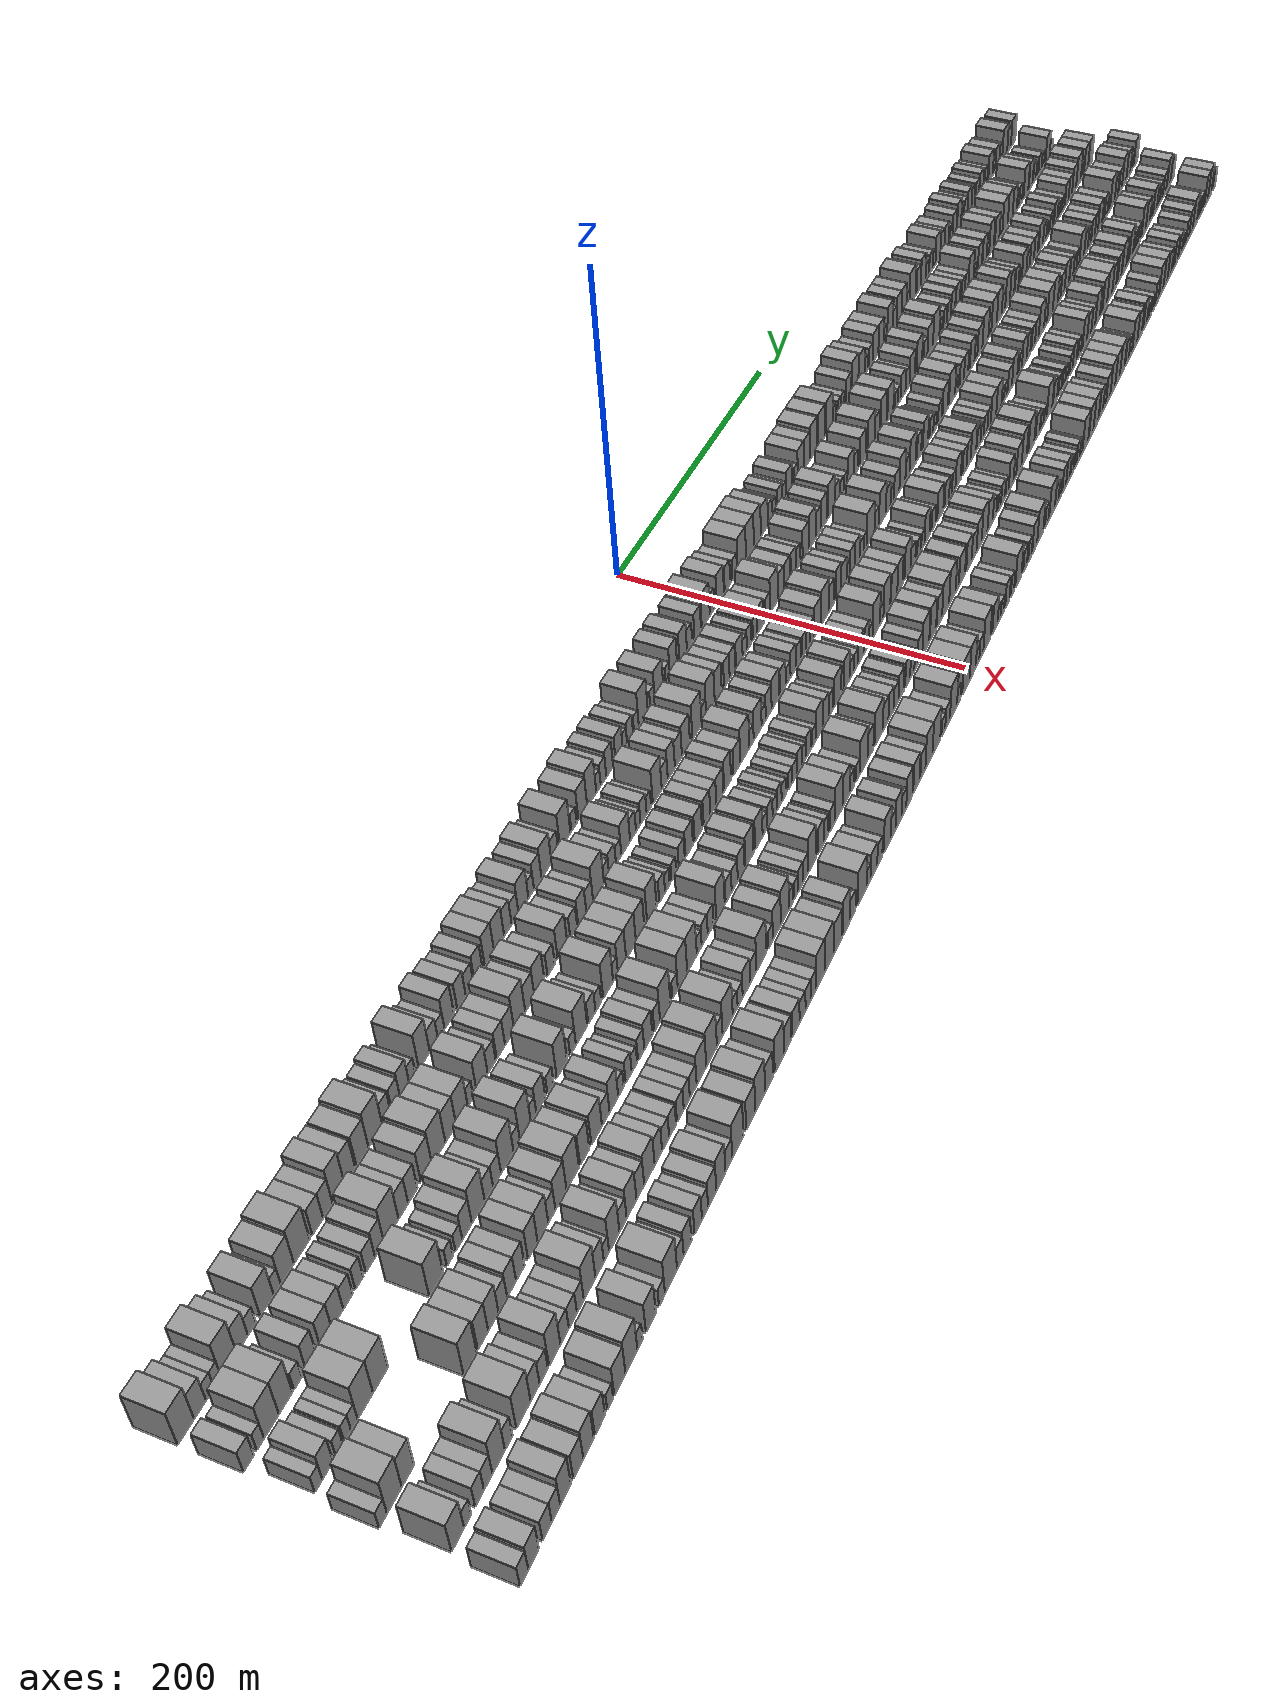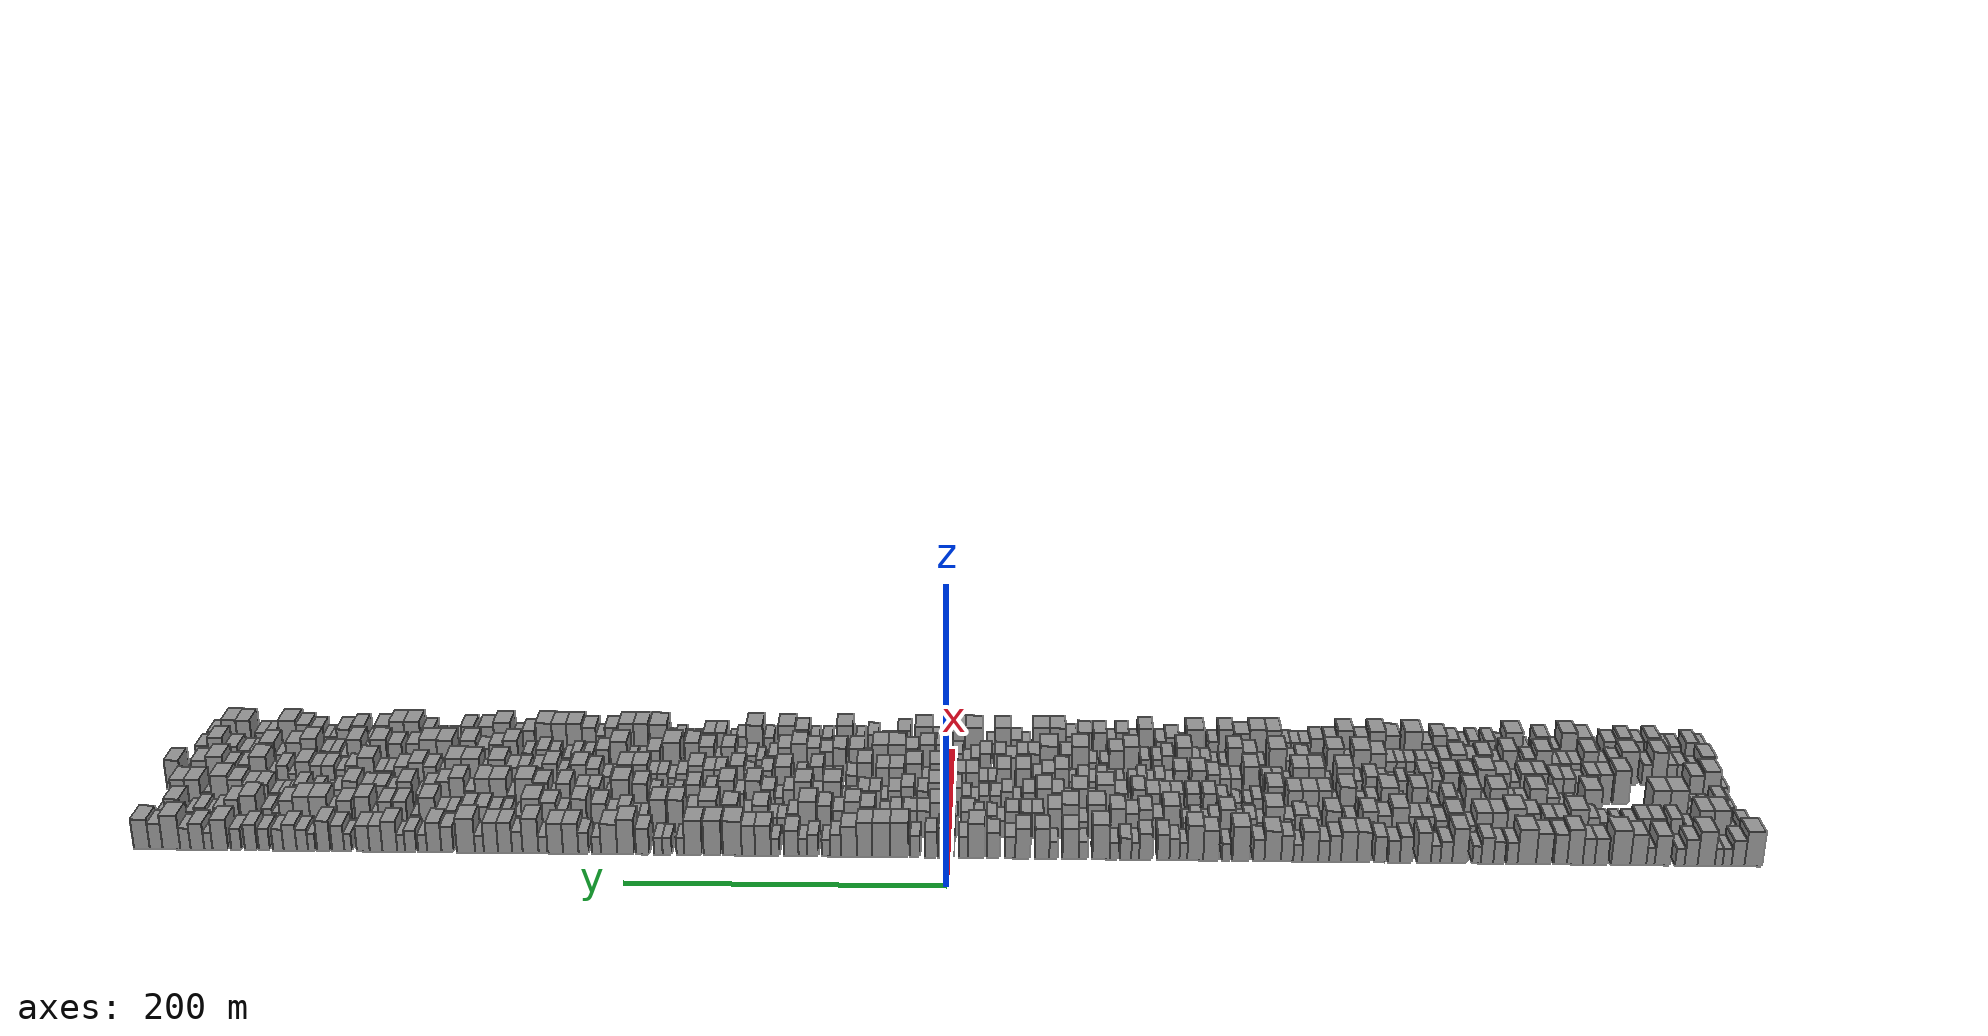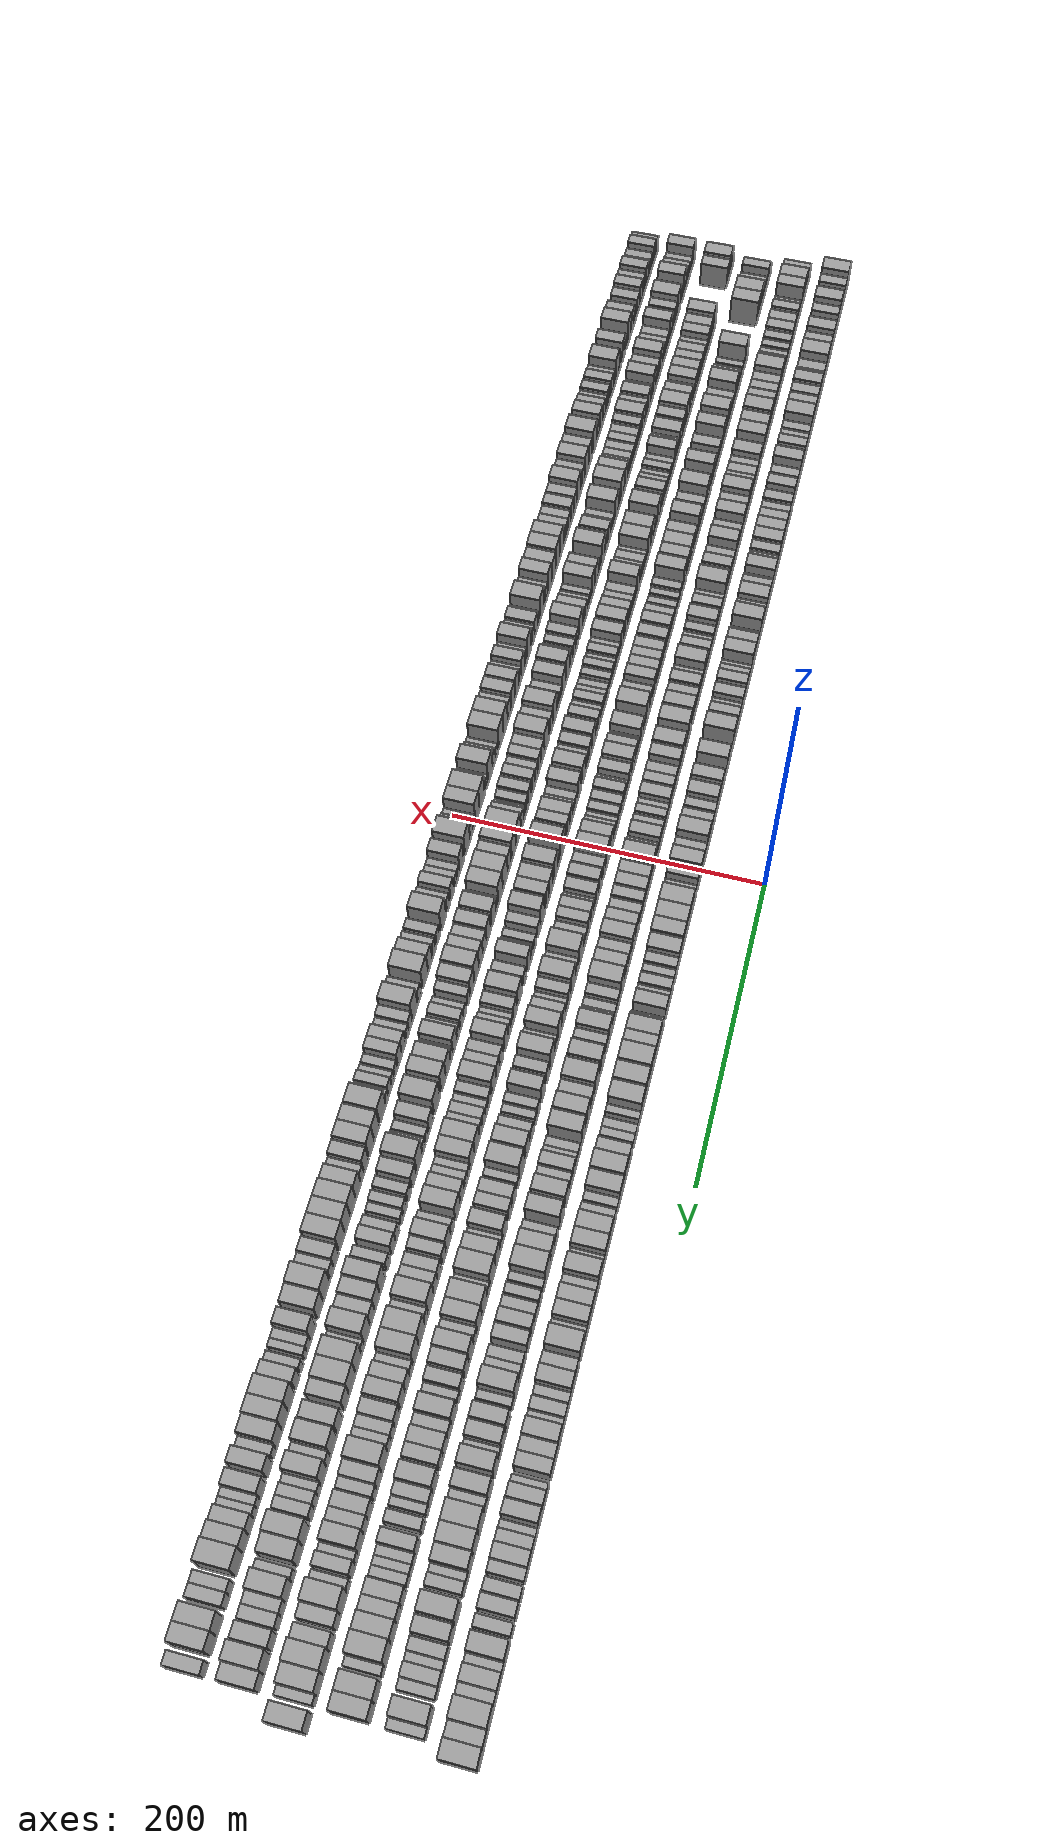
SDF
<sdf version="1.6">
 <world name="default">
  <scene>
   <sky><clouds><speed>12</speed></clouds></sky>
   <ambient>0.4 0.4 0.4 1</ambient>
   <background>0.7 0.7 0.7 1</background>
   <shadows>1</shadows>
  </scene>
  <gravity>0 0 -9.8066</gravity>
  <magnetic_field>6e-06 2.3e-05 -4.2e-05</magnetic_field>
  <physics default="0" name="default_physics" type="ode">
   <ode>
    <solver>
     <type>quick</type>
     <iters>10</iters>
     <sor>1.0</sor>
     <use_dynamic_moi_rescaling>0</use_dynamic_moi_rescaling>
    </solver>
    <constraints>
     <cfm>0</cfm>
     <erp>0.2</erp>
     <contact_max_correcting_vel>100</contact_max_correcting_vel>
     <contact_surface_layer>0.001</contact_surface_layer>
    </constraints>
   </ode>
   <max_step_size>0.004</max_step_size>
   <real_time_factor>1</real_time_factor>
   <real_time_update_rate>250</real_time_update_rate>
  </physics>
  <light name="sun" type="directional">
   <pose>0 0 10 0 0 0</pose>
   <diffuse>0.8 0.8 0.8 1</diffuse>
   <specular>0.2 0.2 0.2 1</specular>
   <attenuation>
    <range>1000</range>
    <constant>0.9</constant>
    <linear>0.01</linear>
    <quadratic>0.001</quadratic>
   </attenuation>
   <direction>-0.5 0.1 -0.9</direction>
  </light>
  <model name="building_1">
   <static>1</static>
   <pose>50.0000 -504.4552 0 0.000000 0.000000 0.000000</pose>
   <link name="link">
    <pose>0 0 12.00 0 0 0</pose>
    <collision name="collision"><geometry><box><size>20.0000 11.0896 24.0000</size></box></geometry></collision>
    <visual name="visual">
     <cast_shadows>0</cast_shadows>
     <geometry><box><size>20.0000 11.0896 24.0000</size></box></geometry>
     <material>
      <script>
       <uri>model://grey_wall/materials/scripts</uri>
       <uri>model://grey_wall/materials/textures</uri>
       <name>vrc/grey_wall</name>
      </script>
     </material>
    </visual>
   </link>
  </model>
  <model name="building_2">
   <static>1</static>
   <pose>50.0000 -494.8866 0 0.000000 0.000000 0.000000</pose>
   <link name="link">
    <pose>0 0 9.00 0 0 0</pose>
    <collision name="collision"><geometry><box><size>20.0000 8.0475 18.0000</size></box></geometry></collision>
    <visual name="visual">
     <cast_shadows>0</cast_shadows>
     <geometry><box><size>20.0000 8.0475 18.0000</size></box></geometry>
     <material>
      <script>
       <uri>model://grey_wall/materials/scripts</uri>
       <uri>model://grey_wall/materials/textures</uri>
       <name>vrc/grey_wall</name>
      </script>
     </material>
    </visual>
   </link>
  </model>
  <model name="building_3">
   <static>1</static>
   <pose>50.0000 -488.0652 0 0.000000 0.000000 0.000000</pose>
   <link name="link">
    <pose>0 0 6.00 0 0 0</pose>
    <collision name="collision"><geometry><box><size>20.0000 5.5954 12.0000</size></box></geometry></collision>
    <visual name="visual">
     <cast_shadows>0</cast_shadows>
     <geometry><box><size>20.0000 5.5954 12.0000</size></box></geometry>
     <material>
      <script>
       <uri>model://grey_wall/materials/scripts</uri>
       <uri>model://grey_wall/materials/textures</uri>
       <name>vrc/grey_wall</name>
      </script>
     </material>
    </visual>
   </link>
  </model>
  <model name="building_4">
   <static>1</static>
   <pose>50.0000 -482.8404 0 0.000000 0.000000 0.000000</pose>
   <link name="link">
    <pose>0 0 6.00 0 0 0</pose>
    <collision name="collision"><geometry><box><size>20.0000 4.8542 12.0000</size></box></geometry></collision>
    <visual name="visual">
     <cast_shadows>0</cast_shadows>
     <geometry><box><size>20.0000 4.8542 12.0000</size></box></geometry>
     <material>
      <script>
       <uri>model://grey_wall/materials/scripts</uri>
       <uri>model://grey_wall/materials/textures</uri>
       <name>vrc/grey_wall</name>
      </script>
     </material>
    </visual>
   </link>
  </model>
  <model name="building_5">
   <static>1</static>
   <pose>50.0000 -475.0400 0 0.000000 0.000000 0.000000</pose>
   <link name="link">
    <pose>0 0 12.00 0 0 0</pose>
    <collision name="collision"><geometry><box><size>20.0000 10.7464 24.0000</size></box></geometry></collision>
    <visual name="visual">
     <cast_shadows>0</cast_shadows>
     <geometry><box><size>20.0000 10.7464 24.0000</size></box></geometry>
     <material>
      <script>
       <uri>model://grey_wall/materials/scripts</uri>
       <uri>model://grey_wall/materials/textures</uri>
       <name>vrc/grey_wall</name>
      </script>
     </material>
    </visual>
   </link>
  </model>
  <model name="building_6">
   <static>1</static>
   <pose>50.0000 -465.6141 0 0.000000 0.000000 0.000000</pose>
   <link name="link">
    <pose>0 0 9.00 0 0 0</pose>
    <collision name="collision"><geometry><box><size>20.0000 8.1053 18.0000</size></box></geometry></collision>
    <visual name="visual">
     <cast_shadows>0</cast_shadows>
     <geometry><box><size>20.0000 8.1053 18.0000</size></box></geometry>
     <material>
      <script>
       <uri>model://grey_wall/materials/scripts</uri>
       <uri>model://grey_wall/materials/textures</uri>
       <name>vrc/grey_wall</name>
      </script>
     </material>
    </visual>
   </link>
  </model>
  <model name="building_7">
   <static>1</static>
   <pose>50.0000 -458.6452 0 0.000000 0.000000 0.000000</pose>
   <link name="link">
    <pose>0 0 6.00 0 0 0</pose>
    <collision name="collision"><geometry><box><size>20.0000 5.8325 12.0000</size></box></geometry></collision>
    <visual name="visual">
     <cast_shadows>0</cast_shadows>
     <geometry><box><size>20.0000 5.8325 12.0000</size></box></geometry>
     <material>
      <script>
       <uri>model://grey_wall/materials/scripts</uri>
       <uri>model://grey_wall/materials/textures</uri>
       <name>vrc/grey_wall</name>
      </script>
     </material>
    </visual>
   </link>
  </model>
  <model name="building_8">
   <static>1</static>
   <pose>50.0000 -447.7873 0 0.000000 0.000000 0.000000</pose>
   <link name="link">
    <pose>0 0 10.50 0 0 0</pose>
    <collision name="collision"><geometry><box><size>20.0000 9.8834 21.0000</size></box></geometry></collision>
    <visual name="visual">
     <cast_shadows>0</cast_shadows>
     <geometry><box><size>20.0000 9.8834 21.0000</size></box></geometry>
     <material>
      <script>
       <uri>model://grey_wall/materials/scripts</uri>
       <uri>model://grey_wall/materials/textures</uri>
       <name>vrc/grey_wall</name>
      </script>
     </material>
    </visual>
   </link>
  </model>
  <model name="building_9">
   <static>1</static>
   <pose>50.0000 -440.2794 0 0.000000 0.000000 0.000000</pose>
   <link name="link">
    <pose>0 0 6.00 0 0 0</pose>
    <collision name="collision"><geometry><box><size>20.0000 5.1324 12.0000</size></box></geometry></collision>
    <visual name="visual">
     <cast_shadows>0</cast_shadows>
     <geometry><box><size>20.0000 5.1324 12.0000</size></box></geometry>
     <material>
      <script>
       <uri>model://grey_wall/materials/scripts</uri>
       <uri>model://grey_wall/materials/textures</uri>
       <name>vrc/grey_wall</name>
      </script>
     </material>
    </visual>
   </link>
  </model>
  <model name="building_10">
   <static>1</static>
   <pose>50.0000 -432.7573 0 0.000000 0.000000 0.000000</pose>
   <link name="link">
    <pose>0 0 10.50 0 0 0</pose>
    <collision name="collision"><geometry><box><size>20.0000 9.9118 21.0000</size></box></geometry></collision>
    <visual name="visual">
     <cast_shadows>0</cast_shadows>
     <geometry><box><size>20.0000 9.9118 21.0000</size></box></geometry>
     <material>
      <script>
       <uri>model://grey_wall/materials/scripts</uri>
       <uri>model://grey_wall/materials/textures</uri>
       <name>vrc/grey_wall</name>
      </script>
     </material>
    </visual>
   </link>
  </model>
  <model name="building_11">
   <static>1</static>
   <pose>50.0000 -421.8053 0 0.000000 0.000000 0.000000</pose>
   <link name="link">
    <pose>0 0 12.00 0 0 0</pose>
    <collision name="collision"><geometry><box><size>20.0000 11.9922 24.0000</size></box></geometry></collision>
    <visual name="visual">
     <cast_shadows>0</cast_shadows>
     <geometry><box><size>20.0000 11.9922 24.0000</size></box></geometry>
     <material>
      <script>
       <uri>model://grey_wall/materials/scripts</uri>
       <uri>model://grey_wall/materials/textures</uri>
       <name>vrc/grey_wall</name>
      </script>
     </material>
    </visual>
   </link>
  </model>
  <model name="building_12">
   <static>1</static>
   <pose>50.0000 -409.6034 0 0.000000 0.000000 0.000000</pose>
   <link name="link">
    <pose>0 0 9.00 0 0 0</pose>
    <collision name="collision"><geometry><box><size>20.0000 8.4115 18.0000</size></box></geometry></collision>
    <visual name="visual">
     <cast_shadows>0</cast_shadows>
     <geometry><box><size>20.0000 8.4115 18.0000</size></box></geometry>
     <material>
      <script>
       <uri>model://grey_wall/materials/scripts</uri>
       <uri>model://grey_wall/materials/textures</uri>
       <name>vrc/grey_wall</name>
      </script>
     </material>
    </visual>
   </link>
  </model>
  <model name="building_13">
   <static>1</static>
   <pose>50.0000 -401.6802 0 0.000000 0.000000 0.000000</pose>
   <link name="link">
    <pose>0 0 9.00 0 0 0</pose>
    <collision name="collision"><geometry><box><size>20.0000 7.4351 18.0000</size></box></geometry></collision>
    <visual name="visual">
     <cast_shadows>0</cast_shadows>
     <geometry><box><size>20.0000 7.4351 18.0000</size></box></geometry>
     <material>
      <script>
       <uri>model://grey_wall/materials/scripts</uri>
       <uri>model://grey_wall/materials/textures</uri>
       <name>vrc/grey_wall</name>
      </script>
     </material>
    </visual>
   </link>
  </model>
  <model name="building_14">
   <static>1</static>
   <pose>50.0000 -393.1238 0 0.000000 0.000000 0.000000</pose>
   <link name="link">
    <pose>0 0 12.00 0 0 0</pose>
    <collision name="collision"><geometry><box><size>20.0000 9.6778 24.0000</size></box></geometry></collision>
    <visual name="visual">
     <cast_shadows>0</cast_shadows>
     <geometry><box><size>20.0000 9.6778 24.0000</size></box></geometry>
     <material>
      <script>
       <uri>model://grey_wall/materials/scripts</uri>
       <uri>model://grey_wall/materials/textures</uri>
       <name>vrc/grey_wall</name>
      </script>
     </material>
    </visual>
   </link>
  </model>
  <model name="building_15">
   <static>1</static>
   <pose>50.0000 -384.0460 0 0.000000 0.000000 0.000000</pose>
   <link name="link">
    <pose>0 0 10.50 0 0 0</pose>
    <collision name="collision"><geometry><box><size>20.0000 8.4777 21.0000</size></box></geometry></collision>
    <visual name="visual">
     <cast_shadows>0</cast_shadows>
     <geometry><box><size>20.0000 8.4777 21.0000</size></box></geometry>
     <material>
      <script>
       <uri>model://grey_wall/materials/scripts</uri>
       <uri>model://grey_wall/materials/textures</uri>
       <name>vrc/grey_wall</name>
      </script>
     </material>
    </visual>
   </link>
  </model>
  <model name="building_16">
   <static>1</static>
   <pose>50.0000 -373.8472 0 0.000000 0.000000 0.000000</pose>
   <link name="link">
    <pose>0 0 10.50 0 0 0</pose>
    <collision name="collision"><geometry><box><size>20.0000 9.9200 21.0000</size></box></geometry></collision>
    <visual name="visual">
     <cast_shadows>0</cast_shadows>
     <geometry><box><size>20.0000 9.9200 21.0000</size></box></geometry>
     <material>
      <script>
       <uri>model://grey_wall/materials/scripts</uri>
       <uri>model://grey_wall/materials/textures</uri>
       <name>vrc/grey_wall</name>
      </script>
     </material>
    </visual>
   </link>
  </model>
  <model name="building_17">
   <static>1</static>
   <pose>50.0000 -363.0854 0 0.000000 0.000000 0.000000</pose>
   <link name="link">
    <pose>0 0 12.00 0 0 0</pose>
    <collision name="collision"><geometry><box><size>20.0000 11.6037 24.0000</size></box></geometry></collision>
    <visual name="visual">
     <cast_shadows>0</cast_shadows>
     <geometry><box><size>20.0000 11.6037 24.0000</size></box></geometry>
     <material>
      <script>
       <uri>model://grey_wall/materials/scripts</uri>
       <uri>model://grey_wall/materials/textures</uri>
       <name>vrc/grey_wall</name>
      </script>
     </material>
    </visual>
   </link>
  </model>
  <model name="building_18">
   <static>1</static>
   <pose>50.0000 -353.8108 0 0.000000 0.000000 0.000000</pose>
   <link name="link">
    <pose>0 0 7.50 0 0 0</pose>
    <collision name="collision"><geometry><box><size>20.0000 6.9455 15.0000</size></box></geometry></collision>
    <visual name="visual">
     <cast_shadows>0</cast_shadows>
     <geometry><box><size>20.0000 6.9455 15.0000</size></box></geometry>
     <material>
      <script>
       <uri>model://grey_wall/materials/scripts</uri>
       <uri>model://grey_wall/materials/textures</uri>
       <name>vrc/grey_wall</name>
      </script>
     </material>
    </visual>
   </link>
  </model>
  <model name="building_19">
   <static>1</static>
   <pose>50.0000 -345.7637 0 0.000000 0.000000 0.000000</pose>
   <link name="link">
    <pose>0 0 7.50 0 0 0</pose>
    <collision name="collision"><geometry><box><size>20.0000 7.1486 15.0000</size></box></geometry></collision>
    <visual name="visual">
     <cast_shadows>0</cast_shadows>
     <geometry><box><size>20.0000 7.1486 15.0000</size></box></geometry>
     <material>
      <script>
       <uri>model://grey_wall/materials/scripts</uri>
       <uri>model://grey_wall/materials/textures</uri>
       <name>vrc/grey_wall</name>
      </script>
     </material>
    </visual>
   </link>
  </model>
  <model name="building_20">
   <static>1</static>
   <pose>50.0000 -338.2811 0 0.000000 0.000000 0.000000</pose>
   <link name="link">
    <pose>0 0 9.00 0 0 0</pose>
    <collision name="collision"><geometry><box><size>20.0000 7.8166 18.0000</size></box></geometry></collision>
    <visual name="visual">
     <cast_shadows>0</cast_shadows>
     <geometry><box><size>20.0000 7.8166 18.0000</size></box></geometry>
     <material>
      <script>
       <uri>model://grey_wall/materials/scripts</uri>
       <uri>model://grey_wall/materials/textures</uri>
       <name>vrc/grey_wall</name>
      </script>
     </material>
    </visual>
   </link>
  </model>
  <model name="building_21">
   <static>1</static>
   <pose>50.0000 -331.6705 0 0.000000 0.000000 0.000000</pose>
   <link name="link">
    <pose>0 0 6.00 0 0 0</pose>
    <collision name="collision"><geometry><box><size>20.0000 5.4046 12.0000</size></box></geometry></collision>
    <visual name="visual">
     <cast_shadows>0</cast_shadows>
     <geometry><box><size>20.0000 5.4046 12.0000</size></box></geometry>
     <material>
      <script>
       <uri>model://grey_wall/materials/scripts</uri>
       <uri>model://grey_wall/materials/textures</uri>
       <name>vrc/grey_wall</name>
      </script>
     </material>
    </visual>
   </link>
  </model>
  <model name="building_22">
   <static>1</static>
   <pose>50.0000 -321.1585 0 0.000000 0.000000 0.000000</pose>
   <link name="link">
    <pose>0 0 12.00 0 0 0</pose>
    <collision name="collision"><geometry><box><size>20.0000 9.6194 24.0000</size></box></geometry></collision>
    <visual name="visual">
     <cast_shadows>0</cast_shadows>
     <geometry><box><size>20.0000 9.6194 24.0000</size></box></geometry>
     <material>
      <script>
       <uri>model://grey_wall/materials/scripts</uri>
       <uri>model://grey_wall/materials/textures</uri>
       <name>vrc/grey_wall</name>
      </script>
     </material>
    </visual>
   </link>
  </model>
  <model name="building_23">
   <static>1</static>
   <pose>50.0000 -312.6653 0 0.000000 0.000000 0.000000</pose>
   <link name="link">
    <pose>0 0 7.50 0 0 0</pose>
    <collision name="collision"><geometry><box><size>20.0000 7.3670 15.0000</size></box></geometry></collision>
    <visual name="visual">
     <cast_shadows>0</cast_shadows>
     <geometry><box><size>20.0000 7.3670 15.0000</size></box></geometry>
     <material>
      <script>
       <uri>model://grey_wall/materials/scripts</uri>
       <uri>model://grey_wall/materials/textures</uri>
       <name>vrc/grey_wall</name>
      </script>
     </material>
    </visual>
   </link>
  </model>
  <model name="building_24">
   <static>1</static>
   <pose>50.0000 -306.0284 0 0.000000 0.000000 0.000000</pose>
   <link name="link">
    <pose>0 0 6.00 0 0 0</pose>
    <collision name="collision"><geometry><box><size>20.0000 5.9067 12.0000</size></box></geometry></collision>
    <visual name="visual">
     <cast_shadows>0</cast_shadows>
     <geometry><box><size>20.0000 5.9067 12.0000</size></box></geometry>
     <material>
      <script>
       <uri>model://grey_wall/materials/scripts</uri>
       <uri>model://grey_wall/materials/textures</uri>
       <name>vrc/grey_wall</name>
      </script>
     </material>
    </visual>
   </link>
  </model>
  <model name="building_25">
   <static>1</static>
   <pose>50.0000 -298.7653 0 0.000000 0.000000 0.000000</pose>
   <link name="link">
    <pose>0 0 10.50 0 0 0</pose>
    <collision name="collision"><geometry><box><size>20.0000 8.6196 21.0000</size></box></geometry></collision>
    <visual name="visual">
     <cast_shadows>0</cast_shadows>
     <geometry><box><size>20.0000 8.6196 21.0000</size></box></geometry>
     <material>
      <script>
       <uri>model://grey_wall/materials/scripts</uri>
       <uri>model://grey_wall/materials/textures</uri>
       <name>vrc/grey_wall</name>
      </script>
     </material>
    </visual>
   </link>
  </model>
  <model name="building_26">
   <static>1</static>
   <pose>50.0000 -287.5092 0 0.000000 0.000000 0.000000</pose>
   <link name="link">
    <pose>0 0 9.00 0 0 0</pose>
    <collision name="collision"><geometry><box><size>20.0000 7.8925 18.0000</size></box></geometry></collision>
    <visual name="visual">
     <cast_shadows>0</cast_shadows>
     <geometry><box><size>20.0000 7.8925 18.0000</size></box></geometry>
     <material>
      <script>
       <uri>model://grey_wall/materials/scripts</uri>
       <uri>model://grey_wall/materials/textures</uri>
       <name>vrc/grey_wall</name>
      </script>
     </material>
    </visual>
   </link>
  </model>
  <model name="building_27">
   <static>1</static>
   <pose>50.0000 -279.9072 0 0.000000 0.000000 0.000000</pose>
   <link name="link">
    <pose>0 0 7.50 0 0 0</pose>
    <collision name="collision"><geometry><box><size>20.0000 7.3117 15.0000</size></box></geometry></collision>
    <visual name="visual">
     <cast_shadows>0</cast_shadows>
     <geometry><box><size>20.0000 7.3117 15.0000</size></box></geometry>
     <material>
      <script>
       <uri>model://grey_wall/materials/scripts</uri>
       <uri>model://grey_wall/materials/textures</uri>
       <name>vrc/grey_wall</name>
      </script>
     </material>
    </visual>
   </link>
  </model>
  <model name="building_28">
   <static>1</static>
   <pose>50.0000 -271.3781 0 0.000000 0.000000 0.000000</pose>
   <link name="link">
    <pose>0 0 9.00 0 0 0</pose>
    <collision name="collision"><geometry><box><size>20.0000 7.7464 18.0000</size></box></geometry></collision>
    <visual name="visual">
     <cast_shadows>0</cast_shadows>
     <geometry><box><size>20.0000 7.7464 18.0000</size></box></geometry>
     <material>
      <script>
       <uri>model://grey_wall/materials/scripts</uri>
       <uri>model://grey_wall/materials/textures</uri>
       <name>vrc/grey_wall</name>
      </script>
     </material>
    </visual>
   </link>
  </model>
  <model name="building_29">
   <static>1</static>
   <pose>50.0000 -261.0424 0 0.000000 0.000000 0.000000</pose>
   <link name="link">
    <pose>0 0 10.50 0 0 0</pose>
    <collision name="collision"><geometry><box><size>20.0000 8.9250 21.0000</size></box></geometry></collision>
    <visual name="visual">
     <cast_shadows>0</cast_shadows>
     <geometry><box><size>20.0000 8.9250 21.0000</size></box></geometry>
     <material>
      <script>
       <uri>model://grey_wall/materials/scripts</uri>
       <uri>model://grey_wall/materials/textures</uri>
       <name>vrc/grey_wall</name>
      </script>
     </material>
    </visual>
   </link>
  </model>
  <model name="building_30">
   <static>1</static>
   <pose>50.0000 -251.6607 0 0.000000 0.000000 0.000000</pose>
   <link name="link">
    <pose>0 0 10.50 0 0 0</pose>
    <collision name="collision"><geometry><box><size>20.0000 9.8384 21.0000</size></box></geometry></collision>
    <visual name="visual">
     <cast_shadows>0</cast_shadows>
     <geometry><box><size>20.0000 9.8384 21.0000</size></box></geometry>
     <material>
      <script>
       <uri>model://grey_wall/materials/scripts</uri>
       <uri>model://grey_wall/materials/textures</uri>
       <name>vrc/grey_wall</name>
      </script>
     </material>
    </visual>
   </link>
  </model>
  <model name="building_31">
   <static>1</static>
   <pose>50.0000 -243.0680 0 0.000000 0.000000 0.000000</pose>
   <link name="link">
    <pose>0 0 9.00 0 0 0</pose>
    <collision name="collision"><geometry><box><size>20.0000 7.3471 18.0000</size></box></geometry></collision>
    <visual name="visual">
     <cast_shadows>0</cast_shadows>
     <geometry><box><size>20.0000 7.3471 18.0000</size></box></geometry>
     <material>
      <script>
       <uri>model://grey_wall/materials/scripts</uri>
       <uri>model://grey_wall/materials/textures</uri>
       <name>vrc/grey_wall</name>
      </script>
     </material>
    </visual>
   </link>
  </model>
  <model name="building_32">
   <static>1</static>
   <pose>50.0000 -235.9176 0 0.000000 0.000000 0.000000</pose>
   <link name="link">
    <pose>0 0 7.50 0 0 0</pose>
    <collision name="collision"><geometry><box><size>20.0000 6.9537 15.0000</size></box></geometry></collision>
    <visual name="visual">
     <cast_shadows>0</cast_shadows>
     <geometry><box><size>20.0000 6.9537 15.0000</size></box></geometry>
     <material>
      <script>
       <uri>model://grey_wall/materials/scripts</uri>
       <uri>model://grey_wall/materials/textures</uri>
       <name>vrc/grey_wall</name>
      </script>
     </material>
    </visual>
   </link>
  </model>
  <model name="building_33">
   <static>1</static>
   <pose>50.0000 -227.4500 0 0.000000 0.000000 0.000000</pose>
   <link name="link">
    <pose>0 0 10.50 0 0 0</pose>
    <collision name="collision"><geometry><box><size>20.0000 9.9816 21.0000</size></box></geometry></collision>
    <visual name="visual">
     <cast_shadows>0</cast_shadows>
     <geometry><box><size>20.0000 9.9816 21.0000</size></box></geometry>
     <material>
      <script>
       <uri>model://grey_wall/materials/scripts</uri>
       <uri>model://grey_wall/materials/textures</uri>
       <name>vrc/grey_wall</name>
      </script>
     </material>
    </visual>
   </link>
  </model>
  <model name="building_34">
   <static>1</static>
   <pose>50.0000 -219.6462 0 0.000000 0.000000 0.000000</pose>
   <link name="link">
    <pose>0 0 6.00 0 0 0</pose>
    <collision name="collision"><geometry><box><size>20.0000 5.6259 12.0000</size></box></geometry></collision>
    <visual name="visual">
     <cast_shadows>0</cast_shadows>
     <geometry><box><size>20.0000 5.6259 12.0000</size></box></geometry>
     <material>
      <script>
       <uri>model://grey_wall/materials/scripts</uri>
       <uri>model://grey_wall/materials/textures</uri>
       <name>vrc/grey_wall</name>
      </script>
     </material>
    </visual>
   </link>
  </model>
  <model name="building_35">
   <static>1</static>
   <pose>50.0000 -212.9901 0 0.000000 0.000000 0.000000</pose>
   <link name="link">
    <pose>0 0 9.00 0 0 0</pose>
    <collision name="collision"><geometry><box><size>20.0000 7.6864 18.0000</size></box></geometry></collision>
    <visual name="visual">
     <cast_shadows>0</cast_shadows>
     <geometry><box><size>20.0000 7.6864 18.0000</size></box></geometry>
     <material>
      <script>
       <uri>model://grey_wall/materials/scripts</uri>
       <uri>model://grey_wall/materials/textures</uri>
       <name>vrc/grey_wall</name>
      </script>
     </material>
    </visual>
   </link>
  </model>
  <model name="building_36">
   <static>1</static>
   <pose>50.0000 -203.9305 0 0.000000 0.000000 0.000000</pose>
   <link name="link">
    <pose>0 0 10.50 0 0 0</pose>
    <collision name="collision"><geometry><box><size>20.0000 10.4330 21.0000</size></box></geometry></collision>
    <visual name="visual">
     <cast_shadows>0</cast_shadows>
     <geometry><box><size>20.0000 10.4330 21.0000</size></box></geometry>
     <material>
      <script>
       <uri>model://grey_wall/materials/scripts</uri>
       <uri>model://grey_wall/materials/textures</uri>
       <name>vrc/grey_wall</name>
      </script>
     </material>
    </visual>
   </link>
  </model>
  <model name="building_37">
   <static>1</static>
   <pose>50.0000 -195.0997 0 0.000000 0.000000 0.000000</pose>
   <link name="link">
    <pose>0 0 7.50 0 0 0</pose>
    <collision name="collision"><geometry><box><size>20.0000 7.2284 15.0000</size></box></geometry></collision>
    <visual name="visual">
     <cast_shadows>0</cast_shadows>
     <geometry><box><size>20.0000 7.2284 15.0000</size></box></geometry>
     <material>
      <script>
       <uri>model://grey_wall/materials/scripts</uri>
       <uri>model://grey_wall/materials/textures</uri>
       <name>vrc/grey_wall</name>
      </script>
     </material>
    </visual>
   </link>
  </model>
  <model name="building_38">
   <static>1</static>
   <pose>50.0000 -184.0242 0 0.000000 0.000000 0.000000</pose>
   <link name="link">
    <pose>0 0 12.00 0 0 0</pose>
    <collision name="collision"><geometry><box><size>20.0000 10.9227 24.0000</size></box></geometry></collision>
    <visual name="visual">
     <cast_shadows>0</cast_shadows>
     <geometry><box><size>20.0000 10.9227 24.0000</size></box></geometry>
     <material>
      <script>
       <uri>model://grey_wall/materials/scripts</uri>
       <uri>model://grey_wall/materials/textures</uri>
       <name>vrc/grey_wall</name>
      </script>
     </material>
    </visual>
   </link>
  </model>
  <model name="building_39">
   <static>1</static>
   <pose>50.0000 -174.7651 0 0.000000 0.000000 0.000000</pose>
   <link name="link">
    <pose>0 0 6.00 0 0 0</pose>
    <collision name="collision"><geometry><box><size>20.0000 5.5954 12.0000</size></box></geometry></collision>
    <visual name="visual">
     <cast_shadows>0</cast_shadows>
     <geometry><box><size>20.0000 5.5954 12.0000</size></box></geometry>
     <material>
      <script>
       <uri>model://grey_wall/materials/scripts</uri>
       <uri>model://grey_wall/materials/textures</uri>
       <name>vrc/grey_wall</name>
      </script>
     </material>
    </visual>
   </link>
  </model>
  <model name="building_40">
   <static>1</static>
   <pose>50.0000 -165.1208 0 0.000000 0.000000 0.000000</pose>
   <link name="link">
    <pose>0 0 10.50 0 0 0</pose>
    <collision name="collision"><geometry><box><size>20.0000 9.6932 21.0000</size></box></geometry></collision>
    <visual name="visual">
     <cast_shadows>0</cast_shadows>
     <geometry><box><size>20.0000 9.6932 21.0000</size></box></geometry>
     <material>
      <script>
       <uri>model://grey_wall/materials/scripts</uri>
       <uri>model://grey_wall/materials/textures</uri>
       <name>vrc/grey_wall</name>
      </script>
     </material>
    </visual>
   </link>
  </model>
  <model name="building_41">
   <static>1</static>
   <pose>50.0000 -155.2484 0 0.000000 0.000000 0.000000</pose>
   <link name="link">
    <pose>0 0 12.00 0 0 0</pose>
    <collision name="collision"><geometry><box><size>20.0000 10.0516 24.0000</size></box></geometry></collision>
    <visual name="visual">
     <cast_shadows>0</cast_shadows>
     <geometry><box><size>20.0000 10.0516 24.0000</size></box></geometry>
     <material>
      <script>
       <uri>model://grey_wall/materials/scripts</uri>
       <uri>model://grey_wall/materials/textures</uri>
       <name>vrc/grey_wall</name>
      </script>
     </material>
    </visual>
   </link>
  </model>
  <model name="building_42">
   <static>1</static>
   <pose>50.0000 -147.7631 0 0.000000 0.000000 0.000000</pose>
   <link name="link">
    <pose>0 0 6.00 0 0 0</pose>
    <collision name="collision"><geometry><box><size>20.0000 4.9192 12.0000</size></box></geometry></collision>
    <visual name="visual">
     <cast_shadows>0</cast_shadows>
     <geometry><box><size>20.0000 4.9192 12.0000</size></box></geometry>
     <material>
      <script>
       <uri>model://grey_wall/materials/scripts</uri>
       <uri>model://grey_wall/materials/textures</uri>
       <name>vrc/grey_wall</name>
      </script>
     </material>
    </visual>
   </link>
  </model>
  <model name="building_43">
   <static>1</static>
   <pose>50.0000 -142.1714 0 0.000000 0.000000 0.000000</pose>
   <link name="link">
    <pose>0 0 7.50 0 0 0</pose>
    <collision name="collision"><geometry><box><size>20.0000 6.2641 15.0000</size></box></geometry></collision>
    <visual name="visual">
     <cast_shadows>0</cast_shadows>
     <geometry><box><size>20.0000 6.2641 15.0000</size></box></geometry>
     <material>
      <script>
       <uri>model://grey_wall/materials/scripts</uri>
       <uri>model://grey_wall/materials/textures</uri>
       <name>vrc/grey_wall</name>
      </script>
     </material>
    </visual>
   </link>
  </model>
  <model name="building_44">
   <static>1</static>
   <pose>50.0000 -135.1773 0 0.000000 0.000000 0.000000</pose>
   <link name="link">
    <pose>0 0 9.00 0 0 0</pose>
    <collision name="collision"><geometry><box><size>20.0000 7.7241 18.0000</size></box></geometry></collision>
    <visual name="visual">
     <cast_shadows>0</cast_shadows>
     <geometry><box><size>20.0000 7.7241 18.0000</size></box></geometry>
     <material>
      <script>
       <uri>model://grey_wall/materials/scripts</uri>
       <uri>model://grey_wall/materials/textures</uri>
       <name>vrc/grey_wall</name>
      </script>
     </material>
    </visual>
   </link>
  </model>
  <model name="building_45">
   <static>1</static>
   <pose>50.0000 -124.1490 0 0.000000 0.000000 0.000000</pose>
   <link name="link">
    <pose>0 0 9.00 0 0 0</pose>
    <collision name="collision"><geometry><box><size>20.0000 8.3326 18.0000</size></box></geometry></collision>
    <visual name="visual">
     <cast_shadows>0</cast_shadows>
     <geometry><box><size>20.0000 8.3326 18.0000</size></box></geometry>
     <material>
      <script>
       <uri>model://grey_wall/materials/scripts</uri>
       <uri>model://grey_wall/materials/textures</uri>
       <name>vrc/grey_wall</name>
      </script>
     </material>
    </visual>
   </link>
  </model>
  <model name="building_46">
   <static>1</static>
   <pose>50.0000 -117.4950 0 0.000000 0.000000 0.000000</pose>
   <link name="link">
    <pose>0 0 6.00 0 0 0</pose>
    <collision name="collision"><geometry><box><size>20.0000 4.9755 12.0000</size></box></geometry></collision>
    <visual name="visual">
     <cast_shadows>0</cast_shadows>
     <geometry><box><size>20.0000 4.9755 12.0000</size></box></geometry>
     <material>
      <script>
       <uri>model://grey_wall/materials/scripts</uri>
       <uri>model://grey_wall/materials/textures</uri>
       <name>vrc/grey_wall</name>
      </script>
     </material>
    </visual>
   </link>
  </model>
  <model name="building_47">
   <static>1</static>
   <pose>50.0000 -111.4804 0 0.000000 0.000000 0.000000</pose>
   <link name="link">
    <pose>0 0 7.50 0 0 0</pose>
    <collision name="collision"><geometry><box><size>20.0000 7.0537 15.0000</size></box></geometry></collision>
    <visual name="visual">
     <cast_shadows>0</cast_shadows>
     <geometry><box><size>20.0000 7.0537 15.0000</size></box></geometry>
     <material>
      <script>
       <uri>model://grey_wall/materials/scripts</uri>
       <uri>model://grey_wall/materials/textures</uri>
       <name>vrc/grey_wall</name>
      </script>
     </material>
    </visual>
   </link>
  </model>
  <model name="building_48">
   <static>1</static>
   <pose>50.0000 -104.1491 0 0.000000 0.000000 0.000000</pose>
   <link name="link">
    <pose>0 0 6.00 0 0 0</pose>
    <collision name="collision"><geometry><box><size>20.0000 5.6088 12.0000</size></box></geometry></collision>
    <visual name="visual">
     <cast_shadows>0</cast_shadows>
     <geometry><box><size>20.0000 5.6088 12.0000</size></box></geometry>
     <material>
      <script>
       <uri>model://grey_wall/materials/scripts</uri>
       <uri>model://grey_wall/materials/textures</uri>
       <name>vrc/grey_wall</name>
      </script>
     </material>
    </visual>
   </link>
  </model>
  <model name="building_49">
   <static>1</static>
   <pose>50.0000 -95.9349 0 0.000000 0.000000 0.000000</pose>
   <link name="link">
    <pose>0 0 12.00 0 0 0</pose>
    <collision name="collision"><geometry><box><size>20.0000 10.8196 24.0000</size></box></geometry></collision>
    <visual name="visual">
     <cast_shadows>0</cast_shadows>
     <geometry><box><size>20.0000 10.8196 24.0000</size></box></geometry>
     <material>
      <script>
       <uri>model://grey_wall/materials/scripts</uri>
       <uri>model://grey_wall/materials/textures</uri>
       <name>vrc/grey_wall</name>
      </script>
     </material>
    </visual>
   </link>
  </model>
  <model name="building_50">
   <static>1</static>
   <pose>50.0000 -84.7681 0 0.000000 0.000000 0.000000</pose>
   <link name="link">
    <pose>0 0 6.00 0 0 0</pose>
    <collision name="collision"><geometry><box><size>20.0000 5.5140 12.0000</size></box></geometry></collision>
    <visual name="visual">
     <cast_shadows>0</cast_shadows>
     <geometry><box><size>20.0000 5.5140 12.0000</size></box></geometry>
     <material>
      <script>
       <uri>model://grey_wall/materials/scripts</uri>
       <uri>model://grey_wall/materials/textures</uri>
       <name>vrc/grey_wall</name>
      </script>
     </material>
    </visual>
   </link>
  </model>
  <model name="building_51">
   <static>1</static>
   <pose>50.0000 -76.8335 0 0.000000 0.000000 0.000000</pose>
   <link name="link">
    <pose>0 0 10.50 0 0 0</pose>
    <collision name="collision"><geometry><box><size>20.0000 10.3552 21.0000</size></box></geometry></collision>
    <visual name="visual">
     <cast_shadows>0</cast_shadows>
     <geometry><box><size>20.0000 10.3552 21.0000</size></box></geometry>
     <material>
      <script>
       <uri>model://grey_wall/materials/scripts</uri>
       <uri>model://grey_wall/materials/textures</uri>
       <name>vrc/grey_wall</name>
      </script>
     </material>
    </visual>
   </link>
  </model>
  <model name="building_52">
   <static>1</static>
   <pose>50.0000 -66.0445 0 0.000000 0.000000 0.000000</pose>
   <link name="link">
    <pose>0 0 6.00 0 0 0</pose>
    <collision name="collision"><geometry><box><size>20.0000 5.2229 12.0000</size></box></geometry></collision>
    <visual name="visual">
     <cast_shadows>0</cast_shadows>
     <geometry><box><size>20.0000 5.2229 12.0000</size></box></geometry>
     <material>
      <script>
       <uri>model://grey_wall/materials/scripts</uri>
       <uri>model://grey_wall/materials/textures</uri>
       <name>vrc/grey_wall</name>
      </script>
     </material>
    </visual>
   </link>
  </model>
  <model name="building_53">
   <static>1</static>
   <pose>50.0000 -58.9326 0 0.000000 0.000000 0.000000</pose>
   <link name="link">
    <pose>0 0 10.50 0 0 0</pose>
    <collision name="collision"><geometry><box><size>20.0000 9.0008 21.0000</size></box></geometry></collision>
    <visual name="visual">
     <cast_shadows>0</cast_shadows>
     <geometry><box><size>20.0000 9.0008 21.0000</size></box></geometry>
     <material>
      <script>
       <uri>model://grey_wall/materials/scripts</uri>
       <uri>model://grey_wall/materials/textures</uri>
       <name>vrc/grey_wall</name>
      </script>
     </material>
    </visual>
   </link>
  </model>
  <model name="building_54">
   <static>1</static>
   <pose>50.0000 -46.7122 0 0.000000 0.000000 0.000000</pose>
   <link name="link">
    <pose>0 0 10.50 0 0 0</pose>
    <collision name="collision"><geometry><box><size>20.0000 9.4400 21.0000</size></box></geometry></collision>
    <visual name="visual">
     <cast_shadows>0</cast_shadows>
     <geometry><box><size>20.0000 9.4400 21.0000</size></box></geometry>
     <material>
      <script>
       <uri>model://grey_wall/materials/scripts</uri>
       <uri>model://grey_wall/materials/textures</uri>
       <name>vrc/grey_wall</name>
      </script>
     </material>
    </visual>
   </link>
  </model>
  <model name="building_55">
   <static>1</static>
   <pose>50.0000 -38.6631 0 0.000000 0.000000 0.000000</pose>
   <link name="link">
    <pose>0 0 7.50 0 0 0</pose>
    <collision name="collision"><geometry><box><size>20.0000 6.6581 15.0000</size></box></geometry></collision>
    <visual name="visual">
     <cast_shadows>0</cast_shadows>
     <geometry><box><size>20.0000 6.6581 15.0000</size></box></geometry>
     <material>
      <script>
       <uri>model://grey_wall/materials/scripts</uri>
       <uri>model://grey_wall/materials/textures</uri>
       <name>vrc/grey_wall</name>
      </script>
     </material>
    </visual>
   </link>
  </model>
  <model name="building_56">
   <static>1</static>
   <pose>50.0000 -28.1345 0 0.000000 0.000000 0.000000</pose>
   <link name="link">
    <pose>0 0 9.00 0 0 0</pose>
    <collision name="collision"><geometry><box><size>20.0000 8.3990 18.0000</size></box></geometry></collision>
    <visual name="visual">
     <cast_shadows>0</cast_shadows>
     <geometry><box><size>20.0000 8.3990 18.0000</size></box></geometry>
     <material>
      <script>
       <uri>model://grey_wall/materials/scripts</uri>
       <uri>model://grey_wall/materials/textures</uri>
       <name>vrc/grey_wall</name>
      </script>
     </material>
    </visual>
   </link>
  </model>
  <model name="building_57">
   <static>1</static>
   <pose>50.0000 -17.6070 0 0.000000 0.000000 0.000000</pose>
   <link name="link">
    <pose>0 0 12.00 0 0 0</pose>
    <collision name="collision"><geometry><box><size>20.0000 10.6561 24.0000</size></box></geometry></collision>
    <visual name="visual">
     <cast_shadows>0</cast_shadows>
     <geometry><box><size>20.0000 10.6561 24.0000</size></box></geometry>
     <material>
      <script>
       <uri>model://grey_wall/materials/scripts</uri>
       <uri>model://grey_wall/materials/textures</uri>
       <name>vrc/grey_wall</name>
      </script>
     </material>
    </visual>
   </link>
  </model>
  <model name="building_58">
   <static>1</static>
   <pose>50.0000 -9.2561 0 0.000000 0.000000 0.000000</pose>
   <link name="link">
    <pose>0 0 7.50 0 0 0</pose>
    <collision name="collision"><geometry><box><size>20.0000 6.0458 15.0000</size></box></geometry></collision>
    <visual name="visual">
     <cast_shadows>0</cast_shadows>
     <geometry><box><size>20.0000 6.0458 15.0000</size></box></geometry>
     <material>
      <script>
       <uri>model://grey_wall/materials/scripts</uri>
       <uri>model://grey_wall/materials/textures</uri>
       <name>vrc/grey_wall</name>
      </script>
     </material>
    </visual>
   </link>
  </model>
  <model name="building_59">
   <static>1</static>
   <pose>50.0000 1.6662 0 0.000000 0.000000 0.000000</pose>
   <link name="link">
    <pose>0 0 10.50 0 0 0</pose>
    <collision name="collision"><geometry><box><size>20.0000 9.7988 21.0000</size></box></geometry></collision>
    <visual name="visual">
     <cast_shadows>0</cast_shadows>
     <geometry><box><size>20.0000 9.7988 21.0000</size></box></geometry>
     <material>
      <script>
       <uri>model://grey_wall/materials/scripts</uri>
       <uri>model://grey_wall/materials/textures</uri>
       <name>vrc/grey_wall</name>
      </script>
     </material>
    </visual>
   </link>
  </model>
  <model name="building_60">
   <static>1</static>
   <pose>50.0000 11.2999 0 0.000000 0.000000 0.000000</pose>
   <link name="link">
    <pose>0 0 9.00 0 0 0</pose>
    <collision name="collision"><geometry><box><size>20.0000 7.4685 18.0000</size></box></geometry></collision>
    <visual name="visual">
     <cast_shadows>0</cast_shadows>
     <geometry><box><size>20.0000 7.4685 18.0000</size></box></geometry>
     <material>
      <script>
       <uri>model://grey_wall/materials/scripts</uri>
       <uri>model://grey_wall/materials/textures</uri>
       <name>vrc/grey_wall</name>
      </script>
     </material>
    </visual>
   </link>
  </model>
  <model name="building_61">
   <static>1</static>
   <pose>50.0000 21.2005 0 0.000000 0.000000 0.000000</pose>
   <link name="link">
    <pose>0 0 7.50 0 0 0</pose>
    <collision name="collision"><geometry><box><size>20.0000 6.3329 15.0000</size></box></geometry></collision>
    <visual name="visual">
     <cast_shadows>0</cast_shadows>
     <geometry><box><size>20.0000 6.3329 15.0000</size></box></geometry>
     <material>
      <script>
       <uri>model://grey_wall/materials/scripts</uri>
       <uri>model://grey_wall/materials/textures</uri>
       <name>vrc/grey_wall</name>
      </script>
     </material>
    </visual>
   </link>
  </model>
  <model name="building_62">
   <static>1</static>
   <pose>50.0000 31.1715 0 0.000000 0.000000 0.000000</pose>
   <link name="link">
    <pose>0 0 12.00 0 0 0</pose>
    <collision name="collision"><geometry><box><size>20.0000 11.6090 24.0000</size></box></geometry></collision>
    <visual name="visual">
     <cast_shadows>0</cast_shadows>
     <geometry><box><size>20.0000 11.6090 24.0000</size></box></geometry>
     <material>
      <script>
       <uri>model://grey_wall/materials/scripts</uri>
       <uri>model://grey_wall/materials/textures</uri>
       <name>vrc/grey_wall</name>
      </script>
     </material>
    </visual>
   </link>
  </model>
  <model name="building_63">
   <static>1</static>
   <pose>50.0000 42.5768 0 0.000000 0.000000 0.000000</pose>
   <link name="link">
    <pose>0 0 12.00 0 0 0</pose>
    <collision name="collision"><geometry><box><size>20.0000 11.2016 24.0000</size></box></geometry></collision>
    <visual name="visual">
     <cast_shadows>0</cast_shadows>
     <geometry><box><size>20.0000 11.2016 24.0000</size></box></geometry>
     <material>
      <script>
       <uri>model://grey_wall/materials/scripts</uri>
       <uri>model://grey_wall/materials/textures</uri>
       <name>vrc/grey_wall</name>
      </script>
     </material>
    </visual>
   </link>
  </model>
  <model name="building_64">
   <static>1</static>
   <pose>50.0000 53.1320 0 0.000000 0.000000 0.000000</pose>
   <link name="link">
    <pose>0 0 12.00 0 0 0</pose>
    <collision name="collision"><geometry><box><size>20.0000 9.9088 24.0000</size></box></geometry></collision>
    <visual name="visual">
     <cast_shadows>0</cast_shadows>
     <geometry><box><size>20.0000 9.9088 24.0000</size></box></geometry>
     <material>
      <script>
       <uri>model://grey_wall/materials/scripts</uri>
       <uri>model://grey_wall/materials/textures</uri>
       <name>vrc/grey_wall</name>
      </script>
     </material>
    </visual>
   </link>
  </model>
  <model name="building_65">
   <static>1</static>
   <pose>50.0000 63.1203 0 0.000000 0.000000 0.000000</pose>
   <link name="link">
    <pose>0 0 10.50 0 0 0</pose>
    <collision name="collision"><geometry><box><size>20.0000 10.0676 21.0000</size></box></geometry></collision>
    <visual name="visual">
     <cast_shadows>0</cast_shadows>
     <geometry><box><size>20.0000 10.0676 21.0000</size></box></geometry>
     <material>
      <script>
       <uri>model://grey_wall/materials/scripts</uri>
       <uri>model://grey_wall/materials/textures</uri>
       <name>vrc/grey_wall</name>
      </script>
     </material>
    </visual>
   </link>
  </model>
  <model name="building_66">
   <static>1</static>
   <pose>50.0000 71.5389 0 0.000000 0.000000 0.000000</pose>
   <link name="link">
    <pose>0 0 7.50 0 0 0</pose>
    <collision name="collision"><geometry><box><size>20.0000 6.7696 15.0000</size></box></geometry></collision>
    <visual name="visual">
     <cast_shadows>0</cast_shadows>
     <geometry><box><size>20.0000 6.7696 15.0000</size></box></geometry>
     <material>
      <script>
       <uri>model://grey_wall/materials/scripts</uri>
       <uri>model://grey_wall/materials/textures</uri>
       <name>vrc/grey_wall</name>
      </script>
     </material>
    </visual>
   </link>
  </model>
  <model name="building_67">
   <static>1</static>
   <pose>50.0000 77.5764 0 0.000000 0.000000 0.000000</pose>
   <link name="link">
    <pose>0 0 6.00 0 0 0</pose>
    <collision name="collision"><geometry><box><size>20.0000 5.3054 12.0000</size></box></geometry></collision>
    <visual name="visual">
     <cast_shadows>0</cast_shadows>
     <geometry><box><size>20.0000 5.3054 12.0000</size></box></geometry>
     <material>
      <script>
       <uri>model://grey_wall/materials/scripts</uri>
       <uri>model://grey_wall/materials/textures</uri>
       <name>vrc/grey_wall</name>
      </script>
     </material>
    </visual>
   </link>
  </model>
  <model name="building_68">
   <static>1</static>
   <pose>50.0000 85.7597 0 0.000000 0.000000 0.000000</pose>
   <link name="link">
    <pose>0 0 7.50 0 0 0</pose>
    <collision name="collision"><geometry><box><size>20.0000 7.0612 15.0000</size></box></geometry></collision>
    <visual name="visual">
     <cast_shadows>0</cast_shadows>
     <geometry><box><size>20.0000 7.0612 15.0000</size></box></geometry>
     <material>
      <script>
       <uri>model://grey_wall/materials/scripts</uri>
       <uri>model://grey_wall/materials/textures</uri>
       <name>vrc/grey_wall</name>
      </script>
     </material>
    </visual>
   </link>
  </model>
  <model name="building_69">
   <static>1</static>
   <pose>50.0000 92.0968 0 0.000000 0.000000 0.000000</pose>
   <link name="link">
    <pose>0 0 6.00 0 0 0</pose>
    <collision name="collision"><geometry><box><size>20.0000 5.6129 12.0000</size></box></geometry></collision>
    <visual name="visual">
     <cast_shadows>0</cast_shadows>
     <geometry><box><size>20.0000 5.6129 12.0000</size></box></geometry>
     <material>
      <script>
       <uri>model://grey_wall/materials/scripts</uri>
       <uri>model://grey_wall/materials/textures</uri>
       <name>vrc/grey_wall</name>
      </script>
     </material>
    </visual>
   </link>
  </model>
  <model name="building_70">
   <static>1</static>
   <pose>50.0000 99.3891 0 0.000000 0.000000 0.000000</pose>
   <link name="link">
    <pose>0 0 9.00 0 0 0</pose>
    <collision name="collision"><geometry><box><size>20.0000 8.9718 18.0000</size></box></geometry></collision>
    <visual name="visual">
     <cast_shadows>0</cast_shadows>
     <geometry><box><size>20.0000 8.9718 18.0000</size></box></geometry>
     <material>
      <script>
       <uri>model://grey_wall/materials/scripts</uri>
       <uri>model://grey_wall/materials/textures</uri>
       <name>vrc/grey_wall</name>
      </script>
     </material>
    </visual>
   </link>
  </model>
  <model name="building_71">
   <static>1</static>
   <pose>50.0000 109.6231 0 0.000000 0.000000 0.000000</pose>
   <link name="link">
    <pose>0 0 6.00 0 0 0</pose>
    <collision name="collision"><geometry><box><size>20.0000 5.4961 12.0000</size></box></geometry></collision>
    <visual name="visual">
     <cast_shadows>0</cast_shadows>
     <geometry><box><size>20.0000 5.4961 12.0000</size></box></geometry>
     <material>
      <script>
       <uri>model://grey_wall/materials/scripts</uri>
       <uri>model://grey_wall/materials/textures</uri>
       <name>vrc/grey_wall</name>
      </script>
     </material>
    </visual>
   </link>
  </model>
  <model name="building_72">
   <static>1</static>
   <pose>50.0000 117.3805 0 0.000000 0.000000 0.000000</pose>
   <link name="link">
    <pose>0 0 10.50 0 0 0</pose>
    <collision name="collision"><geometry><box><size>20.0000 10.0186 21.0000</size></box></geometry></collision>
    <visual name="visual">
     <cast_shadows>0</cast_shadows>
     <geometry><box><size>20.0000 10.0186 21.0000</size></box></geometry>
     <material>
      <script>
       <uri>model://grey_wall/materials/scripts</uri>
       <uri>model://grey_wall/materials/textures</uri>
       <name>vrc/grey_wall</name>
      </script>
     </material>
    </visual>
   </link>
  </model>
  <model name="building_73">
   <static>1</static>
   <pose>50.0000 126.6168 0 0.000000 0.000000 0.000000</pose>
   <link name="link">
    <pose>0 0 10.50 0 0 0</pose>
    <collision name="collision"><geometry><box><size>20.0000 8.4540 21.0000</size></box></geometry></collision>
    <visual name="visual">
     <cast_shadows>0</cast_shadows>
     <geometry><box><size>20.0000 8.4540 21.0000</size></box></geometry>
     <material>
      <script>
       <uri>model://grey_wall/materials/scripts</uri>
       <uri>model://grey_wall/materials/textures</uri>
       <name>vrc/grey_wall</name>
      </script>
     </material>
    </visual>
   </link>
  </model>
  <model name="building_74">
   <static>1</static>
   <pose>50.0000 136.8055 0 0.000000 0.000000 0.000000</pose>
   <link name="link">
    <pose>0 0 12.00 0 0 0</pose>
    <collision name="collision"><geometry><box><size>20.0000 11.9233 24.0000</size></box></geometry></collision>
    <visual name="visual">
     <cast_shadows>0</cast_shadows>
     <geometry><box><size>20.0000 11.9233 24.0000</size></box></geometry>
     <material>
      <script>
       <uri>model://grey_wall/materials/scripts</uri>
       <uri>model://grey_wall/materials/textures</uri>
       <name>vrc/grey_wall</name>
      </script>
     </material>
    </visual>
   </link>
  </model>
  <model name="building_75">
   <static>1</static>
   <pose>50.0000 149.3845 0 0.000000 0.000000 0.000000</pose>
   <link name="link">
    <pose>0 0 12.00 0 0 0</pose>
    <collision name="collision"><geometry><box><size>20.0000 11.2349 24.0000</size></box></geometry></collision>
    <visual name="visual">
     <cast_shadows>0</cast_shadows>
     <geometry><box><size>20.0000 11.2349 24.0000</size></box></geometry>
     <material>
      <script>
       <uri>model://grey_wall/materials/scripts</uri>
       <uri>model://grey_wall/materials/textures</uri>
       <name>vrc/grey_wall</name>
      </script>
     </material>
    </visual>
   </link>
  </model>
  <model name="building_76">
   <static>1</static>
   <pose>50.0000 161.6104 0 0.000000 0.000000 0.000000</pose>
   <link name="link">
    <pose>0 0 12.00 0 0 0</pose>
    <collision name="collision"><geometry><box><size>20.0000 11.2169 24.0000</size></box></geometry></collision>
    <visual name="visual">
     <cast_shadows>0</cast_shadows>
     <geometry><box><size>20.0000 11.2169 24.0000</size></box></geometry>
     <material>
      <script>
       <uri>model://grey_wall/materials/scripts</uri>
       <uri>model://grey_wall/materials/textures</uri>
       <name>vrc/grey_wall</name>
      </script>
     </material>
    </visual>
   </link>
  </model>
  <model name="building_77">
   <static>1</static>
   <pose>50.0000 169.6769 0 0.000000 0.000000 0.000000</pose>
   <link name="link">
    <pose>0 0 6.00 0 0 0</pose>
    <collision name="collision"><geometry><box><size>20.0000 4.9160 12.0000</size></box></geometry></collision>
    <visual name="visual">
     <cast_shadows>0</cast_shadows>
     <geometry><box><size>20.0000 4.9160 12.0000</size></box></geometry>
     <material>
      <script>
       <uri>model://grey_wall/materials/scripts</uri>
       <uri>model://grey_wall/materials/textures</uri>
       <name>vrc/grey_wall</name>
      </script>
     </material>
    </visual>
   </link>
  </model>
  <model name="building_78">
   <static>1</static>
   <pose>50.0000 178.0499 0 0.000000 0.000000 0.000000</pose>
   <link name="link">
    <pose>0 0 6.00 0 0 0</pose>
    <collision name="collision"><geometry><box><size>20.0000 5.8301 12.0000</size></box></geometry></collision>
    <visual name="visual">
     <cast_shadows>0</cast_shadows>
     <geometry><box><size>20.0000 5.8301 12.0000</size></box></geometry>
     <material>
      <script>
       <uri>model://grey_wall/materials/scripts</uri>
       <uri>model://grey_wall/materials/textures</uri>
       <name>vrc/grey_wall</name>
      </script>
     </material>
    </visual>
   </link>
  </model>
  <model name="building_79">
   <static>1</static>
   <pose>50.0000 183.6998 0 0.000000 0.000000 0.000000</pose>
   <link name="link">
    <pose>0 0 6.00 0 0 0</pose>
    <collision name="collision"><geometry><box><size>20.0000 5.4696 12.0000</size></box></geometry></collision>
    <visual name="visual">
     <cast_shadows>0</cast_shadows>
     <geometry><box><size>20.0000 5.4696 12.0000</size></box></geometry>
     <material>
      <script>
       <uri>model://grey_wall/materials/scripts</uri>
       <uri>model://grey_wall/materials/textures</uri>
       <name>vrc/grey_wall</name>
      </script>
     </material>
    </visual>
   </link>
  </model>
  <model name="building_80">
   <static>1</static>
   <pose>50.0000 193.6649 0 0.000000 0.000000 0.000000</pose>
   <link name="link">
    <pose>0 0 9.00 0 0 0</pose>
    <collision name="collision"><geometry><box><size>20.0000 8.4606 18.0000</size></box></geometry></collision>
    <visual name="visual">
     <cast_shadows>0</cast_shadows>
     <geometry><box><size>20.0000 8.4606 18.0000</size></box></geometry>
     <material>
      <script>
       <uri>model://grey_wall/materials/scripts</uri>
       <uri>model://grey_wall/materials/textures</uri>
       <name>vrc/grey_wall</name>
      </script>
     </material>
    </visual>
   </link>
  </model>
  <model name="building_81">
   <static>1</static>
   <pose>50.0000 204.3203 0 0.000000 0.000000 0.000000</pose>
   <link name="link">
    <pose>0 0 12.00 0 0 0</pose>
    <collision name="collision"><geometry><box><size>20.0000 10.8502 24.0000</size></box></geometry></collision>
    <visual name="visual">
     <cast_shadows>0</cast_shadows>
     <geometry><box><size>20.0000 10.8502 24.0000</size></box></geometry>
     <material>
      <script>
       <uri>model://grey_wall/materials/scripts</uri>
       <uri>model://grey_wall/materials/textures</uri>
       <name>vrc/grey_wall</name>
      </script>
     </material>
    </visual>
   </link>
  </model>
  <model name="building_82">
   <static>1</static>
   <pose>50.0000 214.9138 0 0.000000 0.000000 0.000000</pose>
   <link name="link">
    <pose>0 0 10.50 0 0 0</pose>
    <collision name="collision"><geometry><box><size>20.0000 10.3367 21.0000</size></box></geometry></collision>
    <visual name="visual">
     <cast_shadows>0</cast_shadows>
     <geometry><box><size>20.0000 10.3367 21.0000</size></box></geometry>
     <material>
      <script>
       <uri>model://grey_wall/materials/scripts</uri>
       <uri>model://grey_wall/materials/textures</uri>
       <name>vrc/grey_wall</name>
      </script>
     </material>
    </visual>
   </link>
  </model>
  <model name="building_83">
   <static>1</static>
   <pose>50.0000 222.9313 0 0.000000 0.000000 0.000000</pose>
   <link name="link">
    <pose>0 0 6.00 0 0 0</pose>
    <collision name="collision"><geometry><box><size>20.0000 5.6983 12.0000</size></box></geometry></collision>
    <visual name="visual">
     <cast_shadows>0</cast_shadows>
     <geometry><box><size>20.0000 5.6983 12.0000</size></box></geometry>
     <material>
      <script>
       <uri>model://grey_wall/materials/scripts</uri>
       <uri>model://grey_wall/materials/textures</uri>
       <name>vrc/grey_wall</name>
      </script>
     </material>
    </visual>
   </link>
  </model>
  <model name="building_84">
   <static>1</static>
   <pose>50.0000 231.0494 0 0.000000 0.000000 0.000000</pose>
   <link name="link">
    <pose>0 0 7.50 0 0 0</pose>
    <collision name="collision"><geometry><box><size>20.0000 6.5378 15.0000</size></box></geometry></collision>
    <visual name="visual">
     <cast_shadows>0</cast_shadows>
     <geometry><box><size>20.0000 6.5378 15.0000</size></box></geometry>
     <material>
      <script>
       <uri>model://grey_wall/materials/scripts</uri>
       <uri>model://grey_wall/materials/textures</uri>
       <name>vrc/grey_wall</name>
      </script>
     </material>
    </visual>
   </link>
  </model>
  <model name="building_85">
   <static>1</static>
   <pose>50.0000 239.2619 0 0.000000 0.000000 0.000000</pose>
   <link name="link">
    <pose>0 0 10.50 0 0 0</pose>
    <collision name="collision"><geometry><box><size>20.0000 9.8873 21.0000</size></box></geometry></collision>
    <visual name="visual">
     <cast_shadows>0</cast_shadows>
     <geometry><box><size>20.0000 9.8873 21.0000</size></box></geometry>
     <material>
      <script>
       <uri>model://grey_wall/materials/scripts</uri>
       <uri>model://grey_wall/materials/textures</uri>
       <name>vrc/grey_wall</name>
      </script>
     </material>
    </visual>
   </link>
  </model>
  <model name="building_86">
   <static>1</static>
   <pose>50.0000 249.1035 0 0.000000 0.000000 0.000000</pose>
   <link name="link">
    <pose>0 0 10.50 0 0 0</pose>
    <collision name="collision"><geometry><box><size>20.0000 9.7959 21.0000</size></box></geometry></collision>
    <visual name="visual">
     <cast_shadows>0</cast_shadows>
     <geometry><box><size>20.0000 9.7959 21.0000</size></box></geometry>
     <material>
      <script>
       <uri>model://grey_wall/materials/scripts</uri>
       <uri>model://grey_wall/materials/textures</uri>
       <name>vrc/grey_wall</name>
      </script>
     </material>
    </visual>
   </link>
  </model>
  <model name="building_87">
   <static>1</static>
   <pose>50.0000 256.8432 0 0.000000 0.000000 0.000000</pose>
   <link name="link">
    <pose>0 0 6.00 0 0 0</pose>
    <collision name="collision"><geometry><box><size>20.0000 5.6834 12.0000</size></box></geometry></collision>
    <visual name="visual">
     <cast_shadows>0</cast_shadows>
     <geometry><box><size>20.0000 5.6834 12.0000</size></box></geometry>
     <material>
      <script>
       <uri>model://grey_wall/materials/scripts</uri>
       <uri>model://grey_wall/materials/textures</uri>
       <name>vrc/grey_wall</name>
      </script>
     </material>
    </visual>
   </link>
  </model>
  <model name="building_88">
   <static>1</static>
   <pose>50.0000 264.7592 0 0.000000 0.000000 0.000000</pose>
   <link name="link">
    <pose>0 0 12.00 0 0 0</pose>
    <collision name="collision"><geometry><box><size>20.0000 10.1486 24.0000</size></box></geometry></collision>
    <visual name="visual">
     <cast_shadows>0</cast_shadows>
     <geometry><box><size>20.0000 10.1486 24.0000</size></box></geometry>
     <material>
      <script>
       <uri>model://grey_wall/materials/scripts</uri>
       <uri>model://grey_wall/materials/textures</uri>
       <name>vrc/grey_wall</name>
      </script>
     </material>
    </visual>
   </link>
  </model>
  <model name="building_89">
   <static>1</static>
   <pose>50.0000 273.1756 0 0.000000 0.000000 0.000000</pose>
   <link name="link">
    <pose>0 0 7.50 0 0 0</pose>
    <collision name="collision"><geometry><box><size>20.0000 6.6842 15.0000</size></box></geometry></collision>
    <visual name="visual">
     <cast_shadows>0</cast_shadows>
     <geometry><box><size>20.0000 6.6842 15.0000</size></box></geometry>
     <material>
      <script>
       <uri>model://grey_wall/materials/scripts</uri>
       <uri>model://grey_wall/materials/textures</uri>
       <name>vrc/grey_wall</name>
      </script>
     </material>
    </visual>
   </link>
  </model>
  <model name="building_90">
   <static>1</static>
   <pose>50.0000 280.9811 0 0.000000 0.000000 0.000000</pose>
   <link name="link">
    <pose>0 0 10.50 0 0 0</pose>
    <collision name="collision"><geometry><box><size>20.0000 8.9268 21.0000</size></box></geometry></collision>
    <visual name="visual">
     <cast_shadows>0</cast_shadows>
     <geometry><box><size>20.0000 8.9268 21.0000</size></box></geometry>
     <material>
      <script>
       <uri>model://grey_wall/materials/scripts</uri>
       <uri>model://grey_wall/materials/textures</uri>
       <name>vrc/grey_wall</name>
      </script>
     </material>
    </visual>
   </link>
  </model>
  <model name="building_91">
   <static>1</static>
   <pose>50.0000 289.9585 0 0.000000 0.000000 0.000000</pose>
   <link name="link">
    <pose>0 0 10.50 0 0 0</pose>
    <collision name="collision"><geometry><box><size>20.0000 9.0280 21.0000</size></box></geometry></collision>
    <visual name="visual">
     <cast_shadows>0</cast_shadows>
     <geometry><box><size>20.0000 9.0280 21.0000</size></box></geometry>
     <material>
      <script>
       <uri>model://grey_wall/materials/scripts</uri>
       <uri>model://grey_wall/materials/textures</uri>
       <name>vrc/grey_wall</name>
      </script>
     </material>
    </visual>
   </link>
  </model>
  <model name="building_92">
   <static>1</static>
   <pose>50.0000 297.2734 0 0.000000 0.000000 0.000000</pose>
   <link name="link">
    <pose>0 0 6.00 0 0 0</pose>
    <collision name="collision"><geometry><box><size>20.0000 5.6020 12.0000</size></box></geometry></collision>
    <visual name="visual">
     <cast_shadows>0</cast_shadows>
     <geometry><box><size>20.0000 5.6020 12.0000</size></box></geometry>
     <material>
      <script>
       <uri>model://grey_wall/materials/scripts</uri>
       <uri>model://grey_wall/materials/textures</uri>
       <name>vrc/grey_wall</name>
      </script>
     </material>
    </visual>
   </link>
  </model>
  <model name="building_93">
   <static>1</static>
   <pose>50.0000 305.8729 0 0.000000 0.000000 0.000000</pose>
   <link name="link">
    <pose>0 0 12.00 0 0 0</pose>
    <collision name="collision"><geometry><box><size>20.0000 11.5970 24.0000</size></box></geometry></collision>
    <visual name="visual">
     <cast_shadows>0</cast_shadows>
     <geometry><box><size>20.0000 11.5970 24.0000</size></box></geometry>
     <material>
      <script>
       <uri>model://grey_wall/materials/scripts</uri>
       <uri>model://grey_wall/materials/textures</uri>
       <name>vrc/grey_wall</name>
      </script>
     </material>
    </visual>
   </link>
  </model>
  <model name="building_94">
   <static>1</static>
   <pose>50.0000 317.5456 0 0.000000 0.000000 0.000000</pose>
   <link name="link">
    <pose>0 0 9.00 0 0 0</pose>
    <collision name="collision"><geometry><box><size>20.0000 7.7484 18.0000</size></box></geometry></collision>
    <visual name="visual">
     <cast_shadows>0</cast_shadows>
     <geometry><box><size>20.0000 7.7484 18.0000</size></box></geometry>
     <material>
      <script>
       <uri>model://grey_wall/materials/scripts</uri>
       <uri>model://grey_wall/materials/textures</uri>
       <name>vrc/grey_wall</name>
      </script>
     </material>
    </visual>
   </link>
  </model>
  <model name="building_95">
   <static>1</static>
   <pose>50.0000 325.9967 0 0.000000 0.000000 0.000000</pose>
   <link name="link">
    <pose>0 0 10.50 0 0 0</pose>
    <collision name="collision"><geometry><box><size>20.0000 9.1537 21.0000</size></box></geometry></collision>
    <visual name="visual">
     <cast_shadows>0</cast_shadows>
     <geometry><box><size>20.0000 9.1537 21.0000</size></box></geometry>
     <material>
      <script>
       <uri>model://grey_wall/materials/scripts</uri>
       <uri>model://grey_wall/materials/textures</uri>
       <name>vrc/grey_wall</name>
      </script>
     </material>
    </visual>
   </link>
  </model>
  <model name="building_96">
   <static>1</static>
   <pose>50.0000 333.4361 0 0.000000 0.000000 0.000000</pose>
   <link name="link">
    <pose>0 0 6.00 0 0 0</pose>
    <collision name="collision"><geometry><box><size>20.0000 5.7251 12.0000</size></box></geometry></collision>
    <visual name="visual">
     <cast_shadows>0</cast_shadows>
     <geometry><box><size>20.0000 5.7251 12.0000</size></box></geometry>
     <material>
      <script>
       <uri>model://grey_wall/materials/scripts</uri>
       <uri>model://grey_wall/materials/textures</uri>
       <name>vrc/grey_wall</name>
      </script>
     </material>
    </visual>
   </link>
  </model>
  <model name="building_97">
   <static>1</static>
   <pose>50.0000 340.9436 0 0.000000 0.000000 0.000000</pose>
   <link name="link">
    <pose>0 0 7.50 0 0 0</pose>
    <collision name="collision"><geometry><box><size>20.0000 7.2899 15.0000</size></box></geometry></collision>
    <visual name="visual">
     <cast_shadows>0</cast_shadows>
     <geometry><box><size>20.0000 7.2899 15.0000</size></box></geometry>
     <material>
      <script>
       <uri>model://grey_wall/materials/scripts</uri>
       <uri>model://grey_wall/materials/textures</uri>
       <name>vrc/grey_wall</name>
      </script>
     </material>
    </visual>
   </link>
  </model>
  <model name="building_98">
   <static>1</static>
   <pose>50.0000 347.0834 0 0.000000 0.000000 0.000000</pose>
   <link name="link">
    <pose>0 0 6.00 0 0 0</pose>
    <collision name="collision"><geometry><box><size>20.0000 4.9898 12.0000</size></box></geometry></collision>
    <visual name="visual">
     <cast_shadows>0</cast_shadows>
     <geometry><box><size>20.0000 4.9898 12.0000</size></box></geometry>
     <material>
      <script>
       <uri>model://grey_wall/materials/scripts</uri>
       <uri>model://grey_wall/materials/textures</uri>
       <name>vrc/grey_wall</name>
      </script>
     </material>
    </visual>
   </link>
  </model>
  <model name="building_99">
   <static>1</static>
   <pose>50.0000 354.3276 0 0.000000 0.000000 0.000000</pose>
   <link name="link">
    <pose>0 0 10.50 0 0 0</pose>
    <collision name="collision"><geometry><box><size>20.0000 9.4986 21.0000</size></box></geometry></collision>
    <visual name="visual">
     <cast_shadows>0</cast_shadows>
     <geometry><box><size>20.0000 9.4986 21.0000</size></box></geometry>
     <material>
      <script>
       <uri>model://grey_wall/materials/scripts</uri>
       <uri>model://grey_wall/materials/textures</uri>
       <name>vrc/grey_wall</name>
      </script>
     </material>
    </visual>
   </link>
  </model>
  <model name="building_100">
   <static>1</static>
   <pose>50.0000 363.1067 0 0.000000 0.000000 0.000000</pose>
   <link name="link">
    <pose>0 0 9.00 0 0 0</pose>
    <collision name="collision"><geometry><box><size>20.0000 8.0596 18.0000</size></box></geometry></collision>
    <visual name="visual">
     <cast_shadows>0</cast_shadows>
     <geometry><box><size>20.0000 8.0596 18.0000</size></box></geometry>
     <material>
      <script>
       <uri>model://grey_wall/materials/scripts</uri>
       <uri>model://grey_wall/materials/textures</uri>
       <name>vrc/grey_wall</name>
      </script>
     </material>
    </visual>
   </link>
  </model>
  <model name="building_101">
   <static>1</static>
   <pose>50.0000 371.2919 0 0.000000 0.000000 0.000000</pose>
   <link name="link">
    <pose>0 0 9.00 0 0 0</pose>
    <collision name="collision"><geometry><box><size>20.0000 8.3108 18.0000</size></box></geometry></collision>
    <visual name="visual">
     <cast_shadows>0</cast_shadows>
     <geometry><box><size>20.0000 8.3108 18.0000</size></box></geometry>
     <material>
      <script>
       <uri>model://grey_wall/materials/scripts</uri>
       <uri>model://grey_wall/materials/textures</uri>
       <name>vrc/grey_wall</name>
      </script>
     </material>
    </visual>
   </link>
  </model>
  <model name="building_102">
   <static>1</static>
   <pose>50.0000 380.8614 0 0.000000 0.000000 0.000000</pose>
   <link name="link">
    <pose>0 0 6.00 0 0 0</pose>
    <collision name="collision"><geometry><box><size>20.0000 4.8282 12.0000</size></box></geometry></collision>
    <visual name="visual">
     <cast_shadows>0</cast_shadows>
     <geometry><box><size>20.0000 4.8282 12.0000</size></box></geometry>
     <material>
      <script>
       <uri>model://grey_wall/materials/scripts</uri>
       <uri>model://grey_wall/materials/textures</uri>
       <name>vrc/grey_wall</name>
      </script>
     </material>
    </visual>
   </link>
  </model>
  <model name="building_103">
   <static>1</static>
   <pose>50.0000 387.2136 0 0.000000 0.000000 0.000000</pose>
   <link name="link">
    <pose>0 0 9.00 0 0 0</pose>
    <collision name="collision"><geometry><box><size>20.0000 7.8762 18.0000</size></box></geometry></collision>
    <visual name="visual">
     <cast_shadows>0</cast_shadows>
     <geometry><box><size>20.0000 7.8762 18.0000</size></box></geometry>
     <material>
      <script>
       <uri>model://grey_wall/materials/scripts</uri>
       <uri>model://grey_wall/materials/textures</uri>
       <name>vrc/grey_wall</name>
      </script>
     </material>
    </visual>
   </link>
  </model>
  <model name="building_104">
   <static>1</static>
   <pose>50.0000 396.3852 0 0.000000 0.000000 0.000000</pose>
   <link name="link">
    <pose>0 0 10.50 0 0 0</pose>
    <collision name="collision"><geometry><box><size>20.0000 8.4671 21.0000</size></box></geometry></collision>
    <visual name="visual">
     <cast_shadows>0</cast_shadows>
     <geometry><box><size>20.0000 8.4671 21.0000</size></box></geometry>
     <material>
      <script>
       <uri>model://grey_wall/materials/scripts</uri>
       <uri>model://grey_wall/materials/textures</uri>
       <name>vrc/grey_wall</name>
      </script>
     </material>
    </visual>
   </link>
  </model>
  <model name="building_105">
   <static>1</static>
   <pose>50.0000 404.0233 0 0.000000 0.000000 0.000000</pose>
   <link name="link">
    <pose>0 0 6.00 0 0 0</pose>
    <collision name="collision"><geometry><box><size>20.0000 4.8091 12.0000</size></box></geometry></collision>
    <visual name="visual">
     <cast_shadows>0</cast_shadows>
     <geometry><box><size>20.0000 4.8091 12.0000</size></box></geometry>
     <material>
      <script>
       <uri>model://grey_wall/materials/scripts</uri>
       <uri>model://grey_wall/materials/textures</uri>
       <name>vrc/grey_wall</name>
      </script>
     </material>
    </visual>
   </link>
  </model>
  <model name="building_106">
   <static>1</static>
   <pose>50.0000 410.0201 0 0.000000 0.000000 0.000000</pose>
   <link name="link">
    <pose>0 0 7.50 0 0 0</pose>
    <collision name="collision"><geometry><box><size>20.0000 7.1845 15.0000</size></box></geometry></collision>
    <visual name="visual">
     <cast_shadows>0</cast_shadows>
     <geometry><box><size>20.0000 7.1845 15.0000</size></box></geometry>
     <material>
      <script>
       <uri>model://grey_wall/materials/scripts</uri>
       <uri>model://grey_wall/materials/textures</uri>
       <name>vrc/grey_wall</name>
      </script>
     </material>
    </visual>
   </link>
  </model>
  <model name="building_107">
   <static>1</static>
   <pose>50.0000 417.8469 0 0.000000 0.000000 0.000000</pose>
   <link name="link">
    <pose>0 0 9.00 0 0 0</pose>
    <collision name="collision"><geometry><box><size>20.0000 8.4690 18.0000</size></box></geometry></collision>
    <visual name="visual">
     <cast_shadows>0</cast_shadows>
     <geometry><box><size>20.0000 8.4690 18.0000</size></box></geometry>
     <material>
      <script>
       <uri>model://grey_wall/materials/scripts</uri>
       <uri>model://grey_wall/materials/textures</uri>
       <name>vrc/grey_wall</name>
      </script>
     </material>
    </visual>
   </link>
  </model>
  <model name="building_108">
   <static>1</static>
   <pose>50.0000 425.4291 0 0.000000 0.000000 0.000000</pose>
   <link name="link">
    <pose>0 0 7.50 0 0 0</pose>
    <collision name="collision"><geometry><box><size>20.0000 6.6955 15.0000</size></box></geometry></collision>
    <visual name="visual">
     <cast_shadows>0</cast_shadows>
     <geometry><box><size>20.0000 6.6955 15.0000</size></box></geometry>
     <material>
      <script>
       <uri>model://grey_wall/materials/scripts</uri>
       <uri>model://grey_wall/materials/textures</uri>
       <name>vrc/grey_wall</name>
      </script>
     </material>
    </visual>
   </link>
  </model>
  <model name="building_109">
   <static>1</static>
   <pose>50.0000 434.2887 0 0.000000 0.000000 0.000000</pose>
   <link name="link">
    <pose>0 0 7.50 0 0 0</pose>
    <collision name="collision"><geometry><box><size>20.0000 7.0236 15.0000</size></box></geometry></collision>
    <visual name="visual">
     <cast_shadows>0</cast_shadows>
     <geometry><box><size>20.0000 7.0236 15.0000</size></box></geometry>
     <material>
      <script>
       <uri>model://grey_wall/materials/scripts</uri>
       <uri>model://grey_wall/materials/textures</uri>
       <name>vrc/grey_wall</name>
      </script>
     </material>
    </visual>
   </link>
  </model>
  <model name="building_110">
   <static>1</static>
   <pose>50.0000 442.7835 0 0.000000 0.000000 0.000000</pose>
   <link name="link">
    <pose>0 0 9.00 0 0 0</pose>
    <collision name="collision"><geometry><box><size>20.0000 7.9660 18.0000</size></box></geometry></collision>
    <visual name="visual">
     <cast_shadows>0</cast_shadows>
     <geometry><box><size>20.0000 7.9660 18.0000</size></box></geometry>
     <material>
      <script>
       <uri>model://grey_wall/materials/scripts</uri>
       <uri>model://grey_wall/materials/textures</uri>
       <name>vrc/grey_wall</name>
      </script>
     </material>
    </visual>
   </link>
  </model>
  <model name="building_111">
   <static>1</static>
   <pose>50.0000 452.1081 0 0.000000 0.000000 0.000000</pose>
   <link name="link">
    <pose>0 0 7.50 0 0 0</pose>
    <collision name="collision"><geometry><box><size>20.0000 6.6832 15.0000</size></box></geometry></collision>
    <visual name="visual">
     <cast_shadows>0</cast_shadows>
     <geometry><box><size>20.0000 6.6832 15.0000</size></box></geometry>
     <material>
      <script>
       <uri>model://grey_wall/materials/scripts</uri>
       <uri>model://grey_wall/materials/textures</uri>
       <name>vrc/grey_wall</name>
      </script>
     </material>
    </visual>
   </link>
  </model>
  <model name="building_112">
   <static>1</static>
   <pose>50.0000 462.4546 0 0.000000 0.000000 0.000000</pose>
   <link name="link">
    <pose>0 0 10.50 0 0 0</pose>
    <collision name="collision"><geometry><box><size>20.0000 10.0099 21.0000</size></box></geometry></collision>
    <visual name="visual">
     <cast_shadows>0</cast_shadows>
     <geometry><box><size>20.0000 10.0099 21.0000</size></box></geometry>
     <material>
      <script>
       <uri>model://grey_wall/materials/scripts</uri>
       <uri>model://grey_wall/materials/textures</uri>
       <name>vrc/grey_wall</name>
      </script>
     </material>
    </visual>
   </link>
  </model>
  <model name="building_113">
   <static>1</static>
   <pose>50.0000 470.0604 0 0.000000 0.000000 0.000000</pose>
   <link name="link">
    <pose>0 0 6.00 0 0 0</pose>
    <collision name="collision"><geometry><box><size>20.0000 5.2017 12.0000</size></box></geometry></collision>
    <visual name="visual">
     <cast_shadows>0</cast_shadows>
     <geometry><box><size>20.0000 5.2017 12.0000</size></box></geometry>
     <material>
      <script>
       <uri>model://grey_wall/materials/scripts</uri>
       <uri>model://grey_wall/materials/textures</uri>
       <name>vrc/grey_wall</name>
      </script>
     </material>
    </visual>
   </link>
  </model>
  <model name="building_114">
   <static>1</static>
   <pose>50.0000 477.0600 0 0.000000 0.000000 0.000000</pose>
   <link name="link">
    <pose>0 0 9.00 0 0 0</pose>
    <collision name="collision"><geometry><box><size>20.0000 8.7975 18.0000</size></box></geometry></collision>
    <visual name="visual">
     <cast_shadows>0</cast_shadows>
     <geometry><box><size>20.0000 8.7975 18.0000</size></box></geometry>
     <material>
      <script>
       <uri>model://grey_wall/materials/scripts</uri>
       <uri>model://grey_wall/materials/textures</uri>
       <name>vrc/grey_wall</name>
      </script>
     </material>
    </visual>
   </link>
  </model>
  <model name="building_115">
   <static>1</static>
   <pose>50.0000 484.7468 0 0.000000 0.000000 0.000000</pose>
   <link name="link">
    <pose>0 0 7.50 0 0 0</pose>
    <collision name="collision"><geometry><box><size>20.0000 6.5759 15.0000</size></box></geometry></collision>
    <visual name="visual">
     <cast_shadows>0</cast_shadows>
     <geometry><box><size>20.0000 6.5759 15.0000</size></box></geometry>
     <material>
      <script>
       <uri>model://grey_wall/materials/scripts</uri>
       <uri>model://grey_wall/materials/textures</uri>
       <name>vrc/grey_wall</name>
      </script>
     </material>
    </visual>
   </link>
  </model>
  <model name="building_116">
   <static>1</static>
   <pose>50.0000 493.6651 0 0.000000 0.000000 0.000000</pose>
   <link name="link">
    <pose>0 0 12.00 0 0 0</pose>
    <collision name="collision"><geometry><box><size>20.0000 11.2609 24.0000</size></box></geometry></collision>
    <visual name="visual">
     <cast_shadows>0</cast_shadows>
     <geometry><box><size>20.0000 11.2609 24.0000</size></box></geometry>
     <material>
      <script>
       <uri>model://grey_wall/materials/scripts</uri>
       <uri>model://grey_wall/materials/textures</uri>
       <name>vrc/grey_wall</name>
      </script>
     </material>
    </visual>
   </link>
  </model>
  <model name="building_117">
   <static>1</static>
   <pose>50.0000 503.4534 0 0.000000 0.000000 0.000000</pose>
   <link name="link">
    <pose>0 0 9.00 0 0 0</pose>
    <collision name="collision"><geometry><box><size>20.0000 8.3157 18.0000</size></box></geometry></collision>
    <visual name="visual">
     <cast_shadows>0</cast_shadows>
     <geometry><box><size>20.0000 8.3157 18.0000</size></box></geometry>
     <material>
      <script>
       <uri>model://grey_wall/materials/scripts</uri>
       <uri>model://grey_wall/materials/textures</uri>
       <name>vrc/grey_wall</name>
      </script>
     </material>
    </visual>
   </link>
  </model>
  <model name="building_118">
   <static>1</static>
   <pose>50.0000 512.6834 0 0.000000 0.000000 0.000000</pose>
   <link name="link">
    <pose>0 0 10.50 0 0 0</pose>
    <collision name="collision"><geometry><box><size>20.0000 10.1444 21.0000</size></box></geometry></collision>
    <visual name="visual">
     <cast_shadows>0</cast_shadows>
     <geometry><box><size>20.0000 10.1444 21.0000</size></box></geometry>
     <material>
      <script>
       <uri>model://grey_wall/materials/scripts</uri>
       <uri>model://grey_wall/materials/textures</uri>
       <name>vrc/grey_wall</name>
      </script>
     </material>
    </visual>
   </link>
  </model>
  <model name="building_119">
   <static>1</static>
   <pose>79.0000 -506.4314 0 0.000000 0.000000 0.000000</pose>
   <link name="link">
    <pose>0 0 7.50 0 0 0</pose>
    <collision name="collision"><geometry><box><size>20.0000 7.1371 15.0000</size></box></geometry></collision>
    <visual name="visual">
     <cast_shadows>0</cast_shadows>
     <geometry><box><size>20.0000 7.1371 15.0000</size></box></geometry>
     <material>
      <script>
       <uri>model://grey_wall/materials/scripts</uri>
       <uri>model://grey_wall/materials/textures</uri>
       <name>vrc/grey_wall</name>
      </script>
     </material>
    </visual>
   </link>
  </model>
  <model name="building_120">
   <static>1</static>
   <pose>79.0000 -498.3491 0 0.000000 0.000000 0.000000</pose>
   <link name="link">
    <pose>0 0 6.00 0 0 0</pose>
    <collision name="collision"><geometry><box><size>20.0000 5.0276 12.0000</size></box></geometry></collision>
    <visual name="visual">
     <cast_shadows>0</cast_shadows>
     <geometry><box><size>20.0000 5.0276 12.0000</size></box></geometry>
     <material>
      <script>
       <uri>model://grey_wall/materials/scripts</uri>
       <uri>model://grey_wall/materials/textures</uri>
       <name>vrc/grey_wall</name>
      </script>
     </material>
    </visual>
   </link>
  </model>
  <model name="building_121">
   <static>1</static>
   <pose>79.0000 -490.6177 0 0.000000 0.000000 0.000000</pose>
   <link name="link">
    <pose>0 0 12.00 0 0 0</pose>
    <collision name="collision"><geometry><box><size>20.0000 10.4352 24.0000</size></box></geometry></collision>
    <visual name="visual">
     <cast_shadows>0</cast_shadows>
     <geometry><box><size>20.0000 10.4352 24.0000</size></box></geometry>
     <material>
      <script>
       <uri>model://grey_wall/materials/scripts</uri>
       <uri>model://grey_wall/materials/textures</uri>
       <name>vrc/grey_wall</name>
      </script>
     </material>
    </visual>
   </link>
  </model>
  <model name="building_122">
   <static>1</static>
   <pose>79.0000 -480.5241 0 0.000000 0.000000 0.000000</pose>
   <link name="link">
    <pose>0 0 12.00 0 0 0</pose>
    <collision name="collision"><geometry><box><size>20.0000 9.7521 24.0000</size></box></geometry></collision>
    <visual name="visual">
     <cast_shadows>0</cast_shadows>
     <geometry><box><size>20.0000 9.7521 24.0000</size></box></geometry>
     <material>
      <script>
       <uri>model://grey_wall/materials/scripts</uri>
       <uri>model://grey_wall/materials/textures</uri>
       <name>vrc/grey_wall</name>
      </script>
     </material>
    </visual>
   </link>
  </model>
  <model name="building_123">
   <static>1</static>
   <pose>79.0000 -471.7623 0 0.000000 0.000000 0.000000</pose>
   <link name="link">
    <pose>0 0 6.00 0 0 0</pose>
    <collision name="collision"><geometry><box><size>20.0000 5.7714 12.0000</size></box></geometry></collision>
    <visual name="visual">
     <cast_shadows>0</cast_shadows>
     <geometry><box><size>20.0000 5.7714 12.0000</size></box></geometry>
     <material>
      <script>
       <uri>model://grey_wall/materials/scripts</uri>
       <uri>model://grey_wall/materials/textures</uri>
       <name>vrc/grey_wall</name>
      </script>
     </material>
    </visual>
   </link>
  </model>
  <model name="building_124">
   <static>1</static>
   <pose>79.0000 -462.1359 0 0.000000 0.000000 0.000000</pose>
   <link name="link">
    <pose>0 0 9.00 0 0 0</pose>
    <collision name="collision"><geometry><box><size>20.0000 7.4815 18.0000</size></box></geometry></collision>
    <visual name="visual">
     <cast_shadows>0</cast_shadows>
     <geometry><box><size>20.0000 7.4815 18.0000</size></box></geometry>
     <material>
      <script>
       <uri>model://grey_wall/materials/scripts</uri>
       <uri>model://grey_wall/materials/textures</uri>
       <name>vrc/grey_wall</name>
      </script>
     </material>
    </visual>
   </link>
  </model>
  <model name="building_125">
   <static>1</static>
   <pose>79.0000 -451.1404 0 0.000000 0.000000 0.000000</pose>
   <link name="link">
    <pose>0 0 9.00 0 0 0</pose>
    <collision name="collision"><geometry><box><size>20.0000 8.5095 18.0000</size></box></geometry></collision>
    <visual name="visual">
     <cast_shadows>0</cast_shadows>
     <geometry><box><size>20.0000 8.5095 18.0000</size></box></geometry>
     <material>
      <script>
       <uri>model://grey_wall/materials/scripts</uri>
       <uri>model://grey_wall/materials/textures</uri>
       <name>vrc/grey_wall</name>
      </script>
     </material>
    </visual>
   </link>
  </model>
  <model name="building_126">
   <static>1</static>
   <pose>79.0000 -442.4798 0 0.000000 0.000000 0.000000</pose>
   <link name="link">
    <pose>0 0 9.00 0 0 0</pose>
    <collision name="collision"><geometry><box><size>20.0000 8.8116 18.0000</size></box></geometry></collision>
    <visual name="visual">
     <cast_shadows>0</cast_shadows>
     <geometry><box><size>20.0000 8.8116 18.0000</size></box></geometry>
     <material>
      <script>
       <uri>model://grey_wall/materials/scripts</uri>
       <uri>model://grey_wall/materials/textures</uri>
       <name>vrc/grey_wall</name>
      </script>
     </material>
    </visual>
   </link>
  </model>
  <model name="building_127">
   <static>1</static>
   <pose>79.0000 -434.4267 0 0.000000 0.000000 0.000000</pose>
   <link name="link">
    <pose>0 0 7.50 0 0 0</pose>
    <collision name="collision"><geometry><box><size>20.0000 7.2948 15.0000</size></box></geometry></collision>
    <visual name="visual">
     <cast_shadows>0</cast_shadows>
     <geometry><box><size>20.0000 7.2948 15.0000</size></box></geometry>
     <material>
      <script>
       <uri>model://grey_wall/materials/scripts</uri>
       <uri>model://grey_wall/materials/textures</uri>
       <name>vrc/grey_wall</name>
      </script>
     </material>
    </visual>
   </link>
  </model>
  <model name="building_128">
   <static>1</static>
   <pose>79.0000 -425.6915 0 0.000000 0.000000 0.000000</pose>
   <link name="link">
    <pose>0 0 7.50 0 0 0</pose>
    <collision name="collision"><geometry><box><size>20.0000 6.1756 15.0000</size></box></geometry></collision>
    <visual name="visual">
     <cast_shadows>0</cast_shadows>
     <geometry><box><size>20.0000 6.1756 15.0000</size></box></geometry>
     <material>
      <script>
       <uri>model://grey_wall/materials/scripts</uri>
       <uri>model://grey_wall/materials/textures</uri>
       <name>vrc/grey_wall</name>
      </script>
     </material>
    </visual>
   </link>
  </model>
  <model name="building_129">
   <static>1</static>
   <pose>79.0000 -416.9241 0 0.000000 0.000000 0.000000</pose>
   <link name="link">
    <pose>0 0 7.50 0 0 0</pose>
    <collision name="collision"><geometry><box><size>20.0000 7.3590 15.0000</size></box></geometry></collision>
    <visual name="visual">
     <cast_shadows>0</cast_shadows>
     <geometry><box><size>20.0000 7.3590 15.0000</size></box></geometry>
     <material>
      <script>
       <uri>model://grey_wall/materials/scripts</uri>
       <uri>model://grey_wall/materials/textures</uri>
       <name>vrc/grey_wall</name>
      </script>
     </material>
    </visual>
   </link>
  </model>
  <model name="building_130">
   <static>1</static>
   <pose>79.0000 -409.6298 0 0.000000 0.000000 0.000000</pose>
   <link name="link">
    <pose>0 0 9.00 0 0 0</pose>
    <collision name="collision"><geometry><box><size>20.0000 7.2296 18.0000</size></box></geometry></collision>
    <visual name="visual">
     <cast_shadows>0</cast_shadows>
     <geometry><box><size>20.0000 7.2296 18.0000</size></box></geometry>
     <material>
      <script>
       <uri>model://grey_wall/materials/scripts</uri>
       <uri>model://grey_wall/materials/textures</uri>
       <name>vrc/grey_wall</name>
      </script>
     </material>
    </visual>
   </link>
  </model>
  <model name="building_131">
   <static>1</static>
   <pose>79.0000 -400.1621 0 0.000000 0.000000 0.000000</pose>
   <link name="link">
    <pose>0 0 12.00 0 0 0</pose>
    <collision name="collision"><geometry><box><size>20.0000 11.7057 24.0000</size></box></geometry></collision>
    <visual name="visual">
     <cast_shadows>0</cast_shadows>
     <geometry><box><size>20.0000 11.7057 24.0000</size></box></geometry>
     <material>
      <script>
       <uri>model://grey_wall/materials/scripts</uri>
       <uri>model://grey_wall/materials/textures</uri>
       <name>vrc/grey_wall</name>
      </script>
     </material>
    </visual>
   </link>
  </model>
  <model name="building_132">
   <static>1</static>
   <pose>79.0000 -390.3582 0 0.000000 0.000000 0.000000</pose>
   <link name="link">
    <pose>0 0 9.00 0 0 0</pose>
    <collision name="collision"><geometry><box><size>20.0000 7.9021 18.0000</size></box></geometry></collision>
    <visual name="visual">
     <cast_shadows>0</cast_shadows>
     <geometry><box><size>20.0000 7.9021 18.0000</size></box></geometry>
     <material>
      <script>
       <uri>model://grey_wall/materials/scripts</uri>
       <uri>model://grey_wall/materials/textures</uri>
       <name>vrc/grey_wall</name>
      </script>
     </material>
    </visual>
   </link>
  </model>
  <model name="building_133">
   <static>1</static>
   <pose>79.0000 -382.5551 0 0.000000 0.000000 0.000000</pose>
   <link name="link">
    <pose>0 0 9.00 0 0 0</pose>
    <collision name="collision"><geometry><box><size>20.0000 7.7041 18.0000</size></box></geometry></collision>
    <visual name="visual">
     <cast_shadows>0</cast_shadows>
     <geometry><box><size>20.0000 7.7041 18.0000</size></box></geometry>
     <material>
      <script>
       <uri>model://grey_wall/materials/scripts</uri>
       <uri>model://grey_wall/materials/textures</uri>
       <name>vrc/grey_wall</name>
      </script>
     </material>
    </visual>
   </link>
  </model>
  <model name="building_134">
   <static>1</static>
   <pose>79.0000 -371.0360 0 0.000000 0.000000 0.000000</pose>
   <link name="link">
    <pose>0 0 10.50 0 0 0</pose>
    <collision name="collision"><geometry><box><size>20.0000 9.3340 21.0000</size></box></geometry></collision>
    <visual name="visual">
     <cast_shadows>0</cast_shadows>
     <geometry><box><size>20.0000 9.3340 21.0000</size></box></geometry>
     <material>
      <script>
       <uri>model://grey_wall/materials/scripts</uri>
       <uri>model://grey_wall/materials/textures</uri>
       <name>vrc/grey_wall</name>
      </script>
     </material>
    </visual>
   </link>
  </model>
  <model name="building_135">
   <static>1</static>
   <pose>79.0000 -360.6052 0 0.000000 0.000000 0.000000</pose>
   <link name="link">
    <pose>0 0 12.00 0 0 0</pose>
    <collision name="collision"><geometry><box><size>20.0000 11.5275 24.0000</size></box></geometry></collision>
    <visual name="visual">
     <cast_shadows>0</cast_shadows>
     <geometry><box><size>20.0000 11.5275 24.0000</size></box></geometry>
     <material>
      <script>
       <uri>model://grey_wall/materials/scripts</uri>
       <uri>model://grey_wall/materials/textures</uri>
       <name>vrc/grey_wall</name>
      </script>
     </material>
    </visual>
   </link>
  </model>
  <model name="building_136">
   <static>1</static>
   <pose>79.0000 -350.1596 0 0.000000 0.000000 0.000000</pose>
   <link name="link">
    <pose>0 0 10.50 0 0 0</pose>
    <collision name="collision"><geometry><box><size>20.0000 9.3638 21.0000</size></box></geometry></collision>
    <visual name="visual">
     <cast_shadows>0</cast_shadows>
     <geometry><box><size>20.0000 9.3638 21.0000</size></box></geometry>
     <material>
      <script>
       <uri>model://grey_wall/materials/scripts</uri>
       <uri>model://grey_wall/materials/textures</uri>
       <name>vrc/grey_wall</name>
      </script>
     </material>
    </visual>
   </link>
  </model>
  <model name="building_137">
   <static>1</static>
   <pose>79.0000 -340.3080 0 0.000000 0.000000 0.000000</pose>
   <link name="link">
    <pose>0 0 10.50 0 0 0</pose>
    <collision name="collision"><geometry><box><size>20.0000 10.3393 21.0000</size></box></geometry></collision>
    <visual name="visual">
     <cast_shadows>0</cast_shadows>
     <geometry><box><size>20.0000 10.3393 21.0000</size></box></geometry>
     <material>
      <script>
       <uri>model://grey_wall/materials/scripts</uri>
       <uri>model://grey_wall/materials/textures</uri>
       <name>vrc/grey_wall</name>
      </script>
     </material>
    </visual>
   </link>
  </model>
  <model name="building_138">
   <static>1</static>
   <pose>79.0000 -332.6651 0 0.000000 0.000000 0.000000</pose>
   <link name="link">
    <pose>0 0 6.00 0 0 0</pose>
    <collision name="collision"><geometry><box><size>20.0000 4.9464 12.0000</size></box></geometry></collision>
    <visual name="visual">
     <cast_shadows>0</cast_shadows>
     <geometry><box><size>20.0000 4.9464 12.0000</size></box></geometry>
     <material>
      <script>
       <uri>model://grey_wall/materials/scripts</uri>
       <uri>model://grey_wall/materials/textures</uri>
       <name>vrc/grey_wall</name>
      </script>
     </material>
    </visual>
   </link>
  </model>
  <model name="building_139">
   <static>1</static>
   <pose>79.0000 -322.1463 0 0.000000 0.000000 0.000000</pose>
   <link name="link">
    <pose>0 0 10.50 0 0 0</pose>
    <collision name="collision"><geometry><box><size>20.0000 10.0912 21.0000</size></box></geometry></collision>
    <visual name="visual">
     <cast_shadows>0</cast_shadows>
     <geometry><box><size>20.0000 10.0912 21.0000</size></box></geometry>
     <material>
      <script>
       <uri>model://grey_wall/materials/scripts</uri>
       <uri>model://grey_wall/materials/textures</uri>
       <name>vrc/grey_wall</name>
      </script>
     </material>
    </visual>
   </link>
  </model>
  <model name="building_140">
   <static>1</static>
   <pose>79.0000 -313.4444 0 0.000000 0.000000 0.000000</pose>
   <link name="link">
    <pose>0 0 7.50 0 0 0</pose>
    <collision name="collision"><geometry><box><size>20.0000 7.3126 15.0000</size></box></geometry></collision>
    <visual name="visual">
     <cast_shadows>0</cast_shadows>
     <geometry><box><size>20.0000 7.3126 15.0000</size></box></geometry>
     <material>
      <script>
       <uri>model://grey_wall/materials/scripts</uri>
       <uri>model://grey_wall/materials/textures</uri>
       <name>vrc/grey_wall</name>
      </script>
     </material>
    </visual>
   </link>
  </model>
  <model name="building_141">
   <static>1</static>
   <pose>79.0000 -304.8886 0 0.000000 0.000000 0.000000</pose>
   <link name="link">
    <pose>0 0 9.00 0 0 0</pose>
    <collision name="collision"><geometry><box><size>20.0000 7.7990 18.0000</size></box></geometry></collision>
    <visual name="visual">
     <cast_shadows>0</cast_shadows>
     <geometry><box><size>20.0000 7.7990 18.0000</size></box></geometry>
     <material>
      <script>
       <uri>model://grey_wall/materials/scripts</uri>
       <uri>model://grey_wall/materials/textures</uri>
       <name>vrc/grey_wall</name>
      </script>
     </material>
    </visual>
   </link>
  </model>
  <model name="building_142">
   <static>1</static>
   <pose>79.0000 -296.7094 0 0.000000 0.000000 0.000000</pose>
   <link name="link">
    <pose>0 0 9.00 0 0 0</pose>
    <collision name="collision"><geometry><box><size>20.0000 8.5593 18.0000</size></box></geometry></collision>
    <visual name="visual">
     <cast_shadows>0</cast_shadows>
     <geometry><box><size>20.0000 8.5593 18.0000</size></box></geometry>
     <material>
      <script>
       <uri>model://grey_wall/materials/scripts</uri>
       <uri>model://grey_wall/materials/textures</uri>
       <name>vrc/grey_wall</name>
      </script>
     </material>
    </visual>
   </link>
  </model>
  <model name="building_143">
   <static>1</static>
   <pose>79.0000 -287.1004 0 0.000000 0.000000 0.000000</pose>
   <link name="link">
    <pose>0 0 12.00 0 0 0</pose>
    <collision name="collision"><geometry><box><size>20.0000 10.6587 24.0000</size></box></geometry></collision>
    <visual name="visual">
     <cast_shadows>0</cast_shadows>
     <geometry><box><size>20.0000 10.6587 24.0000</size></box></geometry>
     <material>
      <script>
       <uri>model://grey_wall/materials/scripts</uri>
       <uri>model://grey_wall/materials/textures</uri>
       <name>vrc/grey_wall</name>
      </script>
     </material>
    </visual>
   </link>
  </model>
  <model name="building_144">
   <static>1</static>
   <pose>79.0000 -277.2803 0 0.000000 0.000000 0.000000</pose>
   <link name="link">
    <pose>0 0 9.00 0 0 0</pose>
    <collision name="collision"><geometry><box><size>20.0000 8.9815 18.0000</size></box></geometry></collision>
    <visual name="visual">
     <cast_shadows>0</cast_shadows>
     <geometry><box><size>20.0000 8.9815 18.0000</size></box></geometry>
     <material>
      <script>
       <uri>model://grey_wall/materials/scripts</uri>
       <uri>model://grey_wall/materials/textures</uri>
       <name>vrc/grey_wall</name>
      </script>
     </material>
    </visual>
   </link>
  </model>
  <model name="building_145">
   <static>1</static>
   <pose>79.0000 -267.8952 0 0.000000 0.000000 0.000000</pose>
   <link name="link">
    <pose>0 0 10.50 0 0 0</pose>
    <collision name="collision"><geometry><box><size>20.0000 9.7886 21.0000</size></box></geometry></collision>
    <visual name="visual">
     <cast_shadows>0</cast_shadows>
     <geometry><box><size>20.0000 9.7886 21.0000</size></box></geometry>
     <material>
      <script>
       <uri>model://grey_wall/materials/scripts</uri>
       <uri>model://grey_wall/materials/textures</uri>
       <name>vrc/grey_wall</name>
      </script>
     </material>
    </visual>
   </link>
  </model>
  <model name="building_146">
   <static>1</static>
   <pose>79.0000 -256.3727 0 0.000000 0.000000 0.000000</pose>
   <link name="link">
    <pose>0 0 7.50 0 0 0</pose>
    <collision name="collision"><geometry><box><size>20.0000 7.2565 15.0000</size></box></geometry></collision>
    <visual name="visual">
     <cast_shadows>0</cast_shadows>
     <geometry><box><size>20.0000 7.2565 15.0000</size></box></geometry>
     <material>
      <script>
       <uri>model://grey_wall/materials/scripts</uri>
       <uri>model://grey_wall/materials/textures</uri>
       <name>vrc/grey_wall</name>
      </script>
     </material>
    </visual>
   </link>
  </model>
  <model name="building_147">
   <static>1</static>
   <pose>79.0000 -244.8268 0 0.000000 0.000000 0.000000</pose>
   <link name="link">
    <pose>0 0 10.50 0 0 0</pose>
    <collision name="collision"><geometry><box><size>20.0000 9.8353 21.0000</size></box></geometry></collision>
    <visual name="visual">
     <cast_shadows>0</cast_shadows>
     <geometry><box><size>20.0000 9.8353 21.0000</size></box></geometry>
     <material>
      <script>
       <uri>model://grey_wall/materials/scripts</uri>
       <uri>model://grey_wall/materials/textures</uri>
       <name>vrc/grey_wall</name>
      </script>
     </material>
    </visual>
   </link>
  </model>
  <model name="building_148">
   <static>1</static>
   <pose>79.0000 -233.3173 0 0.000000 0.000000 0.000000</pose>
   <link name="link">
    <pose>0 0 7.50 0 0 0</pose>
    <collision name="collision"><geometry><box><size>20.0000 7.1836 15.0000</size></box></geometry></collision>
    <visual name="visual">
     <cast_shadows>0</cast_shadows>
     <geometry><box><size>20.0000 7.1836 15.0000</size></box></geometry>
     <material>
      <script>
       <uri>model://grey_wall/materials/scripts</uri>
       <uri>model://grey_wall/materials/textures</uri>
       <name>vrc/grey_wall</name>
      </script>
     </material>
    </visual>
   </link>
  </model>
  <model name="building_149">
   <static>1</static>
   <pose>79.0000 -224.4920 0 0.000000 0.000000 0.000000</pose>
   <link name="link">
    <pose>0 0 9.00 0 0 0</pose>
    <collision name="collision"><geometry><box><size>20.0000 8.4671 18.0000</size></box></geometry></collision>
    <visual name="visual">
     <cast_shadows>0</cast_shadows>
     <geometry><box><size>20.0000 8.4671 18.0000</size></box></geometry>
     <material>
      <script>
       <uri>model://grey_wall/materials/scripts</uri>
       <uri>model://grey_wall/materials/textures</uri>
       <name>vrc/grey_wall</name>
      </script>
     </material>
    </visual>
   </link>
  </model>
  <model name="building_150">
   <static>1</static>
   <pose>79.0000 -216.7056 0 0.000000 0.000000 0.000000</pose>
   <link name="link">
    <pose>0 0 7.50 0 0 0</pose>
    <collision name="collision"><geometry><box><size>20.0000 7.1057 15.0000</size></box></geometry></collision>
    <visual name="visual">
     <cast_shadows>0</cast_shadows>
     <geometry><box><size>20.0000 7.1057 15.0000</size></box></geometry>
     <material>
      <script>
       <uri>model://grey_wall/materials/scripts</uri>
       <uri>model://grey_wall/materials/textures</uri>
       <name>vrc/grey_wall</name>
      </script>
     </material>
    </visual>
   </link>
  </model>
  <model name="building_151">
   <static>1</static>
   <pose>79.0000 -207.3092 0 0.000000 0.000000 0.000000</pose>
   <link name="link">
    <pose>0 0 12.00 0 0 0</pose>
    <collision name="collision"><geometry><box><size>20.0000 11.6872 24.0000</size></box></geometry></collision>
    <visual name="visual">
     <cast_shadows>0</cast_shadows>
     <geometry><box><size>20.0000 11.6872 24.0000</size></box></geometry>
     <material>
      <script>
       <uri>model://grey_wall/materials/scripts</uri>
       <uri>model://grey_wall/materials/textures</uri>
       <name>vrc/grey_wall</name>
      </script>
     </material>
    </visual>
   </link>
  </model>
  <model name="building_152">
   <static>1</static>
   <pose>79.0000 -198.6663 0 0.000000 0.000000 0.000000</pose>
   <link name="link">
    <pose>0 0 6.00 0 0 0</pose>
    <collision name="collision"><geometry><box><size>20.0000 5.5985 12.0000</size></box></geometry></collision>
    <visual name="visual">
     <cast_shadows>0</cast_shadows>
     <geometry><box><size>20.0000 5.5985 12.0000</size></box></geometry>
     <material>
      <script>
       <uri>model://grey_wall/materials/scripts</uri>
       <uri>model://grey_wall/materials/textures</uri>
       <name>vrc/grey_wall</name>
      </script>
     </material>
    </visual>
   </link>
  </model>
  <model name="building_153">
   <static>1</static>
   <pose>79.0000 -192.1638 0 0.000000 0.000000 0.000000</pose>
   <link name="link">
    <pose>0 0 7.50 0 0 0</pose>
    <collision name="collision"><geometry><box><size>20.0000 7.4065 15.0000</size></box></geometry></collision>
    <visual name="visual">
     <cast_shadows>0</cast_shadows>
     <geometry><box><size>20.0000 7.4065 15.0000</size></box></geometry>
     <material>
      <script>
       <uri>model://grey_wall/materials/scripts</uri>
       <uri>model://grey_wall/materials/textures</uri>
       <name>vrc/grey_wall</name>
      </script>
     </material>
    </visual>
   </link>
  </model>
  <model name="building_154">
   <static>1</static>
   <pose>79.0000 -185.4684 0 0.000000 0.000000 0.000000</pose>
   <link name="link">
    <pose>0 0 6.00 0 0 0</pose>
    <collision name="collision"><geometry><box><size>20.0000 5.9842 12.0000</size></box></geometry></collision>
    <visual name="visual">
     <cast_shadows>0</cast_shadows>
     <geometry><box><size>20.0000 5.9842 12.0000</size></box></geometry>
     <material>
      <script>
       <uri>model://grey_wall/materials/scripts</uri>
       <uri>model://grey_wall/materials/textures</uri>
       <name>vrc/grey_wall</name>
      </script>
     </material>
    </visual>
   </link>
  </model>
  <model name="building_155">
   <static>1</static>
   <pose>79.0000 -177.6312 0 0.000000 0.000000 0.000000</pose>
   <link name="link">
    <pose>0 0 10.50 0 0 0</pose>
    <collision name="collision"><geometry><box><size>20.0000 9.6901 21.0000</size></box></geometry></collision>
    <visual name="visual">
     <cast_shadows>0</cast_shadows>
     <geometry><box><size>20.0000 9.6901 21.0000</size></box></geometry>
     <material>
      <script>
       <uri>model://grey_wall/materials/scripts</uri>
       <uri>model://grey_wall/materials/textures</uri>
       <name>vrc/grey_wall</name>
      </script>
     </material>
    </visual>
   </link>
  </model>
  <model name="building_156">
   <static>1</static>
   <pose>79.0000 -169.4577 0 0.000000 0.000000 0.000000</pose>
   <link name="link">
    <pose>0 0 7.50 0 0 0</pose>
    <collision name="collision"><geometry><box><size>20.0000 6.6568 15.0000</size></box></geometry></collision>
    <visual name="visual">
     <cast_shadows>0</cast_shadows>
     <geometry><box><size>20.0000 6.6568 15.0000</size></box></geometry>
     <material>
      <script>
       <uri>model://grey_wall/materials/scripts</uri>
       <uri>model://grey_wall/materials/textures</uri>
       <name>vrc/grey_wall</name>
      </script>
     </material>
    </visual>
   </link>
  </model>
  <model name="building_157">
   <static>1</static>
   <pose>79.0000 -163.5980 0 0.000000 0.000000 0.000000</pose>
   <link name="link">
    <pose>0 0 6.00 0 0 0</pose>
    <collision name="collision"><geometry><box><size>20.0000 5.0628 12.0000</size></box></geometry></collision>
    <visual name="visual">
     <cast_shadows>0</cast_shadows>
     <geometry><box><size>20.0000 5.0628 12.0000</size></box></geometry>
     <material>
      <script>
       <uri>model://grey_wall/materials/scripts</uri>
       <uri>model://grey_wall/materials/textures</uri>
       <name>vrc/grey_wall</name>
      </script>
     </material>
    </visual>
   </link>
  </model>
  <model name="building_158">
   <static>1</static>
   <pose>79.0000 -157.5581 0 0.000000 0.000000 0.000000</pose>
   <link name="link">
    <pose>0 0 7.50 0 0 0</pose>
    <collision name="collision"><geometry><box><size>20.0000 7.0170 15.0000</size></box></geometry></collision>
    <visual name="visual">
     <cast_shadows>0</cast_shadows>
     <geometry><box><size>20.0000 7.0170 15.0000</size></box></geometry>
     <material>
      <script>
       <uri>model://grey_wall/materials/scripts</uri>
       <uri>model://grey_wall/materials/textures</uri>
       <name>vrc/grey_wall</name>
      </script>
     </material>
    </visual>
   </link>
  </model>
  <model name="building_159">
   <static>1</static>
   <pose>79.0000 -151.5121 0 0.000000 0.000000 0.000000</pose>
   <link name="link">
    <pose>0 0 6.00 0 0 0</pose>
    <collision name="collision"><geometry><box><size>20.0000 5.0750 12.0000</size></box></geometry></collision>
    <visual name="visual">
     <cast_shadows>0</cast_shadows>
     <geometry><box><size>20.0000 5.0750 12.0000</size></box></geometry>
     <material>
      <script>
       <uri>model://grey_wall/materials/scripts</uri>
       <uri>model://grey_wall/materials/textures</uri>
       <name>vrc/grey_wall</name>
      </script>
     </material>
    </visual>
   </link>
  </model>
  <model name="building_160">
   <static>1</static>
   <pose>79.0000 -141.7733 0 0.000000 0.000000 0.000000</pose>
   <link name="link">
    <pose>0 0 12.00 0 0 0</pose>
    <collision name="collision"><geometry><box><size>20.0000 10.4025 24.0000</size></box></geometry></collision>
    <visual name="visual">
     <cast_shadows>0</cast_shadows>
     <geometry><box><size>20.0000 10.4025 24.0000</size></box></geometry>
     <material>
      <script>
       <uri>model://grey_wall/materials/scripts</uri>
       <uri>model://grey_wall/materials/textures</uri>
       <name>vrc/grey_wall</name>
      </script>
     </material>
    </visual>
   </link>
  </model>
  <model name="building_161">
   <static>1</static>
   <pose>79.0000 -133.0103 0 0.000000 0.000000 0.000000</pose>
   <link name="link">
    <pose>0 0 7.50 0 0 0</pose>
    <collision name="collision"><geometry><box><size>20.0000 7.1236 15.0000</size></box></geometry></collision>
    <visual name="visual">
     <cast_shadows>0</cast_shadows>
     <geometry><box><size>20.0000 7.1236 15.0000</size></box></geometry>
     <material>
      <script>
       <uri>model://grey_wall/materials/scripts</uri>
       <uri>model://grey_wall/materials/textures</uri>
       <name>vrc/grey_wall</name>
      </script>
     </material>
    </visual>
   </link>
  </model>
  <model name="building_162">
   <static>1</static>
   <pose>79.0000 -125.2023 0 0.000000 0.000000 0.000000</pose>
   <link name="link">
    <pose>0 0 10.50 0 0 0</pose>
    <collision name="collision"><geometry><box><size>20.0000 8.4924 21.0000</size></box></geometry></collision>
    <visual name="visual">
     <cast_shadows>0</cast_shadows>
     <geometry><box><size>20.0000 8.4924 21.0000</size></box></geometry>
     <material>
      <script>
       <uri>model://grey_wall/materials/scripts</uri>
       <uri>model://grey_wall/materials/textures</uri>
       <name>vrc/grey_wall</name>
      </script>
     </material>
    </visual>
   </link>
  </model>
  <model name="building_163">
   <static>1</static>
   <pose>79.0000 -116.7203 0 0.000000 0.000000 0.000000</pose>
   <link name="link">
    <pose>0 0 9.00 0 0 0</pose>
    <collision name="collision"><geometry><box><size>20.0000 8.4717 18.0000</size></box></geometry></collision>
    <visual name="visual">
     <cast_shadows>0</cast_shadows>
     <geometry><box><size>20.0000 8.4717 18.0000</size></box></geometry>
     <material>
      <script>
       <uri>model://grey_wall/materials/scripts</uri>
       <uri>model://grey_wall/materials/textures</uri>
       <name>vrc/grey_wall</name>
      </script>
     </material>
    </visual>
   </link>
  </model>
  <model name="building_164">
   <static>1</static>
   <pose>79.0000 -107.5965 0 0.000000 0.000000 0.000000</pose>
   <link name="link">
    <pose>0 0 10.50 0 0 0</pose>
    <collision name="collision"><geometry><box><size>20.0000 9.7758 21.0000</size></box></geometry></collision>
    <visual name="visual">
     <cast_shadows>0</cast_shadows>
     <geometry><box><size>20.0000 9.7758 21.0000</size></box></geometry>
     <material>
      <script>
       <uri>model://grey_wall/materials/scripts</uri>
       <uri>model://grey_wall/materials/textures</uri>
       <name>vrc/grey_wall</name>
      </script>
     </material>
    </visual>
   </link>
  </model>
  <model name="building_165">
   <static>1</static>
   <pose>79.0000 -94.0342 0 0.000000 0.000000 0.000000</pose>
   <link name="link">
    <pose>0 0 12.00 0 0 0</pose>
    <collision name="collision"><geometry><box><size>20.0000 11.3489 24.0000</size></box></geometry></collision>
    <visual name="visual">
     <cast_shadows>0</cast_shadows>
     <geometry><box><size>20.0000 11.3489 24.0000</size></box></geometry>
     <material>
      <script>
       <uri>model://grey_wall/materials/scripts</uri>
       <uri>model://grey_wall/materials/textures</uri>
       <name>vrc/grey_wall</name>
      </script>
     </material>
    </visual>
   </link>
  </model>
  <model name="building_166">
   <static>1</static>
   <pose>79.0000 -85.4858 0 0.000000 0.000000 0.000000</pose>
   <link name="link">
    <pose>0 0 6.00 0 0 0</pose>
    <collision name="collision"><geometry><box><size>20.0000 5.7478 12.0000</size></box></geometry></collision>
    <visual name="visual">
     <cast_shadows>0</cast_shadows>
     <geometry><box><size>20.0000 5.7478 12.0000</size></box></geometry>
     <material>
      <script>
       <uri>model://grey_wall/materials/scripts</uri>
       <uri>model://grey_wall/materials/textures</uri>
       <name>vrc/grey_wall</name>
      </script>
     </material>
    </visual>
   </link>
  </model>
  <model name="building_167">
   <static>1</static>
   <pose>79.0000 -77.2074 0 0.000000 0.000000 0.000000</pose>
   <link name="link">
    <pose>0 0 12.00 0 0 0</pose>
    <collision name="collision"><geometry><box><size>20.0000 10.8091 24.0000</size></box></geometry></collision>
    <visual name="visual">
     <cast_shadows>0</cast_shadows>
     <geometry><box><size>20.0000 10.8091 24.0000</size></box></geometry>
     <material>
      <script>
       <uri>model://grey_wall/materials/scripts</uri>
       <uri>model://grey_wall/materials/textures</uri>
       <name>vrc/grey_wall</name>
      </script>
     </material>
    </visual>
   </link>
  </model>
  <model name="building_168">
   <static>1</static>
   <pose>79.0000 -67.3506 0 0.000000 0.000000 0.000000</pose>
   <link name="link">
    <pose>0 0 10.50 0 0 0</pose>
    <collision name="collision"><geometry><box><size>20.0000 8.9043 21.0000</size></box></geometry></collision>
    <visual name="visual">
     <cast_shadows>0</cast_shadows>
     <geometry><box><size>20.0000 8.9043 21.0000</size></box></geometry>
     <material>
      <script>
       <uri>model://grey_wall/materials/scripts</uri>
       <uri>model://grey_wall/materials/textures</uri>
       <name>vrc/grey_wall</name>
      </script>
     </material>
    </visual>
   </link>
  </model>
  <model name="building_169">
   <static>1</static>
   <pose>79.0000 -56.2754 0 0.000000 0.000000 0.000000</pose>
   <link name="link">
    <pose>0 0 9.00 0 0 0</pose>
    <collision name="collision"><geometry><box><size>20.0000 7.2462 18.0000</size></box></geometry></collision>
    <visual name="visual">
     <cast_shadows>0</cast_shadows>
     <geometry><box><size>20.0000 7.2462 18.0000</size></box></geometry>
     <material>
      <script>
       <uri>model://grey_wall/materials/scripts</uri>
       <uri>model://grey_wall/materials/textures</uri>
       <name>vrc/grey_wall</name>
      </script>
     </material>
    </visual>
   </link>
  </model>
  <model name="building_170">
   <static>1</static>
   <pose>79.0000 -48.9770 0 0.000000 0.000000 0.000000</pose>
   <link name="link">
    <pose>0 0 9.00 0 0 0</pose>
    <collision name="collision"><geometry><box><size>20.0000 7.3505 18.0000</size></box></geometry></collision>
    <visual name="visual">
     <cast_shadows>0</cast_shadows>
     <geometry><box><size>20.0000 7.3505 18.0000</size></box></geometry>
     <material>
      <script>
       <uri>model://grey_wall/materials/scripts</uri>
       <uri>model://grey_wall/materials/textures</uri>
       <name>vrc/grey_wall</name>
      </script>
     </material>
    </visual>
   </link>
  </model>
  <model name="building_171">
   <static>1</static>
   <pose>79.0000 -39.9403 0 0.000000 0.000000 0.000000</pose>
   <link name="link">
    <pose>0 0 9.00 0 0 0</pose>
    <collision name="collision"><geometry><box><size>20.0000 8.7228 18.0000</size></box></geometry></collision>
    <visual name="visual">
     <cast_shadows>0</cast_shadows>
     <geometry><box><size>20.0000 8.7228 18.0000</size></box></geometry>
     <material>
      <script>
       <uri>model://grey_wall/materials/scripts</uri>
       <uri>model://grey_wall/materials/textures</uri>
       <name>vrc/grey_wall</name>
      </script>
     </material>
    </visual>
   </link>
  </model>
  <model name="building_172">
   <static>1</static>
   <pose>79.0000 -32.7329 0 0.000000 0.000000 0.000000</pose>
   <link name="link">
    <pose>0 0 6.00 0 0 0</pose>
    <collision name="collision"><geometry><box><size>20.0000 5.6920 12.0000</size></box></geometry></collision>
    <visual name="visual">
     <cast_shadows>0</cast_shadows>
     <geometry><box><size>20.0000 5.6920 12.0000</size></box></geometry>
     <material>
      <script>
       <uri>model://grey_wall/materials/scripts</uri>
       <uri>model://grey_wall/materials/textures</uri>
       <name>vrc/grey_wall</name>
      </script>
     </material>
    </visual>
   </link>
  </model>
  <model name="building_173">
   <static>1</static>
   <pose>79.0000 -26.8521 0 0.000000 0.000000 0.000000</pose>
   <link name="link">
    <pose>0 0 7.50 0 0 0</pose>
    <collision name="collision"><geometry><box><size>20.0000 6.0697 15.0000</size></box></geometry></collision>
    <visual name="visual">
     <cast_shadows>0</cast_shadows>
     <geometry><box><size>20.0000 6.0697 15.0000</size></box></geometry>
     <material>
      <script>
       <uri>model://grey_wall/materials/scripts</uri>
       <uri>model://grey_wall/materials/textures</uri>
       <name>vrc/grey_wall</name>
      </script>
     </material>
    </visual>
   </link>
  </model>
  <model name="building_174">
   <static>1</static>
   <pose>79.0000 -18.7270 0 0.000000 0.000000 0.000000</pose>
   <link name="link">
    <pose>0 0 7.50 0 0 0</pose>
    <collision name="collision"><geometry><box><size>20.0000 6.1805 15.0000</size></box></geometry></collision>
    <visual name="visual">
     <cast_shadows>0</cast_shadows>
     <geometry><box><size>20.0000 6.1805 15.0000</size></box></geometry>
     <material>
      <script>
       <uri>model://grey_wall/materials/scripts</uri>
       <uri>model://grey_wall/materials/textures</uri>
       <name>vrc/grey_wall</name>
      </script>
     </material>
    </visual>
   </link>
  </model>
  <model name="building_175">
   <static>1</static>
   <pose>79.0000 -11.3452 0 0.000000 0.000000 0.000000</pose>
   <link name="link">
    <pose>0 0 9.00 0 0 0</pose>
    <collision name="collision"><geometry><box><size>20.0000 8.5832 18.0000</size></box></geometry></collision>
    <visual name="visual">
     <cast_shadows>0</cast_shadows>
     <geometry><box><size>20.0000 8.5832 18.0000</size></box></geometry>
     <material>
      <script>
       <uri>model://grey_wall/materials/scripts</uri>
       <uri>model://grey_wall/materials/textures</uri>
       <name>vrc/grey_wall</name>
      </script>
     </material>
    </visual>
   </link>
  </model>
  <model name="building_176">
   <static>1</static>
   <pose>79.0000 -1.6232 0 0.000000 0.000000 0.000000</pose>
   <link name="link">
    <pose>0 0 7.50 0 0 0</pose>
    <collision name="collision"><geometry><box><size>20.0000 6.8607 15.0000</size></box></geometry></collision>
    <visual name="visual">
     <cast_shadows>0</cast_shadows>
     <geometry><box><size>20.0000 6.8607 15.0000</size></box></geometry>
     <material>
      <script>
       <uri>model://grey_wall/materials/scripts</uri>
       <uri>model://grey_wall/materials/textures</uri>
       <name>vrc/grey_wall</name>
      </script>
     </material>
    </visual>
   </link>
  </model>
  <model name="building_177">
   <static>1</static>
   <pose>79.0000 7.3074 0 0.000000 0.000000 0.000000</pose>
   <link name="link">
    <pose>0 0 12.00 0 0 0</pose>
    <collision name="collision"><geometry><box><size>20.0000 11.0005 24.0000</size></box></geometry></collision>
    <visual name="visual">
     <cast_shadows>0</cast_shadows>
     <geometry><box><size>20.0000 11.0005 24.0000</size></box></geometry>
     <material>
      <script>
       <uri>model://grey_wall/materials/scripts</uri>
       <uri>model://grey_wall/materials/textures</uri>
       <name>vrc/grey_wall</name>
      </script>
     </material>
    </visual>
   </link>
  </model>
  <model name="building_178">
   <static>1</static>
   <pose>79.0000 16.9715 0 0.000000 0.000000 0.000000</pose>
   <link name="link">
    <pose>0 0 9.00 0 0 0</pose>
    <collision name="collision"><geometry><box><size>20.0000 8.3276 18.0000</size></box></geometry></collision>
    <visual name="visual">
     <cast_shadows>0</cast_shadows>
     <geometry><box><size>20.0000 8.3276 18.0000</size></box></geometry>
     <material>
      <script>
       <uri>model://grey_wall/materials/scripts</uri>
       <uri>model://grey_wall/materials/textures</uri>
       <name>vrc/grey_wall</name>
      </script>
     </material>
    </visual>
   </link>
  </model>
  <model name="building_179">
   <static>1</static>
   <pose>79.0000 25.5395 0 0.000000 0.000000 0.000000</pose>
   <link name="link">
    <pose>0 0 9.00 0 0 0</pose>
    <collision name="collision"><geometry><box><size>20.0000 8.8085 18.0000</size></box></geometry></collision>
    <visual name="visual">
     <cast_shadows>0</cast_shadows>
     <geometry><box><size>20.0000 8.8085 18.0000</size></box></geometry>
     <material>
      <script>
       <uri>model://grey_wall/materials/scripts</uri>
       <uri>model://grey_wall/materials/textures</uri>
       <name>vrc/grey_wall</name>
      </script>
     </material>
    </visual>
   </link>
  </model>
  <model name="building_180">
   <static>1</static>
   <pose>79.0000 34.6642 0 0.000000 0.000000 0.000000</pose>
   <link name="link">
    <pose>0 0 9.00 0 0 0</pose>
    <collision name="collision"><geometry><box><size>20.0000 7.4408 18.0000</size></box></geometry></collision>
    <visual name="visual">
     <cast_shadows>0</cast_shadows>
     <geometry><box><size>20.0000 7.4408 18.0000</size></box></geometry>
     <material>
      <script>
       <uri>model://grey_wall/materials/scripts</uri>
       <uri>model://grey_wall/materials/textures</uri>
       <name>vrc/grey_wall</name>
      </script>
     </material>
    </visual>
   </link>
  </model>
  <model name="building_181">
   <static>1</static>
   <pose>79.0000 41.7404 0 0.000000 0.000000 0.000000</pose>
   <link name="link">
    <pose>0 0 7.50 0 0 0</pose>
    <collision name="collision"><geometry><box><size>20.0000 6.7117 15.0000</size></box></geometry></collision>
    <visual name="visual">
     <cast_shadows>0</cast_shadows>
     <geometry><box><size>20.0000 6.7117 15.0000</size></box></geometry>
     <material>
      <script>
       <uri>model://grey_wall/materials/scripts</uri>
       <uri>model://grey_wall/materials/textures</uri>
       <name>vrc/grey_wall</name>
      </script>
     </material>
    </visual>
   </link>
  </model>
  <model name="building_182">
   <static>1</static>
   <pose>79.0000 52.7337 0 0.000000 0.000000 0.000000</pose>
   <link name="link">
    <pose>0 0 10.50 0 0 0</pose>
    <collision name="collision"><geometry><box><size>20.0000 9.2749 21.0000</size></box></geometry></collision>
    <visual name="visual">
     <cast_shadows>0</cast_shadows>
     <geometry><box><size>20.0000 9.2749 21.0000</size></box></geometry>
     <material>
      <script>
       <uri>model://grey_wall/materials/scripts</uri>
       <uri>model://grey_wall/materials/textures</uri>
       <name>vrc/grey_wall</name>
      </script>
     </material>
    </visual>
   </link>
  </model>
  <model name="building_183">
   <static>1</static>
   <pose>79.0000 62.3837 0 0.000000 0.000000 0.000000</pose>
   <link name="link">
    <pose>0 0 12.00 0 0 0</pose>
    <collision name="collision"><geometry><box><size>20.0000 10.0250 24.0000</size></box></geometry></collision>
    <visual name="visual">
     <cast_shadows>0</cast_shadows>
     <geometry><box><size>20.0000 10.0250 24.0000</size></box></geometry>
     <material>
      <script>
       <uri>model://grey_wall/materials/scripts</uri>
       <uri>model://grey_wall/materials/textures</uri>
       <name>vrc/grey_wall</name>
      </script>
     </material>
    </visual>
   </link>
  </model>
  <model name="building_184">
   <static>1</static>
   <pose>79.0000 71.1865 0 0.000000 0.000000 0.000000</pose>
   <link name="link">
    <pose>0 0 9.00 0 0 0</pose>
    <collision name="collision"><geometry><box><size>20.0000 7.5806 18.0000</size></box></geometry></collision>
    <visual name="visual">
     <cast_shadows>0</cast_shadows>
     <geometry><box><size>20.0000 7.5806 18.0000</size></box></geometry>
     <material>
      <script>
       <uri>model://grey_wall/materials/scripts</uri>
       <uri>model://grey_wall/materials/textures</uri>
       <name>vrc/grey_wall</name>
      </script>
     </material>
    </visual>
   </link>
  </model>
  <model name="building_185">
   <static>1</static>
   <pose>79.0000 80.3254 0 0.000000 0.000000 0.000000</pose>
   <link name="link">
    <pose>0 0 10.50 0 0 0</pose>
    <collision name="collision"><geometry><box><size>20.0000 8.6972 21.0000</size></box></geometry></collision>
    <visual name="visual">
     <cast_shadows>0</cast_shadows>
     <geometry><box><size>20.0000 8.6972 21.0000</size></box></geometry>
     <material>
      <script>
       <uri>model://grey_wall/materials/scripts</uri>
       <uri>model://grey_wall/materials/textures</uri>
       <name>vrc/grey_wall</name>
      </script>
     </material>
    </visual>
   </link>
  </model>
  <model name="building_186">
   <static>1</static>
   <pose>79.0000 91.2514 0 0.000000 0.000000 0.000000</pose>
   <link name="link">
    <pose>0 0 12.00 0 0 0</pose>
    <collision name="collision"><geometry><box><size>20.0000 11.1548 24.0000</size></box></geometry></collision>
    <visual name="visual">
     <cast_shadows>0</cast_shadows>
     <geometry><box><size>20.0000 11.1548 24.0000</size></box></geometry>
     <material>
      <script>
       <uri>model://grey_wall/materials/scripts</uri>
       <uri>model://grey_wall/materials/textures</uri>
       <name>vrc/grey_wall</name>
      </script>
     </material>
    </visual>
   </link>
  </model>
  <model name="building_187">
   <static>1</static>
   <pose>79.0000 100.4336 0 0.000000 0.000000 0.000000</pose>
   <link name="link">
    <pose>0 0 7.50 0 0 0</pose>
    <collision name="collision"><geometry><box><size>20.0000 7.2096 15.0000</size></box></geometry></collision>
    <visual name="visual">
     <cast_shadows>0</cast_shadows>
     <geometry><box><size>20.0000 7.2096 15.0000</size></box></geometry>
     <material>
      <script>
       <uri>model://grey_wall/materials/scripts</uri>
       <uri>model://grey_wall/materials/textures</uri>
       <name>vrc/grey_wall</name>
      </script>
     </material>
    </visual>
   </link>
  </model>
  <model name="building_188">
   <static>1</static>
   <pose>79.0000 107.9577 0 0.000000 0.000000 0.000000</pose>
   <link name="link">
    <pose>0 0 6.00 0 0 0</pose>
    <collision name="collision"><geometry><box><size>20.0000 5.8386 12.0000</size></box></geometry></collision>
    <visual name="visual">
     <cast_shadows>0</cast_shadows>
     <geometry><box><size>20.0000 5.8386 12.0000</size></box></geometry>
     <material>
      <script>
       <uri>model://grey_wall/materials/scripts</uri>
       <uri>model://grey_wall/materials/textures</uri>
       <name>vrc/grey_wall</name>
      </script>
     </material>
    </visual>
   </link>
  </model>
  <model name="building_189">
   <static>1</static>
   <pose>79.0000 113.6249 0 0.000000 0.000000 0.000000</pose>
   <link name="link">
    <pose>0 0 6.00 0 0 0</pose>
    <collision name="collision"><geometry><box><size>20.0000 5.4958 12.0000</size></box></geometry></collision>
    <visual name="visual">
     <cast_shadows>0</cast_shadows>
     <geometry><box><size>20.0000 5.4958 12.0000</size></box></geometry>
     <material>
      <script>
       <uri>model://grey_wall/materials/scripts</uri>
       <uri>model://grey_wall/materials/textures</uri>
       <name>vrc/grey_wall</name>
      </script>
     </material>
    </visual>
   </link>
  </model>
  <model name="building_190">
   <static>1</static>
   <pose>79.0000 121.5169 0 0.000000 0.000000 0.000000</pose>
   <link name="link">
    <pose>0 0 10.50 0 0 0</pose>
    <collision name="collision"><geometry><box><size>20.0000 10.2882 21.0000</size></box></geometry></collision>
    <visual name="visual">
     <cast_shadows>0</cast_shadows>
     <geometry><box><size>20.0000 10.2882 21.0000</size></box></geometry>
     <material>
      <script>
       <uri>model://grey_wall/materials/scripts</uri>
       <uri>model://grey_wall/materials/textures</uri>
       <name>vrc/grey_wall</name>
      </script>
     </material>
    </visual>
   </link>
  </model>
  <model name="building_191">
   <static>1</static>
   <pose>79.0000 129.8417 0 0.000000 0.000000 0.000000</pose>
   <link name="link">
    <pose>0 0 7.50 0 0 0</pose>
    <collision name="collision"><geometry><box><size>20.0000 6.3615 15.0000</size></box></geometry></collision>
    <visual name="visual">
     <cast_shadows>0</cast_shadows>
     <geometry><box><size>20.0000 6.3615 15.0000</size></box></geometry>
     <material>
      <script>
       <uri>model://grey_wall/materials/scripts</uri>
       <uri>model://grey_wall/materials/textures</uri>
       <name>vrc/grey_wall</name>
      </script>
     </material>
    </visual>
   </link>
  </model>
  <model name="building_192">
   <static>1</static>
   <pose>79.0000 141.0828 0 0.000000 0.000000 0.000000</pose>
   <link name="link">
    <pose>0 0 10.50 0 0 0</pose>
    <collision name="collision"><geometry><box><size>20.0000 10.1206 21.0000</size></box></geometry></collision>
    <visual name="visual">
     <cast_shadows>0</cast_shadows>
     <geometry><box><size>20.0000 10.1206 21.0000</size></box></geometry>
     <material>
      <script>
       <uri>model://grey_wall/materials/scripts</uri>
       <uri>model://grey_wall/materials/textures</uri>
       <name>vrc/grey_wall</name>
      </script>
     </material>
    </visual>
   </link>
  </model>
  <model name="building_193">
   <static>1</static>
   <pose>79.0000 155.1201 0 0.000000 0.000000 0.000000</pose>
   <link name="link">
    <pose>0 0 12.00 0 0 0</pose>
    <collision name="collision"><geometry><box><size>20.0000 11.9540 24.0000</size></box></geometry></collision>
    <visual name="visual">
     <cast_shadows>0</cast_shadows>
     <geometry><box><size>20.0000 11.9540 24.0000</size></box></geometry>
     <material>
      <script>
       <uri>model://grey_wall/materials/scripts</uri>
       <uri>model://grey_wall/materials/textures</uri>
       <name>vrc/grey_wall</name>
      </script>
     </material>
    </visual>
   </link>
  </model>
  <model name="building_194">
   <static>1</static>
   <pose>79.0000 164.9571 0 0.000000 0.000000 0.000000</pose>
   <link name="link">
    <pose>0 0 9.00 0 0 0</pose>
    <collision name="collision"><geometry><box><size>20.0000 7.7200 18.0000</size></box></geometry></collision>
    <visual name="visual">
     <cast_shadows>0</cast_shadows>
     <geometry><box><size>20.0000 7.7200 18.0000</size></box></geometry>
     <material>
      <script>
       <uri>model://grey_wall/materials/scripts</uri>
       <uri>model://grey_wall/materials/textures</uri>
       <name>vrc/grey_wall</name>
      </script>
     </material>
    </visual>
   </link>
  </model>
  <model name="building_195">
   <static>1</static>
   <pose>79.0000 175.8119 0 0.000000 0.000000 0.000000</pose>
   <link name="link">
    <pose>0 0 12.00 0 0 0</pose>
    <collision name="collision"><geometry><box><size>20.0000 9.9896 24.0000</size></box></geometry></collision>
    <visual name="visual">
     <cast_shadows>0</cast_shadows>
     <geometry><box><size>20.0000 9.9896 24.0000</size></box></geometry>
     <material>
      <script>
       <uri>model://grey_wall/materials/scripts</uri>
       <uri>model://grey_wall/materials/textures</uri>
       <name>vrc/grey_wall</name>
      </script>
     </material>
    </visual>
   </link>
  </model>
  <model name="building_196">
   <static>1</static>
   <pose>79.0000 186.9827 0 0.000000 0.000000 0.000000</pose>
   <link name="link">
    <pose>0 0 12.00 0 0 0</pose>
    <collision name="collision"><geometry><box><size>20.0000 10.3518 24.0000</size></box></geometry></collision>
    <visual name="visual">
     <cast_shadows>0</cast_shadows>
     <geometry><box><size>20.0000 10.3518 24.0000</size></box></geometry>
     <material>
      <script>
       <uri>model://grey_wall/materials/scripts</uri>
       <uri>model://grey_wall/materials/textures</uri>
       <name>vrc/grey_wall</name>
      </script>
     </material>
    </visual>
   </link>
  </model>
  <model name="building_197">
   <static>1</static>
   <pose>79.0000 197.0429 0 0.000000 0.000000 0.000000</pose>
   <link name="link">
    <pose>0 0 6.00 0 0 0</pose>
    <collision name="collision"><geometry><box><size>20.0000 5.7686 12.0000</size></box></geometry></collision>
    <visual name="visual">
     <cast_shadows>0</cast_shadows>
     <geometry><box><size>20.0000 5.7686 12.0000</size></box></geometry>
     <material>
      <script>
       <uri>model://grey_wall/materials/scripts</uri>
       <uri>model://grey_wall/materials/textures</uri>
       <name>vrc/grey_wall</name>
      </script>
     </material>
    </visual>
   </link>
  </model>
  <model name="building_198">
   <static>1</static>
   <pose>79.0000 202.4646 0 0.000000 0.000000 0.000000</pose>
   <link name="link">
    <pose>0 0 6.00 0 0 0</pose>
    <collision name="collision"><geometry><box><size>20.0000 5.0748 12.0000</size></box></geometry></collision>
    <visual name="visual">
     <cast_shadows>0</cast_shadows>
     <geometry><box><size>20.0000 5.0748 12.0000</size></box></geometry>
     <material>
      <script>
       <uri>model://grey_wall/materials/scripts</uri>
       <uri>model://grey_wall/materials/textures</uri>
       <name>vrc/grey_wall</name>
      </script>
     </material>
    </visual>
   </link>
  </model>
  <model name="building_199">
   <static>1</static>
   <pose>79.0000 209.0979 0 0.000000 0.000000 0.000000</pose>
   <link name="link">
    <pose>0 0 9.00 0 0 0</pose>
    <collision name="collision"><geometry><box><size>20.0000 8.1917 18.0000</size></box></geometry></collision>
    <visual name="visual">
     <cast_shadows>0</cast_shadows>
     <geometry><box><size>20.0000 8.1917 18.0000</size></box></geometry>
     <material>
      <script>
       <uri>model://grey_wall/materials/scripts</uri>
       <uri>model://grey_wall/materials/textures</uri>
       <name>vrc/grey_wall</name>
      </script>
     </material>
    </visual>
   </link>
  </model>
  <model name="building_200">
   <static>1</static>
   <pose>79.0000 216.7693 0 0.000000 0.000000 0.000000</pose>
   <link name="link">
    <pose>0 0 7.50 0 0 0</pose>
    <collision name="collision"><geometry><box><size>20.0000 7.1513 15.0000</size></box></geometry></collision>
    <visual name="visual">
     <cast_shadows>0</cast_shadows>
     <geometry><box><size>20.0000 7.1513 15.0000</size></box></geometry>
     <material>
      <script>
       <uri>model://grey_wall/materials/scripts</uri>
       <uri>model://grey_wall/materials/textures</uri>
       <name>vrc/grey_wall</name>
      </script>
     </material>
    </visual>
   </link>
  </model>
  <model name="building_201">
   <static>1</static>
   <pose>79.0000 225.1079 0 0.000000 0.000000 0.000000</pose>
   <link name="link">
    <pose>0 0 10.50 0 0 0</pose>
    <collision name="collision"><geometry><box><size>20.0000 9.5257 21.0000</size></box></geometry></collision>
    <visual name="visual">
     <cast_shadows>0</cast_shadows>
     <geometry><box><size>20.0000 9.5257 21.0000</size></box></geometry>
     <material>
      <script>
       <uri>model://grey_wall/materials/scripts</uri>
       <uri>model://grey_wall/materials/textures</uri>
       <name>vrc/grey_wall</name>
      </script>
     </material>
    </visual>
   </link>
  </model>
  <model name="building_202">
   <static>1</static>
   <pose>79.0000 237.7878 0 0.000000 0.000000 0.000000</pose>
   <link name="link">
    <pose>0 0 12.00 0 0 0</pose>
    <collision name="collision"><geometry><box><size>20.0000 9.8343 24.0000</size></box></geometry></collision>
    <visual name="visual">
     <cast_shadows>0</cast_shadows>
     <geometry><box><size>20.0000 9.8343 24.0000</size></box></geometry>
     <material>
      <script>
       <uri>model://grey_wall/materials/scripts</uri>
       <uri>model://grey_wall/materials/textures</uri>
       <name>vrc/grey_wall</name>
      </script>
     </material>
    </visual>
   </link>
  </model>
  <model name="building_203">
   <static>1</static>
   <pose>79.0000 249.1146 0 0.000000 0.000000 0.000000</pose>
   <link name="link">
    <pose>0 0 7.50 0 0 0</pose>
    <collision name="collision"><geometry><box><size>20.0000 6.8191 15.0000</size></box></geometry></collision>
    <visual name="visual">
     <cast_shadows>0</cast_shadows>
     <geometry><box><size>20.0000 6.8191 15.0000</size></box></geometry>
     <material>
      <script>
       <uri>model://grey_wall/materials/scripts</uri>
       <uri>model://grey_wall/materials/textures</uri>
       <name>vrc/grey_wall</name>
      </script>
     </material>
    </visual>
   </link>
  </model>
  <model name="building_204">
   <static>1</static>
   <pose>79.0000 257.6647 0 0.000000 0.000000 0.000000</pose>
   <link name="link">
    <pose>0 0 10.50 0 0 0</pose>
    <collision name="collision"><geometry><box><size>20.0000 10.2810 21.0000</size></box></geometry></collision>
    <visual name="visual">
     <cast_shadows>0</cast_shadows>
     <geometry><box><size>20.0000 10.2810 21.0000</size></box></geometry>
     <material>
      <script>
       <uri>model://grey_wall/materials/scripts</uri>
       <uri>model://grey_wall/materials/textures</uri>
       <name>vrc/grey_wall</name>
      </script>
     </material>
    </visual>
   </link>
  </model>
  <model name="building_205">
   <static>1</static>
   <pose>79.0000 268.7401 0 0.000000 0.000000 0.000000</pose>
   <link name="link">
    <pose>0 0 12.00 0 0 0</pose>
    <collision name="collision"><geometry><box><size>20.0000 11.8698 24.0000</size></box></geometry></collision>
    <visual name="visual">
     <cast_shadows>0</cast_shadows>
     <geometry><box><size>20.0000 11.8698 24.0000</size></box></geometry>
     <material>
      <script>
       <uri>model://grey_wall/materials/scripts</uri>
       <uri>model://grey_wall/materials/textures</uri>
       <name>vrc/grey_wall</name>
      </script>
     </material>
    </visual>
   </link>
  </model>
  <model name="building_206">
   <static>1</static>
   <pose>79.0000 277.2997 0 0.000000 0.000000 0.000000</pose>
   <link name="link">
    <pose>0 0 6.00 0 0 0</pose>
    <collision name="collision"><geometry><box><size>20.0000 5.2495 12.0000</size></box></geometry></collision>
    <visual name="visual">
     <cast_shadows>0</cast_shadows>
     <geometry><box><size>20.0000 5.2495 12.0000</size></box></geometry>
     <material>
      <script>
       <uri>model://grey_wall/materials/scripts</uri>
       <uri>model://grey_wall/materials/textures</uri>
       <name>vrc/grey_wall</name>
      </script>
     </material>
    </visual>
   </link>
  </model>
  <model name="building_207">
   <static>1</static>
   <pose>79.0000 284.9890 0 0.000000 0.000000 0.000000</pose>
   <link name="link">
    <pose>0 0 7.50 0 0 0</pose>
    <collision name="collision"><geometry><box><size>20.0000 6.1292 15.0000</size></box></geometry></collision>
    <visual name="visual">
     <cast_shadows>0</cast_shadows>
     <geometry><box><size>20.0000 6.1292 15.0000</size></box></geometry>
     <material>
      <script>
       <uri>model://grey_wall/materials/scripts</uri>
       <uri>model://grey_wall/materials/textures</uri>
       <name>vrc/grey_wall</name>
      </script>
     </material>
    </visual>
   </link>
  </model>
  <model name="building_208">
   <static>1</static>
   <pose>79.0000 292.7403 0 0.000000 0.000000 0.000000</pose>
   <link name="link">
    <pose>0 0 7.50 0 0 0</pose>
    <collision name="collision"><geometry><box><size>20.0000 7.3733 15.0000</size></box></geometry></collision>
    <visual name="visual">
     <cast_shadows>0</cast_shadows>
     <geometry><box><size>20.0000 7.3733 15.0000</size></box></geometry>
     <material>
      <script>
       <uri>model://grey_wall/materials/scripts</uri>
       <uri>model://grey_wall/materials/textures</uri>
       <name>vrc/grey_wall</name>
      </script>
     </material>
    </visual>
   </link>
  </model>
  <model name="building_209">
   <static>1</static>
   <pose>79.0000 300.4870 0 0.000000 0.000000 0.000000</pose>
   <link name="link">
    <pose>0 0 9.00 0 0 0</pose>
    <collision name="collision"><geometry><box><size>20.0000 8.1201 18.0000</size></box></geometry></collision>
    <visual name="visual">
     <cast_shadows>0</cast_shadows>
     <geometry><box><size>20.0000 8.1201 18.0000</size></box></geometry>
     <material>
      <script>
       <uri>model://grey_wall/materials/scripts</uri>
       <uri>model://grey_wall/materials/textures</uri>
       <name>vrc/grey_wall</name>
      </script>
     </material>
    </visual>
   </link>
  </model>
  <model name="building_210">
   <static>1</static>
   <pose>79.0000 309.6869 0 0.000000 0.000000 0.000000</pose>
   <link name="link">
    <pose>0 0 9.00 0 0 0</pose>
    <collision name="collision"><geometry><box><size>20.0000 8.2798 18.0000</size></box></geometry></collision>
    <visual name="visual">
     <cast_shadows>0</cast_shadows>
     <geometry><box><size>20.0000 8.2798 18.0000</size></box></geometry>
     <material>
      <script>
       <uri>model://grey_wall/materials/scripts</uri>
       <uri>model://grey_wall/materials/textures</uri>
       <name>vrc/grey_wall</name>
      </script>
     </material>
    </visual>
   </link>
  </model>
  <model name="building_211">
   <static>1</static>
   <pose>79.0000 320.1495 0 0.000000 0.000000 0.000000</pose>
   <link name="link">
    <pose>0 0 7.50 0 0 0</pose>
    <collision name="collision"><geometry><box><size>20.0000 6.6454 15.0000</size></box></geometry></collision>
    <visual name="visual">
     <cast_shadows>0</cast_shadows>
     <geometry><box><size>20.0000 6.6454 15.0000</size></box></geometry>
     <material>
      <script>
       <uri>model://grey_wall/materials/scripts</uri>
       <uri>model://grey_wall/materials/textures</uri>
       <name>vrc/grey_wall</name>
      </script>
     </material>
    </visual>
   </link>
  </model>
  <model name="building_212">
   <static>1</static>
   <pose>79.0000 326.8447 0 0.000000 0.000000 0.000000</pose>
   <link name="link">
    <pose>0 0 7.50 0 0 0</pose>
    <collision name="collision"><geometry><box><size>20.0000 6.7449 15.0000</size></box></geometry></collision>
    <visual name="visual">
     <cast_shadows>0</cast_shadows>
     <geometry><box><size>20.0000 6.7449 15.0000</size></box></geometry>
     <material>
      <script>
       <uri>model://grey_wall/materials/scripts</uri>
       <uri>model://grey_wall/materials/textures</uri>
       <name>vrc/grey_wall</name>
      </script>
     </material>
    </visual>
   </link>
  </model>
  <model name="building_213">
   <static>1</static>
   <pose>79.0000 335.4076 0 0.000000 0.000000 0.000000</pose>
   <link name="link">
    <pose>0 0 12.00 0 0 0</pose>
    <collision name="collision"><geometry><box><size>20.0000 10.3808 24.0000</size></box></geometry></collision>
    <visual name="visual">
     <cast_shadows>0</cast_shadows>
     <geometry><box><size>20.0000 10.3808 24.0000</size></box></geometry>
     <material>
      <script>
       <uri>model://grey_wall/materials/scripts</uri>
       <uri>model://grey_wall/materials/textures</uri>
       <name>vrc/grey_wall</name>
      </script>
     </material>
    </visual>
   </link>
  </model>
  <model name="building_214">
   <static>1</static>
   <pose>79.0000 343.2000 0 0.000000 0.000000 0.000000</pose>
   <link name="link">
    <pose>0 0 6.00 0 0 0</pose>
    <collision name="collision"><geometry><box><size>20.0000 5.2040 12.0000</size></box></geometry></collision>
    <visual name="visual">
     <cast_shadows>0</cast_shadows>
     <geometry><box><size>20.0000 5.2040 12.0000</size></box></geometry>
     <material>
      <script>
       <uri>model://grey_wall/materials/scripts</uri>
       <uri>model://grey_wall/materials/textures</uri>
       <name>vrc/grey_wall</name>
      </script>
     </material>
    </visual>
   </link>
  </model>
  <model name="building_215">
   <static>1</static>
   <pose>79.0000 353.0894 0 0.000000 0.000000 0.000000</pose>
   <link name="link">
    <pose>0 0 10.50 0 0 0</pose>
    <collision name="collision"><geometry><box><size>20.0000 8.5747 21.0000</size></box></geometry></collision>
    <visual name="visual">
     <cast_shadows>0</cast_shadows>
     <geometry><box><size>20.0000 8.5747 21.0000</size></box></geometry>
     <material>
      <script>
       <uri>model://grey_wall/materials/scripts</uri>
       <uri>model://grey_wall/materials/textures</uri>
       <name>vrc/grey_wall</name>
      </script>
     </material>
    </visual>
   </link>
  </model>
  <model name="building_216">
   <static>1</static>
   <pose>79.0000 362.7636 0 0.000000 0.000000 0.000000</pose>
   <link name="link">
    <pose>0 0 10.50 0 0 0</pose>
    <collision name="collision"><geometry><box><size>20.0000 8.7737 21.0000</size></box></geometry></collision>
    <visual name="visual">
     <cast_shadows>0</cast_shadows>
     <geometry><box><size>20.0000 8.7737 21.0000</size></box></geometry>
     <material>
      <script>
       <uri>model://grey_wall/materials/scripts</uri>
       <uri>model://grey_wall/materials/textures</uri>
       <name>vrc/grey_wall</name>
      </script>
     </material>
    </visual>
   </link>
  </model>
  <model name="building_217">
   <static>1</static>
   <pose>79.0000 369.7129 0 0.000000 0.000000 0.000000</pose>
   <link name="link">
    <pose>0 0 6.00 0 0 0</pose>
    <collision name="collision"><geometry><box><size>20.0000 5.1248 12.0000</size></box></geometry></collision>
    <visual name="visual">
     <cast_shadows>0</cast_shadows>
     <geometry><box><size>20.0000 5.1248 12.0000</size></box></geometry>
     <material>
      <script>
       <uri>model://grey_wall/materials/scripts</uri>
       <uri>model://grey_wall/materials/textures</uri>
       <name>vrc/grey_wall</name>
      </script>
     </material>
    </visual>
   </link>
  </model>
  <model name="building_218">
   <static>1</static>
   <pose>79.0000 377.2242 0 0.000000 0.000000 0.000000</pose>
   <link name="link">
    <pose>0 0 12.00 0 0 0</pose>
    <collision name="collision"><geometry><box><size>20.0000 9.8980 24.0000</size></box></geometry></collision>
    <visual name="visual">
     <cast_shadows>0</cast_shadows>
     <geometry><box><size>20.0000 9.8980 24.0000</size></box></geometry>
     <material>
      <script>
       <uri>model://grey_wall/materials/scripts</uri>
       <uri>model://grey_wall/materials/textures</uri>
       <name>vrc/grey_wall</name>
      </script>
     </material>
    </visual>
   </link>
  </model>
  <model name="building_219">
   <static>1</static>
   <pose>79.0000 388.9121 0 0.000000 0.000000 0.000000</pose>
   <link name="link">
    <pose>0 0 10.50 0 0 0</pose>
    <collision name="collision"><geometry><box><size>20.0000 9.4777 21.0000</size></box></geometry></collision>
    <visual name="visual">
     <cast_shadows>0</cast_shadows>
     <geometry><box><size>20.0000 9.4777 21.0000</size></box></geometry>
     <material>
      <script>
       <uri>model://grey_wall/materials/scripts</uri>
       <uri>model://grey_wall/materials/textures</uri>
       <name>vrc/grey_wall</name>
      </script>
     </material>
    </visual>
   </link>
  </model>
  <model name="building_220">
   <static>1</static>
   <pose>79.0000 396.8178 0 0.000000 0.000000 0.000000</pose>
   <link name="link">
    <pose>0 0 7.50 0 0 0</pose>
    <collision name="collision"><geometry><box><size>20.0000 6.3336 15.0000</size></box></geometry></collision>
    <visual name="visual">
     <cast_shadows>0</cast_shadows>
     <geometry><box><size>20.0000 6.3336 15.0000</size></box></geometry>
     <material>
      <script>
       <uri>model://grey_wall/materials/scripts</uri>
       <uri>model://grey_wall/materials/textures</uri>
       <name>vrc/grey_wall</name>
      </script>
     </material>
    </visual>
   </link>
  </model>
  <model name="building_221">
   <static>1</static>
   <pose>79.0000 405.7163 0 0.000000 0.000000 0.000000</pose>
   <link name="link">
    <pose>0 0 12.00 0 0 0</pose>
    <collision name="collision"><geometry><box><size>20.0000 11.4636 24.0000</size></box></geometry></collision>
    <visual name="visual">
     <cast_shadows>0</cast_shadows>
     <geometry><box><size>20.0000 11.4636 24.0000</size></box></geometry>
     <material>
      <script>
       <uri>model://grey_wall/materials/scripts</uri>
       <uri>model://grey_wall/materials/textures</uri>
       <name>vrc/grey_wall</name>
      </script>
     </material>
    </visual>
   </link>
  </model>
  <model name="building_222">
   <static>1</static>
   <pose>79.0000 416.6727 0 0.000000 0.000000 0.000000</pose>
   <link name="link">
    <pose>0 0 12.00 0 0 0</pose>
    <collision name="collision"><geometry><box><size>20.0000 10.4493 24.0000</size></box></geometry></collision>
    <visual name="visual">
     <cast_shadows>0</cast_shadows>
     <geometry><box><size>20.0000 10.4493 24.0000</size></box></geometry>
     <material>
      <script>
       <uri>model://grey_wall/materials/scripts</uri>
       <uri>model://grey_wall/materials/textures</uri>
       <name>vrc/grey_wall</name>
      </script>
     </material>
    </visual>
   </link>
  </model>
  <model name="building_223">
   <static>1</static>
   <pose>79.0000 426.4671 0 0.000000 0.000000 0.000000</pose>
   <link name="link">
    <pose>0 0 10.50 0 0 0</pose>
    <collision name="collision"><geometry><box><size>20.0000 9.1395 21.0000</size></box></geometry></collision>
    <visual name="visual">
     <cast_shadows>0</cast_shadows>
     <geometry><box><size>20.0000 9.1395 21.0000</size></box></geometry>
     <material>
      <script>
       <uri>model://grey_wall/materials/scripts</uri>
       <uri>model://grey_wall/materials/textures</uri>
       <name>vrc/grey_wall</name>
      </script>
     </material>
    </visual>
   </link>
  </model>
  <model name="building_224">
   <static>1</static>
   <pose>79.0000 433.5079 0 0.000000 0.000000 0.000000</pose>
   <link name="link">
    <pose>0 0 6.00 0 0 0</pose>
    <collision name="collision"><geometry><box><size>20.0000 4.9420 12.0000</size></box></geometry></collision>
    <visual name="visual">
     <cast_shadows>0</cast_shadows>
     <geometry><box><size>20.0000 4.9420 12.0000</size></box></geometry>
     <material>
      <script>
       <uri>model://grey_wall/materials/scripts</uri>
       <uri>model://grey_wall/materials/textures</uri>
       <name>vrc/grey_wall</name>
      </script>
     </material>
    </visual>
   </link>
  </model>
  <model name="building_225">
   <static>1</static>
   <pose>79.0000 439.2806 0 0.000000 0.000000 0.000000</pose>
   <link name="link">
    <pose>0 0 7.50 0 0 0</pose>
    <collision name="collision"><geometry><box><size>20.0000 6.6034 15.0000</size></box></geometry></collision>
    <visual name="visual">
     <cast_shadows>0</cast_shadows>
     <geometry><box><size>20.0000 6.6034 15.0000</size></box></geometry>
     <material>
      <script>
       <uri>model://grey_wall/materials/scripts</uri>
       <uri>model://grey_wall/materials/textures</uri>
       <name>vrc/grey_wall</name>
      </script>
     </material>
    </visual>
   </link>
  </model>
  <model name="building_226">
   <static>1</static>
   <pose>79.0000 450.9050 0 0.000000 0.000000 0.000000</pose>
   <link name="link">
    <pose>0 0 12.00 0 0 0</pose>
    <collision name="collision"><geometry><box><size>20.0000 10.6454 24.0000</size></box></geometry></collision>
    <visual name="visual">
     <cast_shadows>0</cast_shadows>
     <geometry><box><size>20.0000 10.6454 24.0000</size></box></geometry>
     <material>
      <script>
       <uri>model://grey_wall/materials/scripts</uri>
       <uri>model://grey_wall/materials/textures</uri>
       <name>vrc/grey_wall</name>
      </script>
     </material>
    </visual>
   </link>
  </model>
  <model name="building_227">
   <static>1</static>
   <pose>79.0000 461.5597 0 0.000000 0.000000 0.000000</pose>
   <link name="link">
    <pose>0 0 10.50 0 0 0</pose>
    <collision name="collision"><geometry><box><size>20.0000 8.6641 21.0000</size></box></geometry></collision>
    <visual name="visual">
     <cast_shadows>0</cast_shadows>
     <geometry><box><size>20.0000 8.6641 21.0000</size></box></geometry>
     <material>
      <script>
       <uri>model://grey_wall/materials/scripts</uri>
       <uri>model://grey_wall/materials/textures</uri>
       <name>vrc/grey_wall</name>
      </script>
     </material>
    </visual>
   </link>
  </model>
  <model name="building_228">
   <static>1</static>
   <pose>79.0000 470.4027 0 0.000000 0.000000 0.000000</pose>
   <link name="link">
    <pose>0 0 7.50 0 0 0</pose>
    <collision name="collision"><geometry><box><size>20.0000 7.0219 15.0000</size></box></geometry></collision>
    <visual name="visual">
     <cast_shadows>0</cast_shadows>
     <geometry><box><size>20.0000 7.0219 15.0000</size></box></geometry>
     <material>
      <script>
       <uri>model://grey_wall/materials/scripts</uri>
       <uri>model://grey_wall/materials/textures</uri>
       <name>vrc/grey_wall</name>
      </script>
     </material>
    </visual>
   </link>
  </model>
  <model name="building_229">
   <static>1</static>
   <pose>79.0000 476.4222 0 0.000000 0.000000 0.000000</pose>
   <link name="link">
    <pose>0 0 6.00 0 0 0</pose>
    <collision name="collision"><geometry><box><size>20.0000 5.0171 12.0000</size></box></geometry></collision>
    <visual name="visual">
     <cast_shadows>0</cast_shadows>
     <geometry><box><size>20.0000 5.0171 12.0000</size></box></geometry>
     <material>
      <script>
       <uri>model://grey_wall/materials/scripts</uri>
       <uri>model://grey_wall/materials/textures</uri>
       <name>vrc/grey_wall</name>
      </script>
     </material>
    </visual>
   </link>
  </model>
  <model name="building_230">
   <static>1</static>
   <pose>79.0000 482.6497 0 0.000000 0.000000 0.000000</pose>
   <link name="link">
    <pose>0 0 7.50 0 0 0</pose>
    <collision name="collision"><geometry><box><size>20.0000 7.4380 15.0000</size></box></geometry></collision>
    <visual name="visual">
     <cast_shadows>0</cast_shadows>
     <geometry><box><size>20.0000 7.4380 15.0000</size></box></geometry>
     <material>
      <script>
       <uri>model://grey_wall/materials/scripts</uri>
       <uri>model://grey_wall/materials/textures</uri>
       <name>vrc/grey_wall</name>
      </script>
     </material>
    </visual>
   </link>
  </model>
  <model name="building_231">
   <static>1</static>
   <pose>79.0000 489.3539 0 0.000000 0.000000 0.000000</pose>
   <link name="link">
    <pose>0 0 6.00 0 0 0</pose>
    <collision name="collision"><geometry><box><size>20.0000 5.9703 12.0000</size></box></geometry></collision>
    <visual name="visual">
     <cast_shadows>0</cast_shadows>
     <geometry><box><size>20.0000 5.9703 12.0000</size></box></geometry>
     <material>
      <script>
       <uri>model://grey_wall/materials/scripts</uri>
       <uri>model://grey_wall/materials/textures</uri>
       <name>vrc/grey_wall</name>
      </script>
     </material>
    </visual>
   </link>
  </model>
  <model name="building_232">
   <static>1</static>
   <pose>79.0000 500.2686 0 0.000000 0.000000 0.000000</pose>
   <link name="link">
    <pose>0 0 10.50 0 0 0</pose>
    <collision name="collision"><geometry><box><size>20.0000 9.8591 21.0000</size></box></geometry></collision>
    <visual name="visual">
     <cast_shadows>0</cast_shadows>
     <geometry><box><size>20.0000 9.8591 21.0000</size></box></geometry>
     <material>
      <script>
       <uri>model://grey_wall/materials/scripts</uri>
       <uri>model://grey_wall/materials/textures</uri>
       <name>vrc/grey_wall</name>
      </script>
     </material>
    </visual>
   </link>
  </model>
  <model name="building_233">
   <static>1</static>
   <pose>79.0000 507.9162 0 0.000000 0.000000 0.000000</pose>
   <link name="link">
    <pose>0 0 6.00 0 0 0</pose>
    <collision name="collision"><geometry><box><size>20.0000 5.4362 12.0000</size></box></geometry></collision>
    <visual name="visual">
     <cast_shadows>0</cast_shadows>
     <geometry><box><size>20.0000 5.4362 12.0000</size></box></geometry>
     <material>
      <script>
       <uri>model://grey_wall/materials/scripts</uri>
       <uri>model://grey_wall/materials/textures</uri>
       <name>vrc/grey_wall</name>
      </script>
     </material>
    </visual>
   </link>
  </model>
  <model name="building_234">
   <static>1</static>
   <pose>108.0000 -504.3364 0 0.000000 0.000000 0.000000</pose>
   <link name="link">
    <pose>0 0 6.00 0 0 0</pose>
    <collision name="collision"><geometry><box><size>20.0000 5.3272 12.0000</size></box></geometry></collision>
    <visual name="visual">
     <cast_shadows>0</cast_shadows>
     <geometry><box><size>20.0000 5.3272 12.0000</size></box></geometry>
     <material>
      <script>
       <uri>model://grey_wall/materials/scripts</uri>
       <uri>model://grey_wall/materials/textures</uri>
       <name>vrc/grey_wall</name>
      </script>
     </material>
    </visual>
   </link>
  </model>
  <model name="building_235">
   <static>1</static>
   <pose>108.0000 -497.8502 0 0.000000 0.000000 0.000000</pose>
   <link name="link">
    <pose>0 0 9.00 0 0 0</pose>
    <collision name="collision"><geometry><box><size>20.0000 7.6453 18.0000</size></box></geometry></collision>
    <visual name="visual">
     <cast_shadows>0</cast_shadows>
     <geometry><box><size>20.0000 7.6453 18.0000</size></box></geometry>
     <material>
      <script>
       <uri>model://grey_wall/materials/scripts</uri>
       <uri>model://grey_wall/materials/textures</uri>
       <name>vrc/grey_wall</name>
      </script>
     </material>
    </visual>
   </link>
  </model>
  <model name="building_236">
   <static>1</static>
   <pose>108.0000 -489.4551 0 0.000000 0.000000 0.000000</pose>
   <link name="link">
    <pose>0 0 6.00 0 0 0</pose>
    <collision name="collision"><geometry><box><size>20.0000 5.1450 12.0000</size></box></geometry></collision>
    <visual name="visual">
     <cast_shadows>0</cast_shadows>
     <geometry><box><size>20.0000 5.1450 12.0000</size></box></geometry>
     <material>
      <script>
       <uri>model://grey_wall/materials/scripts</uri>
       <uri>model://grey_wall/materials/textures</uri>
       <name>vrc/grey_wall</name>
      </script>
     </material>
    </visual>
   </link>
  </model>
  <model name="building_237">
   <static>1</static>
   <pose>108.0000 -483.4264 0 0.000000 0.000000 0.000000</pose>
   <link name="link">
    <pose>0 0 6.00 0 0 0</pose>
    <collision name="collision"><geometry><box><size>20.0000 4.9124 12.0000</size></box></geometry></collision>
    <visual name="visual">
     <cast_shadows>0</cast_shadows>
     <geometry><box><size>20.0000 4.9124 12.0000</size></box></geometry>
     <material>
      <script>
       <uri>model://grey_wall/materials/scripts</uri>
       <uri>model://grey_wall/materials/textures</uri>
       <name>vrc/grey_wall</name>
      </script>
     </material>
    </visual>
   </link>
  </model>
  <model name="building_238">
   <static>1</static>
   <pose>108.0000 -478.5536 0 0.000000 0.000000 0.000000</pose>
   <link name="link">
    <pose>0 0 6.00 0 0 0</pose>
    <collision name="collision"><geometry><box><size>20.0000 4.8333 12.0000</size></box></geometry></collision>
    <visual name="visual">
     <cast_shadows>0</cast_shadows>
     <geometry><box><size>20.0000 4.8333 12.0000</size></box></geometry>
     <material>
      <script>
       <uri>model://grey_wall/materials/scripts</uri>
       <uri>model://grey_wall/materials/textures</uri>
       <name>vrc/grey_wall</name>
      </script>
     </material>
    </visual>
   </link>
  </model>
  <model name="building_239">
   <static>1</static>
   <pose>108.0000 -470.3658 0 0.000000 0.000000 0.000000</pose>
   <link name="link">
    <pose>0 0 12.00 0 0 0</pose>
    <collision name="collision"><geometry><box><size>20.0000 11.5423 24.0000</size></box></geometry></collision>
    <visual name="visual">
     <cast_shadows>0</cast_shadows>
     <geometry><box><size>20.0000 11.5423 24.0000</size></box></geometry>
     <material>
      <script>
       <uri>model://grey_wall/materials/scripts</uri>
       <uri>model://grey_wall/materials/textures</uri>
       <name>vrc/grey_wall</name>
      </script>
     </material>
    </visual>
   </link>
  </model>
  <model name="building_240">
   <static>1</static>
   <pose>108.0000 -458.8727 0 0.000000 0.000000 0.000000</pose>
   <link name="link">
    <pose>0 0 12.00 0 0 0</pose>
    <collision name="collision"><geometry><box><size>20.0000 11.4440 24.0000</size></box></geometry></collision>
    <visual name="visual">
     <cast_shadows>0</cast_shadows>
     <geometry><box><size>20.0000 11.4440 24.0000</size></box></geometry>
     <material>
      <script>
       <uri>model://grey_wall/materials/scripts</uri>
       <uri>model://grey_wall/materials/textures</uri>
       <name>vrc/grey_wall</name>
      </script>
     </material>
    </visual>
   </link>
  </model>
  <model name="building_241">
   <static>1</static>
   <pose>108.0000 -414.9750 0 0.000000 0.000000 0.000000</pose>
   <link name="link">
    <pose>0 0 12.00 0 0 0</pose>
    <collision name="collision"><geometry><box><size>20.0000 11.4504 24.0000</size></box></geometry></collision>
    <visual name="visual">
     <cast_shadows>0</cast_shadows>
     <geometry><box><size>20.0000 11.4504 24.0000</size></box></geometry>
     <material>
      <script>
       <uri>model://grey_wall/materials/scripts</uri>
       <uri>model://grey_wall/materials/textures</uri>
       <name>vrc/grey_wall</name>
      </script>
     </material>
    </visual>
   </link>
  </model>
  <model name="building_242">
   <static>1</static>
   <pose>108.0000 -403.6252 0 0.000000 0.000000 0.000000</pose>
   <link name="link">
    <pose>0 0 6.00 0 0 0</pose>
    <collision name="collision"><geometry><box><size>20.0000 5.2492 12.0000</size></box></geometry></collision>
    <visual name="visual">
     <cast_shadows>0</cast_shadows>
     <geometry><box><size>20.0000 5.2492 12.0000</size></box></geometry>
     <material>
      <script>
       <uri>model://grey_wall/materials/scripts</uri>
       <uri>model://grey_wall/materials/textures</uri>
       <name>vrc/grey_wall</name>
      </script>
     </material>
    </visual>
   </link>
  </model>
  <model name="building_243">
   <static>1</static>
   <pose>108.0000 -396.1447 0 0.000000 0.000000 0.000000</pose>
   <link name="link">
    <pose>0 0 6.00 0 0 0</pose>
    <collision name="collision"><geometry><box><size>20.0000 5.7117 12.0000</size></box></geometry></collision>
    <visual name="visual">
     <cast_shadows>0</cast_shadows>
     <geometry><box><size>20.0000 5.7117 12.0000</size></box></geometry>
     <material>
      <script>
       <uri>model://grey_wall/materials/scripts</uri>
       <uri>model://grey_wall/materials/textures</uri>
       <name>vrc/grey_wall</name>
      </script>
     </material>
    </visual>
   </link>
  </model>
  <model name="building_244">
   <static>1</static>
   <pose>108.0000 -389.2160 0 0.000000 0.000000 0.000000</pose>
   <link name="link">
    <pose>0 0 9.00 0 0 0</pose>
    <collision name="collision"><geometry><box><size>20.0000 8.1458 18.0000</size></box></geometry></collision>
    <visual name="visual">
     <cast_shadows>0</cast_shadows>
     <geometry><box><size>20.0000 8.1458 18.0000</size></box></geometry>
     <material>
      <script>
       <uri>model://grey_wall/materials/scripts</uri>
       <uri>model://grey_wall/materials/textures</uri>
       <name>vrc/grey_wall</name>
      </script>
     </material>
    </visual>
   </link>
  </model>
  <model name="building_245">
   <static>1</static>
   <pose>108.0000 -379.5825 0 0.000000 0.000000 0.000000</pose>
   <link name="link">
    <pose>0 0 12.00 0 0 0</pose>
    <collision name="collision"><geometry><box><size>20.0000 11.1211 24.0000</size></box></geometry></collision>
    <visual name="visual">
     <cast_shadows>0</cast_shadows>
     <geometry><box><size>20.0000 11.1211 24.0000</size></box></geometry>
     <material>
      <script>
       <uri>model://grey_wall/materials/scripts</uri>
       <uri>model://grey_wall/materials/textures</uri>
       <name>vrc/grey_wall</name>
      </script>
     </material>
    </visual>
   </link>
  </model>
  <model name="building_246">
   <static>1</static>
   <pose>108.0000 -370.3737 0 0.000000 0.000000 0.000000</pose>
   <link name="link">
    <pose>0 0 7.50 0 0 0</pose>
    <collision name="collision"><geometry><box><size>20.0000 7.2964 15.0000</size></box></geometry></collision>
    <visual name="visual">
     <cast_shadows>0</cast_shadows>
     <geometry><box><size>20.0000 7.2964 15.0000</size></box></geometry>
     <material>
      <script>
       <uri>model://grey_wall/materials/scripts</uri>
       <uri>model://grey_wall/materials/textures</uri>
       <name>vrc/grey_wall</name>
      </script>
     </material>
    </visual>
   </link>
  </model>
  <model name="building_247">
   <static>1</static>
   <pose>108.0000 -363.1822 0 0.000000 0.000000 0.000000</pose>
   <link name="link">
    <pose>0 0 7.50 0 0 0</pose>
    <collision name="collision"><geometry><box><size>20.0000 7.0866 15.0000</size></box></geometry></collision>
    <visual name="visual">
     <cast_shadows>0</cast_shadows>
     <geometry><box><size>20.0000 7.0866 15.0000</size></box></geometry>
     <material>
      <script>
       <uri>model://grey_wall/materials/scripts</uri>
       <uri>model://grey_wall/materials/textures</uri>
       <name>vrc/grey_wall</name>
      </script>
     </material>
    </visual>
   </link>
  </model>
  <model name="building_248">
   <static>1</static>
   <pose>108.0000 -354.0282 0 0.000000 0.000000 0.000000</pose>
   <link name="link">
    <pose>0 0 12.00 0 0 0</pose>
    <collision name="collision"><geometry><box><size>20.0000 11.2215 24.0000</size></box></geometry></collision>
    <visual name="visual">
     <cast_shadows>0</cast_shadows>
     <geometry><box><size>20.0000 11.2215 24.0000</size></box></geometry>
     <material>
      <script>
       <uri>model://grey_wall/materials/scripts</uri>
       <uri>model://grey_wall/materials/textures</uri>
       <name>vrc/grey_wall</name>
      </script>
     </material>
    </visual>
   </link>
  </model>
  <model name="building_249">
   <static>1</static>
   <pose>108.0000 -345.5084 0 0.000000 0.000000 0.000000</pose>
   <link name="link">
    <pose>0 0 6.00 0 0 0</pose>
    <collision name="collision"><geometry><box><size>20.0000 5.8181 12.0000</size></box></geometry></collision>
    <visual name="visual">
     <cast_shadows>0</cast_shadows>
     <geometry><box><size>20.0000 5.8181 12.0000</size></box></geometry>
     <material>
      <script>
       <uri>model://grey_wall/materials/scripts</uri>
       <uri>model://grey_wall/materials/textures</uri>
       <name>vrc/grey_wall</name>
      </script>
     </material>
    </visual>
   </link>
  </model>
  <model name="building_250">
   <static>1</static>
   <pose>108.0000 -337.6272 0 0.000000 0.000000 0.000000</pose>
   <link name="link">
    <pose>0 0 12.00 0 0 0</pose>
    <collision name="collision"><geometry><box><size>20.0000 9.9443 24.0000</size></box></geometry></collision>
    <visual name="visual">
     <cast_shadows>0</cast_shadows>
     <geometry><box><size>20.0000 9.9443 24.0000</size></box></geometry>
     <material>
      <script>
       <uri>model://grey_wall/materials/scripts</uri>
       <uri>model://grey_wall/materials/textures</uri>
       <name>vrc/grey_wall</name>
      </script>
     </material>
    </visual>
   </link>
  </model>
  <model name="building_251">
   <static>1</static>
   <pose>108.0000 -330.1143 0 0.000000 0.000000 0.000000</pose>
   <link name="link">
    <pose>0 0 6.00 0 0 0</pose>
    <collision name="collision"><geometry><box><size>20.0000 5.0816 12.0000</size></box></geometry></collision>
    <visual name="visual">
     <cast_shadows>0</cast_shadows>
     <geometry><box><size>20.0000 5.0816 12.0000</size></box></geometry>
     <material>
      <script>
       <uri>model://grey_wall/materials/scripts</uri>
       <uri>model://grey_wall/materials/textures</uri>
       <name>vrc/grey_wall</name>
      </script>
     </material>
    </visual>
   </link>
  </model>
  <model name="building_252">
   <static>1</static>
   <pose>108.0000 -323.3309 0 0.000000 0.000000 0.000000</pose>
   <link name="link">
    <pose>0 0 9.00 0 0 0</pose>
    <collision name="collision"><geometry><box><size>20.0000 8.4852 18.0000</size></box></geometry></collision>
    <visual name="visual">
     <cast_shadows>0</cast_shadows>
     <geometry><box><size>20.0000 8.4852 18.0000</size></box></geometry>
     <material>
      <script>
       <uri>model://grey_wall/materials/scripts</uri>
       <uri>model://grey_wall/materials/textures</uri>
       <name>vrc/grey_wall</name>
      </script>
     </material>
    </visual>
   </link>
  </model>
  <model name="building_253">
   <static>1</static>
   <pose>108.0000 -314.1615 0 0.000000 0.000000 0.000000</pose>
   <link name="link">
    <pose>0 0 6.00 0 0 0</pose>
    <collision name="collision"><geometry><box><size>20.0000 5.8535 12.0000</size></box></geometry></collision>
    <visual name="visual">
     <cast_shadows>0</cast_shadows>
     <geometry><box><size>20.0000 5.8535 12.0000</size></box></geometry>
     <material>
      <script>
       <uri>model://grey_wall/materials/scripts</uri>
       <uri>model://grey_wall/materials/textures</uri>
       <name>vrc/grey_wall</name>
      </script>
     </material>
    </visual>
   </link>
  </model>
  <model name="building_254">
   <static>1</static>
   <pose>108.0000 -303.2750 0 0.000000 0.000000 0.000000</pose>
   <link name="link">
    <pose>0 0 12.00 0 0 0</pose>
    <collision name="collision"><geometry><box><size>20.0000 9.9197 24.0000</size></box></geometry></collision>
    <visual name="visual">
     <cast_shadows>0</cast_shadows>
     <geometry><box><size>20.0000 9.9197 24.0000</size></box></geometry>
     <material>
      <script>
       <uri>model://grey_wall/materials/scripts</uri>
       <uri>model://grey_wall/materials/textures</uri>
       <name>vrc/grey_wall</name>
      </script>
     </material>
    </visual>
   </link>
  </model>
  <model name="building_255">
   <static>1</static>
   <pose>108.0000 -292.4442 0 0.000000 0.000000 0.000000</pose>
   <link name="link">
    <pose>0 0 6.00 0 0 0</pose>
    <collision name="collision"><geometry><box><size>20.0000 5.7419 12.0000</size></box></geometry></collision>
    <visual name="visual">
     <cast_shadows>0</cast_shadows>
     <geometry><box><size>20.0000 5.7419 12.0000</size></box></geometry>
     <material>
      <script>
       <uri>model://grey_wall/materials/scripts</uri>
       <uri>model://grey_wall/materials/textures</uri>
       <name>vrc/grey_wall</name>
      </script>
     </material>
    </visual>
   </link>
  </model>
  <model name="building_256">
   <static>1</static>
   <pose>108.0000 -283.9402 0 0.000000 0.000000 0.000000</pose>
   <link name="link">
    <pose>0 0 12.00 0 0 0</pose>
    <collision name="collision"><geometry><box><size>20.0000 11.2659 24.0000</size></box></geometry></collision>
    <visual name="visual">
     <cast_shadows>0</cast_shadows>
     <geometry><box><size>20.0000 11.2659 24.0000</size></box></geometry>
     <material>
      <script>
       <uri>model://grey_wall/materials/scripts</uri>
       <uri>model://grey_wall/materials/textures</uri>
       <name>vrc/grey_wall</name>
      </script>
     </material>
    </visual>
   </link>
  </model>
  <model name="building_257">
   <static>1</static>
   <pose>108.0000 -273.6493 0 0.000000 0.000000 0.000000</pose>
   <link name="link">
    <pose>0 0 7.50 0 0 0</pose>
    <collision name="collision"><geometry><box><size>20.0000 7.3159 15.0000</size></box></geometry></collision>
    <visual name="visual">
     <cast_shadows>0</cast_shadows>
     <geometry><box><size>20.0000 7.3159 15.0000</size></box></geometry>
     <material>
      <script>
       <uri>model://grey_wall/materials/scripts</uri>
       <uri>model://grey_wall/materials/textures</uri>
       <name>vrc/grey_wall</name>
      </script>
     </material>
    </visual>
   </link>
  </model>
  <model name="building_258">
   <static>1</static>
   <pose>108.0000 -267.0643 0 0.000000 0.000000 0.000000</pose>
   <link name="link">
    <pose>0 0 6.00 0 0 0</pose>
    <collision name="collision"><geometry><box><size>20.0000 5.8540 12.0000</size></box></geometry></collision>
    <visual name="visual">
     <cast_shadows>0</cast_shadows>
     <geometry><box><size>20.0000 5.8540 12.0000</size></box></geometry>
     <material>
      <script>
       <uri>model://grey_wall/materials/scripts</uri>
       <uri>model://grey_wall/materials/textures</uri>
       <name>vrc/grey_wall</name>
      </script>
     </material>
    </visual>
   </link>
  </model>
  <model name="building_259">
   <static>1</static>
   <pose>108.0000 -257.0201 0 0.000000 0.000000 0.000000</pose>
   <link name="link">
    <pose>0 0 12.00 0 0 0</pose>
    <collision name="collision"><geometry><box><size>20.0000 10.2344 24.0000</size></box></geometry></collision>
    <visual name="visual">
     <cast_shadows>0</cast_shadows>
     <geometry><box><size>20.0000 10.2344 24.0000</size></box></geometry>
     <material>
      <script>
       <uri>model://grey_wall/materials/scripts</uri>
       <uri>model://grey_wall/materials/textures</uri>
       <name>vrc/grey_wall</name>
      </script>
     </material>
    </visual>
   </link>
  </model>
  <model name="building_260">
   <static>1</static>
   <pose>108.0000 -249.3793 0 0.000000 0.000000 0.000000</pose>
   <link name="link">
    <pose>0 0 6.00 0 0 0</pose>
    <collision name="collision"><geometry><box><size>20.0000 5.0472 12.0000</size></box></geometry></collision>
    <visual name="visual">
     <cast_shadows>0</cast_shadows>
     <geometry><box><size>20.0000 5.0472 12.0000</size></box></geometry>
     <material>
      <script>
       <uri>model://grey_wall/materials/scripts</uri>
       <uri>model://grey_wall/materials/textures</uri>
       <name>vrc/grey_wall</name>
      </script>
     </material>
    </visual>
   </link>
  </model>
  <model name="building_261">
   <static>1</static>
   <pose>108.0000 -242.5426 0 0.000000 0.000000 0.000000</pose>
   <link name="link">
    <pose>0 0 10.50 0 0 0</pose>
    <collision name="collision"><geometry><box><size>20.0000 8.6262 21.0000</size></box></geometry></collision>
    <visual name="visual">
     <cast_shadows>0</cast_shadows>
     <geometry><box><size>20.0000 8.6262 21.0000</size></box></geometry>
     <material>
      <script>
       <uri>model://grey_wall/materials/scripts</uri>
       <uri>model://grey_wall/materials/textures</uri>
       <name>vrc/grey_wall</name>
      </script>
     </material>
    </visual>
   </link>
  </model>
  <model name="building_262">
   <static>1</static>
   <pose>108.0000 -233.0010 0 0.000000 0.000000 0.000000</pose>
   <link name="link">
    <pose>0 0 10.50 0 0 0</pose>
    <collision name="collision"><geometry><box><size>20.0000 10.4570 21.0000</size></box></geometry></collision>
    <visual name="visual">
     <cast_shadows>0</cast_shadows>
     <geometry><box><size>20.0000 10.4570 21.0000</size></box></geometry>
     <material>
      <script>
       <uri>model://grey_wall/materials/scripts</uri>
       <uri>model://grey_wall/materials/textures</uri>
       <name>vrc/grey_wall</name>
      </script>
     </material>
    </visual>
   </link>
  </model>
  <model name="building_263">
   <static>1</static>
   <pose>108.0000 -223.1698 0 0.000000 0.000000 0.000000</pose>
   <link name="link">
    <pose>0 0 10.50 0 0 0</pose>
    <collision name="collision"><geometry><box><size>20.0000 9.2053 21.0000</size></box></geometry></collision>
    <visual name="visual">
     <cast_shadows>0</cast_shadows>
     <geometry><box><size>20.0000 9.2053 21.0000</size></box></geometry>
     <material>
      <script>
       <uri>model://grey_wall/materials/scripts</uri>
       <uri>model://grey_wall/materials/textures</uri>
       <name>vrc/grey_wall</name>
      </script>
     </material>
    </visual>
   </link>
  </model>
  <model name="building_264">
   <static>1</static>
   <pose>108.0000 -210.3973 0 0.000000 0.000000 0.000000</pose>
   <link name="link">
    <pose>0 0 12.00 0 0 0</pose>
    <collision name="collision"><geometry><box><size>20.0000 10.3398 24.0000</size></box></geometry></collision>
    <visual name="visual">
     <cast_shadows>0</cast_shadows>
     <geometry><box><size>20.0000 10.3398 24.0000</size></box></geometry>
     <material>
      <script>
       <uri>model://grey_wall/materials/scripts</uri>
       <uri>model://grey_wall/materials/textures</uri>
       <name>vrc/grey_wall</name>
      </script>
     </material>
    </visual>
   </link>
  </model>
  <model name="building_265">
   <static>1</static>
   <pose>108.0000 -199.0351 0 0.000000 0.000000 0.000000</pose>
   <link name="link">
    <pose>0 0 7.50 0 0 0</pose>
    <collision name="collision"><geometry><box><size>20.0000 6.3846 15.0000</size></box></geometry></collision>
    <visual name="visual">
     <cast_shadows>0</cast_shadows>
     <geometry><box><size>20.0000 6.3846 15.0000</size></box></geometry>
     <material>
      <script>
       <uri>model://grey_wall/materials/scripts</uri>
       <uri>model://grey_wall/materials/textures</uri>
       <name>vrc/grey_wall</name>
      </script>
     </material>
    </visual>
   </link>
  </model>
  <model name="building_266">
   <static>1</static>
   <pose>108.0000 -193.2231 0 0.000000 0.000000 0.000000</pose>
   <link name="link">
    <pose>0 0 6.00 0 0 0</pose>
    <collision name="collision"><geometry><box><size>20.0000 5.2395 12.0000</size></box></geometry></collision>
    <visual name="visual">
     <cast_shadows>0</cast_shadows>
     <geometry><box><size>20.0000 5.2395 12.0000</size></box></geometry>
     <material>
      <script>
       <uri>model://grey_wall/materials/scripts</uri>
       <uri>model://grey_wall/materials/textures</uri>
       <name>vrc/grey_wall</name>
      </script>
     </material>
    </visual>
   </link>
  </model>
  <model name="building_267">
   <static>1</static>
   <pose>108.0000 -185.8639 0 0.000000 0.000000 0.000000</pose>
   <link name="link">
    <pose>0 0 6.00 0 0 0</pose>
    <collision name="collision"><geometry><box><size>20.0000 5.4788 12.0000</size></box></geometry></collision>
    <visual name="visual">
     <cast_shadows>0</cast_shadows>
     <geometry><box><size>20.0000 5.4788 12.0000</size></box></geometry>
     <material>
      <script>
       <uri>model://grey_wall/materials/scripts</uri>
       <uri>model://grey_wall/materials/textures</uri>
       <name>vrc/grey_wall</name>
      </script>
     </material>
    </visual>
   </link>
  </model>
  <model name="building_268">
   <static>1</static>
   <pose>108.0000 -176.7318 0 0.000000 0.000000 0.000000</pose>
   <link name="link">
    <pose>0 0 7.50 0 0 0</pose>
    <collision name="collision"><geometry><box><size>20.0000 6.7854 15.0000</size></box></geometry></collision>
    <visual name="visual">
     <cast_shadows>0</cast_shadows>
     <geometry><box><size>20.0000 6.7854 15.0000</size></box></geometry>
     <material>
      <script>
       <uri>model://grey_wall/materials/scripts</uri>
       <uri>model://grey_wall/materials/textures</uri>
       <name>vrc/grey_wall</name>
      </script>
     </material>
    </visual>
   </link>
  </model>
  <model name="building_269">
   <static>1</static>
   <pose>108.0000 -168.0785 0 0.000000 0.000000 0.000000</pose>
   <link name="link">
    <pose>0 0 9.00 0 0 0</pose>
    <collision name="collision"><geometry><box><size>20.0000 8.5213 18.0000</size></box></geometry></collision>
    <visual name="visual">
     <cast_shadows>0</cast_shadows>
     <geometry><box><size>20.0000 8.5213 18.0000</size></box></geometry>
     <material>
      <script>
       <uri>model://grey_wall/materials/scripts</uri>
       <uri>model://grey_wall/materials/textures</uri>
       <name>vrc/grey_wall</name>
      </script>
     </material>
    </visual>
   </link>
  </model>
  <model name="building_270">
   <static>1</static>
   <pose>108.0000 -157.4808 0 0.000000 0.000000 0.000000</pose>
   <link name="link">
    <pose>0 0 9.00 0 0 0</pose>
    <collision name="collision"><geometry><box><size>20.0000 8.6741 18.0000</size></box></geometry></collision>
    <visual name="visual">
     <cast_shadows>0</cast_shadows>
     <geometry><box><size>20.0000 8.6741 18.0000</size></box></geometry>
     <material>
      <script>
       <uri>model://grey_wall/materials/scripts</uri>
       <uri>model://grey_wall/materials/textures</uri>
       <name>vrc/grey_wall</name>
      </script>
     </material>
    </visual>
   </link>
  </model>
  <model name="building_271">
   <static>1</static>
   <pose>108.0000 -147.1413 0 0.000000 0.000000 0.000000</pose>
   <link name="link">
    <pose>0 0 9.00 0 0 0</pose>
    <collision name="collision"><geometry><box><size>20.0000 8.0049 18.0000</size></box></geometry></collision>
    <visual name="visual">
     <cast_shadows>0</cast_shadows>
     <geometry><box><size>20.0000 8.0049 18.0000</size></box></geometry>
     <material>
      <script>
       <uri>model://grey_wall/materials/scripts</uri>
       <uri>model://grey_wall/materials/textures</uri>
       <name>vrc/grey_wall</name>
      </script>
     </material>
    </visual>
   </link>
  </model>
  <model name="building_272">
   <static>1</static>
   <pose>108.0000 -139.5292 0 0.000000 0.000000 0.000000</pose>
   <link name="link">
    <pose>0 0 9.00 0 0 0</pose>
    <collision name="collision"><geometry><box><size>20.0000 7.2195 18.0000</size></box></geometry></collision>
    <visual name="visual">
     <cast_shadows>0</cast_shadows>
     <geometry><box><size>20.0000 7.2195 18.0000</size></box></geometry>
     <material>
      <script>
       <uri>model://grey_wall/materials/scripts</uri>
       <uri>model://grey_wall/materials/textures</uri>
       <name>vrc/grey_wall</name>
      </script>
     </material>
    </visual>
   </link>
  </model>
  <model name="building_273">
   <static>1</static>
   <pose>108.0000 -131.5983 0 0.000000 0.000000 0.000000</pose>
   <link name="link">
    <pose>0 0 9.00 0 0 0</pose>
    <collision name="collision"><geometry><box><size>20.0000 8.6423 18.0000</size></box></geometry></collision>
    <visual name="visual">
     <cast_shadows>0</cast_shadows>
     <geometry><box><size>20.0000 8.6423 18.0000</size></box></geometry>
     <material>
      <script>
       <uri>model://grey_wall/materials/scripts</uri>
       <uri>model://grey_wall/materials/textures</uri>
       <name>vrc/grey_wall</name>
      </script>
     </material>
    </visual>
   </link>
  </model>
  <model name="building_274">
   <static>1</static>
   <pose>108.0000 -122.0644 0 0.000000 0.000000 0.000000</pose>
   <link name="link">
    <pose>0 0 10.50 0 0 0</pose>
    <collision name="collision"><geometry><box><size>20.0000 8.4255 21.0000</size></box></geometry></collision>
    <visual name="visual">
     <cast_shadows>0</cast_shadows>
     <geometry><box><size>20.0000 8.4255 21.0000</size></box></geometry>
     <material>
      <script>
       <uri>model://grey_wall/materials/scripts</uri>
       <uri>model://grey_wall/materials/textures</uri>
       <name>vrc/grey_wall</name>
      </script>
     </material>
    </visual>
   </link>
  </model>
  <model name="building_275">
   <static>1</static>
   <pose>108.0000 -110.5147 0 0.000000 0.000000 0.000000</pose>
   <link name="link">
    <pose>0 0 9.00 0 0 0</pose>
    <collision name="collision"><geometry><box><size>20.0000 8.6739 18.0000</size></box></geometry></collision>
    <visual name="visual">
     <cast_shadows>0</cast_shadows>
     <geometry><box><size>20.0000 8.6739 18.0000</size></box></geometry>
     <material>
      <script>
       <uri>model://grey_wall/materials/scripts</uri>
       <uri>model://grey_wall/materials/textures</uri>
       <name>vrc/grey_wall</name>
      </script>
     </material>
    </visual>
   </link>
  </model>
  <model name="building_276">
   <static>1</static>
   <pose>108.0000 -100.4552 0 0.000000 0.000000 0.000000</pose>
   <link name="link">
    <pose>0 0 12.00 0 0 0</pose>
    <collision name="collision"><geometry><box><size>20.0000 11.4451 24.0000</size></box></geometry></collision>
    <visual name="visual">
     <cast_shadows>0</cast_shadows>
     <geometry><box><size>20.0000 11.4451 24.0000</size></box></geometry>
     <material>
      <script>
       <uri>model://grey_wall/materials/scripts</uri>
       <uri>model://grey_wall/materials/textures</uri>
       <name>vrc/grey_wall</name>
      </script>
     </material>
    </visual>
   </link>
  </model>
  <model name="building_277">
   <static>1</static>
   <pose>108.0000 -91.9827 0 0.000000 0.000000 0.000000</pose>
   <link name="link">
    <pose>0 0 6.00 0 0 0</pose>
    <collision name="collision"><geometry><box><size>20.0000 5.5000 12.0000</size></box></geometry></collision>
    <visual name="visual">
     <cast_shadows>0</cast_shadows>
     <geometry><box><size>20.0000 5.5000 12.0000</size></box></geometry>
     <material>
      <script>
       <uri>model://grey_wall/materials/scripts</uri>
       <uri>model://grey_wall/materials/textures</uri>
       <name>vrc/grey_wall</name>
      </script>
     </material>
    </visual>
   </link>
  </model>
  <model name="building_278">
   <static>1</static>
   <pose>108.0000 -84.0711 0 0.000000 0.000000 0.000000</pose>
   <link name="link">
    <pose>0 0 10.50 0 0 0</pose>
    <collision name="collision"><geometry><box><size>20.0000 10.3232 21.0000</size></box></geometry></collision>
    <visual name="visual">
     <cast_shadows>0</cast_shadows>
     <geometry><box><size>20.0000 10.3232 21.0000</size></box></geometry>
     <material>
      <script>
       <uri>model://grey_wall/materials/scripts</uri>
       <uri>model://grey_wall/materials/textures</uri>
       <name>vrc/grey_wall</name>
      </script>
     </material>
    </visual>
   </link>
  </model>
  <model name="building_279">
   <static>1</static>
   <pose>108.0000 -76.1968 0 0.000000 0.000000 0.000000</pose>
   <link name="link">
    <pose>0 0 6.00 0 0 0</pose>
    <collision name="collision"><geometry><box><size>20.0000 5.4254 12.0000</size></box></geometry></collision>
    <visual name="visual">
     <cast_shadows>0</cast_shadows>
     <geometry><box><size>20.0000 5.4254 12.0000</size></box></geometry>
     <material>
      <script>
       <uri>model://grey_wall/materials/scripts</uri>
       <uri>model://grey_wall/materials/textures</uri>
       <name>vrc/grey_wall</name>
      </script>
     </material>
    </visual>
   </link>
  </model>
  <model name="building_280">
   <static>1</static>
   <pose>108.0000 -69.6270 0 0.000000 0.000000 0.000000</pose>
   <link name="link">
    <pose>0 0 9.00 0 0 0</pose>
    <collision name="collision"><geometry><box><size>20.0000 7.7142 18.0000</size></box></geometry></collision>
    <visual name="visual">
     <cast_shadows>0</cast_shadows>
     <geometry><box><size>20.0000 7.7142 18.0000</size></box></geometry>
     <material>
      <script>
       <uri>model://grey_wall/materials/scripts</uri>
       <uri>model://grey_wall/materials/textures</uri>
       <name>vrc/grey_wall</name>
      </script>
     </material>
    </visual>
   </link>
  </model>
  <model name="building_281">
   <static>1</static>
   <pose>108.0000 -60.7673 0 0.000000 0.000000 0.000000</pose>
   <link name="link">
    <pose>0 0 10.50 0 0 0</pose>
    <collision name="collision"><geometry><box><size>20.0000 10.0051 21.0000</size></box></geometry></collision>
    <visual name="visual">
     <cast_shadows>0</cast_shadows>
     <geometry><box><size>20.0000 10.0051 21.0000</size></box></geometry>
     <material>
      <script>
       <uri>model://grey_wall/materials/scripts</uri>
       <uri>model://grey_wall/materials/textures</uri>
       <name>vrc/grey_wall</name>
      </script>
     </material>
    </visual>
   </link>
  </model>
  <model name="building_282">
   <static>1</static>
   <pose>108.0000 -50.7699 0 0.000000 0.000000 0.000000</pose>
   <link name="link">
    <pose>0 0 9.00 0 0 0</pose>
    <collision name="collision"><geometry><box><size>20.0000 7.9898 18.0000</size></box></geometry></collision>
    <visual name="visual">
     <cast_shadows>0</cast_shadows>
     <geometry><box><size>20.0000 7.9898 18.0000</size></box></geometry>
     <material>
      <script>
       <uri>model://grey_wall/materials/scripts</uri>
       <uri>model://grey_wall/materials/textures</uri>
       <name>vrc/grey_wall</name>
      </script>
     </material>
    </visual>
   </link>
  </model>
  <model name="building_283">
   <static>1</static>
   <pose>108.0000 -43.0398 0 0.000000 0.000000 0.000000</pose>
   <link name="link">
    <pose>0 0 6.00 0 0 0</pose>
    <collision name="collision"><geometry><box><size>20.0000 5.4704 12.0000</size></box></geometry></collision>
    <visual name="visual">
     <cast_shadows>0</cast_shadows>
     <geometry><box><size>20.0000 5.4704 12.0000</size></box></geometry>
     <material>
      <script>
       <uri>model://grey_wall/materials/scripts</uri>
       <uri>model://grey_wall/materials/textures</uri>
       <name>vrc/grey_wall</name>
      </script>
     </material>
    </visual>
   </link>
  </model>
  <model name="building_284">
   <static>1</static>
   <pose>108.0000 -36.6270 0 0.000000 0.000000 0.000000</pose>
   <link name="link">
    <pose>0 0 9.00 0 0 0</pose>
    <collision name="collision"><geometry><box><size>20.0000 7.3550 18.0000</size></box></geometry></collision>
    <visual name="visual">
     <cast_shadows>0</cast_shadows>
     <geometry><box><size>20.0000 7.3550 18.0000</size></box></geometry>
     <material>
      <script>
       <uri>model://grey_wall/materials/scripts</uri>
       <uri>model://grey_wall/materials/textures</uri>
       <name>vrc/grey_wall</name>
      </script>
     </material>
    </visual>
   </link>
  </model>
  <model name="building_285">
   <static>1</static>
   <pose>108.0000 -29.3733 0 0.000000 0.000000 0.000000</pose>
   <link name="link">
    <pose>0 0 7.50 0 0 0</pose>
    <collision name="collision"><geometry><box><size>20.0000 7.1524 15.0000</size></box></geometry></collision>
    <visual name="visual">
     <cast_shadows>0</cast_shadows>
     <geometry><box><size>20.0000 7.1524 15.0000</size></box></geometry>
     <material>
      <script>
       <uri>model://grey_wall/materials/scripts</uri>
       <uri>model://grey_wall/materials/textures</uri>
       <name>vrc/grey_wall</name>
      </script>
     </material>
    </visual>
   </link>
  </model>
  <model name="building_286">
   <static>1</static>
   <pose>108.0000 -21.5494 0 0.000000 0.000000 0.000000</pose>
   <link name="link">
    <pose>0 0 7.50 0 0 0</pose>
    <collision name="collision"><geometry><box><size>20.0000 6.4955 15.0000</size></box></geometry></collision>
    <visual name="visual">
     <cast_shadows>0</cast_shadows>
     <geometry><box><size>20.0000 6.4955 15.0000</size></box></geometry>
     <material>
      <script>
       <uri>model://grey_wall/materials/scripts</uri>
       <uri>model://grey_wall/materials/textures</uri>
       <name>vrc/grey_wall</name>
      </script>
     </material>
    </visual>
   </link>
  </model>
  <model name="building_287">
   <static>1</static>
   <pose>108.0000 -15.7955 0 0.000000 0.000000 0.000000</pose>
   <link name="link">
    <pose>0 0 6.00 0 0 0</pose>
    <collision name="collision"><geometry><box><size>20.0000 5.0123 12.0000</size></box></geometry></collision>
    <visual name="visual">
     <cast_shadows>0</cast_shadows>
     <geometry><box><size>20.0000 5.0123 12.0000</size></box></geometry>
     <material>
      <script>
       <uri>model://grey_wall/materials/scripts</uri>
       <uri>model://grey_wall/materials/textures</uri>
       <name>vrc/grey_wall</name>
      </script>
     </material>
    </visual>
   </link>
  </model>
  <model name="building_288">
   <static>1</static>
   <pose>108.0000 -10.2158 0 0.000000 0.000000 0.000000</pose>
   <link name="link">
    <pose>0 0 7.50 0 0 0</pose>
    <collision name="collision"><geometry><box><size>20.0000 6.1470 15.0000</size></box></geometry></collision>
    <visual name="visual">
     <cast_shadows>0</cast_shadows>
     <geometry><box><size>20.0000 6.1470 15.0000</size></box></geometry>
     <material>
      <script>
       <uri>model://grey_wall/materials/scripts</uri>
       <uri>model://grey_wall/materials/textures</uri>
       <name>vrc/grey_wall</name>
      </script>
     </material>
    </visual>
   </link>
  </model>
  <model name="building_289">
   <static>1</static>
   <pose>108.0000 -2.0700 0 0.000000 0.000000 0.000000</pose>
   <link name="link">
    <pose>0 0 10.50 0 0 0</pose>
    <collision name="collision"><geometry><box><size>20.0000 10.1448 21.0000</size></box></geometry></collision>
    <visual name="visual">
     <cast_shadows>0</cast_shadows>
     <geometry><box><size>20.0000 10.1448 21.0000</size></box></geometry>
     <material>
      <script>
       <uri>model://grey_wall/materials/scripts</uri>
       <uri>model://grey_wall/materials/textures</uri>
       <name>vrc/grey_wall</name>
      </script>
     </material>
    </visual>
   </link>
  </model>
  <model name="building_290">
   <static>1</static>
   <pose>108.0000 8.7087 0 0.000000 0.000000 0.000000</pose>
   <link name="link">
    <pose>0 0 12.00 0 0 0</pose>
    <collision name="collision"><geometry><box><size>20.0000 11.4126 24.0000</size></box></geometry></collision>
    <visual name="visual">
     <cast_shadows>0</cast_shadows>
     <geometry><box><size>20.0000 11.4126 24.0000</size></box></geometry>
     <material>
      <script>
       <uri>model://grey_wall/materials/scripts</uri>
       <uri>model://grey_wall/materials/textures</uri>
       <name>vrc/grey_wall</name>
      </script>
     </material>
    </visual>
   </link>
  </model>
  <model name="building_291">
   <static>1</static>
   <pose>108.0000 18.0605 0 0.000000 0.000000 0.000000</pose>
   <link name="link">
    <pose>0 0 9.00 0 0 0</pose>
    <collision name="collision"><geometry><box><size>20.0000 7.2910 18.0000</size></box></geometry></collision>
    <visual name="visual">
     <cast_shadows>0</cast_shadows>
     <geometry><box><size>20.0000 7.2910 18.0000</size></box></geometry>
     <material>
      <script>
       <uri>model://grey_wall/materials/scripts</uri>
       <uri>model://grey_wall/materials/textures</uri>
       <name>vrc/grey_wall</name>
      </script>
     </material>
    </visual>
   </link>
  </model>
  <model name="building_292">
   <static>1</static>
   <pose>108.0000 27.9884 0 0.000000 0.000000 0.000000</pose>
   <link name="link">
    <pose>0 0 10.50 0 0 0</pose>
    <collision name="collision"><geometry><box><size>20.0000 8.5649 21.0000</size></box></geometry></collision>
    <visual name="visual">
     <cast_shadows>0</cast_shadows>
     <geometry><box><size>20.0000 8.5649 21.0000</size></box></geometry>
     <material>
      <script>
       <uri>model://grey_wall/materials/scripts</uri>
       <uri>model://grey_wall/materials/textures</uri>
       <name>vrc/grey_wall</name>
      </script>
     </material>
    </visual>
   </link>
  </model>
  <model name="building_293">
   <static>1</static>
   <pose>108.0000 36.4118 0 0.000000 0.000000 0.000000</pose>
   <link name="link">
    <pose>0 0 9.00 0 0 0</pose>
    <collision name="collision"><geometry><box><size>20.0000 8.2819 18.0000</size></box></geometry></collision>
    <visual name="visual">
     <cast_shadows>0</cast_shadows>
     <geometry><box><size>20.0000 8.2819 18.0000</size></box></geometry>
     <material>
      <script>
       <uri>model://grey_wall/materials/scripts</uri>
       <uri>model://grey_wall/materials/textures</uri>
       <name>vrc/grey_wall</name>
      </script>
     </material>
    </visual>
   </link>
  </model>
  <model name="building_294">
   <static>1</static>
   <pose>108.0000 43.0559 0 0.000000 0.000000 0.000000</pose>
   <link name="link">
    <pose>0 0 6.00 0 0 0</pose>
    <collision name="collision"><geometry><box><size>20.0000 5.0061 12.0000</size></box></geometry></collision>
    <visual name="visual">
     <cast_shadows>0</cast_shadows>
     <geometry><box><size>20.0000 5.0061 12.0000</size></box></geometry>
     <material>
      <script>
       <uri>model://grey_wall/materials/scripts</uri>
       <uri>model://grey_wall/materials/textures</uri>
       <name>vrc/grey_wall</name>
      </script>
     </material>
    </visual>
   </link>
  </model>
  <model name="building_295">
   <static>1</static>
   <pose>108.0000 49.2959 0 0.000000 0.000000 0.000000</pose>
   <link name="link">
    <pose>0 0 9.00 0 0 0</pose>
    <collision name="collision"><geometry><box><size>20.0000 7.4739 18.0000</size></box></geometry></collision>
    <visual name="visual">
     <cast_shadows>0</cast_shadows>
     <geometry><box><size>20.0000 7.4739 18.0000</size></box></geometry>
     <material>
      <script>
       <uri>model://grey_wall/materials/scripts</uri>
       <uri>model://grey_wall/materials/textures</uri>
       <name>vrc/grey_wall</name>
      </script>
     </material>
    </visual>
   </link>
  </model>
  <model name="building_296">
   <static>1</static>
   <pose>108.0000 56.7642 0 0.000000 0.000000 0.000000</pose>
   <link name="link">
    <pose>0 0 9.00 0 0 0</pose>
    <collision name="collision"><geometry><box><size>20.0000 7.4628 18.0000</size></box></geometry></collision>
    <visual name="visual">
     <cast_shadows>0</cast_shadows>
     <geometry><box><size>20.0000 7.4628 18.0000</size></box></geometry>
     <material>
      <script>
       <uri>model://grey_wall/materials/scripts</uri>
       <uri>model://grey_wall/materials/textures</uri>
       <name>vrc/grey_wall</name>
      </script>
     </material>
    </visual>
   </link>
  </model>
  <model name="building_297">
   <static>1</static>
   <pose>108.0000 63.4159 0 0.000000 0.000000 0.000000</pose>
   <link name="link">
    <pose>0 0 6.00 0 0 0</pose>
    <collision name="collision"><geometry><box><size>20.0000 5.8407 12.0000</size></box></geometry></collision>
    <visual name="visual">
     <cast_shadows>0</cast_shadows>
     <geometry><box><size>20.0000 5.8407 12.0000</size></box></geometry>
     <material>
      <script>
       <uri>model://grey_wall/materials/scripts</uri>
       <uri>model://grey_wall/materials/textures</uri>
       <name>vrc/grey_wall</name>
      </script>
     </material>
    </visual>
   </link>
  </model>
  <model name="building_298">
   <static>1</static>
   <pose>108.0000 68.7597 0 0.000000 0.000000 0.000000</pose>
   <link name="link">
    <pose>0 0 6.00 0 0 0</pose>
    <collision name="collision"><geometry><box><size>20.0000 4.8468 12.0000</size></box></geometry></collision>
    <visual name="visual">
     <cast_shadows>0</cast_shadows>
     <geometry><box><size>20.0000 4.8468 12.0000</size></box></geometry>
     <material>
      <script>
       <uri>model://grey_wall/materials/scripts</uri>
       <uri>model://grey_wall/materials/textures</uri>
       <name>vrc/grey_wall</name>
      </script>
     </material>
    </visual>
   </link>
  </model>
  <model name="building_299">
   <static>1</static>
   <pose>108.0000 77.1583 0 0.000000 0.000000 0.000000</pose>
   <link name="link">
    <pose>0 0 12.00 0 0 0</pose>
    <collision name="collision"><geometry><box><size>20.0000 11.9503 24.0000</size></box></geometry></collision>
    <visual name="visual">
     <cast_shadows>0</cast_shadows>
     <geometry><box><size>20.0000 11.9503 24.0000</size></box></geometry>
     <material>
      <script>
       <uri>model://grey_wall/materials/scripts</uri>
       <uri>model://grey_wall/materials/textures</uri>
       <name>vrc/grey_wall</name>
      </script>
     </material>
    </visual>
   </link>
  </model>
  <model name="building_300">
   <static>1</static>
   <pose>108.0000 86.8088 0 0.000000 0.000000 0.000000</pose>
   <link name="link">
    <pose>0 0 7.50 0 0 0</pose>
    <collision name="collision"><geometry><box><size>20.0000 7.3507 15.0000</size></box></geometry></collision>
    <visual name="visual">
     <cast_shadows>0</cast_shadows>
     <geometry><box><size>20.0000 7.3507 15.0000</size></box></geometry>
     <material>
      <script>
       <uri>model://grey_wall/materials/scripts</uri>
       <uri>model://grey_wall/materials/textures</uri>
       <name>vrc/grey_wall</name>
      </script>
     </material>
    </visual>
   </link>
  </model>
  <model name="building_301">
   <static>1</static>
   <pose>108.0000 96.0688 0 0.000000 0.000000 0.000000</pose>
   <link name="link">
    <pose>0 0 12.00 0 0 0</pose>
    <collision name="collision"><geometry><box><size>20.0000 11.1694 24.0000</size></box></geometry></collision>
    <visual name="visual">
     <cast_shadows>0</cast_shadows>
     <geometry><box><size>20.0000 11.1694 24.0000</size></box></geometry>
     <material>
      <script>
       <uri>model://grey_wall/materials/scripts</uri>
       <uri>model://grey_wall/materials/textures</uri>
       <name>vrc/grey_wall</name>
      </script>
     </material>
    </visual>
   </link>
  </model>
  <model name="building_302">
   <static>1</static>
   <pose>108.0000 105.2571 0 0.000000 0.000000 0.000000</pose>
   <link name="link">
    <pose>0 0 9.00 0 0 0</pose>
    <collision name="collision"><geometry><box><size>20.0000 7.2072 18.0000</size></box></geometry></collision>
    <visual name="visual">
     <cast_shadows>0</cast_shadows>
     <geometry><box><size>20.0000 7.2072 18.0000</size></box></geometry>
     <material>
      <script>
       <uri>model://grey_wall/materials/scripts</uri>
       <uri>model://grey_wall/materials/textures</uri>
       <name>vrc/grey_wall</name>
      </script>
     </material>
    </visual>
   </link>
  </model>
  <model name="building_303">
   <static>1</static>
   <pose>108.0000 111.7603 0 0.000000 0.000000 0.000000</pose>
   <link name="link">
    <pose>0 0 6.00 0 0 0</pose>
    <collision name="collision"><geometry><box><size>20.0000 5.7993 12.0000</size></box></geometry></collision>
    <visual name="visual">
     <cast_shadows>0</cast_shadows>
     <geometry><box><size>20.0000 5.7993 12.0000</size></box></geometry>
     <material>
      <script>
       <uri>model://grey_wall/materials/scripts</uri>
       <uri>model://grey_wall/materials/textures</uri>
       <name>vrc/grey_wall</name>
      </script>
     </material>
    </visual>
   </link>
  </model>
  <model name="building_304">
   <static>1</static>
   <pose>108.0000 119.0857 0 0.000000 0.000000 0.000000</pose>
   <link name="link">
    <pose>0 0 9.00 0 0 0</pose>
    <collision name="collision"><geometry><box><size>20.0000 8.8515 18.0000</size></box></geometry></collision>
    <visual name="visual">
     <cast_shadows>0</cast_shadows>
     <geometry><box><size>20.0000 8.8515 18.0000</size></box></geometry>
     <material>
      <script>
       <uri>model://grey_wall/materials/scripts</uri>
       <uri>model://grey_wall/materials/textures</uri>
       <name>vrc/grey_wall</name>
      </script>
     </material>
    </visual>
   </link>
  </model>
  <model name="building_305">
   <static>1</static>
   <pose>108.0000 128.4791 0 0.000000 0.000000 0.000000</pose>
   <link name="link">
    <pose>0 0 12.00 0 0 0</pose>
    <collision name="collision"><geometry><box><size>20.0000 9.9353 24.0000</size></box></geometry></collision>
    <visual name="visual">
     <cast_shadows>0</cast_shadows>
     <geometry><box><size>20.0000 9.9353 24.0000</size></box></geometry>
     <material>
      <script>
       <uri>model://grey_wall/materials/scripts</uri>
       <uri>model://grey_wall/materials/textures</uri>
       <name>vrc/grey_wall</name>
      </script>
     </material>
    </visual>
   </link>
  </model>
  <model name="building_306">
   <static>1</static>
   <pose>108.0000 137.5349 0 0.000000 0.000000 0.000000</pose>
   <link name="link">
    <pose>0 0 7.50 0 0 0</pose>
    <collision name="collision"><geometry><box><size>20.0000 6.1764 15.0000</size></box></geometry></collision>
    <visual name="visual">
     <cast_shadows>0</cast_shadows>
     <geometry><box><size>20.0000 6.1764 15.0000</size></box></geometry>
     <material>
      <script>
       <uri>model://grey_wall/materials/scripts</uri>
       <uri>model://grey_wall/materials/textures</uri>
       <name>vrc/grey_wall</name>
      </script>
     </material>
    </visual>
   </link>
  </model>
  <model name="building_307">
   <static>1</static>
   <pose>108.0000 145.7961 0 0.000000 0.000000 0.000000</pose>
   <link name="link">
    <pose>0 0 12.00 0 0 0</pose>
    <collision name="collision"><geometry><box><size>20.0000 10.3460 24.0000</size></box></geometry></collision>
    <visual name="visual">
     <cast_shadows>0</cast_shadows>
     <geometry><box><size>20.0000 10.3460 24.0000</size></box></geometry>
     <material>
      <script>
       <uri>model://grey_wall/materials/scripts</uri>
       <uri>model://grey_wall/materials/textures</uri>
       <name>vrc/grey_wall</name>
      </script>
     </material>
    </visual>
   </link>
  </model>
  <model name="building_308">
   <static>1</static>
   <pose>108.0000 156.5765 0 0.000000 0.000000 0.000000</pose>
   <link name="link">
    <pose>0 0 9.00 0 0 0</pose>
    <collision name="collision"><geometry><box><size>20.0000 7.2147 18.0000</size></box></geometry></collision>
    <visual name="visual">
     <cast_shadows>0</cast_shadows>
     <geometry><box><size>20.0000 7.2147 18.0000</size></box></geometry>
     <material>
      <script>
       <uri>model://grey_wall/materials/scripts</uri>
       <uri>model://grey_wall/materials/textures</uri>
       <name>vrc/grey_wall</name>
      </script>
     </material>
    </visual>
   </link>
  </model>
  <model name="building_309">
   <static>1</static>
   <pose>108.0000 167.6947 0 0.000000 0.000000 0.000000</pose>
   <link name="link">
    <pose>0 0 10.50 0 0 0</pose>
    <collision name="collision"><geometry><box><size>20.0000 9.0217 21.0000</size></box></geometry></collision>
    <visual name="visual">
     <cast_shadows>0</cast_shadows>
     <geometry><box><size>20.0000 9.0217 21.0000</size></box></geometry>
     <material>
      <script>
       <uri>model://grey_wall/materials/scripts</uri>
       <uri>model://grey_wall/materials/textures</uri>
       <name>vrc/grey_wall</name>
      </script>
     </material>
    </visual>
   </link>
  </model>
  <model name="building_310">
   <static>1</static>
   <pose>108.0000 178.2687 0 0.000000 0.000000 0.000000</pose>
   <link name="link">
    <pose>0 0 7.50 0 0 0</pose>
    <collision name="collision"><geometry><box><size>20.0000 6.1264 15.0000</size></box></geometry></collision>
    <visual name="visual">
     <cast_shadows>0</cast_shadows>
     <geometry><box><size>20.0000 6.1264 15.0000</size></box></geometry>
     <material>
      <script>
       <uri>model://grey_wall/materials/scripts</uri>
       <uri>model://grey_wall/materials/textures</uri>
       <name>vrc/grey_wall</name>
      </script>
     </material>
    </visual>
   </link>
  </model>
  <model name="building_311">
   <static>1</static>
   <pose>108.0000 183.9919 0 0.000000 0.000000 0.000000</pose>
   <link name="link">
    <pose>0 0 6.00 0 0 0</pose>
    <collision name="collision"><geometry><box><size>20.0000 5.3199 12.0000</size></box></geometry></collision>
    <visual name="visual">
     <cast_shadows>0</cast_shadows>
     <geometry><box><size>20.0000 5.3199 12.0000</size></box></geometry>
     <material>
      <script>
       <uri>model://grey_wall/materials/scripts</uri>
       <uri>model://grey_wall/materials/textures</uri>
       <name>vrc/grey_wall</name>
      </script>
     </material>
    </visual>
   </link>
  </model>
  <model name="building_312">
   <static>1</static>
   <pose>108.0000 193.1309 0 0.000000 0.000000 0.000000</pose>
   <link name="link">
    <pose>0 0 7.50 0 0 0</pose>
    <collision name="collision"><geometry><box><size>20.0000 6.9581 15.0000</size></box></geometry></collision>
    <visual name="visual">
     <cast_shadows>0</cast_shadows>
     <geometry><box><size>20.0000 6.9581 15.0000</size></box></geometry>
     <material>
      <script>
       <uri>model://grey_wall/materials/scripts</uri>
       <uri>model://grey_wall/materials/textures</uri>
       <name>vrc/grey_wall</name>
      </script>
     </material>
    </visual>
   </link>
  </model>
  <model name="building_313">
   <static>1</static>
   <pose>108.0000 202.4388 0 0.000000 0.000000 0.000000</pose>
   <link name="link">
    <pose>0 0 10.50 0 0 0</pose>
    <collision name="collision"><geometry><box><size>20.0000 9.6577 21.0000</size></box></geometry></collision>
    <visual name="visual">
     <cast_shadows>0</cast_shadows>
     <geometry><box><size>20.0000 9.6577 21.0000</size></box></geometry>
     <material>
      <script>
       <uri>model://grey_wall/materials/scripts</uri>
       <uri>model://grey_wall/materials/textures</uri>
       <name>vrc/grey_wall</name>
      </script>
     </material>
    </visual>
   </link>
  </model>
  <model name="building_314">
   <static>1</static>
   <pose>108.0000 214.9882 0 0.000000 0.000000 0.000000</pose>
   <link name="link">
    <pose>0 0 12.00 0 0 0</pose>
    <collision name="collision"><geometry><box><size>20.0000 11.4412 24.0000</size></box></geometry></collision>
    <visual name="visual">
     <cast_shadows>0</cast_shadows>
     <geometry><box><size>20.0000 11.4412 24.0000</size></box></geometry>
     <material>
      <script>
       <uri>model://grey_wall/materials/scripts</uri>
       <uri>model://grey_wall/materials/textures</uri>
       <name>vrc/grey_wall</name>
      </script>
     </material>
    </visual>
   </link>
  </model>
  <model name="building_315">
   <static>1</static>
   <pose>108.0000 223.2821 0 0.000000 0.000000 0.000000</pose>
   <link name="link">
    <pose>0 0 6.00 0 0 0</pose>
    <collision name="collision"><geometry><box><size>20.0000 5.1465 12.0000</size></box></geometry></collision>
    <visual name="visual">
     <cast_shadows>0</cast_shadows>
     <geometry><box><size>20.0000 5.1465 12.0000</size></box></geometry>
     <material>
      <script>
       <uri>model://grey_wall/materials/scripts</uri>
       <uri>model://grey_wall/materials/textures</uri>
       <name>vrc/grey_wall</name>
      </script>
     </material>
    </visual>
   </link>
  </model>
  <model name="building_316">
   <static>1</static>
   <pose>108.0000 232.8754 0 0.000000 0.000000 0.000000</pose>
   <link name="link">
    <pose>0 0 9.00 0 0 0</pose>
    <collision name="collision"><geometry><box><size>20.0000 8.0402 18.0000</size></box></geometry></collision>
    <visual name="visual">
     <cast_shadows>0</cast_shadows>
     <geometry><box><size>20.0000 8.0402 18.0000</size></box></geometry>
     <material>
      <script>
       <uri>model://grey_wall/materials/scripts</uri>
       <uri>model://grey_wall/materials/textures</uri>
       <name>vrc/grey_wall</name>
      </script>
     </material>
    </visual>
   </link>
  </model>
  <model name="building_317">
   <static>1</static>
   <pose>108.0000 240.8619 0 0.000000 0.000000 0.000000</pose>
   <link name="link">
    <pose>0 0 9.00 0 0 0</pose>
    <collision name="collision"><geometry><box><size>20.0000 7.9327 18.0000</size></box></geometry></collision>
    <visual name="visual">
     <cast_shadows>0</cast_shadows>
     <geometry><box><size>20.0000 7.9327 18.0000</size></box></geometry>
     <material>
      <script>
       <uri>model://grey_wall/materials/scripts</uri>
       <uri>model://grey_wall/materials/textures</uri>
       <name>vrc/grey_wall</name>
      </script>
     </material>
    </visual>
   </link>
  </model>
  <model name="building_318">
   <static>1</static>
   <pose>108.0000 252.3360 0 0.000000 0.000000 0.000000</pose>
   <link name="link">
    <pose>0 0 10.50 0 0 0</pose>
    <collision name="collision"><geometry><box><size>20.0000 9.0155 21.0000</size></box></geometry></collision>
    <visual name="visual">
     <cast_shadows>0</cast_shadows>
     <geometry><box><size>20.0000 9.0155 21.0000</size></box></geometry>
     <material>
      <script>
       <uri>model://grey_wall/materials/scripts</uri>
       <uri>model://grey_wall/materials/textures</uri>
       <name>vrc/grey_wall</name>
      </script>
     </material>
    </visual>
   </link>
  </model>
  <model name="building_319">
   <static>1</static>
   <pose>108.0000 259.5348 0 0.000000 0.000000 0.000000</pose>
   <link name="link">
    <pose>0 0 6.00 0 0 0</pose>
    <collision name="collision"><geometry><box><size>20.0000 5.3821 12.0000</size></box></geometry></collision>
    <visual name="visual">
     <cast_shadows>0</cast_shadows>
     <geometry><box><size>20.0000 5.3821 12.0000</size></box></geometry>
     <material>
      <script>
       <uri>model://grey_wall/materials/scripts</uri>
       <uri>model://grey_wall/materials/textures</uri>
       <name>vrc/grey_wall</name>
      </script>
     </material>
    </visual>
   </link>
  </model>
  <model name="building_320">
   <static>1</static>
   <pose>108.0000 267.1185 0 0.000000 0.000000 0.000000</pose>
   <link name="link">
    <pose>0 0 10.50 0 0 0</pose>
    <collision name="collision"><geometry><box><size>20.0000 9.7854 21.0000</size></box></geometry></collision>
    <visual name="visual">
     <cast_shadows>0</cast_shadows>
     <geometry><box><size>20.0000 9.7854 21.0000</size></box></geometry>
     <material>
      <script>
       <uri>model://grey_wall/materials/scripts</uri>
       <uri>model://grey_wall/materials/textures</uri>
       <name>vrc/grey_wall</name>
      </script>
     </material>
    </visual>
   </link>
  </model>
  <model name="building_321">
   <static>1</static>
   <pose>108.0000 277.8804 0 0.000000 0.000000 0.000000</pose>
   <link name="link">
    <pose>0 0 12.00 0 0 0</pose>
    <collision name="collision"><geometry><box><size>20.0000 11.7383 24.0000</size></box></geometry></collision>
    <visual name="visual">
     <cast_shadows>0</cast_shadows>
     <geometry><box><size>20.0000 11.7383 24.0000</size></box></geometry>
     <material>
      <script>
       <uri>model://grey_wall/materials/scripts</uri>
       <uri>model://grey_wall/materials/textures</uri>
       <name>vrc/grey_wall</name>
      </script>
     </material>
    </visual>
   </link>
  </model>
  <model name="building_322">
   <static>1</static>
   <pose>108.0000 286.5412 0 0.000000 0.000000 0.000000</pose>
   <link name="link">
    <pose>0 0 6.00 0 0 0</pose>
    <collision name="collision"><geometry><box><size>20.0000 5.5834 12.0000</size></box></geometry></collision>
    <visual name="visual">
     <cast_shadows>0</cast_shadows>
     <geometry><box><size>20.0000 5.5834 12.0000</size></box></geometry>
     <material>
      <script>
       <uri>model://grey_wall/materials/scripts</uri>
       <uri>model://grey_wall/materials/textures</uri>
       <name>vrc/grey_wall</name>
      </script>
     </material>
    </visual>
   </link>
  </model>
  <model name="building_323">
   <static>1</static>
   <pose>108.0000 294.8271 0 0.000000 0.000000 0.000000</pose>
   <link name="link">
    <pose>0 0 12.00 0 0 0</pose>
    <collision name="collision"><geometry><box><size>20.0000 10.9882 24.0000</size></box></geometry></collision>
    <visual name="visual">
     <cast_shadows>0</cast_shadows>
     <geometry><box><size>20.0000 10.9882 24.0000</size></box></geometry>
     <material>
      <script>
       <uri>model://grey_wall/materials/scripts</uri>
       <uri>model://grey_wall/materials/textures</uri>
       <name>vrc/grey_wall</name>
      </script>
     </material>
    </visual>
   </link>
  </model>
  <model name="building_324">
   <static>1</static>
   <pose>108.0000 305.1737 0 0.000000 0.000000 0.000000</pose>
   <link name="link">
    <pose>0 0 12.00 0 0 0</pose>
    <collision name="collision"><geometry><box><size>20.0000 9.7052 24.0000</size></box></geometry></collision>
    <visual name="visual">
     <cast_shadows>0</cast_shadows>
     <geometry><box><size>20.0000 9.7052 24.0000</size></box></geometry>
     <material>
      <script>
       <uri>model://grey_wall/materials/scripts</uri>
       <uri>model://grey_wall/materials/textures</uri>
       <name>vrc/grey_wall</name>
      </script>
     </material>
    </visual>
   </link>
  </model>
  <model name="building_325">
   <static>1</static>
   <pose>108.0000 313.5355 0 0.000000 0.000000 0.000000</pose>
   <link name="link">
    <pose>0 0 7.50 0 0 0</pose>
    <collision name="collision"><geometry><box><size>20.0000 7.0183 15.0000</size></box></geometry></collision>
    <visual name="visual">
     <cast_shadows>0</cast_shadows>
     <geometry><box><size>20.0000 7.0183 15.0000</size></box></geometry>
     <material>
      <script>
       <uri>model://grey_wall/materials/scripts</uri>
       <uri>model://grey_wall/materials/textures</uri>
       <name>vrc/grey_wall</name>
      </script>
     </material>
    </visual>
   </link>
  </model>
  <model name="building_326">
   <static>1</static>
   <pose>108.0000 321.8942 0 0.000000 0.000000 0.000000</pose>
   <link name="link">
    <pose>0 0 12.00 0 0 0</pose>
    <collision name="collision"><geometry><box><size>20.0000 9.6993 24.0000</size></box></geometry></collision>
    <visual name="visual">
     <cast_shadows>0</cast_shadows>
     <geometry><box><size>20.0000 9.6993 24.0000</size></box></geometry>
     <material>
      <script>
       <uri>model://grey_wall/materials/scripts</uri>
       <uri>model://grey_wall/materials/textures</uri>
       <name>vrc/grey_wall</name>
      </script>
     </material>
    </visual>
   </link>
  </model>
  <model name="building_327">
   <static>1</static>
   <pose>108.0000 331.1602 0 0.000000 0.000000 0.000000</pose>
   <link name="link">
    <pose>0 0 10.50 0 0 0</pose>
    <collision name="collision"><geometry><box><size>20.0000 8.8326 21.0000</size></box></geometry></collision>
    <visual name="visual">
     <cast_shadows>0</cast_shadows>
     <geometry><box><size>20.0000 8.8326 21.0000</size></box></geometry>
     <material>
      <script>
       <uri>model://grey_wall/materials/scripts</uri>
       <uri>model://grey_wall/materials/textures</uri>
       <name>vrc/grey_wall</name>
      </script>
     </material>
    </visual>
   </link>
  </model>
  <model name="building_328">
   <static>1</static>
   <pose>108.0000 340.4703 0 0.000000 0.000000 0.000000</pose>
   <link name="link">
    <pose>0 0 9.00 0 0 0</pose>
    <collision name="collision"><geometry><box><size>20.0000 7.7877 18.0000</size></box></geometry></collision>
    <visual name="visual">
     <cast_shadows>0</cast_shadows>
     <geometry><box><size>20.0000 7.7877 18.0000</size></box></geometry>
     <material>
      <script>
       <uri>model://grey_wall/materials/scripts</uri>
       <uri>model://grey_wall/materials/textures</uri>
       <name>vrc/grey_wall</name>
      </script>
     </material>
    </visual>
   </link>
  </model>
  <model name="building_329">
   <static>1</static>
   <pose>108.0000 346.8406 0 0.000000 0.000000 0.000000</pose>
   <link name="link">
    <pose>0 0 6.00 0 0 0</pose>
    <collision name="collision"><geometry><box><size>20.0000 4.9529 12.0000</size></box></geometry></collision>
    <visual name="visual">
     <cast_shadows>0</cast_shadows>
     <geometry><box><size>20.0000 4.9529 12.0000</size></box></geometry>
     <material>
      <script>
       <uri>model://grey_wall/materials/scripts</uri>
       <uri>model://grey_wall/materials/textures</uri>
       <name>vrc/grey_wall</name>
      </script>
     </material>
    </visual>
   </link>
  </model>
  <model name="building_330">
   <static>1</static>
   <pose>108.0000 356.1940 0 0.000000 0.000000 0.000000</pose>
   <link name="link">
    <pose>0 0 10.50 0 0 0</pose>
    <collision name="collision"><geometry><box><size>20.0000 9.7540 21.0000</size></box></geometry></collision>
    <visual name="visual">
     <cast_shadows>0</cast_shadows>
     <geometry><box><size>20.0000 9.7540 21.0000</size></box></geometry>
     <material>
      <script>
       <uri>model://grey_wall/materials/scripts</uri>
       <uri>model://grey_wall/materials/textures</uri>
       <name>vrc/grey_wall</name>
      </script>
     </material>
    </visual>
   </link>
  </model>
  <model name="building_331">
   <static>1</static>
   <pose>108.0000 364.6523 0 0.000000 0.000000 0.000000</pose>
   <link name="link">
    <pose>0 0 7.50 0 0 0</pose>
    <collision name="collision"><geometry><box><size>20.0000 7.1626 15.0000</size></box></geometry></collision>
    <visual name="visual">
     <cast_shadows>0</cast_shadows>
     <geometry><box><size>20.0000 7.1626 15.0000</size></box></geometry>
     <material>
      <script>
       <uri>model://grey_wall/materials/scripts</uri>
       <uri>model://grey_wall/materials/textures</uri>
       <name>vrc/grey_wall</name>
      </script>
     </material>
    </visual>
   </link>
  </model>
  <model name="building_332">
   <static>1</static>
   <pose>108.0000 372.7127 0 0.000000 0.000000 0.000000</pose>
   <link name="link">
    <pose>0 0 9.00 0 0 0</pose>
    <collision name="collision"><geometry><box><size>20.0000 8.9581 18.0000</size></box></geometry></collision>
    <visual name="visual">
     <cast_shadows>0</cast_shadows>
     <geometry><box><size>20.0000 8.9581 18.0000</size></box></geometry>
     <material>
      <script>
       <uri>model://grey_wall/materials/scripts</uri>
       <uri>model://grey_wall/materials/textures</uri>
       <name>vrc/grey_wall</name>
      </script>
     </material>
    </visual>
   </link>
  </model>
  <model name="building_333">
   <static>1</static>
   <pose>108.0000 381.1508 0 0.000000 0.000000 0.000000</pose>
   <link name="link">
    <pose>0 0 9.00 0 0 0</pose>
    <collision name="collision"><geometry><box><size>20.0000 7.9183 18.0000</size></box></geometry></collision>
    <visual name="visual">
     <cast_shadows>0</cast_shadows>
     <geometry><box><size>20.0000 7.9183 18.0000</size></box></geometry>
     <material>
      <script>
       <uri>model://grey_wall/materials/scripts</uri>
       <uri>model://grey_wall/materials/textures</uri>
       <name>vrc/grey_wall</name>
      </script>
     </material>
    </visual>
   </link>
  </model>
  <model name="building_334">
   <static>1</static>
   <pose>108.0000 391.9705 0 0.000000 0.000000 0.000000</pose>
   <link name="link">
    <pose>0 0 10.50 0 0 0</pose>
    <collision name="collision"><geometry><box><size>20.0000 9.7210 21.0000</size></box></geometry></collision>
    <visual name="visual">
     <cast_shadows>0</cast_shadows>
     <geometry><box><size>20.0000 9.7210 21.0000</size></box></geometry>
     <material>
      <script>
       <uri>model://grey_wall/materials/scripts</uri>
       <uri>model://grey_wall/materials/textures</uri>
       <name>vrc/grey_wall</name>
      </script>
     </material>
    </visual>
   </link>
  </model>
  <model name="building_335">
   <static>1</static>
   <pose>108.0000 400.5293 0 0.000000 0.000000 0.000000</pose>
   <link name="link">
    <pose>0 0 7.50 0 0 0</pose>
    <collision name="collision"><geometry><box><size>20.0000 7.3966 15.0000</size></box></geometry></collision>
    <visual name="visual">
     <cast_shadows>0</cast_shadows>
     <geometry><box><size>20.0000 7.3966 15.0000</size></box></geometry>
     <material>
      <script>
       <uri>model://grey_wall/materials/scripts</uri>
       <uri>model://grey_wall/materials/textures</uri>
       <name>vrc/grey_wall</name>
      </script>
     </material>
    </visual>
   </link>
  </model>
  <model name="building_336">
   <static>1</static>
   <pose>108.0000 406.7653 0 0.000000 0.000000 0.000000</pose>
   <link name="link">
    <pose>0 0 6.00 0 0 0</pose>
    <collision name="collision"><geometry><box><size>20.0000 5.0753 12.0000</size></box></geometry></collision>
    <visual name="visual">
     <cast_shadows>0</cast_shadows>
     <geometry><box><size>20.0000 5.0753 12.0000</size></box></geometry>
     <material>
      <script>
       <uri>model://grey_wall/materials/scripts</uri>
       <uri>model://grey_wall/materials/textures</uri>
       <name>vrc/grey_wall</name>
      </script>
     </material>
    </visual>
   </link>
  </model>
  <model name="building_337">
   <static>1</static>
   <pose>108.0000 414.7050 0 0.000000 0.000000 0.000000</pose>
   <link name="link">
    <pose>0 0 7.50 0 0 0</pose>
    <collision name="collision"><geometry><box><size>20.0000 6.8040 15.0000</size></box></geometry></collision>
    <visual name="visual">
     <cast_shadows>0</cast_shadows>
     <geometry><box><size>20.0000 6.8040 15.0000</size></box></geometry>
     <material>
      <script>
       <uri>model://grey_wall/materials/scripts</uri>
       <uri>model://grey_wall/materials/textures</uri>
       <name>vrc/grey_wall</name>
      </script>
     </material>
    </visual>
   </link>
  </model>
  <model name="building_338">
   <static>1</static>
   <pose>108.0000 424.9982 0 0.000000 0.000000 0.000000</pose>
   <link name="link">
    <pose>0 0 9.00 0 0 0</pose>
    <collision name="collision"><geometry><box><size>20.0000 7.7825 18.0000</size></box></geometry></collision>
    <visual name="visual">
     <cast_shadows>0</cast_shadows>
     <geometry><box><size>20.0000 7.7825 18.0000</size></box></geometry>
     <material>
      <script>
       <uri>model://grey_wall/materials/scripts</uri>
       <uri>model://grey_wall/materials/textures</uri>
       <name>vrc/grey_wall</name>
      </script>
     </material>
    </visual>
   </link>
  </model>
  <model name="building_339">
   <static>1</static>
   <pose>108.0000 431.6382 0 0.000000 0.000000 0.000000</pose>
   <link name="link">
    <pose>0 0 6.00 0 0 0</pose>
    <collision name="collision"><geometry><box><size>20.0000 5.4974 12.0000</size></box></geometry></collision>
    <visual name="visual">
     <cast_shadows>0</cast_shadows>
     <geometry><box><size>20.0000 5.4974 12.0000</size></box></geometry>
     <material>
      <script>
       <uri>model://grey_wall/materials/scripts</uri>
       <uri>model://grey_wall/materials/textures</uri>
       <name>vrc/grey_wall</name>
      </script>
     </material>
    </visual>
   </link>
  </model>
  <model name="building_340">
   <static>1</static>
   <pose>108.0000 436.8487 0 0.000000 0.000000 0.000000</pose>
   <link name="link">
    <pose>0 0 6.00 0 0 0</pose>
    <collision name="collision"><geometry><box><size>20.0000 4.9236 12.0000</size></box></geometry></collision>
    <visual name="visual">
     <cast_shadows>0</cast_shadows>
     <geometry><box><size>20.0000 4.9236 12.0000</size></box></geometry>
     <material>
      <script>
       <uri>model://grey_wall/materials/scripts</uri>
       <uri>model://grey_wall/materials/textures</uri>
       <name>vrc/grey_wall</name>
      </script>
     </material>
    </visual>
   </link>
  </model>
  <model name="building_341">
   <static>1</static>
   <pose>108.0000 442.0945 0 0.000000 0.000000 0.000000</pose>
   <link name="link">
    <pose>0 0 6.00 0 0 0</pose>
    <collision name="collision"><geometry><box><size>20.0000 5.5679 12.0000</size></box></geometry></collision>
    <visual name="visual">
     <cast_shadows>0</cast_shadows>
     <geometry><box><size>20.0000 5.5679 12.0000</size></box></geometry>
     <material>
      <script>
       <uri>model://grey_wall/materials/scripts</uri>
       <uri>model://grey_wall/materials/textures</uri>
       <name>vrc/grey_wall</name>
      </script>
     </material>
    </visual>
   </link>
  </model>
  <model name="building_342">
   <static>1</static>
   <pose>108.0000 450.1559 0 0.000000 0.000000 0.000000</pose>
   <link name="link">
    <pose>0 0 9.00 0 0 0</pose>
    <collision name="collision"><geometry><box><size>20.0000 8.5549 18.0000</size></box></geometry></collision>
    <visual name="visual">
     <cast_shadows>0</cast_shadows>
     <geometry><box><size>20.0000 8.5549 18.0000</size></box></geometry>
     <material>
      <script>
       <uri>model://grey_wall/materials/scripts</uri>
       <uri>model://grey_wall/materials/textures</uri>
       <name>vrc/grey_wall</name>
      </script>
     </material>
    </visual>
   </link>
  </model>
  <model name="building_343">
   <static>1</static>
   <pose>108.0000 458.4523 0 0.000000 0.000000 0.000000</pose>
   <link name="link">
    <pose>0 0 9.00 0 0 0</pose>
    <collision name="collision"><geometry><box><size>20.0000 8.0379 18.0000</size></box></geometry></collision>
    <visual name="visual">
     <cast_shadows>0</cast_shadows>
     <geometry><box><size>20.0000 8.0379 18.0000</size></box></geometry>
     <material>
      <script>
       <uri>model://grey_wall/materials/scripts</uri>
       <uri>model://grey_wall/materials/textures</uri>
       <name>vrc/grey_wall</name>
      </script>
     </material>
    </visual>
   </link>
  </model>
  <model name="building_344">
   <static>1</static>
   <pose>108.0000 467.2812 0 0.000000 0.000000 0.000000</pose>
   <link name="link">
    <pose>0 0 10.50 0 0 0</pose>
    <collision name="collision"><geometry><box><size>20.0000 9.6198 21.0000</size></box></geometry></collision>
    <visual name="visual">
     <cast_shadows>0</cast_shadows>
     <geometry><box><size>20.0000 9.6198 21.0000</size></box></geometry>
     <material>
      <script>
       <uri>model://grey_wall/materials/scripts</uri>
       <uri>model://grey_wall/materials/textures</uri>
       <name>vrc/grey_wall</name>
      </script>
     </material>
    </visual>
   </link>
  </model>
  <model name="building_345">
   <static>1</static>
   <pose>108.0000 477.7263 0 0.000000 0.000000 0.000000</pose>
   <link name="link">
    <pose>0 0 12.00 0 0 0</pose>
    <collision name="collision"><geometry><box><size>20.0000 11.2703 24.0000</size></box></geometry></collision>
    <visual name="visual">
     <cast_shadows>0</cast_shadows>
     <geometry><box><size>20.0000 11.2703 24.0000</size></box></geometry>
     <material>
      <script>
       <uri>model://grey_wall/materials/scripts</uri>
       <uri>model://grey_wall/materials/textures</uri>
       <name>vrc/grey_wall</name>
      </script>
     </material>
    </visual>
   </link>
  </model>
  <model name="building_346">
   <static>1</static>
   <pose>108.0000 485.9460 0 0.000000 0.000000 0.000000</pose>
   <link name="link">
    <pose>0 0 6.00 0 0 0</pose>
    <collision name="collision"><geometry><box><size>20.0000 5.1692 12.0000</size></box></geometry></collision>
    <visual name="visual">
     <cast_shadows>0</cast_shadows>
     <geometry><box><size>20.0000 5.1692 12.0000</size></box></geometry>
     <material>
      <script>
       <uri>model://grey_wall/materials/scripts</uri>
       <uri>model://grey_wall/materials/textures</uri>
       <name>vrc/grey_wall</name>
      </script>
     </material>
    </visual>
   </link>
  </model>
  <model name="building_347">
   <static>1</static>
   <pose>108.0000 495.5964 0 0.000000 0.000000 0.000000</pose>
   <link name="link">
    <pose>0 0 10.50 0 0 0</pose>
    <collision name="collision"><geometry><box><size>20.0000 10.1316 21.0000</size></box></geometry></collision>
    <visual name="visual">
     <cast_shadows>0</cast_shadows>
     <geometry><box><size>20.0000 10.1316 21.0000</size></box></geometry>
     <material>
      <script>
       <uri>model://grey_wall/materials/scripts</uri>
       <uri>model://grey_wall/materials/textures</uri>
       <name>vrc/grey_wall</name>
      </script>
     </material>
    </visual>
   </link>
  </model>
  <model name="building_348">
   <static>1</static>
   <pose>108.0000 505.3718 0 0.000000 0.000000 0.000000</pose>
   <link name="link">
    <pose>0 0 10.50 0 0 0</pose>
    <collision name="collision"><geometry><box><size>20.0000 9.4191 21.0000</size></box></geometry></collision>
    <visual name="visual">
     <cast_shadows>0</cast_shadows>
     <geometry><box><size>20.0000 9.4191 21.0000</size></box></geometry>
     <material>
      <script>
       <uri>model://grey_wall/materials/scripts</uri>
       <uri>model://grey_wall/materials/textures</uri>
       <name>vrc/grey_wall</name>
      </script>
     </material>
    </visual>
   </link>
  </model>
  <model name="building_349">
   <static>1</static>
   <pose>137.0000 -507.0789 0 0.000000 0.000000 0.000000</pose>
   <link name="link">
    <pose>0 0 6.00 0 0 0</pose>
    <collision name="collision"><geometry><box><size>20.0000 5.8421 12.0000</size></box></geometry></collision>
    <visual name="visual">
     <cast_shadows>0</cast_shadows>
     <geometry><box><size>20.0000 5.8421 12.0000</size></box></geometry>
     <material>
      <script>
       <uri>model://grey_wall/materials/scripts</uri>
       <uri>model://grey_wall/materials/textures</uri>
       <name>vrc/grey_wall</name>
      </script>
     </material>
    </visual>
   </link>
  </model>
  <model name="building_350">
   <static>1</static>
   <pose>137.0000 -498.7183 0 0.000000 0.000000 0.000000</pose>
   <link name="link">
    <pose>0 0 12.00 0 0 0</pose>
    <collision name="collision"><geometry><box><size>20.0000 10.8792 24.0000</size></box></geometry></collision>
    <visual name="visual">
     <cast_shadows>0</cast_shadows>
     <geometry><box><size>20.0000 10.8792 24.0000</size></box></geometry>
     <material>
      <script>
       <uri>model://grey_wall/materials/scripts</uri>
       <uri>model://grey_wall/materials/textures</uri>
       <name>vrc/grey_wall</name>
      </script>
     </material>
    </visual>
   </link>
  </model>
  <model name="building_351">
   <static>1</static>
   <pose>137.0000 -488.6325 0 0.000000 0.000000 0.000000</pose>
   <link name="link">
    <pose>0 0 10.50 0 0 0</pose>
    <collision name="collision"><geometry><box><size>20.0000 9.2924 21.0000</size></box></geometry></collision>
    <visual name="visual">
     <cast_shadows>0</cast_shadows>
     <geometry><box><size>20.0000 9.2924 21.0000</size></box></geometry>
     <material>
      <script>
       <uri>model://grey_wall/materials/scripts</uri>
       <uri>model://grey_wall/materials/textures</uri>
       <name>vrc/grey_wall</name>
      </script>
     </material>
    </visual>
   </link>
  </model>
  <model name="building_352">
   <static>1</static>
   <pose>137.0000 -440.2387 0 0.000000 0.000000 0.000000</pose>
   <link name="link">
    <pose>0 0 12.00 0 0 0</pose>
    <collision name="collision"><geometry><box><size>20.0000 10.4985 24.0000</size></box></geometry></collision>
    <visual name="visual">
     <cast_shadows>0</cast_shadows>
     <geometry><box><size>20.0000 10.4985 24.0000</size></box></geometry>
     <material>
      <script>
       <uri>model://grey_wall/materials/scripts</uri>
       <uri>model://grey_wall/materials/textures</uri>
       <name>vrc/grey_wall</name>
      </script>
     </material>
    </visual>
   </link>
  </model>
  <model name="building_353">
   <static>1</static>
   <pose>137.0000 -429.6685 0 0.000000 0.000000 0.000000</pose>
   <link name="link">
    <pose>0 0 10.50 0 0 0</pose>
    <collision name="collision"><geometry><box><size>20.0000 8.6419 21.0000</size></box></geometry></collision>
    <visual name="visual">
     <cast_shadows>0</cast_shadows>
     <geometry><box><size>20.0000 8.6419 21.0000</size></box></geometry>
     <material>
      <script>
       <uri>model://grey_wall/materials/scripts</uri>
       <uri>model://grey_wall/materials/textures</uri>
       <name>vrc/grey_wall</name>
      </script>
     </material>
    </visual>
   </link>
  </model>
  <model name="building_354">
   <static>1</static>
   <pose>137.0000 -421.0450 0 0.000000 0.000000 0.000000</pose>
   <link name="link">
    <pose>0 0 10.50 0 0 0</pose>
    <collision name="collision"><geometry><box><size>20.0000 8.6050 21.0000</size></box></geometry></collision>
    <visual name="visual">
     <cast_shadows>0</cast_shadows>
     <geometry><box><size>20.0000 8.6050 21.0000</size></box></geometry>
     <material>
      <script>
       <uri>model://grey_wall/materials/scripts</uri>
       <uri>model://grey_wall/materials/textures</uri>
       <name>vrc/grey_wall</name>
      </script>
     </material>
    </visual>
   </link>
  </model>
  <model name="building_355">
   <static>1</static>
   <pose>137.0000 -413.1287 0 0.000000 0.000000 0.000000</pose>
   <link name="link">
    <pose>0 0 7.50 0 0 0</pose>
    <collision name="collision"><geometry><box><size>20.0000 7.2277 15.0000</size></box></geometry></collision>
    <visual name="visual">
     <cast_shadows>0</cast_shadows>
     <geometry><box><size>20.0000 7.2277 15.0000</size></box></geometry>
     <material>
      <script>
       <uri>model://grey_wall/materials/scripts</uri>
       <uri>model://grey_wall/materials/textures</uri>
       <name>vrc/grey_wall</name>
      </script>
     </material>
    </visual>
   </link>
  </model>
  <model name="building_356">
   <static>1</static>
   <pose>137.0000 -405.6602 0 0.000000 0.000000 0.000000</pose>
   <link name="link">
    <pose>0 0 9.00 0 0 0</pose>
    <collision name="collision"><geometry><box><size>20.0000 7.7093 18.0000</size></box></geometry></collision>
    <visual name="visual">
     <cast_shadows>0</cast_shadows>
     <geometry><box><size>20.0000 7.7093 18.0000</size></box></geometry>
     <material>
      <script>
       <uri>model://grey_wall/materials/scripts</uri>
       <uri>model://grey_wall/materials/textures</uri>
       <name>vrc/grey_wall</name>
      </script>
     </material>
    </visual>
   </link>
  </model>
  <model name="building_357">
   <static>1</static>
   <pose>137.0000 -398.1182 0 0.000000 0.000000 0.000000</pose>
   <link name="link">
    <pose>0 0 9.00 0 0 0</pose>
    <collision name="collision"><geometry><box><size>20.0000 7.3747 18.0000</size></box></geometry></collision>
    <visual name="visual">
     <cast_shadows>0</cast_shadows>
     <geometry><box><size>20.0000 7.3747 18.0000</size></box></geometry>
     <material>
      <script>
       <uri>model://grey_wall/materials/scripts</uri>
       <uri>model://grey_wall/materials/textures</uri>
       <name>vrc/grey_wall</name>
      </script>
     </material>
    </visual>
   </link>
  </model>
  <model name="building_358">
   <static>1</static>
   <pose>137.0000 -387.1848 0 0.000000 0.000000 0.000000</pose>
   <link name="link">
    <pose>0 0 10.50 0 0 0</pose>
    <collision name="collision"><geometry><box><size>20.0000 8.4920 21.0000</size></box></geometry></collision>
    <visual name="visual">
     <cast_shadows>0</cast_shadows>
     <geometry><box><size>20.0000 8.4920 21.0000</size></box></geometry>
     <material>
      <script>
       <uri>model://grey_wall/materials/scripts</uri>
       <uri>model://grey_wall/materials/textures</uri>
       <name>vrc/grey_wall</name>
      </script>
     </material>
    </visual>
   </link>
  </model>
  <model name="building_359">
   <static>1</static>
   <pose>137.0000 -378.1749 0 0.000000 0.000000 0.000000</pose>
   <link name="link">
    <pose>0 0 10.50 0 0 0</pose>
    <collision name="collision"><geometry><box><size>20.0000 9.5279 21.0000</size></box></geometry></collision>
    <visual name="visual">
     <cast_shadows>0</cast_shadows>
     <geometry><box><size>20.0000 9.5279 21.0000</size></box></geometry>
     <material>
      <script>
       <uri>model://grey_wall/materials/scripts</uri>
       <uri>model://grey_wall/materials/textures</uri>
       <name>vrc/grey_wall</name>
      </script>
     </material>
    </visual>
   </link>
  </model>
  <model name="building_360">
   <static>1</static>
   <pose>137.0000 -370.1846 0 0.000000 0.000000 0.000000</pose>
   <link name="link">
    <pose>0 0 7.50 0 0 0</pose>
    <collision name="collision"><geometry><box><size>20.0000 6.4526 15.0000</size></box></geometry></collision>
    <visual name="visual">
     <cast_shadows>0</cast_shadows>
     <geometry><box><size>20.0000 6.4526 15.0000</size></box></geometry>
     <material>
      <script>
       <uri>model://grey_wall/materials/scripts</uri>
       <uri>model://grey_wall/materials/textures</uri>
       <name>vrc/grey_wall</name>
      </script>
     </material>
    </visual>
   </link>
  </model>
  <model name="building_361">
   <static>1</static>
   <pose>137.0000 -361.8557 0 0.000000 0.000000 0.000000</pose>
   <link name="link">
    <pose>0 0 10.50 0 0 0</pose>
    <collision name="collision"><geometry><box><size>20.0000 10.2051 21.0000</size></box></geometry></collision>
    <visual name="visual">
     <cast_shadows>0</cast_shadows>
     <geometry><box><size>20.0000 10.2051 21.0000</size></box></geometry>
     <material>
      <script>
       <uri>model://grey_wall/materials/scripts</uri>
       <uri>model://grey_wall/materials/textures</uri>
       <name>vrc/grey_wall</name>
      </script>
     </material>
    </visual>
   </link>
  </model>
  <model name="building_362">
   <static>1</static>
   <pose>137.0000 -350.9374 0 0.000000 0.000000 0.000000</pose>
   <link name="link">
    <pose>0 0 12.00 0 0 0</pose>
    <collision name="collision"><geometry><box><size>20.0000 11.6315 24.0000</size></box></geometry></collision>
    <visual name="visual">
     <cast_shadows>0</cast_shadows>
     <geometry><box><size>20.0000 11.6315 24.0000</size></box></geometry>
     <material>
      <script>
       <uri>model://grey_wall/materials/scripts</uri>
       <uri>model://grey_wall/materials/textures</uri>
       <name>vrc/grey_wall</name>
      </script>
     </material>
    </visual>
   </link>
  </model>
  <model name="building_363">
   <static>1</static>
   <pose>137.0000 -339.7445 0 0.000000 0.000000 0.000000</pose>
   <link name="link">
    <pose>0 0 10.50 0 0 0</pose>
    <collision name="collision"><geometry><box><size>20.0000 8.7543 21.0000</size></box></geometry></collision>
    <visual name="visual">
     <cast_shadows>0</cast_shadows>
     <geometry><box><size>20.0000 8.7543 21.0000</size></box></geometry>
     <material>
      <script>
       <uri>model://grey_wall/materials/scripts</uri>
       <uri>model://grey_wall/materials/textures</uri>
       <name>vrc/grey_wall</name>
      </script>
     </material>
    </visual>
   </link>
  </model>
  <model name="building_364">
   <static>1</static>
   <pose>137.0000 -328.2360 0 0.000000 0.000000 0.000000</pose>
   <link name="link">
    <pose>0 0 10.50 0 0 0</pose>
    <collision name="collision"><geometry><box><size>20.0000 10.2626 21.0000</size></box></geometry></collision>
    <visual name="visual">
     <cast_shadows>0</cast_shadows>
     <geometry><box><size>20.0000 10.2626 21.0000</size></box></geometry>
     <material>
      <script>
       <uri>model://grey_wall/materials/scripts</uri>
       <uri>model://grey_wall/materials/textures</uri>
       <name>vrc/grey_wall</name>
      </script>
     </material>
    </visual>
   </link>
  </model>
  <model name="building_365">
   <static>1</static>
   <pose>137.0000 -319.4358 0 0.000000 0.000000 0.000000</pose>
   <link name="link">
    <pose>0 0 7.50 0 0 0</pose>
    <collision name="collision"><geometry><box><size>20.0000 7.3378 15.0000</size></box></geometry></collision>
    <visual name="visual">
     <cast_shadows>0</cast_shadows>
     <geometry><box><size>20.0000 7.3378 15.0000</size></box></geometry>
     <material>
      <script>
       <uri>model://grey_wall/materials/scripts</uri>
       <uri>model://grey_wall/materials/textures</uri>
       <name>vrc/grey_wall</name>
      </script>
     </material>
    </visual>
   </link>
  </model>
  <model name="building_366">
   <static>1</static>
   <pose>137.0000 -311.4550 0 0.000000 0.000000 0.000000</pose>
   <link name="link">
    <pose>0 0 10.50 0 0 0</pose>
    <collision name="collision"><geometry><box><size>20.0000 8.6240 21.0000</size></box></geometry></collision>
    <visual name="visual">
     <cast_shadows>0</cast_shadows>
     <geometry><box><size>20.0000 8.6240 21.0000</size></box></geometry>
     <material>
      <script>
       <uri>model://grey_wall/materials/scripts</uri>
       <uri>model://grey_wall/materials/textures</uri>
       <name>vrc/grey_wall</name>
      </script>
     </material>
    </visual>
   </link>
  </model>
  <model name="building_367">
   <static>1</static>
   <pose>137.0000 -304.4146 0 0.000000 0.000000 0.000000</pose>
   <link name="link">
    <pose>0 0 6.00 0 0 0</pose>
    <collision name="collision"><geometry><box><size>20.0000 5.4567 12.0000</size></box></geometry></collision>
    <visual name="visual">
     <cast_shadows>0</cast_shadows>
     <geometry><box><size>20.0000 5.4567 12.0000</size></box></geometry>
     <material>
      <script>
       <uri>model://grey_wall/materials/scripts</uri>
       <uri>model://grey_wall/materials/textures</uri>
       <name>vrc/grey_wall</name>
      </script>
     </material>
    </visual>
   </link>
  </model>
  <model name="building_368">
   <static>1</static>
   <pose>137.0000 -296.6412 0 0.000000 0.000000 0.000000</pose>
   <link name="link">
    <pose>0 0 7.50 0 0 0</pose>
    <collision name="collision"><geometry><box><size>20.0000 6.0902 15.0000</size></box></geometry></collision>
    <visual name="visual">
     <cast_shadows>0</cast_shadows>
     <geometry><box><size>20.0000 6.0902 15.0000</size></box></geometry>
     <material>
      <script>
       <uri>model://grey_wall/materials/scripts</uri>
       <uri>model://grey_wall/materials/textures</uri>
       <name>vrc/grey_wall</name>
      </script>
     </material>
    </visual>
   </link>
  </model>
  <model name="building_369">
   <static>1</static>
   <pose>137.0000 -290.8589 0 0.000000 0.000000 0.000000</pose>
   <link name="link">
    <pose>0 0 6.00 0 0 0</pose>
    <collision name="collision"><geometry><box><size>20.0000 5.4744 12.0000</size></box></geometry></collision>
    <visual name="visual">
     <cast_shadows>0</cast_shadows>
     <geometry><box><size>20.0000 5.4744 12.0000</size></box></geometry>
     <material>
      <script>
       <uri>model://grey_wall/materials/scripts</uri>
       <uri>model://grey_wall/materials/textures</uri>
       <name>vrc/grey_wall</name>
      </script>
     </material>
    </visual>
   </link>
  </model>
  <model name="building_370">
   <static>1</static>
   <pose>137.0000 -283.8934 0 0.000000 0.000000 0.000000</pose>
   <link name="link">
    <pose>0 0 7.50 0 0 0</pose>
    <collision name="collision"><geometry><box><size>20.0000 6.4567 15.0000</size></box></geometry></collision>
    <visual name="visual">
     <cast_shadows>0</cast_shadows>
     <geometry><box><size>20.0000 6.4567 15.0000</size></box></geometry>
     <material>
      <script>
       <uri>model://grey_wall/materials/scripts</uri>
       <uri>model://grey_wall/materials/textures</uri>
       <name>vrc/grey_wall</name>
      </script>
     </material>
    </visual>
   </link>
  </model>
  <model name="building_371">
   <static>1</static>
   <pose>137.0000 -276.4920 0 0.000000 0.000000 0.000000</pose>
   <link name="link">
    <pose>0 0 9.00 0 0 0</pose>
    <collision name="collision"><geometry><box><size>20.0000 8.3462 18.0000</size></box></geometry></collision>
    <visual name="visual">
     <cast_shadows>0</cast_shadows>
     <geometry><box><size>20.0000 8.3462 18.0000</size></box></geometry>
     <material>
      <script>
       <uri>model://grey_wall/materials/scripts</uri>
       <uri>model://grey_wall/materials/textures</uri>
       <name>vrc/grey_wall</name>
      </script>
     </material>
    </visual>
   </link>
  </model>
  <model name="building_372">
   <static>1</static>
   <pose>137.0000 -267.2804 0 0.000000 0.000000 0.000000</pose>
   <link name="link">
    <pose>0 0 7.50 0 0 0</pose>
    <collision name="collision"><geometry><box><size>20.0000 6.0770 15.0000</size></box></geometry></collision>
    <visual name="visual">
     <cast_shadows>0</cast_shadows>
     <geometry><box><size>20.0000 6.0770 15.0000</size></box></geometry>
     <material>
      <script>
       <uri>model://grey_wall/materials/scripts</uri>
       <uri>model://grey_wall/materials/textures</uri>
       <name>vrc/grey_wall</name>
      </script>
     </material>
    </visual>
   </link>
  </model>
  <model name="building_373">
   <static>1</static>
   <pose>137.0000 -258.7001 0 0.000000 0.000000 0.000000</pose>
   <link name="link">
    <pose>0 0 12.00 0 0 0</pose>
    <collision name="collision"><geometry><box><size>20.0000 11.0838 24.0000</size></box></geometry></collision>
    <visual name="visual">
     <cast_shadows>0</cast_shadows>
     <geometry><box><size>20.0000 11.0838 24.0000</size></box></geometry>
     <material>
      <script>
       <uri>model://grey_wall/materials/scripts</uri>
       <uri>model://grey_wall/materials/textures</uri>
       <name>vrc/grey_wall</name>
      </script>
     </material>
    </visual>
   </link>
  </model>
  <model name="building_374">
   <static>1</static>
   <pose>137.0000 -248.1717 0 0.000000 0.000000 0.000000</pose>
   <link name="link">
    <pose>0 0 6.00 0 0 0</pose>
    <collision name="collision"><geometry><box><size>20.0000 5.9730 12.0000</size></box></geometry></collision>
    <visual name="visual">
     <cast_shadows>0</cast_shadows>
     <geometry><box><size>20.0000 5.9730 12.0000</size></box></geometry>
     <material>
      <script>
       <uri>model://grey_wall/materials/scripts</uri>
       <uri>model://grey_wall/materials/textures</uri>
       <name>vrc/grey_wall</name>
      </script>
     </material>
    </visual>
   </link>
  </model>
  <model name="building_375">
   <static>1</static>
   <pose>137.0000 -240.0196 0 0.000000 0.000000 0.000000</pose>
   <link name="link">
    <pose>0 0 12.00 0 0 0</pose>
    <collision name="collision"><geometry><box><size>20.0000 10.3311 24.0000</size></box></geometry></collision>
    <visual name="visual">
     <cast_shadows>0</cast_shadows>
     <geometry><box><size>20.0000 10.3311 24.0000</size></box></geometry>
     <material>
      <script>
       <uri>model://grey_wall/materials/scripts</uri>
       <uri>model://grey_wall/materials/textures</uri>
       <name>vrc/grey_wall</name>
      </script>
     </material>
    </visual>
   </link>
  </model>
  <model name="building_376">
   <static>1</static>
   <pose>137.0000 -229.5438 0 0.000000 0.000000 0.000000</pose>
   <link name="link">
    <pose>0 0 12.00 0 0 0</pose>
    <collision name="collision"><geometry><box><size>20.0000 10.6205 24.0000</size></box></geometry></collision>
    <visual name="visual">
     <cast_shadows>0</cast_shadows>
     <geometry><box><size>20.0000 10.6205 24.0000</size></box></geometry>
     <material>
      <script>
       <uri>model://grey_wall/materials/scripts</uri>
       <uri>model://grey_wall/materials/textures</uri>
       <name>vrc/grey_wall</name>
      </script>
     </material>
    </visual>
   </link>
  </model>
  <model name="building_377">
   <static>1</static>
   <pose>137.0000 -221.5035 0 0.000000 0.000000 0.000000</pose>
   <link name="link">
    <pose>0 0 6.00 0 0 0</pose>
    <collision name="collision"><geometry><box><size>20.0000 5.4601 12.0000</size></box></geometry></collision>
    <visual name="visual">
     <cast_shadows>0</cast_shadows>
     <geometry><box><size>20.0000 5.4601 12.0000</size></box></geometry>
     <material>
      <script>
       <uri>model://grey_wall/materials/scripts</uri>
       <uri>model://grey_wall/materials/textures</uri>
       <name>vrc/grey_wall</name>
      </script>
     </material>
    </visual>
   </link>
  </model>
  <model name="building_378">
   <static>1</static>
   <pose>137.0000 -215.3006 0 0.000000 0.000000 0.000000</pose>
   <link name="link">
    <pose>0 0 7.50 0 0 0</pose>
    <collision name="collision"><geometry><box><size>20.0000 6.9456 15.0000</size></box></geometry></collision>
    <visual name="visual">
     <cast_shadows>0</cast_shadows>
     <geometry><box><size>20.0000 6.9456 15.0000</size></box></geometry>
     <material>
      <script>
       <uri>model://grey_wall/materials/scripts</uri>
       <uri>model://grey_wall/materials/textures</uri>
       <name>vrc/grey_wall</name>
      </script>
     </material>
    </visual>
   </link>
  </model>
  <model name="building_379">
   <static>1</static>
   <pose>137.0000 -208.5251 0 0.000000 0.000000 0.000000</pose>
   <link name="link">
    <pose>0 0 7.50 0 0 0</pose>
    <collision name="collision"><geometry><box><size>20.0000 6.6054 15.0000</size></box></geometry></collision>
    <visual name="visual">
     <cast_shadows>0</cast_shadows>
     <geometry><box><size>20.0000 6.6054 15.0000</size></box></geometry>
     <material>
      <script>
       <uri>model://grey_wall/materials/scripts</uri>
       <uri>model://grey_wall/materials/textures</uri>
       <name>vrc/grey_wall</name>
      </script>
     </material>
    </visual>
   </link>
  </model>
  <model name="building_380">
   <static>1</static>
   <pose>137.0000 -197.2569 0 0.000000 0.000000 0.000000</pose>
   <link name="link">
    <pose>0 0 12.00 0 0 0</pose>
    <collision name="collision"><geometry><box><size>20.0000 9.9311 24.0000</size></box></geometry></collision>
    <visual name="visual">
     <cast_shadows>0</cast_shadows>
     <geometry><box><size>20.0000 9.9311 24.0000</size></box></geometry>
     <material>
      <script>
       <uri>model://grey_wall/materials/scripts</uri>
       <uri>model://grey_wall/materials/textures</uri>
       <name>vrc/grey_wall</name>
      </script>
     </material>
    </visual>
   </link>
  </model>
  <model name="building_381">
   <static>1</static>
   <pose>137.0000 -187.6992 0 0.000000 0.000000 0.000000</pose>
   <link name="link">
    <pose>0 0 7.50 0 0 0</pose>
    <collision name="collision"><geometry><box><size>20.0000 7.1843 15.0000</size></box></geometry></collision>
    <visual name="visual">
     <cast_shadows>0</cast_shadows>
     <geometry><box><size>20.0000 7.1843 15.0000</size></box></geometry>
     <material>
      <script>
       <uri>model://grey_wall/materials/scripts</uri>
       <uri>model://grey_wall/materials/textures</uri>
       <name>vrc/grey_wall</name>
      </script>
     </material>
    </visual>
   </link>
  </model>
  <model name="building_382">
   <static>1</static>
   <pose>137.0000 -180.4706 0 0.000000 0.000000 0.000000</pose>
   <link name="link">
    <pose>0 0 7.50 0 0 0</pose>
    <collision name="collision"><geometry><box><size>20.0000 7.2728 15.0000</size></box></geometry></collision>
    <visual name="visual">
     <cast_shadows>0</cast_shadows>
     <geometry><box><size>20.0000 7.2728 15.0000</size></box></geometry>
     <material>
      <script>
       <uri>model://grey_wall/materials/scripts</uri>
       <uri>model://grey_wall/materials/textures</uri>
       <name>vrc/grey_wall</name>
      </script>
     </material>
    </visual>
   </link>
  </model>
  <model name="building_383">
   <static>1</static>
   <pose>137.0000 -172.7658 0 0.000000 0.000000 0.000000</pose>
   <link name="link">
    <pose>0 0 9.00 0 0 0</pose>
    <collision name="collision"><geometry><box><size>20.0000 8.1368 18.0000</size></box></geometry></collision>
    <visual name="visual">
     <cast_shadows>0</cast_shadows>
     <geometry><box><size>20.0000 8.1368 18.0000</size></box></geometry>
     <material>
      <script>
       <uri>model://grey_wall/materials/scripts</uri>
       <uri>model://grey_wall/materials/textures</uri>
       <name>vrc/grey_wall</name>
      </script>
     </material>
    </visual>
   </link>
  </model>
  <model name="building_384">
   <static>1</static>
   <pose>137.0000 -162.7861 0 0.000000 0.000000 0.000000</pose>
   <link name="link">
    <pose>0 0 10.50 0 0 0</pose>
    <collision name="collision"><geometry><box><size>20.0000 9.8226 21.0000</size></box></geometry></collision>
    <visual name="visual">
     <cast_shadows>0</cast_shadows>
     <geometry><box><size>20.0000 9.8226 21.0000</size></box></geometry>
     <material>
      <script>
       <uri>model://grey_wall/materials/scripts</uri>
       <uri>model://grey_wall/materials/textures</uri>
       <name>vrc/grey_wall</name>
      </script>
     </material>
    </visual>
   </link>
  </model>
  <model name="building_385">
   <static>1</static>
   <pose>137.0000 -151.2674 0 0.000000 0.000000 0.000000</pose>
   <link name="link">
    <pose>0 0 10.50 0 0 0</pose>
    <collision name="collision"><geometry><box><size>20.0000 9.2147 21.0000</size></box></geometry></collision>
    <visual name="visual">
     <cast_shadows>0</cast_shadows>
     <geometry><box><size>20.0000 9.2147 21.0000</size></box></geometry>
     <material>
      <script>
       <uri>model://grey_wall/materials/scripts</uri>
       <uri>model://grey_wall/materials/textures</uri>
       <name>vrc/grey_wall</name>
      </script>
     </material>
    </visual>
   </link>
  </model>
  <model name="building_386">
   <static>1</static>
   <pose>137.0000 -143.7419 0 0.000000 0.000000 0.000000</pose>
   <link name="link">
    <pose>0 0 6.00 0 0 0</pose>
    <collision name="collision"><geometry><box><size>20.0000 5.8364 12.0000</size></box></geometry></collision>
    <visual name="visual">
     <cast_shadows>0</cast_shadows>
     <geometry><box><size>20.0000 5.8364 12.0000</size></box></geometry>
     <material>
      <script>
       <uri>model://grey_wall/materials/scripts</uri>
       <uri>model://grey_wall/materials/textures</uri>
       <name>vrc/grey_wall</name>
      </script>
     </material>
    </visual>
   </link>
  </model>
  <model name="building_387">
   <static>1</static>
   <pose>137.0000 -137.4487 0 0.000000 0.000000 0.000000</pose>
   <link name="link">
    <pose>0 0 7.50 0 0 0</pose>
    <collision name="collision"><geometry><box><size>20.0000 6.7500 15.0000</size></box></geometry></collision>
    <visual name="visual">
     <cast_shadows>0</cast_shadows>
     <geometry><box><size>20.0000 6.7500 15.0000</size></box></geometry>
     <material>
      <script>
       <uri>model://grey_wall/materials/scripts</uri>
       <uri>model://grey_wall/materials/textures</uri>
       <name>vrc/grey_wall</name>
      </script>
     </material>
    </visual>
   </link>
  </model>
  <model name="building_388">
   <static>1</static>
   <pose>137.0000 -131.4092 0 0.000000 0.000000 0.000000</pose>
   <link name="link">
    <pose>0 0 6.00 0 0 0</pose>
    <collision name="collision"><geometry><box><size>20.0000 5.3291 12.0000</size></box></geometry></collision>
    <visual name="visual">
     <cast_shadows>0</cast_shadows>
     <geometry><box><size>20.0000 5.3291 12.0000</size></box></geometry>
     <material>
      <script>
       <uri>model://grey_wall/materials/scripts</uri>
       <uri>model://grey_wall/materials/textures</uri>
       <name>vrc/grey_wall</name>
      </script>
     </material>
    </visual>
   </link>
  </model>
  <model name="building_389">
   <static>1</static>
   <pose>137.0000 -125.7142 0 0.000000 0.000000 0.000000</pose>
   <link name="link">
    <pose>0 0 7.50 0 0 0</pose>
    <collision name="collision"><geometry><box><size>20.0000 6.0608 15.0000</size></box></geometry></collision>
    <visual name="visual">
     <cast_shadows>0</cast_shadows>
     <geometry><box><size>20.0000 6.0608 15.0000</size></box></geometry>
     <material>
      <script>
       <uri>model://grey_wall/materials/scripts</uri>
       <uri>model://grey_wall/materials/textures</uri>
       <name>vrc/grey_wall</name>
      </script>
     </material>
    </visual>
   </link>
  </model>
  <model name="building_390">
   <static>1</static>
   <pose>137.0000 -119.7644 0 0.000000 0.000000 0.000000</pose>
   <link name="link">
    <pose>0 0 6.00 0 0 0</pose>
    <collision name="collision"><geometry><box><size>20.0000 5.8388 12.0000</size></box></geometry></collision>
    <visual name="visual">
     <cast_shadows>0</cast_shadows>
     <geometry><box><size>20.0000 5.8388 12.0000</size></box></geometry>
     <material>
      <script>
       <uri>model://grey_wall/materials/scripts</uri>
       <uri>model://grey_wall/materials/textures</uri>
       <name>vrc/grey_wall</name>
      </script>
     </material>
    </visual>
   </link>
  </model>
  <model name="building_391">
   <static>1</static>
   <pose>137.0000 -111.2874 0 0.000000 0.000000 0.000000</pose>
   <link name="link">
    <pose>0 0 6.00 0 0 0</pose>
    <collision name="collision"><geometry><box><size>20.0000 5.1153 12.0000</size></box></geometry></collision>
    <visual name="visual">
     <cast_shadows>0</cast_shadows>
     <geometry><box><size>20.0000 5.1153 12.0000</size></box></geometry>
     <material>
      <script>
       <uri>model://grey_wall/materials/scripts</uri>
       <uri>model://grey_wall/materials/textures</uri>
       <name>vrc/grey_wall</name>
      </script>
     </material>
    </visual>
   </link>
  </model>
  <model name="building_392">
   <static>1</static>
   <pose>137.0000 -105.8139 0 0.000000 0.000000 0.000000</pose>
   <link name="link">
    <pose>0 0 6.00 0 0 0</pose>
    <collision name="collision"><geometry><box><size>20.0000 5.8317 12.0000</size></box></geometry></collision>
    <visual name="visual">
     <cast_shadows>0</cast_shadows>
     <geometry><box><size>20.0000 5.8317 12.0000</size></box></geometry>
     <material>
      <script>
       <uri>model://grey_wall/materials/scripts</uri>
       <uri>model://grey_wall/materials/textures</uri>
       <name>vrc/grey_wall</name>
      </script>
     </material>
    </visual>
   </link>
  </model>
  <model name="building_393">
   <static>1</static>
   <pose>137.0000 -99.4888 0 0.000000 0.000000 0.000000</pose>
   <link name="link">
    <pose>0 0 7.50 0 0 0</pose>
    <collision name="collision"><geometry><box><size>20.0000 6.8184 15.0000</size></box></geometry></collision>
    <visual name="visual">
     <cast_shadows>0</cast_shadows>
     <geometry><box><size>20.0000 6.8184 15.0000</size></box></geometry>
     <material>
      <script>
       <uri>model://grey_wall/materials/scripts</uri>
       <uri>model://grey_wall/materials/textures</uri>
       <name>vrc/grey_wall</name>
      </script>
     </material>
    </visual>
   </link>
  </model>
  <model name="building_394">
   <static>1</static>
   <pose>137.0000 -93.3943 0 0.000000 0.000000 0.000000</pose>
   <link name="link">
    <pose>0 0 6.00 0 0 0</pose>
    <collision name="collision"><geometry><box><size>20.0000 5.3708 12.0000</size></box></geometry></collision>
    <visual name="visual">
     <cast_shadows>0</cast_shadows>
     <geometry><box><size>20.0000 5.3708 12.0000</size></box></geometry>
     <material>
      <script>
       <uri>model://grey_wall/materials/scripts</uri>
       <uri>model://grey_wall/materials/textures</uri>
       <name>vrc/grey_wall</name>
      </script>
     </material>
    </visual>
   </link>
  </model>
  <model name="building_395">
   <static>1</static>
   <pose>137.0000 -87.1023 0 0.000000 0.000000 0.000000</pose>
   <link name="link">
    <pose>0 0 7.50 0 0 0</pose>
    <collision name="collision"><geometry><box><size>20.0000 7.2132 15.0000</size></box></geometry></collision>
    <visual name="visual">
     <cast_shadows>0</cast_shadows>
     <geometry><box><size>20.0000 7.2132 15.0000</size></box></geometry>
     <material>
      <script>
       <uri>model://grey_wall/materials/scripts</uri>
       <uri>model://grey_wall/materials/textures</uri>
       <name>vrc/grey_wall</name>
      </script>
     </material>
    </visual>
   </link>
  </model>
  <model name="building_396">
   <static>1</static>
   <pose>137.0000 -80.0476 0 0.000000 0.000000 0.000000</pose>
   <link name="link">
    <pose>0 0 6.00 0 0 0</pose>
    <collision name="collision"><geometry><box><size>20.0000 4.8962 12.0000</size></box></geometry></collision>
    <visual name="visual">
     <cast_shadows>0</cast_shadows>
     <geometry><box><size>20.0000 4.8962 12.0000</size></box></geometry>
     <material>
      <script>
       <uri>model://grey_wall/materials/scripts</uri>
       <uri>model://grey_wall/materials/textures</uri>
       <name>vrc/grey_wall</name>
      </script>
     </material>
    </visual>
   </link>
  </model>
  <model name="building_397">
   <static>1</static>
   <pose>137.0000 -72.8188 0 0.000000 0.000000 0.000000</pose>
   <link name="link">
    <pose>0 0 10.50 0 0 0</pose>
    <collision name="collision"><geometry><box><size>20.0000 9.5615 21.0000</size></box></geometry></collision>
    <visual name="visual">
     <cast_shadows>0</cast_shadows>
     <geometry><box><size>20.0000 9.5615 21.0000</size></box></geometry>
     <material>
      <script>
       <uri>model://grey_wall/materials/scripts</uri>
       <uri>model://grey_wall/materials/textures</uri>
       <name>vrc/grey_wall</name>
      </script>
     </material>
    </visual>
   </link>
  </model>
  <model name="building_398">
   <static>1</static>
   <pose>137.0000 -63.8646 0 0.000000 0.000000 0.000000</pose>
   <link name="link">
    <pose>0 0 9.00 0 0 0</pose>
    <collision name="collision"><geometry><box><size>20.0000 8.3469 18.0000</size></box></geometry></collision>
    <visual name="visual">
     <cast_shadows>0</cast_shadows>
     <geometry><box><size>20.0000 8.3469 18.0000</size></box></geometry>
     <material>
      <script>
       <uri>model://grey_wall/materials/scripts</uri>
       <uri>model://grey_wall/materials/textures</uri>
       <name>vrc/grey_wall</name>
      </script>
     </material>
    </visual>
   </link>
  </model>
  <model name="building_399">
   <static>1</static>
   <pose>137.0000 -56.6264 0 0.000000 0.000000 0.000000</pose>
   <link name="link">
    <pose>0 0 7.50 0 0 0</pose>
    <collision name="collision"><geometry><box><size>20.0000 6.1295 15.0000</size></box></geometry></collision>
    <visual name="visual">
     <cast_shadows>0</cast_shadows>
     <geometry><box><size>20.0000 6.1295 15.0000</size></box></geometry>
     <material>
      <script>
       <uri>model://grey_wall/materials/scripts</uri>
       <uri>model://grey_wall/materials/textures</uri>
       <name>vrc/grey_wall</name>
      </script>
     </material>
    </visual>
   </link>
  </model>
  <model name="building_400">
   <static>1</static>
   <pose>137.0000 -47.3902 0 0.000000 0.000000 0.000000</pose>
   <link name="link">
    <pose>0 0 10.50 0 0 0</pose>
    <collision name="collision"><geometry><box><size>20.0000 10.3430 21.0000</size></box></geometry></collision>
    <visual name="visual">
     <cast_shadows>0</cast_shadows>
     <geometry><box><size>20.0000 10.3430 21.0000</size></box></geometry>
     <material>
      <script>
       <uri>model://grey_wall/materials/scripts</uri>
       <uri>model://grey_wall/materials/textures</uri>
       <name>vrc/grey_wall</name>
      </script>
     </material>
    </visual>
   </link>
  </model>
  <model name="building_401">
   <static>1</static>
   <pose>137.0000 -34.4044 0 0.000000 0.000000 0.000000</pose>
   <link name="link">
    <pose>0 0 10.50 0 0 0</pose>
    <collision name="collision"><geometry><box><size>20.0000 9.6286 21.0000</size></box></geometry></collision>
    <visual name="visual">
     <cast_shadows>0</cast_shadows>
     <geometry><box><size>20.0000 9.6286 21.0000</size></box></geometry>
     <material>
      <script>
       <uri>model://grey_wall/materials/scripts</uri>
       <uri>model://grey_wall/materials/textures</uri>
       <name>vrc/grey_wall</name>
      </script>
     </material>
    </visual>
   </link>
  </model>
  <model name="building_402">
   <static>1</static>
   <pose>137.0000 -26.6426 0 0.000000 0.000000 0.000000</pose>
   <link name="link">
    <pose>0 0 6.00 0 0 0</pose>
    <collision name="collision"><geometry><box><size>20.0000 5.8951 12.0000</size></box></geometry></collision>
    <visual name="visual">
     <cast_shadows>0</cast_shadows>
     <geometry><box><size>20.0000 5.8951 12.0000</size></box></geometry>
     <material>
      <script>
       <uri>model://grey_wall/materials/scripts</uri>
       <uri>model://grey_wall/materials/textures</uri>
       <name>vrc/grey_wall</name>
      </script>
     </material>
    </visual>
   </link>
  </model>
  <model name="building_403">
   <static>1</static>
   <pose>137.0000 -20.9336 0 0.000000 0.000000 0.000000</pose>
   <link name="link">
    <pose>0 0 6.00 0 0 0</pose>
    <collision name="collision"><geometry><box><size>20.0000 5.5229 12.0000</size></box></geometry></collision>
    <visual name="visual">
     <cast_shadows>0</cast_shadows>
     <geometry><box><size>20.0000 5.5229 12.0000</size></box></geometry>
     <material>
      <script>
       <uri>model://grey_wall/materials/scripts</uri>
       <uri>model://grey_wall/materials/textures</uri>
       <name>vrc/grey_wall</name>
      </script>
     </material>
    </visual>
   </link>
  </model>
  <model name="building_404">
   <static>1</static>
   <pose>137.0000 -13.7014 0 0.000000 0.000000 0.000000</pose>
   <link name="link">
    <pose>0 0 9.00 0 0 0</pose>
    <collision name="collision"><geometry><box><size>20.0000 8.9415 18.0000</size></box></geometry></collision>
    <visual name="visual">
     <cast_shadows>0</cast_shadows>
     <geometry><box><size>20.0000 8.9415 18.0000</size></box></geometry>
     <material>
      <script>
       <uri>model://grey_wall/materials/scripts</uri>
       <uri>model://grey_wall/materials/textures</uri>
       <name>vrc/grey_wall</name>
      </script>
     </material>
    </visual>
   </link>
  </model>
  <model name="building_405">
   <static>1</static>
   <pose>137.0000 -5.5773 0 0.000000 0.000000 0.000000</pose>
   <link name="link">
    <pose>0 0 9.00 0 0 0</pose>
    <collision name="collision"><geometry><box><size>20.0000 7.3066 18.0000</size></box></geometry></collision>
    <visual name="visual">
     <cast_shadows>0</cast_shadows>
     <geometry><box><size>20.0000 7.3066 18.0000</size></box></geometry>
     <material>
      <script>
       <uri>model://grey_wall/materials/scripts</uri>
       <uri>model://grey_wall/materials/textures</uri>
       <name>vrc/grey_wall</name>
      </script>
     </material>
    </visual>
   </link>
  </model>
  <model name="building_406">
   <static>1</static>
   <pose>137.0000 0.6735 0 0.000000 0.000000 0.000000</pose>
   <link name="link">
    <pose>0 0 6.00 0 0 0</pose>
    <collision name="collision"><geometry><box><size>20.0000 5.1950 12.0000</size></box></geometry></collision>
    <visual name="visual">
     <cast_shadows>0</cast_shadows>
     <geometry><box><size>20.0000 5.1950 12.0000</size></box></geometry>
     <material>
      <script>
       <uri>model://grey_wall/materials/scripts</uri>
       <uri>model://grey_wall/materials/textures</uri>
       <name>vrc/grey_wall</name>
      </script>
     </material>
    </visual>
   </link>
  </model>
  <model name="building_407">
   <static>1</static>
   <pose>137.0000 8.8885 0 0.000000 0.000000 0.000000</pose>
   <link name="link">
    <pose>0 0 12.00 0 0 0</pose>
    <collision name="collision"><geometry><box><size>20.0000 11.2349 24.0000</size></box></geometry></collision>
    <visual name="visual">
     <cast_shadows>0</cast_shadows>
     <geometry><box><size>20.0000 11.2349 24.0000</size></box></geometry>
     <material>
      <script>
       <uri>model://grey_wall/materials/scripts</uri>
       <uri>model://grey_wall/materials/textures</uri>
       <name>vrc/grey_wall</name>
      </script>
     </material>
    </visual>
   </link>
  </model>
  <model name="building_408">
   <static>1</static>
   <pose>137.0000 17.0705 0 0.000000 0.000000 0.000000</pose>
   <link name="link">
    <pose>0 0 6.00 0 0 0</pose>
    <collision name="collision"><geometry><box><size>20.0000 5.1292 12.0000</size></box></geometry></collision>
    <visual name="visual">
     <cast_shadows>0</cast_shadows>
     <geometry><box><size>20.0000 5.1292 12.0000</size></box></geometry>
     <material>
      <script>
       <uri>model://grey_wall/materials/scripts</uri>
       <uri>model://grey_wall/materials/textures</uri>
       <name>vrc/grey_wall</name>
      </script>
     </material>
    </visual>
   </link>
  </model>
  <model name="building_409">
   <static>1</static>
   <pose>137.0000 24.9393 0 0.000000 0.000000 0.000000</pose>
   <link name="link">
    <pose>0 0 12.00 0 0 0</pose>
    <collision name="collision"><geometry><box><size>20.0000 10.6084 24.0000</size></box></geometry></collision>
    <visual name="visual">
     <cast_shadows>0</cast_shadows>
     <geometry><box><size>20.0000 10.6084 24.0000</size></box></geometry>
     <material>
      <script>
       <uri>model://grey_wall/materials/scripts</uri>
       <uri>model://grey_wall/materials/textures</uri>
       <name>vrc/grey_wall</name>
      </script>
     </material>
    </visual>
   </link>
  </model>
  <model name="building_410">
   <static>1</static>
   <pose>137.0000 36.1915 0 0.000000 0.000000 0.000000</pose>
   <link name="link">
    <pose>0 0 10.50 0 0 0</pose>
    <collision name="collision"><geometry><box><size>20.0000 9.8959 21.0000</size></box></geometry></collision>
    <visual name="visual">
     <cast_shadows>0</cast_shadows>
     <geometry><box><size>20.0000 9.8959 21.0000</size></box></geometry>
     <material>
      <script>
       <uri>model://grey_wall/materials/scripts</uri>
       <uri>model://grey_wall/materials/textures</uri>
       <name>vrc/grey_wall</name>
      </script>
     </material>
    </visual>
   </link>
  </model>
  <model name="building_411">
   <static>1</static>
   <pose>137.0000 45.4345 0 0.000000 0.000000 0.000000</pose>
   <link name="link">
    <pose>0 0 10.50 0 0 0</pose>
    <collision name="collision"><geometry><box><size>20.0000 8.5900 21.0000</size></box></geometry></collision>
    <visual name="visual">
     <cast_shadows>0</cast_shadows>
     <geometry><box><size>20.0000 8.5900 21.0000</size></box></geometry>
     <material>
      <script>
       <uri>model://grey_wall/materials/scripts</uri>
       <uri>model://grey_wall/materials/textures</uri>
       <name>vrc/grey_wall</name>
      </script>
     </material>
    </visual>
   </link>
  </model>
  <model name="building_412">
   <static>1</static>
   <pose>137.0000 57.6269 0 0.000000 0.000000 0.000000</pose>
   <link name="link">
    <pose>0 0 12.00 0 0 0</pose>
    <collision name="collision"><geometry><box><size>20.0000 9.7949 24.0000</size></box></geometry></collision>
    <visual name="visual">
     <cast_shadows>0</cast_shadows>
     <geometry><box><size>20.0000 9.7949 24.0000</size></box></geometry>
     <material>
      <script>
       <uri>model://grey_wall/materials/scripts</uri>
       <uri>model://grey_wall/materials/textures</uri>
       <name>vrc/grey_wall</name>
      </script>
     </material>
    </visual>
   </link>
  </model>
  <model name="building_413">
   <static>1</static>
   <pose>137.0000 66.1241 0 0.000000 0.000000 0.000000</pose>
   <link name="link">
    <pose>0 0 7.50 0 0 0</pose>
    <collision name="collision"><geometry><box><size>20.0000 7.1995 15.0000</size></box></geometry></collision>
    <visual name="visual">
     <cast_shadows>0</cast_shadows>
     <geometry><box><size>20.0000 7.1995 15.0000</size></box></geometry>
     <material>
      <script>
       <uri>model://grey_wall/materials/scripts</uri>
       <uri>model://grey_wall/materials/textures</uri>
       <name>vrc/grey_wall</name>
      </script>
     </material>
    </visual>
   </link>
  </model>
  <model name="building_414">
   <static>1</static>
   <pose>137.0000 75.5299 0 0.000000 0.000000 0.000000</pose>
   <link name="link">
    <pose>0 0 6.00 0 0 0</pose>
    <collision name="collision"><geometry><box><size>20.0000 5.6122 12.0000</size></box></geometry></collision>
    <visual name="visual">
     <cast_shadows>0</cast_shadows>
     <geometry><box><size>20.0000 5.6122 12.0000</size></box></geometry>
     <material>
      <script>
       <uri>model://grey_wall/materials/scripts</uri>
       <uri>model://grey_wall/materials/textures</uri>
       <name>vrc/grey_wall</name>
      </script>
     </material>
    </visual>
   </link>
  </model>
  <model name="building_415">
   <static>1</static>
   <pose>137.0000 82.0754 0 0.000000 0.000000 0.000000</pose>
   <link name="link">
    <pose>0 0 6.00 0 0 0</pose>
    <collision name="collision"><geometry><box><size>20.0000 5.4788 12.0000</size></box></geometry></collision>
    <visual name="visual">
     <cast_shadows>0</cast_shadows>
     <geometry><box><size>20.0000 5.4788 12.0000</size></box></geometry>
     <material>
      <script>
       <uri>model://grey_wall/materials/scripts</uri>
       <uri>model://grey_wall/materials/textures</uri>
       <name>vrc/grey_wall</name>
      </script>
     </material>
    </visual>
   </link>
  </model>
  <model name="building_416">
   <static>1</static>
   <pose>137.0000 89.0615 0 0.000000 0.000000 0.000000</pose>
   <link name="link">
    <pose>0 0 10.50 0 0 0</pose>
    <collision name="collision"><geometry><box><size>20.0000 8.4934 21.0000</size></box></geometry></collision>
    <visual name="visual">
     <cast_shadows>0</cast_shadows>
     <geometry><box><size>20.0000 8.4934 21.0000</size></box></geometry>
     <material>
      <script>
       <uri>model://grey_wall/materials/scripts</uri>
       <uri>model://grey_wall/materials/textures</uri>
       <name>vrc/grey_wall</name>
      </script>
     </material>
    </visual>
   </link>
  </model>
  <model name="building_417">
   <static>1</static>
   <pose>137.0000 99.6382 0 0.000000 0.000000 0.000000</pose>
   <link name="link">
    <pose>0 0 7.50 0 0 0</pose>
    <collision name="collision"><geometry><box><size>20.0000 6.6601 15.0000</size></box></geometry></collision>
    <visual name="visual">
     <cast_shadows>0</cast_shadows>
     <geometry><box><size>20.0000 6.6601 15.0000</size></box></geometry>
     <material>
      <script>
       <uri>model://grey_wall/materials/scripts</uri>
       <uri>model://grey_wall/materials/textures</uri>
       <name>vrc/grey_wall</name>
      </script>
     </material>
    </visual>
   </link>
  </model>
  <model name="building_418">
   <static>1</static>
   <pose>137.0000 111.1662 0 0.000000 0.000000 0.000000</pose>
   <link name="link">
    <pose>0 0 10.50 0 0 0</pose>
    <collision name="collision"><geometry><box><size>20.0000 10.3958 21.0000</size></box></geometry></collision>
    <visual name="visual">
     <cast_shadows>0</cast_shadows>
     <geometry><box><size>20.0000 10.3958 21.0000</size></box></geometry>
     <material>
      <script>
       <uri>model://grey_wall/materials/scripts</uri>
       <uri>model://grey_wall/materials/textures</uri>
       <name>vrc/grey_wall</name>
      </script>
     </material>
    </visual>
   </link>
  </model>
  <model name="building_419">
   <static>1</static>
   <pose>137.0000 122.2342 0 0.000000 0.000000 0.000000</pose>
   <link name="link">
    <pose>0 0 9.00 0 0 0</pose>
    <collision name="collision"><geometry><box><size>20.0000 7.7404 18.0000</size></box></geometry></collision>
    <visual name="visual">
     <cast_shadows>0</cast_shadows>
     <geometry><box><size>20.0000 7.7404 18.0000</size></box></geometry>
     <material>
      <script>
       <uri>model://grey_wall/materials/scripts</uri>
       <uri>model://grey_wall/materials/textures</uri>
       <name>vrc/grey_wall</name>
      </script>
     </material>
    </visual>
   </link>
  </model>
  <model name="building_420">
   <static>1</static>
   <pose>137.0000 128.5787 0 0.000000 0.000000 0.000000</pose>
   <link name="link">
    <pose>0 0 6.00 0 0 0</pose>
    <collision name="collision"><geometry><box><size>20.0000 4.9485 12.0000</size></box></geometry></collision>
    <visual name="visual">
     <cast_shadows>0</cast_shadows>
     <geometry><box><size>20.0000 4.9485 12.0000</size></box></geometry>
     <material>
      <script>
       <uri>model://grey_wall/materials/scripts</uri>
       <uri>model://grey_wall/materials/textures</uri>
       <name>vrc/grey_wall</name>
      </script>
     </material>
    </visual>
   </link>
  </model>
  <model name="building_421">
   <static>1</static>
   <pose>137.0000 134.1268 0 0.000000 0.000000 0.000000</pose>
   <link name="link">
    <pose>0 0 7.50 0 0 0</pose>
    <collision name="collision"><geometry><box><size>20.0000 6.1476 15.0000</size></box></geometry></collision>
    <visual name="visual">
     <cast_shadows>0</cast_shadows>
     <geometry><box><size>20.0000 6.1476 15.0000</size></box></geometry>
     <material>
      <script>
       <uri>model://grey_wall/materials/scripts</uri>
       <uri>model://grey_wall/materials/textures</uri>
       <name>vrc/grey_wall</name>
      </script>
     </material>
    </visual>
   </link>
  </model>
  <model name="building_422">
   <static>1</static>
   <pose>137.0000 141.8882 0 0.000000 0.000000 0.000000</pose>
   <link name="link">
    <pose>0 0 10.50 0 0 0</pose>
    <collision name="collision"><geometry><box><size>20.0000 9.3752 21.0000</size></box></geometry></collision>
    <visual name="visual">
     <cast_shadows>0</cast_shadows>
     <geometry><box><size>20.0000 9.3752 21.0000</size></box></geometry>
     <material>
      <script>
       <uri>model://grey_wall/materials/scripts</uri>
       <uri>model://grey_wall/materials/textures</uri>
       <name>vrc/grey_wall</name>
      </script>
     </material>
    </visual>
   </link>
  </model>
  <model name="building_423">
   <static>1</static>
   <pose>137.0000 153.1943 0 0.000000 0.000000 0.000000</pose>
   <link name="link">
    <pose>0 0 9.00 0 0 0</pose>
    <collision name="collision"><geometry><box><size>20.0000 7.2371 18.0000</size></box></geometry></collision>
    <visual name="visual">
     <cast_shadows>0</cast_shadows>
     <geometry><box><size>20.0000 7.2371 18.0000</size></box></geometry>
     <material>
      <script>
       <uri>model://grey_wall/materials/scripts</uri>
       <uri>model://grey_wall/materials/textures</uri>
       <name>vrc/grey_wall</name>
      </script>
     </material>
    </visual>
   </link>
  </model>
  <model name="building_424">
   <static>1</static>
   <pose>137.0000 160.5225 0 0.000000 0.000000 0.000000</pose>
   <link name="link">
    <pose>0 0 9.00 0 0 0</pose>
    <collision name="collision"><geometry><box><size>20.0000 7.4191 18.0000</size></box></geometry></collision>
    <visual name="visual">
     <cast_shadows>0</cast_shadows>
     <geometry><box><size>20.0000 7.4191 18.0000</size></box></geometry>
     <material>
      <script>
       <uri>model://grey_wall/materials/scripts</uri>
       <uri>model://grey_wall/materials/textures</uri>
       <name>vrc/grey_wall</name>
      </script>
     </material>
    </visual>
   </link>
  </model>
  <model name="building_425">
   <static>1</static>
   <pose>137.0000 169.2328 0 0.000000 0.000000 0.000000</pose>
   <link name="link">
    <pose>0 0 10.50 0 0 0</pose>
    <collision name="collision"><geometry><box><size>20.0000 10.0016 21.0000</size></box></geometry></collision>
    <visual name="visual">
     <cast_shadows>0</cast_shadows>
     <geometry><box><size>20.0000 10.0016 21.0000</size></box></geometry>
     <material>
      <script>
       <uri>model://grey_wall/materials/scripts</uri>
       <uri>model://grey_wall/materials/textures</uri>
       <name>vrc/grey_wall</name>
      </script>
     </material>
    </visual>
   </link>
  </model>
  <model name="building_426">
   <static>1</static>
   <pose>137.0000 178.6689 0 0.000000 0.000000 0.000000</pose>
   <link name="link">
    <pose>0 0 7.50 0 0 0</pose>
    <collision name="collision"><geometry><box><size>20.0000 6.8707 15.0000</size></box></geometry></collision>
    <visual name="visual">
     <cast_shadows>0</cast_shadows>
     <geometry><box><size>20.0000 6.8707 15.0000</size></box></geometry>
     <material>
      <script>
       <uri>model://grey_wall/materials/scripts</uri>
       <uri>model://grey_wall/materials/textures</uri>
       <name>vrc/grey_wall</name>
      </script>
     </material>
    </visual>
   </link>
  </model>
  <model name="building_427">
   <static>1</static>
   <pose>137.0000 185.0002 0 0.000000 0.000000 0.000000</pose>
   <link name="link">
    <pose>0 0 6.00 0 0 0</pose>
    <collision name="collision"><geometry><box><size>20.0000 5.7919 12.0000</size></box></geometry></collision>
    <visual name="visual">
     <cast_shadows>0</cast_shadows>
     <geometry><box><size>20.0000 5.7919 12.0000</size></box></geometry>
     <material>
      <script>
       <uri>model://grey_wall/materials/scripts</uri>
       <uri>model://grey_wall/materials/textures</uri>
       <name>vrc/grey_wall</name>
      </script>
     </material>
    </visual>
   </link>
  </model>
  <model name="building_428">
   <static>1</static>
   <pose>137.0000 191.3421 0 0.000000 0.000000 0.000000</pose>
   <link name="link">
    <pose>0 0 7.50 0 0 0</pose>
    <collision name="collision"><geometry><box><size>20.0000 6.8920 15.0000</size></box></geometry></collision>
    <visual name="visual">
     <cast_shadows>0</cast_shadows>
     <geometry><box><size>20.0000 6.8920 15.0000</size></box></geometry>
     <material>
      <script>
       <uri>model://grey_wall/materials/scripts</uri>
       <uri>model://grey_wall/materials/textures</uri>
       <name>vrc/grey_wall</name>
      </script>
     </material>
    </visual>
   </link>
  </model>
  <model name="building_429">
   <static>1</static>
   <pose>137.0000 197.8875 0 0.000000 0.000000 0.000000</pose>
   <link name="link">
    <pose>0 0 7.50 0 0 0</pose>
    <collision name="collision"><geometry><box><size>20.0000 6.1988 15.0000</size></box></geometry></collision>
    <visual name="visual">
     <cast_shadows>0</cast_shadows>
     <geometry><box><size>20.0000 6.1988 15.0000</size></box></geometry>
     <material>
      <script>
       <uri>model://grey_wall/materials/scripts</uri>
       <uri>model://grey_wall/materials/textures</uri>
       <name>vrc/grey_wall</name>
      </script>
     </material>
    </visual>
   </link>
  </model>
  <model name="building_430">
   <static>1</static>
   <pose>137.0000 206.2134 0 0.000000 0.000000 0.000000</pose>
   <link name="link">
    <pose>0 0 10.50 0 0 0</pose>
    <collision name="collision"><geometry><box><size>20.0000 10.4529 21.0000</size></box></geometry></collision>
    <visual name="visual">
     <cast_shadows>0</cast_shadows>
     <geometry><box><size>20.0000 10.4529 21.0000</size></box></geometry>
     <material>
      <script>
       <uri>model://grey_wall/materials/scripts</uri>
       <uri>model://grey_wall/materials/textures</uri>
       <name>vrc/grey_wall</name>
      </script>
     </material>
    </visual>
   </link>
  </model>
  <model name="building_431">
   <static>1</static>
   <pose>137.0000 216.3632 0 0.000000 0.000000 0.000000</pose>
   <link name="link">
    <pose>0 0 10.50 0 0 0</pose>
    <collision name="collision"><geometry><box><size>20.0000 9.8466 21.0000</size></box></geometry></collision>
    <visual name="visual">
     <cast_shadows>0</cast_shadows>
     <geometry><box><size>20.0000 9.8466 21.0000</size></box></geometry>
     <material>
      <script>
       <uri>model://grey_wall/materials/scripts</uri>
       <uri>model://grey_wall/materials/textures</uri>
       <name>vrc/grey_wall</name>
      </script>
     </material>
    </visual>
   </link>
  </model>
  <model name="building_432">
   <static>1</static>
   <pose>137.0000 223.7061 0 0.000000 0.000000 0.000000</pose>
   <link name="link">
    <pose>0 0 6.00 0 0 0</pose>
    <collision name="collision"><geometry><box><size>20.0000 4.8393 12.0000</size></box></geometry></collision>
    <visual name="visual">
     <cast_shadows>0</cast_shadows>
     <geometry><box><size>20.0000 4.8393 12.0000</size></box></geometry>
     <material>
      <script>
       <uri>model://grey_wall/materials/scripts</uri>
       <uri>model://grey_wall/materials/textures</uri>
       <name>vrc/grey_wall</name>
      </script>
     </material>
    </visual>
   </link>
  </model>
  <model name="building_433">
   <static>1</static>
   <pose>137.0000 229.0638 0 0.000000 0.000000 0.000000</pose>
   <link name="link">
    <pose>0 0 6.00 0 0 0</pose>
    <collision name="collision"><geometry><box><size>20.0000 5.8761 12.0000</size></box></geometry></collision>
    <visual name="visual">
     <cast_shadows>0</cast_shadows>
     <geometry><box><size>20.0000 5.8761 12.0000</size></box></geometry>
     <material>
      <script>
       <uri>model://grey_wall/materials/scripts</uri>
       <uri>model://grey_wall/materials/textures</uri>
       <name>vrc/grey_wall</name>
      </script>
     </material>
    </visual>
   </link>
  </model>
  <model name="building_434">
   <static>1</static>
   <pose>137.0000 237.3495 0 0.000000 0.000000 0.000000</pose>
   <link name="link">
    <pose>0 0 9.00 0 0 0</pose>
    <collision name="collision"><geometry><box><size>20.0000 8.6954 18.0000</size></box></geometry></collision>
    <visual name="visual">
     <cast_shadows>0</cast_shadows>
     <geometry><box><size>20.0000 8.6954 18.0000</size></box></geometry>
     <material>
      <script>
       <uri>model://grey_wall/materials/scripts</uri>
       <uri>model://grey_wall/materials/textures</uri>
       <name>vrc/grey_wall</name>
      </script>
     </material>
    </visual>
   </link>
  </model>
  <model name="building_435">
   <static>1</static>
   <pose>137.0000 246.7951 0 0.000000 0.000000 0.000000</pose>
   <link name="link">
    <pose>0 0 10.50 0 0 0</pose>
    <collision name="collision"><geometry><box><size>20.0000 10.1958 21.0000</size></box></geometry></collision>
    <visual name="visual">
     <cast_shadows>0</cast_shadows>
     <geometry><box><size>20.0000 10.1958 21.0000</size></box></geometry>
     <material>
      <script>
       <uri>model://grey_wall/materials/scripts</uri>
       <uri>model://grey_wall/materials/textures</uri>
       <name>vrc/grey_wall</name>
      </script>
     </material>
    </visual>
   </link>
  </model>
  <model name="building_436">
   <static>1</static>
   <pose>137.0000 257.9232 0 0.000000 0.000000 0.000000</pose>
   <link name="link">
    <pose>0 0 7.50 0 0 0</pose>
    <collision name="collision"><geometry><box><size>20.0000 6.0602 15.0000</size></box></geometry></collision>
    <visual name="visual">
     <cast_shadows>0</cast_shadows>
     <geometry><box><size>20.0000 6.0602 15.0000</size></box></geometry>
     <material>
      <script>
       <uri>model://grey_wall/materials/scripts</uri>
       <uri>model://grey_wall/materials/textures</uri>
       <name>vrc/grey_wall</name>
      </script>
     </material>
    </visual>
   </link>
  </model>
  <model name="building_437">
   <static>1</static>
   <pose>137.0000 265.7504 0 0.000000 0.000000 0.000000</pose>
   <link name="link">
    <pose>0 0 10.50 0 0 0</pose>
    <collision name="collision"><geometry><box><size>20.0000 9.5942 21.0000</size></box></geometry></collision>
    <visual name="visual">
     <cast_shadows>0</cast_shadows>
     <geometry><box><size>20.0000 9.5942 21.0000</size></box></geometry>
     <material>
      <script>
       <uri>model://grey_wall/materials/scripts</uri>
       <uri>model://grey_wall/materials/textures</uri>
       <name>vrc/grey_wall</name>
      </script>
     </material>
    </visual>
   </link>
  </model>
  <model name="building_438">
   <static>1</static>
   <pose>137.0000 274.2566 0 0.000000 0.000000 0.000000</pose>
   <link name="link">
    <pose>0 0 9.00 0 0 0</pose>
    <collision name="collision"><geometry><box><size>20.0000 7.4181 18.0000</size></box></geometry></collision>
    <visual name="visual">
     <cast_shadows>0</cast_shadows>
     <geometry><box><size>20.0000 7.4181 18.0000</size></box></geometry>
     <material>
      <script>
       <uri>model://grey_wall/materials/scripts</uri>
       <uri>model://grey_wall/materials/textures</uri>
       <name>vrc/grey_wall</name>
      </script>
     </material>
    </visual>
   </link>
  </model>
  <model name="building_439">
   <static>1</static>
   <pose>137.0000 283.6628 0 0.000000 0.000000 0.000000</pose>
   <link name="link">
    <pose>0 0 9.00 0 0 0</pose>
    <collision name="collision"><geometry><box><size>20.0000 7.3943 18.0000</size></box></geometry></collision>
    <visual name="visual">
     <cast_shadows>0</cast_shadows>
     <geometry><box><size>20.0000 7.3943 18.0000</size></box></geometry>
     <material>
      <script>
       <uri>model://grey_wall/materials/scripts</uri>
       <uri>model://grey_wall/materials/textures</uri>
       <name>vrc/grey_wall</name>
      </script>
     </material>
    </visual>
   </link>
  </model>
  <model name="building_440">
   <static>1</static>
   <pose>137.0000 291.2670 0 0.000000 0.000000 0.000000</pose>
   <link name="link">
    <pose>0 0 9.00 0 0 0</pose>
    <collision name="collision"><geometry><box><size>20.0000 7.8141 18.0000</size></box></geometry></collision>
    <visual name="visual">
     <cast_shadows>0</cast_shadows>
     <geometry><box><size>20.0000 7.8141 18.0000</size></box></geometry>
     <material>
      <script>
       <uri>model://grey_wall/materials/scripts</uri>
       <uri>model://grey_wall/materials/textures</uri>
       <name>vrc/grey_wall</name>
      </script>
     </material>
    </visual>
   </link>
  </model>
  <model name="building_441">
   <static>1</static>
   <pose>137.0000 300.7685 0 0.000000 0.000000 0.000000</pose>
   <link name="link">
    <pose>0 0 12.00 0 0 0</pose>
    <collision name="collision"><geometry><box><size>20.0000 11.1889 24.0000</size></box></geometry></collision>
    <visual name="visual">
     <cast_shadows>0</cast_shadows>
     <geometry><box><size>20.0000 11.1889 24.0000</size></box></geometry>
     <material>
      <script>
       <uri>model://grey_wall/materials/scripts</uri>
       <uri>model://grey_wall/materials/textures</uri>
       <name>vrc/grey_wall</name>
      </script>
     </material>
    </visual>
   </link>
  </model>
  <model name="building_442">
   <static>1</static>
   <pose>137.0000 309.4513 0 0.000000 0.000000 0.000000</pose>
   <link name="link">
    <pose>0 0 7.50 0 0 0</pose>
    <collision name="collision"><geometry><box><size>20.0000 6.1768 15.0000</size></box></geometry></collision>
    <visual name="visual">
     <cast_shadows>0</cast_shadows>
     <geometry><box><size>20.0000 6.1768 15.0000</size></box></geometry>
     <material>
      <script>
       <uri>model://grey_wall/materials/scripts</uri>
       <uri>model://grey_wall/materials/textures</uri>
       <name>vrc/grey_wall</name>
      </script>
     </material>
    </visual>
   </link>
  </model>
  <model name="building_443">
   <static>1</static>
   <pose>137.0000 318.4791 0 0.000000 0.000000 0.000000</pose>
   <link name="link">
    <pose>0 0 12.00 0 0 0</pose>
    <collision name="collision"><geometry><box><size>20.0000 11.8787 24.0000</size></box></geometry></collision>
    <visual name="visual">
     <cast_shadows>0</cast_shadows>
     <geometry><box><size>20.0000 11.8787 24.0000</size></box></geometry>
     <material>
      <script>
       <uri>model://grey_wall/materials/scripts</uri>
       <uri>model://grey_wall/materials/textures</uri>
       <name>vrc/grey_wall</name>
      </script>
     </material>
    </visual>
   </link>
  </model>
  <model name="building_444">
   <static>1</static>
   <pose>137.0000 329.7990 0 0.000000 0.000000 0.000000</pose>
   <link name="link">
    <pose>0 0 12.00 0 0 0</pose>
    <collision name="collision"><geometry><box><size>20.0000 10.7611 24.0000</size></box></geometry></collision>
    <visual name="visual">
     <cast_shadows>0</cast_shadows>
     <geometry><box><size>20.0000 10.7611 24.0000</size></box></geometry>
     <material>
      <script>
       <uri>model://grey_wall/materials/scripts</uri>
       <uri>model://grey_wall/materials/textures</uri>
       <name>vrc/grey_wall</name>
      </script>
     </material>
    </visual>
   </link>
  </model>
  <model name="building_445">
   <static>1</static>
   <pose>137.0000 338.1789 0 0.000000 0.000000 0.000000</pose>
   <link name="link">
    <pose>0 0 6.00 0 0 0</pose>
    <collision name="collision"><geometry><box><size>20.0000 5.9987 12.0000</size></box></geometry></collision>
    <visual name="visual">
     <cast_shadows>0</cast_shadows>
     <geometry><box><size>20.0000 5.9987 12.0000</size></box></geometry>
     <material>
      <script>
       <uri>model://grey_wall/materials/scripts</uri>
       <uri>model://grey_wall/materials/textures</uri>
       <name>vrc/grey_wall</name>
      </script>
     </material>
    </visual>
   </link>
  </model>
  <model name="building_446">
   <static>1</static>
   <pose>137.0000 345.5407 0 0.000000 0.000000 0.000000</pose>
   <link name="link">
    <pose>0 0 9.00 0 0 0</pose>
    <collision name="collision"><geometry><box><size>20.0000 8.7248 18.0000</size></box></geometry></collision>
    <visual name="visual">
     <cast_shadows>0</cast_shadows>
     <geometry><box><size>20.0000 8.7248 18.0000</size></box></geometry>
     <material>
      <script>
       <uri>model://grey_wall/materials/scripts</uri>
       <uri>model://grey_wall/materials/textures</uri>
       <name>vrc/grey_wall</name>
      </script>
     </material>
    </visual>
   </link>
  </model>
  <model name="building_447">
   <static>1</static>
   <pose>137.0000 354.7885 0 0.000000 0.000000 0.000000</pose>
   <link name="link">
    <pose>0 0 10.50 0 0 0</pose>
    <collision name="collision"><geometry><box><size>20.0000 9.7709 21.0000</size></box></geometry></collision>
    <visual name="visual">
     <cast_shadows>0</cast_shadows>
     <geometry><box><size>20.0000 9.7709 21.0000</size></box></geometry>
     <material>
      <script>
       <uri>model://grey_wall/materials/scripts</uri>
       <uri>model://grey_wall/materials/textures</uri>
       <name>vrc/grey_wall</name>
      </script>
     </material>
    </visual>
   </link>
  </model>
  <model name="building_448">
   <static>1</static>
   <pose>137.0000 364.9787 0 0.000000 0.000000 0.000000</pose>
   <link name="link">
    <pose>0 0 9.00 0 0 0</pose>
    <collision name="collision"><geometry><box><size>20.0000 8.6094 18.0000</size></box></geometry></collision>
    <visual name="visual">
     <cast_shadows>0</cast_shadows>
     <geometry><box><size>20.0000 8.6094 18.0000</size></box></geometry>
     <material>
      <script>
       <uri>model://grey_wall/materials/scripts</uri>
       <uri>model://grey_wall/materials/textures</uri>
       <name>vrc/grey_wall</name>
      </script>
     </material>
    </visual>
   </link>
  </model>
  <model name="building_449">
   <static>1</static>
   <pose>137.0000 372.6633 0 0.000000 0.000000 0.000000</pose>
   <link name="link">
    <pose>0 0 7.50 0 0 0</pose>
    <collision name="collision"><geometry><box><size>20.0000 6.7599 15.0000</size></box></geometry></collision>
    <visual name="visual">
     <cast_shadows>0</cast_shadows>
     <geometry><box><size>20.0000 6.7599 15.0000</size></box></geometry>
     <material>
      <script>
       <uri>model://grey_wall/materials/scripts</uri>
       <uri>model://grey_wall/materials/textures</uri>
       <name>vrc/grey_wall</name>
      </script>
     </material>
    </visual>
   </link>
  </model>
  <model name="building_450">
   <static>1</static>
   <pose>137.0000 379.2748 0 0.000000 0.000000 0.000000</pose>
   <link name="link">
    <pose>0 0 7.50 0 0 0</pose>
    <collision name="collision"><geometry><box><size>20.0000 6.4633 15.0000</size></box></geometry></collision>
    <visual name="visual">
     <cast_shadows>0</cast_shadows>
     <geometry><box><size>20.0000 6.4633 15.0000</size></box></geometry>
     <material>
      <script>
       <uri>model://grey_wall/materials/scripts</uri>
       <uri>model://grey_wall/materials/textures</uri>
       <name>vrc/grey_wall</name>
      </script>
     </material>
    </visual>
   </link>
  </model>
  <model name="building_451">
   <static>1</static>
   <pose>137.0000 388.0158 0 0.000000 0.000000 0.000000</pose>
   <link name="link">
    <pose>0 0 12.00 0 0 0</pose>
    <collision name="collision"><geometry><box><size>20.0000 11.0187 24.0000</size></box></geometry></collision>
    <visual name="visual">
     <cast_shadows>0</cast_shadows>
     <geometry><box><size>20.0000 11.0187 24.0000</size></box></geometry>
     <material>
      <script>
       <uri>model://grey_wall/materials/scripts</uri>
       <uri>model://grey_wall/materials/textures</uri>
       <name>vrc/grey_wall</name>
      </script>
     </material>
    </visual>
   </link>
  </model>
  <model name="building_452">
   <static>1</static>
   <pose>137.0000 397.7328 0 0.000000 0.000000 0.000000</pose>
   <link name="link">
    <pose>0 0 9.00 0 0 0</pose>
    <collision name="collision"><geometry><box><size>20.0000 8.4152 18.0000</size></box></geometry></collision>
    <visual name="visual">
     <cast_shadows>0</cast_shadows>
     <geometry><box><size>20.0000 8.4152 18.0000</size></box></geometry>
     <material>
      <script>
       <uri>model://grey_wall/materials/scripts</uri>
       <uri>model://grey_wall/materials/textures</uri>
       <name>vrc/grey_wall</name>
      </script>
     </material>
    </visual>
   </link>
  </model>
  <model name="building_453">
   <static>1</static>
   <pose>137.0000 405.1197 0 0.000000 0.000000 0.000000</pose>
   <link name="link">
    <pose>0 0 7.50 0 0 0</pose>
    <collision name="collision"><geometry><box><size>20.0000 6.3587 15.0000</size></box></geometry></collision>
    <visual name="visual">
     <cast_shadows>0</cast_shadows>
     <geometry><box><size>20.0000 6.3587 15.0000</size></box></geometry>
     <material>
      <script>
       <uri>model://grey_wall/materials/scripts</uri>
       <uri>model://grey_wall/materials/textures</uri>
       <name>vrc/grey_wall</name>
      </script>
     </material>
    </visual>
   </link>
  </model>
  <model name="building_454">
   <static>1</static>
   <pose>137.0000 413.6457 0 0.000000 0.000000 0.000000</pose>
   <link name="link">
    <pose>0 0 9.00 0 0 0</pose>
    <collision name="collision"><geometry><box><size>20.0000 8.6934 18.0000</size></box></geometry></collision>
    <visual name="visual">
     <cast_shadows>0</cast_shadows>
     <geometry><box><size>20.0000 8.6934 18.0000</size></box></geometry>
     <material>
      <script>
       <uri>model://grey_wall/materials/scripts</uri>
       <uri>model://grey_wall/materials/textures</uri>
       <name>vrc/grey_wall</name>
      </script>
     </material>
    </visual>
   </link>
  </model>
  <model name="building_455">
   <static>1</static>
   <pose>137.0000 421.6852 0 0.000000 0.000000 0.000000</pose>
   <link name="link">
    <pose>0 0 9.00 0 0 0</pose>
    <collision name="collision"><geometry><box><size>20.0000 7.3856 18.0000</size></box></geometry></collision>
    <visual name="visual">
     <cast_shadows>0</cast_shadows>
     <geometry><box><size>20.0000 7.3856 18.0000</size></box></geometry>
     <material>
      <script>
       <uri>model://grey_wall/materials/scripts</uri>
       <uri>model://grey_wall/materials/textures</uri>
       <name>vrc/grey_wall</name>
      </script>
     </material>
    </visual>
   </link>
  </model>
  <model name="building_456">
   <static>1</static>
   <pose>137.0000 430.2440 0 0.000000 0.000000 0.000000</pose>
   <link name="link">
    <pose>0 0 10.50 0 0 0</pose>
    <collision name="collision"><geometry><box><size>20.0000 9.7319 21.0000</size></box></geometry></collision>
    <visual name="visual">
     <cast_shadows>0</cast_shadows>
     <geometry><box><size>20.0000 9.7319 21.0000</size></box></geometry>
     <material>
      <script>
       <uri>model://grey_wall/materials/scripts</uri>
       <uri>model://grey_wall/materials/textures</uri>
       <name>vrc/grey_wall</name>
      </script>
     </material>
    </visual>
   </link>
  </model>
  <model name="building_457">
   <static>1</static>
   <pose>137.0000 437.7007 0 0.000000 0.000000 0.000000</pose>
   <link name="link">
    <pose>0 0 6.00 0 0 0</pose>
    <collision name="collision"><geometry><box><size>20.0000 5.1815 12.0000</size></box></geometry></collision>
    <visual name="visual">
     <cast_shadows>0</cast_shadows>
     <geometry><box><size>20.0000 5.1815 12.0000</size></box></geometry>
     <material>
      <script>
       <uri>model://grey_wall/materials/scripts</uri>
       <uri>model://grey_wall/materials/textures</uri>
       <name>vrc/grey_wall</name>
      </script>
     </material>
    </visual>
   </link>
  </model>
  <model name="building_458">
   <static>1</static>
   <pose>137.0000 444.0314 0 0.000000 0.000000 0.000000</pose>
   <link name="link">
    <pose>0 0 9.00 0 0 0</pose>
    <collision name="collision"><geometry><box><size>20.0000 7.4799 18.0000</size></box></geometry></collision>
    <visual name="visual">
     <cast_shadows>0</cast_shadows>
     <geometry><box><size>20.0000 7.4799 18.0000</size></box></geometry>
     <material>
      <script>
       <uri>model://grey_wall/materials/scripts</uri>
       <uri>model://grey_wall/materials/textures</uri>
       <name>vrc/grey_wall</name>
      </script>
     </material>
    </visual>
   </link>
  </model>
  <model name="building_459">
   <static>1</static>
   <pose>137.0000 451.5220 0 0.000000 0.000000 0.000000</pose>
   <link name="link">
    <pose>0 0 6.00 0 0 0</pose>
    <collision name="collision"><geometry><box><size>20.0000 5.5014 12.0000</size></box></geometry></collision>
    <visual name="visual">
     <cast_shadows>0</cast_shadows>
     <geometry><box><size>20.0000 5.5014 12.0000</size></box></geometry>
     <material>
      <script>
       <uri>model://grey_wall/materials/scripts</uri>
       <uri>model://grey_wall/materials/textures</uri>
       <name>vrc/grey_wall</name>
      </script>
     </material>
    </visual>
   </link>
  </model>
  <model name="building_460">
   <static>1</static>
   <pose>137.0000 459.8860 0 0.000000 0.000000 0.000000</pose>
   <link name="link">
    <pose>0 0 12.00 0 0 0</pose>
    <collision name="collision"><geometry><box><size>20.0000 11.2265 24.0000</size></box></geometry></collision>
    <visual name="visual">
     <cast_shadows>0</cast_shadows>
     <geometry><box><size>20.0000 11.2265 24.0000</size></box></geometry>
     <material>
      <script>
       <uri>model://grey_wall/materials/scripts</uri>
       <uri>model://grey_wall/materials/textures</uri>
       <name>vrc/grey_wall</name>
      </script>
     </material>
    </visual>
   </link>
  </model>
  <model name="building_461">
   <static>1</static>
   <pose>137.0000 469.4346 0 0.000000 0.000000 0.000000</pose>
   <link name="link">
    <pose>0 0 9.00 0 0 0</pose>
    <collision name="collision"><geometry><box><size>20.0000 7.8708 18.0000</size></box></geometry></collision>
    <visual name="visual">
     <cast_shadows>0</cast_shadows>
     <geometry><box><size>20.0000 7.8708 18.0000</size></box></geometry>
     <material>
      <script>
       <uri>model://grey_wall/materials/scripts</uri>
       <uri>model://grey_wall/materials/textures</uri>
       <name>vrc/grey_wall</name>
      </script>
     </material>
    </visual>
   </link>
  </model>
  <model name="building_462">
   <static>1</static>
   <pose>137.0000 479.3764 0 0.000000 0.000000 0.000000</pose>
   <link name="link">
    <pose>0 0 9.00 0 0 0</pose>
    <collision name="collision"><geometry><box><size>20.0000 8.0127 18.0000</size></box></geometry></collision>
    <visual name="visual">
     <cast_shadows>0</cast_shadows>
     <geometry><box><size>20.0000 8.0127 18.0000</size></box></geometry>
     <material>
      <script>
       <uri>model://grey_wall/materials/scripts</uri>
       <uri>model://grey_wall/materials/textures</uri>
       <name>vrc/grey_wall</name>
      </script>
     </material>
    </visual>
   </link>
  </model>
  <model name="building_463">
   <static>1</static>
   <pose>137.0000 488.8518 0 0.000000 0.000000 0.000000</pose>
   <link name="link">
    <pose>0 0 12.00 0 0 0</pose>
    <collision name="collision"><geometry><box><size>20.0000 10.9382 24.0000</size></box></geometry></collision>
    <visual name="visual">
     <cast_shadows>0</cast_shadows>
     <geometry><box><size>20.0000 10.9382 24.0000</size></box></geometry>
     <material>
      <script>
       <uri>model://grey_wall/materials/scripts</uri>
       <uri>model://grey_wall/materials/textures</uri>
       <name>vrc/grey_wall</name>
      </script>
     </material>
    </visual>
   </link>
  </model>
  <model name="building_464">
   <static>1</static>
   <pose>137.0000 499.3842 0 0.000000 0.000000 0.000000</pose>
   <link name="link">
    <pose>0 0 10.50 0 0 0</pose>
    <collision name="collision"><geometry><box><size>20.0000 10.1266 21.0000</size></box></geometry></collision>
    <visual name="visual">
     <cast_shadows>0</cast_shadows>
     <geometry><box><size>20.0000 10.1266 21.0000</size></box></geometry>
     <material>
      <script>
       <uri>model://grey_wall/materials/scripts</uri>
       <uri>model://grey_wall/materials/textures</uri>
       <name>vrc/grey_wall</name>
      </script>
     </material>
    </visual>
   </link>
  </model>
  <model name="building_465">
   <static>1</static>
   <pose>137.0000 507.0243 0 0.000000 0.000000 0.000000</pose>
   <link name="link">
    <pose>0 0 6.00 0 0 0</pose>
    <collision name="collision"><geometry><box><size>20.0000 5.1535 12.0000</size></box></geometry></collision>
    <visual name="visual">
     <cast_shadows>0</cast_shadows>
     <geometry><box><size>20.0000 5.1535 12.0000</size></box></geometry>
     <material>
      <script>
       <uri>model://grey_wall/materials/scripts</uri>
       <uri>model://grey_wall/materials/textures</uri>
       <name>vrc/grey_wall</name>
      </script>
     </material>
    </visual>
   </link>
  </model>
  <model name="building_466">
   <static>1</static>
   <pose>137.0000 517.5147 0 0.000000 0.000000 0.000000</pose>
   <link name="link">
    <pose>0 0 10.50 0 0 0</pose>
    <collision name="collision"><geometry><box><size>20.0000 9.8272 21.0000</size></box></geometry></collision>
    <visual name="visual">
     <cast_shadows>0</cast_shadows>
     <geometry><box><size>20.0000 9.8272 21.0000</size></box></geometry>
     <material>
      <script>
       <uri>model://grey_wall/materials/scripts</uri>
       <uri>model://grey_wall/materials/textures</uri>
       <name>vrc/grey_wall</name>
      </script>
     </material>
    </visual>
   </link>
  </model>
  <model name="building_467">
   <static>1</static>
   <pose>166.0000 -503.2232 0 0.000000 0.000000 0.000000</pose>
   <link name="link">
    <pose>0 0 10.50 0 0 0</pose>
    <collision name="collision"><geometry><box><size>20.0000 9.5537 21.0000</size></box></geometry></collision>
    <visual name="visual">
     <cast_shadows>0</cast_shadows>
     <geometry><box><size>20.0000 9.5537 21.0000</size></box></geometry>
     <material>
      <script>
       <uri>model://grey_wall/materials/scripts</uri>
       <uri>model://grey_wall/materials/textures</uri>
       <name>vrc/grey_wall</name>
      </script>
     </material>
    </visual>
   </link>
  </model>
  <model name="building_468">
   <static>1</static>
   <pose>166.0000 -495.6900 0 0.000000 0.000000 0.000000</pose>
   <link name="link">
    <pose>0 0 6.00 0 0 0</pose>
    <collision name="collision"><geometry><box><size>20.0000 5.5127 12.0000</size></box></geometry></collision>
    <visual name="visual">
     <cast_shadows>0</cast_shadows>
     <geometry><box><size>20.0000 5.5127 12.0000</size></box></geometry>
     <material>
      <script>
       <uri>model://grey_wall/materials/scripts</uri>
       <uri>model://grey_wall/materials/textures</uri>
       <name>vrc/grey_wall</name>
      </script>
     </material>
    </visual>
   </link>
  </model>
  <model name="building_469">
   <static>1</static>
   <pose>166.0000 -486.5184 0 0.000000 0.000000 0.000000</pose>
   <link name="link">
    <pose>0 0 7.50 0 0 0</pose>
    <collision name="collision"><geometry><box><size>20.0000 6.8305 15.0000</size></box></geometry></collision>
    <visual name="visual">
     <cast_shadows>0</cast_shadows>
     <geometry><box><size>20.0000 6.8305 15.0000</size></box></geometry>
     <material>
      <script>
       <uri>model://grey_wall/materials/scripts</uri>
       <uri>model://grey_wall/materials/textures</uri>
       <name>vrc/grey_wall</name>
      </script>
     </material>
    </visual>
   </link>
  </model>
  <model name="building_470">
   <static>1</static>
   <pose>166.0000 -479.7663 0 0.000000 0.000000 0.000000</pose>
   <link name="link">
    <pose>0 0 7.50 0 0 0</pose>
    <collision name="collision"><geometry><box><size>20.0000 6.6736 15.0000</size></box></geometry></collision>
    <visual name="visual">
     <cast_shadows>0</cast_shadows>
     <geometry><box><size>20.0000 6.6736 15.0000</size></box></geometry>
     <material>
      <script>
       <uri>model://grey_wall/materials/scripts</uri>
       <uri>model://grey_wall/materials/textures</uri>
       <name>vrc/grey_wall</name>
      </script>
     </material>
    </visual>
   </link>
  </model>
  <model name="building_471">
   <static>1</static>
   <pose>166.0000 -471.4575 0 0.000000 0.000000 0.000000</pose>
   <link name="link">
    <pose>0 0 12.00 0 0 0</pose>
    <collision name="collision"><geometry><box><size>20.0000 9.9440 24.0000</size></box></geometry></collision>
    <visual name="visual">
     <cast_shadows>0</cast_shadows>
     <geometry><box><size>20.0000 9.9440 24.0000</size></box></geometry>
     <material>
      <script>
       <uri>model://grey_wall/materials/scripts</uri>
       <uri>model://grey_wall/materials/textures</uri>
       <name>vrc/grey_wall</name>
      </script>
     </material>
    </visual>
   </link>
  </model>
  <model name="building_472">
   <static>1</static>
   <pose>166.0000 -463.3747 0 0.000000 0.000000 0.000000</pose>
   <link name="link">
    <pose>0 0 7.50 0 0 0</pose>
    <collision name="collision"><geometry><box><size>20.0000 6.2217 15.0000</size></box></geometry></collision>
    <visual name="visual">
     <cast_shadows>0</cast_shadows>
     <geometry><box><size>20.0000 6.2217 15.0000</size></box></geometry>
     <material>
      <script>
       <uri>model://grey_wall/materials/scripts</uri>
       <uri>model://grey_wall/materials/textures</uri>
       <name>vrc/grey_wall</name>
      </script>
     </material>
    </visual>
   </link>
  </model>
  <model name="building_473">
   <static>1</static>
   <pose>166.0000 -451.3515 0 0.000000 0.000000 0.000000</pose>
   <link name="link">
    <pose>0 0 12.00 0 0 0</pose>
    <collision name="collision"><geometry><box><size>20.0000 11.8248 24.0000</size></box></geometry></collision>
    <visual name="visual">
     <cast_shadows>0</cast_shadows>
     <geometry><box><size>20.0000 11.8248 24.0000</size></box></geometry>
     <material>
      <script>
       <uri>model://grey_wall/materials/scripts</uri>
       <uri>model://grey_wall/materials/textures</uri>
       <name>vrc/grey_wall</name>
      </script>
     </material>
    </visual>
   </link>
  </model>
  <model name="building_474">
   <static>1</static>
   <pose>166.0000 -441.6546 0 0.000000 0.000000 0.000000</pose>
   <link name="link">
    <pose>0 0 9.00 0 0 0</pose>
    <collision name="collision"><geometry><box><size>20.0000 7.5689 18.0000</size></box></geometry></collision>
    <visual name="visual">
     <cast_shadows>0</cast_shadows>
     <geometry><box><size>20.0000 7.5689 18.0000</size></box></geometry>
     <material>
      <script>
       <uri>model://grey_wall/materials/scripts</uri>
       <uri>model://grey_wall/materials/textures</uri>
       <name>vrc/grey_wall</name>
      </script>
     </material>
    </visual>
   </link>
  </model>
  <model name="building_475">
   <static>1</static>
   <pose>166.0000 -434.3687 0 0.000000 0.000000 0.000000</pose>
   <link name="link">
    <pose>0 0 7.50 0 0 0</pose>
    <collision name="collision"><geometry><box><size>20.0000 7.0028 15.0000</size></box></geometry></collision>
    <visual name="visual">
     <cast_shadows>0</cast_shadows>
     <geometry><box><size>20.0000 7.0028 15.0000</size></box></geometry>
     <material>
      <script>
       <uri>model://grey_wall/materials/scripts</uri>
       <uri>model://grey_wall/materials/textures</uri>
       <name>vrc/grey_wall</name>
      </script>
     </material>
    </visual>
   </link>
  </model>
  <model name="building_476">
   <static>1</static>
   <pose>166.0000 -424.9833 0 0.000000 0.000000 0.000000</pose>
   <link name="link">
    <pose>0 0 12.00 0 0 0</pose>
    <collision name="collision"><geometry><box><size>20.0000 9.7681 24.0000</size></box></geometry></collision>
    <visual name="visual">
     <cast_shadows>0</cast_shadows>
     <geometry><box><size>20.0000 9.7681 24.0000</size></box></geometry>
     <material>
      <script>
       <uri>model://grey_wall/materials/scripts</uri>
       <uri>model://grey_wall/materials/textures</uri>
       <name>vrc/grey_wall</name>
      </script>
     </material>
    </visual>
   </link>
  </model>
  <model name="building_477">
   <static>1</static>
   <pose>166.0000 -416.3820 0 0.000000 0.000000 0.000000</pose>
   <link name="link">
    <pose>0 0 7.50 0 0 0</pose>
    <collision name="collision"><geometry><box><size>20.0000 7.4343 15.0000</size></box></geometry></collision>
    <visual name="visual">
     <cast_shadows>0</cast_shadows>
     <geometry><box><size>20.0000 7.4343 15.0000</size></box></geometry>
     <material>
      <script>
       <uri>model://grey_wall/materials/scripts</uri>
       <uri>model://grey_wall/materials/textures</uri>
       <name>vrc/grey_wall</name>
      </script>
     </material>
    </visual>
   </link>
  </model>
  <model name="building_478">
   <static>1</static>
   <pose>166.0000 -409.0907 0 0.000000 0.000000 0.000000</pose>
   <link name="link">
    <pose>0 0 7.50 0 0 0</pose>
    <collision name="collision"><geometry><box><size>20.0000 7.1484 15.0000</size></box></geometry></collision>
    <visual name="visual">
     <cast_shadows>0</cast_shadows>
     <geometry><box><size>20.0000 7.1484 15.0000</size></box></geometry>
     <material>
      <script>
       <uri>model://grey_wall/materials/scripts</uri>
       <uri>model://grey_wall/materials/textures</uri>
       <name>vrc/grey_wall</name>
      </script>
     </material>
    </visual>
   </link>
  </model>
  <model name="building_479">
   <static>1</static>
   <pose>166.0000 -402.4476 0 0.000000 0.000000 0.000000</pose>
   <link name="link">
    <pose>0 0 7.50 0 0 0</pose>
    <collision name="collision"><geometry><box><size>20.0000 6.1379 15.0000</size></box></geometry></collision>
    <visual name="visual">
     <cast_shadows>0</cast_shadows>
     <geometry><box><size>20.0000 6.1379 15.0000</size></box></geometry>
     <material>
      <script>
       <uri>model://grey_wall/materials/scripts</uri>
       <uri>model://grey_wall/materials/textures</uri>
       <name>vrc/grey_wall</name>
      </script>
     </material>
    </visual>
   </link>
  </model>
  <model name="building_480">
   <static>1</static>
   <pose>166.0000 -394.1213 0 0.000000 0.000000 0.000000</pose>
   <link name="link">
    <pose>0 0 12.00 0 0 0</pose>
    <collision name="collision"><geometry><box><size>20.0000 10.5147 24.0000</size></box></geometry></collision>
    <visual name="visual">
     <cast_shadows>0</cast_shadows>
     <geometry><box><size>20.0000 10.5147 24.0000</size></box></geometry>
     <material>
      <script>
       <uri>model://grey_wall/materials/scripts</uri>
       <uri>model://grey_wall/materials/textures</uri>
       <name>vrc/grey_wall</name>
      </script>
     </material>
    </visual>
   </link>
  </model>
  <model name="building_481">
   <static>1</static>
   <pose>166.0000 -385.0118 0 0.000000 0.000000 0.000000</pose>
   <link name="link">
    <pose>0 0 9.00 0 0 0</pose>
    <collision name="collision"><geometry><box><size>20.0000 7.7043 18.0000</size></box></geometry></collision>
    <visual name="visual">
     <cast_shadows>0</cast_shadows>
     <geometry><box><size>20.0000 7.7043 18.0000</size></box></geometry>
     <material>
      <script>
       <uri>model://grey_wall/materials/scripts</uri>
       <uri>model://grey_wall/materials/textures</uri>
       <name>vrc/grey_wall</name>
      </script>
     </material>
    </visual>
   </link>
  </model>
  <model name="building_482">
   <static>1</static>
   <pose>166.0000 -378.7208 0 0.000000 0.000000 0.000000</pose>
   <link name="link">
    <pose>0 0 6.00 0 0 0</pose>
    <collision name="collision"><geometry><box><size>20.0000 4.8776 12.0000</size></box></geometry></collision>
    <visual name="visual">
     <cast_shadows>0</cast_shadows>
     <geometry><box><size>20.0000 4.8776 12.0000</size></box></geometry>
     <material>
      <script>
       <uri>model://grey_wall/materials/scripts</uri>
       <uri>model://grey_wall/materials/textures</uri>
       <name>vrc/grey_wall</name>
      </script>
     </material>
    </visual>
   </link>
  </model>
  <model name="building_483">
   <static>1</static>
   <pose>166.0000 -371.4358 0 0.000000 0.000000 0.000000</pose>
   <link name="link">
    <pose>0 0 12.00 0 0 0</pose>
    <collision name="collision"><geometry><box><size>20.0000 9.6923 24.0000</size></box></geometry></collision>
    <visual name="visual">
     <cast_shadows>0</cast_shadows>
     <geometry><box><size>20.0000 9.6923 24.0000</size></box></geometry>
     <material>
      <script>
       <uri>model://grey_wall/materials/scripts</uri>
       <uri>model://grey_wall/materials/textures</uri>
       <name>vrc/grey_wall</name>
      </script>
     </material>
    </visual>
   </link>
  </model>
  <model name="building_484">
   <static>1</static>
   <pose>166.0000 -363.1648 0 0.000000 0.000000 0.000000</pose>
   <link name="link">
    <pose>0 0 7.50 0 0 0</pose>
    <collision name="collision"><geometry><box><size>20.0000 6.8496 15.0000</size></box></geometry></collision>
    <visual name="visual">
     <cast_shadows>0</cast_shadows>
     <geometry><box><size>20.0000 6.8496 15.0000</size></box></geometry>
     <material>
      <script>
       <uri>model://grey_wall/materials/scripts</uri>
       <uri>model://grey_wall/materials/textures</uri>
       <name>vrc/grey_wall</name>
      </script>
     </material>
    </visual>
   </link>
  </model>
  <model name="building_485">
   <static>1</static>
   <pose>166.0000 -355.0323 0 0.000000 0.000000 0.000000</pose>
   <link name="link">
    <pose>0 0 10.50 0 0 0</pose>
    <collision name="collision"><geometry><box><size>20.0000 9.4154 21.0000</size></box></geometry></collision>
    <visual name="visual">
     <cast_shadows>0</cast_shadows>
     <geometry><box><size>20.0000 9.4154 21.0000</size></box></geometry>
     <material>
      <script>
       <uri>model://grey_wall/materials/scripts</uri>
       <uri>model://grey_wall/materials/textures</uri>
       <name>vrc/grey_wall</name>
      </script>
     </material>
    </visual>
   </link>
  </model>
  <model name="building_486">
   <static>1</static>
   <pose>166.0000 -346.5794 0 0.000000 0.000000 0.000000</pose>
   <link name="link">
    <pose>0 0 9.00 0 0 0</pose>
    <collision name="collision"><geometry><box><size>20.0000 7.4904 18.0000</size></box></geometry></collision>
    <visual name="visual">
     <cast_shadows>0</cast_shadows>
     <geometry><box><size>20.0000 7.4904 18.0000</size></box></geometry>
     <material>
      <script>
       <uri>model://grey_wall/materials/scripts</uri>
       <uri>model://grey_wall/materials/textures</uri>
       <name>vrc/grey_wall</name>
      </script>
     </material>
    </visual>
   </link>
  </model>
  <model name="building_487">
   <static>1</static>
   <pose>166.0000 -337.6298 0 0.000000 0.000000 0.000000</pose>
   <link name="link">
    <pose>0 0 10.50 0 0 0</pose>
    <collision name="collision"><geometry><box><size>20.0000 10.4087 21.0000</size></box></geometry></collision>
    <visual name="visual">
     <cast_shadows>0</cast_shadows>
     <geometry><box><size>20.0000 10.4087 21.0000</size></box></geometry>
     <material>
      <script>
       <uri>model://grey_wall/materials/scripts</uri>
       <uri>model://grey_wall/materials/textures</uri>
       <name>vrc/grey_wall</name>
      </script>
     </material>
    </visual>
   </link>
  </model>
  <model name="building_488">
   <static>1</static>
   <pose>166.0000 -328.7156 0 0.000000 0.000000 0.000000</pose>
   <link name="link">
    <pose>0 0 9.00 0 0 0</pose>
    <collision name="collision"><geometry><box><size>20.0000 7.4198 18.0000</size></box></geometry></collision>
    <visual name="visual">
     <cast_shadows>0</cast_shadows>
     <geometry><box><size>20.0000 7.4198 18.0000</size></box></geometry>
     <material>
      <script>
       <uri>model://grey_wall/materials/scripts</uri>
       <uri>model://grey_wall/materials/textures</uri>
       <name>vrc/grey_wall</name>
      </script>
     </material>
    </visual>
   </link>
  </model>
  <model name="building_489">
   <static>1</static>
   <pose>166.0000 -321.4346 0 0.000000 0.000000 0.000000</pose>
   <link name="link">
    <pose>0 0 7.50 0 0 0</pose>
    <collision name="collision"><geometry><box><size>20.0000 7.1422 15.0000</size></box></geometry></collision>
    <visual name="visual">
     <cast_shadows>0</cast_shadows>
     <geometry><box><size>20.0000 7.1422 15.0000</size></box></geometry>
     <material>
      <script>
       <uri>model://grey_wall/materials/scripts</uri>
       <uri>model://grey_wall/materials/textures</uri>
       <name>vrc/grey_wall</name>
      </script>
     </material>
    </visual>
   </link>
  </model>
  <model name="building_490">
   <static>1</static>
   <pose>166.0000 -314.3577 0 0.000000 0.000000 0.000000</pose>
   <link name="link">
    <pose>0 0 7.50 0 0 0</pose>
    <collision name="collision"><geometry><box><size>20.0000 7.0116 15.0000</size></box></geometry></collision>
    <visual name="visual">
     <cast_shadows>0</cast_shadows>
     <geometry><box><size>20.0000 7.0116 15.0000</size></box></geometry>
     <material>
      <script>
       <uri>model://grey_wall/materials/scripts</uri>
       <uri>model://grey_wall/materials/textures</uri>
       <name>vrc/grey_wall</name>
      </script>
     </material>
    </visual>
   </link>
  </model>
  <model name="building_491">
   <static>1</static>
   <pose>166.0000 -306.3599 0 0.000000 0.000000 0.000000</pose>
   <link name="link">
    <pose>0 0 7.50 0 0 0</pose>
    <collision name="collision"><geometry><box><size>20.0000 6.9841 15.0000</size></box></geometry></collision>
    <visual name="visual">
     <cast_shadows>0</cast_shadows>
     <geometry><box><size>20.0000 6.9841 15.0000</size></box></geometry>
     <material>
      <script>
       <uri>model://grey_wall/materials/scripts</uri>
       <uri>model://grey_wall/materials/textures</uri>
       <name>vrc/grey_wall</name>
      </script>
     </material>
    </visual>
   </link>
  </model>
  <model name="building_492">
   <static>1</static>
   <pose>166.0000 -299.7005 0 0.000000 0.000000 0.000000</pose>
   <link name="link">
    <pose>0 0 7.50 0 0 0</pose>
    <collision name="collision"><geometry><box><size>20.0000 6.3348 15.0000</size></box></geometry></collision>
    <visual name="visual">
     <cast_shadows>0</cast_shadows>
     <geometry><box><size>20.0000 6.3348 15.0000</size></box></geometry>
     <material>
      <script>
       <uri>model://grey_wall/materials/scripts</uri>
       <uri>model://grey_wall/materials/textures</uri>
       <name>vrc/grey_wall</name>
      </script>
     </material>
    </visual>
   </link>
  </model>
  <model name="building_493">
   <static>1</static>
   <pose>166.0000 -292.9249 0 0.000000 0.000000 0.000000</pose>
   <link name="link">
    <pose>0 0 7.50 0 0 0</pose>
    <collision name="collision"><geometry><box><size>20.0000 7.2164 15.0000</size></box></geometry></collision>
    <visual name="visual">
     <cast_shadows>0</cast_shadows>
     <geometry><box><size>20.0000 7.2164 15.0000</size></box></geometry>
     <material>
      <script>
       <uri>model://grey_wall/materials/scripts</uri>
       <uri>model://grey_wall/materials/textures</uri>
       <name>vrc/grey_wall</name>
      </script>
     </material>
    </visual>
   </link>
  </model>
  <model name="building_494">
   <static>1</static>
   <pose>166.0000 -284.1617 0 0.000000 0.000000 0.000000</pose>
   <link name="link">
    <pose>0 0 10.50 0 0 0</pose>
    <collision name="collision"><geometry><box><size>20.0000 10.3100 21.0000</size></box></geometry></collision>
    <visual name="visual">
     <cast_shadows>0</cast_shadows>
     <geometry><box><size>20.0000 10.3100 21.0000</size></box></geometry>
     <material>
      <script>
       <uri>model://grey_wall/materials/scripts</uri>
       <uri>model://grey_wall/materials/textures</uri>
       <name>vrc/grey_wall</name>
      </script>
     </material>
    </visual>
   </link>
  </model>
  <model name="building_495">
   <static>1</static>
   <pose>166.0000 -273.2722 0 0.000000 0.000000 0.000000</pose>
   <link name="link">
    <pose>0 0 12.00 0 0 0</pose>
    <collision name="collision"><geometry><box><size>20.0000 11.4690 24.0000</size></box></geometry></collision>
    <visual name="visual">
     <cast_shadows>0</cast_shadows>
     <geometry><box><size>20.0000 11.4690 24.0000</size></box></geometry>
     <material>
      <script>
       <uri>model://grey_wall/materials/scripts</uri>
       <uri>model://grey_wall/materials/textures</uri>
       <name>vrc/grey_wall</name>
      </script>
     </material>
    </visual>
   </link>
  </model>
  <model name="building_496">
   <static>1</static>
   <pose>166.0000 -264.4028 0 0.000000 0.000000 0.000000</pose>
   <link name="link">
    <pose>0 0 7.50 0 0 0</pose>
    <collision name="collision"><geometry><box><size>20.0000 6.2698 15.0000</size></box></geometry></collision>
    <visual name="visual">
     <cast_shadows>0</cast_shadows>
     <geometry><box><size>20.0000 6.2698 15.0000</size></box></geometry>
     <material>
      <script>
       <uri>model://grey_wall/materials/scripts</uri>
       <uri>model://grey_wall/materials/textures</uri>
       <name>vrc/grey_wall</name>
      </script>
     </material>
    </visual>
   </link>
  </model>
  <model name="building_497">
   <static>1</static>
   <pose>166.0000 -255.6284 0 0.000000 0.000000 0.000000</pose>
   <link name="link">
    <pose>0 0 12.00 0 0 0</pose>
    <collision name="collision"><geometry><box><size>20.0000 11.2791 24.0000</size></box></geometry></collision>
    <visual name="visual">
     <cast_shadows>0</cast_shadows>
     <geometry><box><size>20.0000 11.2791 24.0000</size></box></geometry>
     <material>
      <script>
       <uri>model://grey_wall/materials/scripts</uri>
       <uri>model://grey_wall/materials/textures</uri>
       <name>vrc/grey_wall</name>
      </script>
     </material>
    </visual>
   </link>
  </model>
  <model name="building_498">
   <static>1</static>
   <pose>166.0000 -247.2553 0 0.000000 0.000000 0.000000</pose>
   <link name="link">
    <pose>0 0 6.00 0 0 0</pose>
    <collision name="collision"><geometry><box><size>20.0000 5.4670 12.0000</size></box></geometry></collision>
    <visual name="visual">
     <cast_shadows>0</cast_shadows>
     <geometry><box><size>20.0000 5.4670 12.0000</size></box></geometry>
     <material>
      <script>
       <uri>model://grey_wall/materials/scripts</uri>
       <uri>model://grey_wall/materials/textures</uri>
       <name>vrc/grey_wall</name>
      </script>
     </material>
    </visual>
   </link>
  </model>
  <model name="building_499">
   <static>1</static>
   <pose>166.0000 -241.6460 0 0.000000 0.000000 0.000000</pose>
   <link name="link">
    <pose>0 0 6.00 0 0 0</pose>
    <collision name="collision"><geometry><box><size>20.0000 5.7516 12.0000</size></box></geometry></collision>
    <visual name="visual">
     <cast_shadows>0</cast_shadows>
     <geometry><box><size>20.0000 5.7516 12.0000</size></box></geometry>
     <material>
      <script>
       <uri>model://grey_wall/materials/scripts</uri>
       <uri>model://grey_wall/materials/textures</uri>
       <name>vrc/grey_wall</name>
      </script>
     </material>
    </visual>
   </link>
  </model>
  <model name="building_500">
   <static>1</static>
   <pose>166.0000 -234.4297 0 0.000000 0.000000 0.000000</pose>
   <link name="link">
    <pose>0 0 9.00 0 0 0</pose>
    <collision name="collision"><geometry><box><size>20.0000 8.6812 18.0000</size></box></geometry></collision>
    <visual name="visual">
     <cast_shadows>0</cast_shadows>
     <geometry><box><size>20.0000 8.6812 18.0000</size></box></geometry>
     <material>
      <script>
       <uri>model://grey_wall/materials/scripts</uri>
       <uri>model://grey_wall/materials/textures</uri>
       <name>vrc/grey_wall</name>
      </script>
     </material>
    </visual>
   </link>
  </model>
  <model name="building_501">
   <static>1</static>
   <pose>166.0000 -226.5294 0 0.000000 0.000000 0.000000</pose>
   <link name="link">
    <pose>0 0 7.50 0 0 0</pose>
    <collision name="collision"><geometry><box><size>20.0000 7.1192 15.0000</size></box></geometry></collision>
    <visual name="visual">
     <cast_shadows>0</cast_shadows>
     <geometry><box><size>20.0000 7.1192 15.0000</size></box></geometry>
     <material>
      <script>
       <uri>model://grey_wall/materials/scripts</uri>
       <uri>model://grey_wall/materials/textures</uri>
       <name>vrc/grey_wall</name>
      </script>
     </material>
    </visual>
   </link>
  </model>
  <model name="building_502">
   <static>1</static>
   <pose>166.0000 -217.2152 0 0.000000 0.000000 0.000000</pose>
   <link name="link">
    <pose>0 0 12.00 0 0 0</pose>
    <collision name="collision"><geometry><box><size>20.0000 11.5093 24.0000</size></box></geometry></collision>
    <visual name="visual">
     <cast_shadows>0</cast_shadows>
     <geometry><box><size>20.0000 11.5093 24.0000</size></box></geometry>
     <material>
      <script>
       <uri>model://grey_wall/materials/scripts</uri>
       <uri>model://grey_wall/materials/textures</uri>
       <name>vrc/grey_wall</name>
      </script>
     </material>
    </visual>
   </link>
  </model>
  <model name="building_503">
   <static>1</static>
   <pose>166.0000 -206.4910 0 0.000000 0.000000 0.000000</pose>
   <link name="link">
    <pose>0 0 6.00 0 0 0</pose>
    <collision name="collision"><geometry><box><size>20.0000 5.9391 12.0000</size></box></geometry></collision>
    <visual name="visual">
     <cast_shadows>0</cast_shadows>
     <geometry><box><size>20.0000 5.9391 12.0000</size></box></geometry>
     <material>
      <script>
       <uri>model://grey_wall/materials/scripts</uri>
       <uri>model://grey_wall/materials/textures</uri>
       <name>vrc/grey_wall</name>
      </script>
     </material>
    </visual>
   </link>
  </model>
  <model name="building_504">
   <static>1</static>
   <pose>166.0000 -198.7050 0 0.000000 0.000000 0.000000</pose>
   <link name="link">
    <pose>0 0 10.50 0 0 0</pose>
    <collision name="collision"><geometry><box><size>20.0000 9.6329 21.0000</size></box></geometry></collision>
    <visual name="visual">
     <cast_shadows>0</cast_shadows>
     <geometry><box><size>20.0000 9.6329 21.0000</size></box></geometry>
     <material>
      <script>
       <uri>model://grey_wall/materials/scripts</uri>
       <uri>model://grey_wall/materials/textures</uri>
       <name>vrc/grey_wall</name>
      </script>
     </material>
    </visual>
   </link>
  </model>
  <model name="building_505">
   <static>1</static>
   <pose>166.0000 -188.9679 0 0.000000 0.000000 0.000000</pose>
   <link name="link">
    <pose>0 0 12.00 0 0 0</pose>
    <collision name="collision"><geometry><box><size>20.0000 9.8415 24.0000</size></box></geometry></collision>
    <visual name="visual">
     <cast_shadows>0</cast_shadows>
     <geometry><box><size>20.0000 9.8415 24.0000</size></box></geometry>
     <material>
      <script>
       <uri>model://grey_wall/materials/scripts</uri>
       <uri>model://grey_wall/materials/textures</uri>
       <name>vrc/grey_wall</name>
      </script>
     </material>
    </visual>
   </link>
  </model>
  <model name="building_506">
   <static>1</static>
   <pose>166.0000 -181.5853 0 0.000000 0.000000 0.000000</pose>
   <link name="link">
    <pose>0 0 6.00 0 0 0</pose>
    <collision name="collision"><geometry><box><size>20.0000 4.9237 12.0000</size></box></geometry></collision>
    <visual name="visual">
     <cast_shadows>0</cast_shadows>
     <geometry><box><size>20.0000 4.9237 12.0000</size></box></geometry>
     <material>
      <script>
       <uri>model://grey_wall/materials/scripts</uri>
       <uri>model://grey_wall/materials/textures</uri>
       <name>vrc/grey_wall</name>
      </script>
     </material>
    </visual>
   </link>
  </model>
  <model name="building_507">
   <static>1</static>
   <pose>166.0000 -175.5259 0 0.000000 0.000000 0.000000</pose>
   <link name="link">
    <pose>0 0 6.00 0 0 0</pose>
    <collision name="collision"><geometry><box><size>20.0000 5.1951 12.0000</size></box></geometry></collision>
    <visual name="visual">
     <cast_shadows>0</cast_shadows>
     <geometry><box><size>20.0000 5.1951 12.0000</size></box></geometry>
     <material>
      <script>
       <uri>model://grey_wall/materials/scripts</uri>
       <uri>model://grey_wall/materials/textures</uri>
       <name>vrc/grey_wall</name>
      </script>
     </material>
    </visual>
   </link>
  </model>
  <model name="building_508">
   <static>1</static>
   <pose>166.0000 -169.5292 0 0.000000 0.000000 0.000000</pose>
   <link name="link">
    <pose>0 0 7.50 0 0 0</pose>
    <collision name="collision"><geometry><box><size>20.0000 6.7982 15.0000</size></box></geometry></collision>
    <visual name="visual">
     <cast_shadows>0</cast_shadows>
     <geometry><box><size>20.0000 6.7982 15.0000</size></box></geometry>
     <material>
      <script>
       <uri>model://grey_wall/materials/scripts</uri>
       <uri>model://grey_wall/materials/textures</uri>
       <name>vrc/grey_wall</name>
      </script>
     </material>
    </visual>
   </link>
  </model>
  <model name="building_509">
   <static>1</static>
   <pose>166.0000 -163.0669 0 0.000000 0.000000 0.000000</pose>
   <link name="link">
    <pose>0 0 7.50 0 0 0</pose>
    <collision name="collision"><geometry><box><size>20.0000 6.1266 15.0000</size></box></geometry></collision>
    <visual name="visual">
     <cast_shadows>0</cast_shadows>
     <geometry><box><size>20.0000 6.1266 15.0000</size></box></geometry>
     <material>
      <script>
       <uri>model://grey_wall/materials/scripts</uri>
       <uri>model://grey_wall/materials/textures</uri>
       <name>vrc/grey_wall</name>
      </script>
     </material>
    </visual>
   </link>
  </model>
  <model name="building_510">
   <static>1</static>
   <pose>166.0000 -154.9413 0 0.000000 0.000000 0.000000</pose>
   <link name="link">
    <pose>0 0 12.00 0 0 0</pose>
    <collision name="collision"><geometry><box><size>20.0000 10.1246 24.0000</size></box></geometry></collision>
    <visual name="visual">
     <cast_shadows>0</cast_shadows>
     <geometry><box><size>20.0000 10.1246 24.0000</size></box></geometry>
     <material>
      <script>
       <uri>model://grey_wall/materials/scripts</uri>
       <uri>model://grey_wall/materials/textures</uri>
       <name>vrc/grey_wall</name>
      </script>
     </material>
    </visual>
   </link>
  </model>
  <model name="building_511">
   <static>1</static>
   <pose>166.0000 -144.0713 0 0.000000 0.000000 0.000000</pose>
   <link name="link">
    <pose>0 0 9.00 0 0 0</pose>
    <collision name="collision"><geometry><box><size>20.0000 7.6154 18.0000</size></box></geometry></collision>
    <visual name="visual">
     <cast_shadows>0</cast_shadows>
     <geometry><box><size>20.0000 7.6154 18.0000</size></box></geometry>
     <material>
      <script>
       <uri>model://grey_wall/materials/scripts</uri>
       <uri>model://grey_wall/materials/textures</uri>
       <name>vrc/grey_wall</name>
      </script>
     </material>
    </visual>
   </link>
  </model>
  <model name="building_512">
   <static>1</static>
   <pose>166.0000 -137.1298 0 0.000000 0.000000 0.000000</pose>
   <link name="link">
    <pose>0 0 7.50 0 0 0</pose>
    <collision name="collision"><geometry><box><size>20.0000 6.2675 15.0000</size></box></geometry></collision>
    <visual name="visual">
     <cast_shadows>0</cast_shadows>
     <geometry><box><size>20.0000 6.2675 15.0000</size></box></geometry>
     <material>
      <script>
       <uri>model://grey_wall/materials/scripts</uri>
       <uri>model://grey_wall/materials/textures</uri>
       <name>vrc/grey_wall</name>
      </script>
     </material>
    </visual>
   </link>
  </model>
  <model name="building_513">
   <static>1</static>
   <pose>166.0000 -128.9536 0 0.000000 0.000000 0.000000</pose>
   <link name="link">
    <pose>0 0 7.50 0 0 0</pose>
    <collision name="collision"><geometry><box><size>20.0000 6.0850 15.0000</size></box></geometry></collision>
    <visual name="visual">
     <cast_shadows>0</cast_shadows>
     <geometry><box><size>20.0000 6.0850 15.0000</size></box></geometry>
     <material>
      <script>
       <uri>model://grey_wall/materials/scripts</uri>
       <uri>model://grey_wall/materials/textures</uri>
       <name>vrc/grey_wall</name>
      </script>
     </material>
    </visual>
   </link>
  </model>
  <model name="building_514">
   <static>1</static>
   <pose>166.0000 -119.7520 0 0.000000 0.000000 0.000000</pose>
   <link name="link">
    <pose>0 0 12.00 0 0 0</pose>
    <collision name="collision"><geometry><box><size>20.0000 10.3180 24.0000</size></box></geometry></collision>
    <visual name="visual">
     <cast_shadows>0</cast_shadows>
     <geometry><box><size>20.0000 10.3180 24.0000</size></box></geometry>
     <material>
      <script>
       <uri>model://grey_wall/materials/scripts</uri>
       <uri>model://grey_wall/materials/textures</uri>
       <name>vrc/grey_wall</name>
      </script>
     </material>
    </visual>
   </link>
  </model>
  <model name="building_515">
   <static>1</static>
   <pose>166.0000 -109.7786 0 0.000000 0.000000 0.000000</pose>
   <link name="link">
    <pose>0 0 10.50 0 0 0</pose>
    <collision name="collision"><geometry><box><size>20.0000 9.6288 21.0000</size></box></geometry></collision>
    <visual name="visual">
     <cast_shadows>0</cast_shadows>
     <geometry><box><size>20.0000 9.6288 21.0000</size></box></geometry>
     <material>
      <script>
       <uri>model://grey_wall/materials/scripts</uri>
       <uri>model://grey_wall/materials/textures</uri>
       <name>vrc/grey_wall</name>
      </script>
     </material>
    </visual>
   </link>
  </model>
  <model name="building_516">
   <static>1</static>
   <pose>166.0000 -102.0785 0 0.000000 0.000000 0.000000</pose>
   <link name="link">
    <pose>0 0 6.00 0 0 0</pose>
    <collision name="collision"><geometry><box><size>20.0000 5.7716 12.0000</size></box></geometry></collision>
    <visual name="visual">
     <cast_shadows>0</cast_shadows>
     <geometry><box><size>20.0000 5.7716 12.0000</size></box></geometry>
     <material>
      <script>
       <uri>model://grey_wall/materials/scripts</uri>
       <uri>model://grey_wall/materials/textures</uri>
       <name>vrc/grey_wall</name>
      </script>
     </material>
    </visual>
   </link>
  </model>
  <model name="building_517">
   <static>1</static>
   <pose>166.0000 -94.2477 0 0.000000 0.000000 0.000000</pose>
   <link name="link">
    <pose>0 0 6.00 0 0 0</pose>
    <collision name="collision"><geometry><box><size>20.0000 5.8900 12.0000</size></box></geometry></collision>
    <visual name="visual">
     <cast_shadows>0</cast_shadows>
     <geometry><box><size>20.0000 5.8900 12.0000</size></box></geometry>
     <material>
      <script>
       <uri>model://grey_wall/materials/scripts</uri>
       <uri>model://grey_wall/materials/textures</uri>
       <name>vrc/grey_wall</name>
      </script>
     </material>
    </visual>
   </link>
  </model>
  <model name="building_518">
   <static>1</static>
   <pose>166.0000 -85.7272 0 0.000000 0.000000 0.000000</pose>
   <link name="link">
    <pose>0 0 12.00 0 0 0</pose>
    <collision name="collision"><geometry><box><size>20.0000 11.1509 24.0000</size></box></geometry></collision>
    <visual name="visual">
     <cast_shadows>0</cast_shadows>
     <geometry><box><size>20.0000 11.1509 24.0000</size></box></geometry>
     <material>
      <script>
       <uri>model://grey_wall/materials/scripts</uri>
       <uri>model://grey_wall/materials/textures</uri>
       <name>vrc/grey_wall</name>
      </script>
     </material>
    </visual>
   </link>
  </model>
  <model name="building_519">
   <static>1</static>
   <pose>166.0000 -76.3242 0 0.000000 0.000000 0.000000</pose>
   <link name="link">
    <pose>0 0 9.00 0 0 0</pose>
    <collision name="collision"><geometry><box><size>20.0000 7.6551 18.0000</size></box></geometry></collision>
    <visual name="visual">
     <cast_shadows>0</cast_shadows>
     <geometry><box><size>20.0000 7.6551 18.0000</size></box></geometry>
     <material>
      <script>
       <uri>model://grey_wall/materials/scripts</uri>
       <uri>model://grey_wall/materials/textures</uri>
       <name>vrc/grey_wall</name>
      </script>
     </material>
    </visual>
   </link>
  </model>
  <model name="building_520">
   <static>1</static>
   <pose>166.0000 -64.6501 0 0.000000 0.000000 0.000000</pose>
   <link name="link">
    <pose>0 0 12.00 0 0 0</pose>
    <collision name="collision"><geometry><box><size>20.0000 11.6931 24.0000</size></box></geometry></collision>
    <visual name="visual">
     <cast_shadows>0</cast_shadows>
     <geometry><box><size>20.0000 11.6931 24.0000</size></box></geometry>
     <material>
      <script>
       <uri>model://grey_wall/materials/scripts</uri>
       <uri>model://grey_wall/materials/textures</uri>
       <name>vrc/grey_wall</name>
      </script>
     </material>
    </visual>
   </link>
  </model>
  <model name="building_521">
   <static>1</static>
   <pose>166.0000 -54.8337 0 0.000000 0.000000 0.000000</pose>
   <link name="link">
    <pose>0 0 9.00 0 0 0</pose>
    <collision name="collision"><geometry><box><size>20.0000 7.9397 18.0000</size></box></geometry></collision>
    <visual name="visual">
     <cast_shadows>0</cast_shadows>
     <geometry><box><size>20.0000 7.9397 18.0000</size></box></geometry>
     <material>
      <script>
       <uri>model://grey_wall/materials/scripts</uri>
       <uri>model://grey_wall/materials/textures</uri>
       <name>vrc/grey_wall</name>
      </script>
     </material>
    </visual>
   </link>
  </model>
  <model name="building_522">
   <static>1</static>
   <pose>166.0000 -47.0372 0 0.000000 0.000000 0.000000</pose>
   <link name="link">
    <pose>0 0 9.00 0 0 0</pose>
    <collision name="collision"><geometry><box><size>20.0000 7.6534 18.0000</size></box></geometry></collision>
    <visual name="visual">
     <cast_shadows>0</cast_shadows>
     <geometry><box><size>20.0000 7.6534 18.0000</size></box></geometry>
     <material>
      <script>
       <uri>model://grey_wall/materials/scripts</uri>
       <uri>model://grey_wall/materials/textures</uri>
       <name>vrc/grey_wall</name>
      </script>
     </material>
    </visual>
   </link>
  </model>
  <model name="building_523">
   <static>1</static>
   <pose>166.0000 -39.5444 0 0.000000 0.000000 0.000000</pose>
   <link name="link">
    <pose>0 0 7.50 0 0 0</pose>
    <collision name="collision"><geometry><box><size>20.0000 7.3321 15.0000</size></box></geometry></collision>
    <visual name="visual">
     <cast_shadows>0</cast_shadows>
     <geometry><box><size>20.0000 7.3321 15.0000</size></box></geometry>
     <material>
      <script>
       <uri>model://grey_wall/materials/scripts</uri>
       <uri>model://grey_wall/materials/textures</uri>
       <name>vrc/grey_wall</name>
      </script>
     </material>
    </visual>
   </link>
  </model>
  <model name="building_524">
   <static>1</static>
   <pose>166.0000 -31.9901 0 0.000000 0.000000 0.000000</pose>
   <link name="link">
    <pose>0 0 9.00 0 0 0</pose>
    <collision name="collision"><geometry><box><size>20.0000 7.7765 18.0000</size></box></geometry></collision>
    <visual name="visual">
     <cast_shadows>0</cast_shadows>
     <geometry><box><size>20.0000 7.7765 18.0000</size></box></geometry>
     <material>
      <script>
       <uri>model://grey_wall/materials/scripts</uri>
       <uri>model://grey_wall/materials/textures</uri>
       <name>vrc/grey_wall</name>
      </script>
     </material>
    </visual>
   </link>
  </model>
  <model name="building_525">
   <static>1</static>
   <pose>166.0000 -22.3334 0 0.000000 0.000000 0.000000</pose>
   <link name="link">
    <pose>0 0 9.00 0 0 0</pose>
    <collision name="collision"><geometry><box><size>20.0000 7.5368 18.0000</size></box></geometry></collision>
    <visual name="visual">
     <cast_shadows>0</cast_shadows>
     <geometry><box><size>20.0000 7.5368 18.0000</size></box></geometry>
     <material>
      <script>
       <uri>model://grey_wall/materials/scripts</uri>
       <uri>model://grey_wall/materials/textures</uri>
       <name>vrc/grey_wall</name>
      </script>
     </material>
    </visual>
   </link>
  </model>
  <model name="building_526">
   <static>1</static>
   <pose>166.0000 -15.3813 0 0.000000 0.000000 0.000000</pose>
   <link name="link">
    <pose>0 0 7.50 0 0 0</pose>
    <collision name="collision"><geometry><box><size>20.0000 6.3674 15.0000</size></box></geometry></collision>
    <visual name="visual">
     <cast_shadows>0</cast_shadows>
     <geometry><box><size>20.0000 6.3674 15.0000</size></box></geometry>
     <material>
      <script>
       <uri>model://grey_wall/materials/scripts</uri>
       <uri>model://grey_wall/materials/textures</uri>
       <name>vrc/grey_wall</name>
      </script>
     </material>
    </visual>
   </link>
  </model>
  <model name="building_527">
   <static>1</static>
   <pose>166.0000 -9.6643 0 0.000000 0.000000 0.000000</pose>
   <link name="link">
    <pose>0 0 6.00 0 0 0</pose>
    <collision name="collision"><geometry><box><size>20.0000 5.0666 12.0000</size></box></geometry></collision>
    <visual name="visual">
     <cast_shadows>0</cast_shadows>
     <geometry><box><size>20.0000 5.0666 12.0000</size></box></geometry>
     <material>
      <script>
       <uri>model://grey_wall/materials/scripts</uri>
       <uri>model://grey_wall/materials/textures</uri>
       <name>vrc/grey_wall</name>
      </script>
     </material>
    </visual>
   </link>
  </model>
  <model name="building_528">
   <static>1</static>
   <pose>166.0000 -3.5299 0 0.000000 0.000000 0.000000</pose>
   <link name="link">
    <pose>0 0 9.00 0 0 0</pose>
    <collision name="collision"><geometry><box><size>20.0000 7.2020 18.0000</size></box></geometry></collision>
    <visual name="visual">
     <cast_shadows>0</cast_shadows>
     <geometry><box><size>20.0000 7.2020 18.0000</size></box></geometry>
     <material>
      <script>
       <uri>model://grey_wall/materials/scripts</uri>
       <uri>model://grey_wall/materials/textures</uri>
       <name>vrc/grey_wall</name>
      </script>
     </material>
    </visual>
   </link>
  </model>
  <model name="building_529">
   <static>1</static>
   <pose>166.0000 5.5029 0 0.000000 0.000000 0.000000</pose>
   <link name="link">
    <pose>0 0 12.00 0 0 0</pose>
    <collision name="collision"><geometry><box><size>20.0000 10.8638 24.0000</size></box></geometry></collision>
    <visual name="visual">
     <cast_shadows>0</cast_shadows>
     <geometry><box><size>20.0000 10.8638 24.0000</size></box></geometry>
     <material>
      <script>
       <uri>model://grey_wall/materials/scripts</uri>
       <uri>model://grey_wall/materials/textures</uri>
       <name>vrc/grey_wall</name>
      </script>
     </material>
    </visual>
   </link>
  </model>
  <model name="building_530">
   <static>1</static>
   <pose>166.0000 16.8708 0 0.000000 0.000000 0.000000</pose>
   <link name="link">
    <pose>0 0 12.00 0 0 0</pose>
    <collision name="collision"><geometry><box><size>20.0000 9.8719 24.0000</size></box></geometry></collision>
    <visual name="visual">
     <cast_shadows>0</cast_shadows>
     <geometry><box><size>20.0000 9.8719 24.0000</size></box></geometry>
     <material>
      <script>
       <uri>model://grey_wall/materials/scripts</uri>
       <uri>model://grey_wall/materials/textures</uri>
       <name>vrc/grey_wall</name>
      </script>
     </material>
    </visual>
   </link>
  </model>
  <model name="building_531">
   <static>1</static>
   <pose>166.0000 27.1029 0 0.000000 0.000000 0.000000</pose>
   <link name="link">
    <pose>0 0 10.50 0 0 0</pose>
    <collision name="collision"><geometry><box><size>20.0000 8.5924 21.0000</size></box></geometry></collision>
    <visual name="visual">
     <cast_shadows>0</cast_shadows>
     <geometry><box><size>20.0000 8.5924 21.0000</size></box></geometry>
     <material>
      <script>
       <uri>model://grey_wall/materials/scripts</uri>
       <uri>model://grey_wall/materials/textures</uri>
       <name>vrc/grey_wall</name>
      </script>
     </material>
    </visual>
   </link>
  </model>
  <model name="building_532">
   <static>1</static>
   <pose>166.0000 37.1487 0 0.000000 0.000000 0.000000</pose>
   <link name="link">
    <pose>0 0 12.00 0 0 0</pose>
    <collision name="collision"><geometry><box><size>20.0000 11.4992 24.0000</size></box></geometry></collision>
    <visual name="visual">
     <cast_shadows>0</cast_shadows>
     <geometry><box><size>20.0000 11.4992 24.0000</size></box></geometry>
     <material>
      <script>
       <uri>model://grey_wall/materials/scripts</uri>
       <uri>model://grey_wall/materials/textures</uri>
       <name>vrc/grey_wall</name>
      </script>
     </material>
    </visual>
   </link>
  </model>
  <model name="building_533">
   <static>1</static>
   <pose>166.0000 48.2281 0 0.000000 0.000000 0.000000</pose>
   <link name="link">
    <pose>0 0 12.00 0 0 0</pose>
    <collision name="collision"><geometry><box><size>20.0000 10.6596 24.0000</size></box></geometry></collision>
    <visual name="visual">
     <cast_shadows>0</cast_shadows>
     <geometry><box><size>20.0000 10.6596 24.0000</size></box></geometry>
     <material>
      <script>
       <uri>model://grey_wall/materials/scripts</uri>
       <uri>model://grey_wall/materials/textures</uri>
       <name>vrc/grey_wall</name>
      </script>
     </material>
    </visual>
   </link>
  </model>
  <model name="building_534">
   <static>1</static>
   <pose>166.0000 56.2498 0 0.000000 0.000000 0.000000</pose>
   <link name="link">
    <pose>0 0 6.00 0 0 0</pose>
    <collision name="collision"><geometry><box><size>20.0000 5.3837 12.0000</size></box></geometry></collision>
    <visual name="visual">
     <cast_shadows>0</cast_shadows>
     <geometry><box><size>20.0000 5.3837 12.0000</size></box></geometry>
     <material>
      <script>
       <uri>model://grey_wall/materials/scripts</uri>
       <uri>model://grey_wall/materials/textures</uri>
       <name>vrc/grey_wall</name>
      </script>
     </material>
    </visual>
   </link>
  </model>
  <model name="building_535">
   <static>1</static>
   <pose>166.0000 64.0322 0 0.000000 0.000000 0.000000</pose>
   <link name="link">
    <pose>0 0 10.50 0 0 0</pose>
    <collision name="collision"><geometry><box><size>20.0000 10.1810 21.0000</size></box></geometry></collision>
    <visual name="visual">
     <cast_shadows>0</cast_shadows>
     <geometry><box><size>20.0000 10.1810 21.0000</size></box></geometry>
     <material>
      <script>
       <uri>model://grey_wall/materials/scripts</uri>
       <uri>model://grey_wall/materials/textures</uri>
       <name>vrc/grey_wall</name>
      </script>
     </material>
    </visual>
   </link>
  </model>
  <model name="building_536">
   <static>1</static>
   <pose>166.0000 75.7231 0 0.000000 0.000000 0.000000</pose>
   <link name="link">
    <pose>0 0 10.50 0 0 0</pose>
    <collision name="collision"><geometry><box><size>20.0000 9.2009 21.0000</size></box></geometry></collision>
    <visual name="visual">
     <cast_shadows>0</cast_shadows>
     <geometry><box><size>20.0000 9.2009 21.0000</size></box></geometry>
     <material>
      <script>
       <uri>model://grey_wall/materials/scripts</uri>
       <uri>model://grey_wall/materials/textures</uri>
       <name>vrc/grey_wall</name>
      </script>
     </material>
    </visual>
   </link>
  </model>
  <model name="building_537">
   <static>1</static>
   <pose>166.0000 84.5832 0 0.000000 0.000000 0.000000</pose>
   <link name="link">
    <pose>0 0 9.00 0 0 0</pose>
    <collision name="collision"><geometry><box><size>20.0000 8.5191 18.0000</size></box></geometry></collision>
    <visual name="visual">
     <cast_shadows>0</cast_shadows>
     <geometry><box><size>20.0000 8.5191 18.0000</size></box></geometry>
     <material>
      <script>
       <uri>model://grey_wall/materials/scripts</uri>
       <uri>model://grey_wall/materials/textures</uri>
       <name>vrc/grey_wall</name>
      </script>
     </material>
    </visual>
   </link>
  </model>
  <model name="building_538">
   <static>1</static>
   <pose>166.0000 93.2549 0 0.000000 0.000000 0.000000</pose>
   <link name="link">
    <pose>0 0 10.50 0 0 0</pose>
    <collision name="collision"><geometry><box><size>20.0000 8.8243 21.0000</size></box></geometry></collision>
    <visual name="visual">
     <cast_shadows>0</cast_shadows>
     <geometry><box><size>20.0000 8.8243 21.0000</size></box></geometry>
     <material>
      <script>
       <uri>model://grey_wall/materials/scripts</uri>
       <uri>model://grey_wall/materials/textures</uri>
       <name>vrc/grey_wall</name>
      </script>
     </material>
    </visual>
   </link>
  </model>
  <model name="building_539">
   <static>1</static>
   <pose>166.0000 102.8268 0 0.000000 0.000000 0.000000</pose>
   <link name="link">
    <pose>0 0 12.00 0 0 0</pose>
    <collision name="collision"><geometry><box><size>20.0000 10.3195 24.0000</size></box></geometry></collision>
    <visual name="visual">
     <cast_shadows>0</cast_shadows>
     <geometry><box><size>20.0000 10.3195 24.0000</size></box></geometry>
     <material>
      <script>
       <uri>model://grey_wall/materials/scripts</uri>
       <uri>model://grey_wall/materials/textures</uri>
       <name>vrc/grey_wall</name>
      </script>
     </material>
    </visual>
   </link>
  </model>
  <model name="building_540">
   <static>1</static>
   <pose>166.0000 112.5970 0 0.000000 0.000000 0.000000</pose>
   <link name="link">
    <pose>0 0 10.50 0 0 0</pose>
    <collision name="collision"><geometry><box><size>20.0000 9.2209 21.0000</size></box></geometry></collision>
    <visual name="visual">
     <cast_shadows>0</cast_shadows>
     <geometry><box><size>20.0000 9.2209 21.0000</size></box></geometry>
     <material>
      <script>
       <uri>model://grey_wall/materials/scripts</uri>
       <uri>model://grey_wall/materials/textures</uri>
       <name>vrc/grey_wall</name>
      </script>
     </material>
    </visual>
   </link>
  </model>
  <model name="building_541">
   <static>1</static>
   <pose>166.0000 120.4123 0 0.000000 0.000000 0.000000</pose>
   <link name="link">
    <pose>0 0 7.50 0 0 0</pose>
    <collision name="collision"><geometry><box><size>20.0000 6.4096 15.0000</size></box></geometry></collision>
    <visual name="visual">
     <cast_shadows>0</cast_shadows>
     <geometry><box><size>20.0000 6.4096 15.0000</size></box></geometry>
     <material>
      <script>
       <uri>model://grey_wall/materials/scripts</uri>
       <uri>model://grey_wall/materials/textures</uri>
       <name>vrc/grey_wall</name>
      </script>
     </material>
    </visual>
   </link>
  </model>
  <model name="building_542">
   <static>1</static>
   <pose>166.0000 129.2062 0 0.000000 0.000000 0.000000</pose>
   <link name="link">
    <pose>0 0 6.00 0 0 0</pose>
    <collision name="collision"><geometry><box><size>20.0000 5.1783 12.0000</size></box></geometry></collision>
    <visual name="visual">
     <cast_shadows>0</cast_shadows>
     <geometry><box><size>20.0000 5.1783 12.0000</size></box></geometry>
     <material>
      <script>
       <uri>model://grey_wall/materials/scripts</uri>
       <uri>model://grey_wall/materials/textures</uri>
       <name>vrc/grey_wall</name>
      </script>
     </material>
    </visual>
   </link>
  </model>
  <model name="building_543">
   <static>1</static>
   <pose>166.0000 135.4768 0 0.000000 0.000000 0.000000</pose>
   <link name="link">
    <pose>0 0 7.50 0 0 0</pose>
    <collision name="collision"><geometry><box><size>20.0000 7.3629 15.0000</size></box></geometry></collision>
    <visual name="visual">
     <cast_shadows>0</cast_shadows>
     <geometry><box><size>20.0000 7.3629 15.0000</size></box></geometry>
     <material>
      <script>
       <uri>model://grey_wall/materials/scripts</uri>
       <uri>model://grey_wall/materials/textures</uri>
       <name>vrc/grey_wall</name>
      </script>
     </material>
    </visual>
   </link>
  </model>
  <model name="building_544">
   <static>1</static>
   <pose>166.0000 143.0606 0 0.000000 0.000000 0.000000</pose>
   <link name="link">
    <pose>0 0 6.00 0 0 0</pose>
    <collision name="collision"><geometry><box><size>20.0000 5.8047 12.0000</size></box></geometry></collision>
    <visual name="visual">
     <cast_shadows>0</cast_shadows>
     <geometry><box><size>20.0000 5.8047 12.0000</size></box></geometry>
     <material>
      <script>
       <uri>model://grey_wall/materials/scripts</uri>
       <uri>model://grey_wall/materials/textures</uri>
       <name>vrc/grey_wall</name>
      </script>
     </material>
    </visual>
   </link>
  </model>
  <model name="building_545">
   <static>1</static>
   <pose>166.0000 150.4653 0 0.000000 0.000000 0.000000</pose>
   <link name="link">
    <pose>0 0 10.50 0 0 0</pose>
    <collision name="collision"><geometry><box><size>20.0000 9.0047 21.0000</size></box></geometry></collision>
    <visual name="visual">
     <cast_shadows>0</cast_shadows>
     <geometry><box><size>20.0000 9.0047 21.0000</size></box></geometry>
     <material>
      <script>
       <uri>model://grey_wall/materials/scripts</uri>
       <uri>model://grey_wall/materials/textures</uri>
       <name>vrc/grey_wall</name>
      </script>
     </material>
    </visual>
   </link>
  </model>
  <model name="building_546">
   <static>1</static>
   <pose>166.0000 157.4641 0 0.000000 0.000000 0.000000</pose>
   <link name="link">
    <pose>0 0 6.00 0 0 0</pose>
    <collision name="collision"><geometry><box><size>20.0000 4.9929 12.0000</size></box></geometry></collision>
    <visual name="visual">
     <cast_shadows>0</cast_shadows>
     <geometry><box><size>20.0000 4.9929 12.0000</size></box></geometry>
     <material>
      <script>
       <uri>model://grey_wall/materials/scripts</uri>
       <uri>model://grey_wall/materials/textures</uri>
       <name>vrc/grey_wall</name>
      </script>
     </material>
    </visual>
   </link>
  </model>
  <model name="building_547">
   <static>1</static>
   <pose>166.0000 164.9732 0 0.000000 0.000000 0.000000</pose>
   <link name="link">
    <pose>0 0 10.50 0 0 0</pose>
    <collision name="collision"><geometry><box><size>20.0000 10.0254 21.0000</size></box></geometry></collision>
    <visual name="visual">
     <cast_shadows>0</cast_shadows>
     <geometry><box><size>20.0000 10.0254 21.0000</size></box></geometry>
     <material>
      <script>
       <uri>model://grey_wall/materials/scripts</uri>
       <uri>model://grey_wall/materials/textures</uri>
       <name>vrc/grey_wall</name>
      </script>
     </material>
    </visual>
   </link>
  </model>
  <model name="building_548">
   <static>1</static>
   <pose>166.0000 174.8303 0 0.000000 0.000000 0.000000</pose>
   <link name="link">
    <pose>0 0 12.00 0 0 0</pose>
    <collision name="collision"><geometry><box><size>20.0000 9.6888 24.0000</size></box></geometry></collision>
    <visual name="visual">
     <cast_shadows>0</cast_shadows>
     <geometry><box><size>20.0000 9.6888 24.0000</size></box></geometry>
     <material>
      <script>
       <uri>model://grey_wall/materials/scripts</uri>
       <uri>model://grey_wall/materials/textures</uri>
       <name>vrc/grey_wall</name>
      </script>
     </material>
    </visual>
   </link>
  </model>
  <model name="building_549">
   <static>1</static>
   <pose>166.0000 188.5589 0 0.000000 0.000000 0.000000</pose>
   <link name="link">
    <pose>0 0 12.00 0 0 0</pose>
    <collision name="collision"><geometry><box><size>20.0000 11.7683 24.0000</size></box></geometry></collision>
    <visual name="visual">
     <cast_shadows>0</cast_shadows>
     <geometry><box><size>20.0000 11.7683 24.0000</size></box></geometry>
     <material>
      <script>
       <uri>model://grey_wall/materials/scripts</uri>
       <uri>model://grey_wall/materials/textures</uri>
       <name>vrc/grey_wall</name>
      </script>
     </material>
    </visual>
   </link>
  </model>
  <model name="building_550">
   <static>1</static>
   <pose>166.0000 200.8304 0 0.000000 0.000000 0.000000</pose>
   <link name="link">
    <pose>0 0 9.00 0 0 0</pose>
    <collision name="collision"><geometry><box><size>20.0000 8.7747 18.0000</size></box></geometry></collision>
    <visual name="visual">
     <cast_shadows>0</cast_shadows>
     <geometry><box><size>20.0000 8.7747 18.0000</size></box></geometry>
     <material>
      <script>
       <uri>model://grey_wall/materials/scripts</uri>
       <uri>model://grey_wall/materials/textures</uri>
       <name>vrc/grey_wall</name>
      </script>
     </material>
    </visual>
   </link>
  </model>
  <model name="building_551">
   <static>1</static>
   <pose>166.0000 209.1065 0 0.000000 0.000000 0.000000</pose>
   <link name="link">
    <pose>0 0 6.00 0 0 0</pose>
    <collision name="collision"><geometry><box><size>20.0000 5.7775 12.0000</size></box></geometry></collision>
    <visual name="visual">
     <cast_shadows>0</cast_shadows>
     <geometry><box><size>20.0000 5.7775 12.0000</size></box></geometry>
     <material>
      <script>
       <uri>model://grey_wall/materials/scripts</uri>
       <uri>model://grey_wall/materials/textures</uri>
       <name>vrc/grey_wall</name>
      </script>
     </material>
    </visual>
   </link>
  </model>
  <model name="building_552">
   <static>1</static>
   <pose>166.0000 215.7816 0 0.000000 0.000000 0.000000</pose>
   <link name="link">
    <pose>0 0 6.00 0 0 0</pose>
    <collision name="collision"><geometry><box><size>20.0000 5.5727 12.0000</size></box></geometry></collision>
    <visual name="visual">
     <cast_shadows>0</cast_shadows>
     <geometry><box><size>20.0000 5.5727 12.0000</size></box></geometry>
     <material>
      <script>
       <uri>model://grey_wall/materials/scripts</uri>
       <uri>model://grey_wall/materials/textures</uri>
       <name>vrc/grey_wall</name>
      </script>
     </material>
    </visual>
   </link>
  </model>
  <model name="building_553">
   <static>1</static>
   <pose>166.0000 224.2328 0 0.000000 0.000000 0.000000</pose>
   <link name="link">
    <pose>0 0 12.00 0 0 0</pose>
    <collision name="collision"><geometry><box><size>20.0000 11.3297 24.0000</size></box></geometry></collision>
    <visual name="visual">
     <cast_shadows>0</cast_shadows>
     <geometry><box><size>20.0000 11.3297 24.0000</size></box></geometry>
     <material>
      <script>
       <uri>model://grey_wall/materials/scripts</uri>
       <uri>model://grey_wall/materials/textures</uri>
       <name>vrc/grey_wall</name>
      </script>
     </material>
    </visual>
   </link>
  </model>
  <model name="building_554">
   <static>1</static>
   <pose>166.0000 235.2764 0 0.000000 0.000000 0.000000</pose>
   <link name="link">
    <pose>0 0 9.00 0 0 0</pose>
    <collision name="collision"><geometry><box><size>20.0000 8.7575 18.0000</size></box></geometry></collision>
    <visual name="visual">
     <cast_shadows>0</cast_shadows>
     <geometry><box><size>20.0000 8.7575 18.0000</size></box></geometry>
     <material>
      <script>
       <uri>model://grey_wall/materials/scripts</uri>
       <uri>model://grey_wall/materials/textures</uri>
       <name>vrc/grey_wall</name>
      </script>
     </material>
    </visual>
   </link>
  </model>
  <model name="building_555">
   <static>1</static>
   <pose>166.0000 244.8819 0 0.000000 0.000000 0.000000</pose>
   <link name="link">
    <pose>0 0 7.50 0 0 0</pose>
    <collision name="collision"><geometry><box><size>20.0000 6.4535 15.0000</size></box></geometry></collision>
    <visual name="visual">
     <cast_shadows>0</cast_shadows>
     <geometry><box><size>20.0000 6.4535 15.0000</size></box></geometry>
     <material>
      <script>
       <uri>model://grey_wall/materials/scripts</uri>
       <uri>model://grey_wall/materials/textures</uri>
       <name>vrc/grey_wall</name>
      </script>
     </material>
    </visual>
   </link>
  </model>
  <model name="building_556">
   <static>1</static>
   <pose>166.0000 253.2286 0 0.000000 0.000000 0.000000</pose>
   <link name="link">
    <pose>0 0 7.50 0 0 0</pose>
    <collision name="collision"><geometry><box><size>20.0000 6.2398 15.0000</size></box></geometry></collision>
    <visual name="visual">
     <cast_shadows>0</cast_shadows>
     <geometry><box><size>20.0000 6.2398 15.0000</size></box></geometry>
     <material>
      <script>
       <uri>model://grey_wall/materials/scripts</uri>
       <uri>model://grey_wall/materials/textures</uri>
       <name>vrc/grey_wall</name>
      </script>
     </material>
    </visual>
   </link>
  </model>
  <model name="building_557">
   <static>1</static>
   <pose>166.0000 259.1156 0 0.000000 0.000000 0.000000</pose>
   <link name="link">
    <pose>0 0 6.00 0 0 0</pose>
    <collision name="collision"><geometry><box><size>20.0000 5.5342 12.0000</size></box></geometry></collision>
    <visual name="visual">
     <cast_shadows>0</cast_shadows>
     <geometry><box><size>20.0000 5.5342 12.0000</size></box></geometry>
     <material>
      <script>
       <uri>model://grey_wall/materials/scripts</uri>
       <uri>model://grey_wall/materials/textures</uri>
       <name>vrc/grey_wall</name>
      </script>
     </material>
    </visual>
   </link>
  </model>
  <model name="building_558">
   <static>1</static>
   <pose>166.0000 268.2504 0 0.000000 0.000000 0.000000</pose>
   <link name="link">
    <pose>0 0 7.50 0 0 0</pose>
    <collision name="collision"><geometry><box><size>20.0000 6.7356 15.0000</size></box></geometry></collision>
    <visual name="visual">
     <cast_shadows>0</cast_shadows>
     <geometry><box><size>20.0000 6.7356 15.0000</size></box></geometry>
     <material>
      <script>
       <uri>model://grey_wall/materials/scripts</uri>
       <uri>model://grey_wall/materials/textures</uri>
       <name>vrc/grey_wall</name>
      </script>
     </material>
    </visual>
   </link>
  </model>
  <model name="building_559">
   <static>1</static>
   <pose>166.0000 275.6706 0 0.000000 0.000000 0.000000</pose>
   <link name="link">
    <pose>0 0 9.00 0 0 0</pose>
    <collision name="collision"><geometry><box><size>20.0000 8.1046 18.0000</size></box></geometry></collision>
    <visual name="visual">
     <cast_shadows>0</cast_shadows>
     <geometry><box><size>20.0000 8.1046 18.0000</size></box></geometry>
     <material>
      <script>
       <uri>model://grey_wall/materials/scripts</uri>
       <uri>model://grey_wall/materials/textures</uri>
       <name>vrc/grey_wall</name>
      </script>
     </material>
    </visual>
   </link>
  </model>
  <model name="building_560">
   <static>1</static>
   <pose>166.0000 285.8799 0 0.000000 0.000000 0.000000</pose>
   <link name="link">
    <pose>0 0 7.50 0 0 0</pose>
    <collision name="collision"><geometry><box><size>20.0000 6.3140 15.0000</size></box></geometry></collision>
    <visual name="visual">
     <cast_shadows>0</cast_shadows>
     <geometry><box><size>20.0000 6.3140 15.0000</size></box></geometry>
     <material>
      <script>
       <uri>model://grey_wall/materials/scripts</uri>
       <uri>model://grey_wall/materials/textures</uri>
       <name>vrc/grey_wall</name>
      </script>
     </material>
    </visual>
   </link>
  </model>
  <model name="building_561">
   <static>1</static>
   <pose>166.0000 296.9883 0 0.000000 0.000000 0.000000</pose>
   <link name="link">
    <pose>0 0 12.00 0 0 0</pose>
    <collision name="collision"><geometry><box><size>20.0000 9.9029 24.0000</size></box></geometry></collision>
    <visual name="visual">
     <cast_shadows>0</cast_shadows>
     <geometry><box><size>20.0000 9.9029 24.0000</size></box></geometry>
     <material>
      <script>
       <uri>model://grey_wall/materials/scripts</uri>
       <uri>model://grey_wall/materials/textures</uri>
       <name>vrc/grey_wall</name>
      </script>
     </material>
    </visual>
   </link>
  </model>
  <model name="building_562">
   <static>1</static>
   <pose>166.0000 306.6713 0 0.000000 0.000000 0.000000</pose>
   <link name="link">
    <pose>0 0 10.50 0 0 0</pose>
    <collision name="collision"><geometry><box><size>20.0000 9.4631 21.0000</size></box></geometry></collision>
    <visual name="visual">
     <cast_shadows>0</cast_shadows>
     <geometry><box><size>20.0000 9.4631 21.0000</size></box></geometry>
     <material>
      <script>
       <uri>model://grey_wall/materials/scripts</uri>
       <uri>model://grey_wall/materials/textures</uri>
       <name>vrc/grey_wall</name>
      </script>
     </material>
    </visual>
   </link>
  </model>
  <model name="building_563">
   <static>1</static>
   <pose>166.0000 315.7777 0 0.000000 0.000000 0.000000</pose>
   <link name="link">
    <pose>0 0 9.00 0 0 0</pose>
    <collision name="collision"><geometry><box><size>20.0000 8.7496 18.0000</size></box></geometry></collision>
    <visual name="visual">
     <cast_shadows>0</cast_shadows>
     <geometry><box><size>20.0000 8.7496 18.0000</size></box></geometry>
     <material>
      <script>
       <uri>model://grey_wall/materials/scripts</uri>
       <uri>model://grey_wall/materials/textures</uri>
       <name>vrc/grey_wall</name>
      </script>
     </material>
    </visual>
   </link>
  </model>
  <model name="building_564">
   <static>1</static>
   <pose>166.0000 325.4791 0 0.000000 0.000000 0.000000</pose>
   <link name="link">
    <pose>0 0 12.00 0 0 0</pose>
    <collision name="collision"><geometry><box><size>20.0000 10.6532 24.0000</size></box></geometry></collision>
    <visual name="visual">
     <cast_shadows>0</cast_shadows>
     <geometry><box><size>20.0000 10.6532 24.0000</size></box></geometry>
     <material>
      <script>
       <uri>model://grey_wall/materials/scripts</uri>
       <uri>model://grey_wall/materials/textures</uri>
       <name>vrc/grey_wall</name>
      </script>
     </material>
    </visual>
   </link>
  </model>
  <model name="building_565">
   <static>1</static>
   <pose>166.0000 333.3947 0 0.000000 0.000000 0.000000</pose>
   <link name="link">
    <pose>0 0 6.00 0 0 0</pose>
    <collision name="collision"><geometry><box><size>20.0000 5.1779 12.0000</size></box></geometry></collision>
    <visual name="visual">
     <cast_shadows>0</cast_shadows>
     <geometry><box><size>20.0000 5.1779 12.0000</size></box></geometry>
     <material>
      <script>
       <uri>model://grey_wall/materials/scripts</uri>
       <uri>model://grey_wall/materials/textures</uri>
       <name>vrc/grey_wall</name>
      </script>
     </material>
    </visual>
   </link>
  </model>
  <model name="building_566">
   <static>1</static>
   <pose>166.0000 341.3629 0 0.000000 0.000000 0.000000</pose>
   <link name="link">
    <pose>0 0 12.00 0 0 0</pose>
    <collision name="collision"><geometry><box><size>20.0000 10.7587 24.0000</size></box></geometry></collision>
    <visual name="visual">
     <cast_shadows>0</cast_shadows>
     <geometry><box><size>20.0000 10.7587 24.0000</size></box></geometry>
     <material>
      <script>
       <uri>model://grey_wall/materials/scripts</uri>
       <uri>model://grey_wall/materials/textures</uri>
       <name>vrc/grey_wall</name>
      </script>
     </material>
    </visual>
   </link>
  </model>
  <model name="building_567">
   <static>1</static>
   <pose>166.0000 352.6071 0 0.000000 0.000000 0.000000</pose>
   <link name="link">
    <pose>0 0 12.00 0 0 0</pose>
    <collision name="collision"><geometry><box><size>20.0000 11.7297 24.0000</size></box></geometry></collision>
    <visual name="visual">
     <cast_shadows>0</cast_shadows>
     <geometry><box><size>20.0000 11.7297 24.0000</size></box></geometry>
     <material>
      <script>
       <uri>model://grey_wall/materials/scripts</uri>
       <uri>model://grey_wall/materials/textures</uri>
       <name>vrc/grey_wall</name>
      </script>
     </material>
    </visual>
   </link>
  </model>
  <model name="building_568">
   <static>1</static>
   <pose>166.0000 362.9113 0 0.000000 0.000000 0.000000</pose>
   <link name="link">
    <pose>0 0 10.50 0 0 0</pose>
    <collision name="collision"><geometry><box><size>20.0000 8.8787 21.0000</size></box></geometry></collision>
    <visual name="visual">
     <cast_shadows>0</cast_shadows>
     <geometry><box><size>20.0000 8.8787 21.0000</size></box></geometry>
     <material>
      <script>
       <uri>model://grey_wall/materials/scripts</uri>
       <uri>model://grey_wall/materials/textures</uri>
       <name>vrc/grey_wall</name>
      </script>
     </material>
    </visual>
   </link>
  </model>
  <model name="building_569">
   <static>1</static>
   <pose>166.0000 375.0341 0 0.000000 0.000000 0.000000</pose>
   <link name="link">
    <pose>0 0 10.50 0 0 0</pose>
    <collision name="collision"><geometry><box><size>20.0000 9.3670 21.0000</size></box></geometry></collision>
    <visual name="visual">
     <cast_shadows>0</cast_shadows>
     <geometry><box><size>20.0000 9.3670 21.0000</size></box></geometry>
     <material>
      <script>
       <uri>model://grey_wall/materials/scripts</uri>
       <uri>model://grey_wall/materials/textures</uri>
       <name>vrc/grey_wall</name>
      </script>
     </material>
    </visual>
   </link>
  </model>
  <model name="building_570">
   <static>1</static>
   <pose>166.0000 386.1787 0 0.000000 0.000000 0.000000</pose>
   <link name="link">
    <pose>0 0 12.00 0 0 0</pose>
    <collision name="collision"><geometry><box><size>20.0000 10.9221 24.0000</size></box></geometry></collision>
    <visual name="visual">
     <cast_shadows>0</cast_shadows>
     <geometry><box><size>20.0000 10.9221 24.0000</size></box></geometry>
     <material>
      <script>
       <uri>model://grey_wall/materials/scripts</uri>
       <uri>model://grey_wall/materials/textures</uri>
       <name>vrc/grey_wall</name>
      </script>
     </material>
    </visual>
   </link>
  </model>
  <model name="building_571">
   <static>1</static>
   <pose>166.0000 394.6502 0 0.000000 0.000000 0.000000</pose>
   <link name="link">
    <pose>0 0 7.50 0 0 0</pose>
    <collision name="collision"><geometry><box><size>20.0000 6.0210 15.0000</size></box></geometry></collision>
    <visual name="visual">
     <cast_shadows>0</cast_shadows>
     <geometry><box><size>20.0000 6.0210 15.0000</size></box></geometry>
     <material>
      <script>
       <uri>model://grey_wall/materials/scripts</uri>
       <uri>model://grey_wall/materials/textures</uri>
       <name>vrc/grey_wall</name>
      </script>
     </material>
    </visual>
   </link>
  </model>
  <model name="building_572">
   <static>1</static>
   <pose>166.0000 402.4946 0 0.000000 0.000000 0.000000</pose>
   <link name="link">
    <pose>0 0 12.00 0 0 0</pose>
    <collision name="collision"><geometry><box><size>20.0000 9.6678 24.0000</size></box></geometry></collision>
    <visual name="visual">
     <cast_shadows>0</cast_shadows>
     <geometry><box><size>20.0000 9.6678 24.0000</size></box></geometry>
     <material>
      <script>
       <uri>model://grey_wall/materials/scripts</uri>
       <uri>model://grey_wall/materials/textures</uri>
       <name>vrc/grey_wall</name>
      </script>
     </material>
    </visual>
   </link>
  </model>
  <model name="building_573">
   <static>1</static>
   <pose>166.0000 409.9994 0 0.000000 0.000000 0.000000</pose>
   <link name="link">
    <pose>0 0 6.00 0 0 0</pose>
    <collision name="collision"><geometry><box><size>20.0000 5.3418 12.0000</size></box></geometry></collision>
    <visual name="visual">
     <cast_shadows>0</cast_shadows>
     <geometry><box><size>20.0000 5.3418 12.0000</size></box></geometry>
     <material>
      <script>
       <uri>model://grey_wall/materials/scripts</uri>
       <uri>model://grey_wall/materials/textures</uri>
       <name>vrc/grey_wall</name>
      </script>
     </material>
    </visual>
   </link>
  </model>
  <model name="building_574">
   <static>1</static>
   <pose>166.0000 415.8737 0 0.000000 0.000000 0.000000</pose>
   <link name="link">
    <pose>0 0 7.50 0 0 0</pose>
    <collision name="collision"><geometry><box><size>20.0000 6.4068 15.0000</size></box></geometry></collision>
    <visual name="visual">
     <cast_shadows>0</cast_shadows>
     <geometry><box><size>20.0000 6.4068 15.0000</size></box></geometry>
     <material>
      <script>
       <uri>model://grey_wall/materials/scripts</uri>
       <uri>model://grey_wall/materials/textures</uri>
       <name>vrc/grey_wall</name>
      </script>
     </material>
    </visual>
   </link>
  </model>
  <model name="building_575">
   <static>1</static>
   <pose>166.0000 422.4687 0 0.000000 0.000000 0.000000</pose>
   <link name="link">
    <pose>0 0 7.50 0 0 0</pose>
    <collision name="collision"><geometry><box><size>20.0000 6.7831 15.0000</size></box></geometry></collision>
    <visual name="visual">
     <cast_shadows>0</cast_shadows>
     <geometry><box><size>20.0000 6.7831 15.0000</size></box></geometry>
     <material>
      <script>
       <uri>model://grey_wall/materials/scripts</uri>
       <uri>model://grey_wall/materials/textures</uri>
       <name>vrc/grey_wall</name>
      </script>
     </material>
    </visual>
   </link>
  </model>
  <model name="building_576">
   <static>1</static>
   <pose>166.0000 433.1827 0 0.000000 0.000000 0.000000</pose>
   <link name="link">
    <pose>0 0 12.00 0 0 0</pose>
    <collision name="collision"><geometry><box><size>20.0000 10.6448 24.0000</size></box></geometry></collision>
    <visual name="visual">
     <cast_shadows>0</cast_shadows>
     <geometry><box><size>20.0000 10.6448 24.0000</size></box></geometry>
     <material>
      <script>
       <uri>model://grey_wall/materials/scripts</uri>
       <uri>model://grey_wall/materials/textures</uri>
       <name>vrc/grey_wall</name>
      </script>
     </material>
    </visual>
   </link>
  </model>
  <model name="building_577">
   <static>1</static>
   <pose>166.0000 443.6280 0 0.000000 0.000000 0.000000</pose>
   <link name="link">
    <pose>0 0 10.50 0 0 0</pose>
    <collision name="collision"><geometry><box><size>20.0000 10.2458 21.0000</size></box></geometry></collision>
    <visual name="visual">
     <cast_shadows>0</cast_shadows>
     <geometry><box><size>20.0000 10.2458 21.0000</size></box></geometry>
     <material>
      <script>
       <uri>model://grey_wall/materials/scripts</uri>
       <uri>model://grey_wall/materials/textures</uri>
       <name>vrc/grey_wall</name>
      </script>
     </material>
    </visual>
   </link>
  </model>
  <model name="building_578">
   <static>1</static>
   <pose>166.0000 453.6131 0 0.000000 0.000000 0.000000</pose>
   <link name="link">
    <pose>0 0 6.00 0 0 0</pose>
    <collision name="collision"><geometry><box><size>20.0000 5.7244 12.0000</size></box></geometry></collision>
    <visual name="visual">
     <cast_shadows>0</cast_shadows>
     <geometry><box><size>20.0000 5.7244 12.0000</size></box></geometry>
     <material>
      <script>
       <uri>model://grey_wall/materials/scripts</uri>
       <uri>model://grey_wall/materials/textures</uri>
       <name>vrc/grey_wall</name>
      </script>
     </material>
    </visual>
   </link>
  </model>
  <model name="building_579">
   <static>1</static>
   <pose>166.0000 461.5668 0 0.000000 0.000000 0.000000</pose>
   <link name="link">
    <pose>0 0 10.50 0 0 0</pose>
    <collision name="collision"><geometry><box><size>20.0000 10.1830 21.0000</size></box></geometry></collision>
    <visual name="visual">
     <cast_shadows>0</cast_shadows>
     <geometry><box><size>20.0000 10.1830 21.0000</size></box></geometry>
     <material>
      <script>
       <uri>model://grey_wall/materials/scripts</uri>
       <uri>model://grey_wall/materials/textures</uri>
       <name>vrc/grey_wall</name>
      </script>
     </material>
    </visual>
   </link>
  </model>
  <model name="building_580">
   <static>1</static>
   <pose>166.0000 470.0678 0 0.000000 0.000000 0.000000</pose>
   <link name="link">
    <pose>0 0 7.50 0 0 0</pose>
    <collision name="collision"><geometry><box><size>20.0000 6.8190 15.0000</size></box></geometry></collision>
    <visual name="visual">
     <cast_shadows>0</cast_shadows>
     <geometry><box><size>20.0000 6.8190 15.0000</size></box></geometry>
     <material>
      <script>
       <uri>model://grey_wall/materials/scripts</uri>
       <uri>model://grey_wall/materials/textures</uri>
       <name>vrc/grey_wall</name>
      </script>
     </material>
    </visual>
   </link>
  </model>
  <model name="building_581">
   <static>1</static>
   <pose>166.0000 477.0614 0 0.000000 0.000000 0.000000</pose>
   <link name="link">
    <pose>0 0 7.50 0 0 0</pose>
    <collision name="collision"><geometry><box><size>20.0000 7.1682 15.0000</size></box></geometry></collision>
    <visual name="visual">
     <cast_shadows>0</cast_shadows>
     <geometry><box><size>20.0000 7.1682 15.0000</size></box></geometry>
     <material>
      <script>
       <uri>model://grey_wall/materials/scripts</uri>
       <uri>model://grey_wall/materials/textures</uri>
       <name>vrc/grey_wall</name>
      </script>
     </material>
    </visual>
   </link>
  </model>
  <model name="building_582">
   <static>1</static>
   <pose>166.0000 486.0588 0 0.000000 0.000000 0.000000</pose>
   <link name="link">
    <pose>0 0 9.00 0 0 0</pose>
    <collision name="collision"><geometry><box><size>20.0000 8.8265 18.0000</size></box></geometry></collision>
    <visual name="visual">
     <cast_shadows>0</cast_shadows>
     <geometry><box><size>20.0000 8.8265 18.0000</size></box></geometry>
     <material>
      <script>
       <uri>model://grey_wall/materials/scripts</uri>
       <uri>model://grey_wall/materials/textures</uri>
       <name>vrc/grey_wall</name>
      </script>
     </material>
    </visual>
   </link>
  </model>
  <model name="building_583">
   <static>1</static>
   <pose>166.0000 496.4714 0 0.000000 0.000000 0.000000</pose>
   <link name="link">
    <pose>0 0 12.00 0 0 0</pose>
    <collision name="collision"><geometry><box><size>20.0000 9.9988 24.0000</size></box></geometry></collision>
    <visual name="visual">
     <cast_shadows>0</cast_shadows>
     <geometry><box><size>20.0000 9.9988 24.0000</size></box></geometry>
     <material>
      <script>
       <uri>model://grey_wall/materials/scripts</uri>
       <uri>model://grey_wall/materials/textures</uri>
       <name>vrc/grey_wall</name>
      </script>
     </material>
    </visual>
   </link>
  </model>
  <model name="building_584">
   <static>1</static>
   <pose>166.0000 505.8814 0 0.000000 0.000000 0.000000</pose>
   <link name="link">
    <pose>0 0 9.00 0 0 0</pose>
    <collision name="collision"><geometry><box><size>20.0000 8.8212 18.0000</size></box></geometry></collision>
    <visual name="visual">
     <cast_shadows>0</cast_shadows>
     <geometry><box><size>20.0000 8.8212 18.0000</size></box></geometry>
     <material>
      <script>
       <uri>model://grey_wall/materials/scripts</uri>
       <uri>model://grey_wall/materials/textures</uri>
       <name>vrc/grey_wall</name>
      </script>
     </material>
    </visual>
   </link>
  </model>
  <model name="building_585">
   <static>1</static>
   <pose>195.0000 -506.7530 0 0.000000 0.000000 0.000000</pose>
   <link name="link">
    <pose>0 0 7.50 0 0 0</pose>
    <collision name="collision"><geometry><box><size>20.0000 6.4939 15.0000</size></box></geometry></collision>
    <visual name="visual">
     <cast_shadows>0</cast_shadows>
     <geometry><box><size>20.0000 6.4939 15.0000</size></box></geometry>
     <material>
      <script>
       <uri>model://grey_wall/materials/scripts</uri>
       <uri>model://grey_wall/materials/textures</uri>
       <name>vrc/grey_wall</name>
      </script>
     </material>
    </visual>
   </link>
  </model>
  <model name="building_586">
   <static>1</static>
   <pose>195.0000 -499.3641 0 0.000000 0.000000 0.000000</pose>
   <link name="link">
    <pose>0 0 9.00 0 0 0</pose>
    <collision name="collision"><geometry><box><size>20.0000 8.2839 18.0000</size></box></geometry></collision>
    <visual name="visual">
     <cast_shadows>0</cast_shadows>
     <geometry><box><size>20.0000 8.2839 18.0000</size></box></geometry>
     <material>
      <script>
       <uri>model://grey_wall/materials/scripts</uri>
       <uri>model://grey_wall/materials/textures</uri>
       <name>vrc/grey_wall</name>
      </script>
     </material>
    </visual>
   </link>
  </model>
  <model name="building_587">
   <static>1</static>
   <pose>195.0000 -488.4948 0 0.000000 0.000000 0.000000</pose>
   <link name="link">
    <pose>0 0 7.50 0 0 0</pose>
    <collision name="collision"><geometry><box><size>20.0000 7.4547 15.0000</size></box></geometry></collision>
    <visual name="visual">
     <cast_shadows>0</cast_shadows>
     <geometry><box><size>20.0000 7.4547 15.0000</size></box></geometry>
     <material>
      <script>
       <uri>model://grey_wall/materials/scripts</uri>
       <uri>model://grey_wall/materials/textures</uri>
       <name>vrc/grey_wall</name>
      </script>
     </material>
    </visual>
   </link>
  </model>
  <model name="building_588">
   <static>1</static>
   <pose>195.0000 -481.3518 0 0.000000 0.000000 0.000000</pose>
   <link name="link">
    <pose>0 0 7.50 0 0 0</pose>
    <collision name="collision"><geometry><box><size>20.0000 6.8312 15.0000</size></box></geometry></collision>
    <visual name="visual">
     <cast_shadows>0</cast_shadows>
     <geometry><box><size>20.0000 6.8312 15.0000</size></box></geometry>
     <material>
      <script>
       <uri>model://grey_wall/materials/scripts</uri>
       <uri>model://grey_wall/materials/textures</uri>
       <name>vrc/grey_wall</name>
      </script>
     </material>
    </visual>
   </link>
  </model>
  <model name="building_589">
   <static>1</static>
   <pose>195.0000 -473.5422 0 0.000000 0.000000 0.000000</pose>
   <link name="link">
    <pose>0 0 10.50 0 0 0</pose>
    <collision name="collision"><geometry><box><size>20.0000 8.7881 21.0000</size></box></geometry></collision>
    <visual name="visual">
     <cast_shadows>0</cast_shadows>
     <geometry><box><size>20.0000 8.7881 21.0000</size></box></geometry>
     <material>
      <script>
       <uri>model://grey_wall/materials/scripts</uri>
       <uri>model://grey_wall/materials/textures</uri>
       <name>vrc/grey_wall</name>
      </script>
     </material>
    </visual>
   </link>
  </model>
  <model name="building_590">
   <static>1</static>
   <pose>195.0000 -462.9304 0 0.000000 0.000000 0.000000</pose>
   <link name="link">
    <pose>0 0 9.00 0 0 0</pose>
    <collision name="collision"><geometry><box><size>20.0000 8.4354 18.0000</size></box></geometry></collision>
    <visual name="visual">
     <cast_shadows>0</cast_shadows>
     <geometry><box><size>20.0000 8.4354 18.0000</size></box></geometry>
     <material>
      <script>
       <uri>model://grey_wall/materials/scripts</uri>
       <uri>model://grey_wall/materials/textures</uri>
       <name>vrc/grey_wall</name>
      </script>
     </material>
    </visual>
   </link>
  </model>
  <model name="building_591">
   <static>1</static>
   <pose>195.0000 -454.2567 0 0.000000 0.000000 0.000000</pose>
   <link name="link">
    <pose>0 0 10.50 0 0 0</pose>
    <collision name="collision"><geometry><box><size>20.0000 8.9120 21.0000</size></box></geometry></collision>
    <visual name="visual">
     <cast_shadows>0</cast_shadows>
     <geometry><box><size>20.0000 8.9120 21.0000</size></box></geometry>
     <material>
      <script>
       <uri>model://grey_wall/materials/scripts</uri>
       <uri>model://grey_wall/materials/textures</uri>
       <name>vrc/grey_wall</name>
      </script>
     </material>
    </visual>
   </link>
  </model>
  <model name="building_592">
   <static>1</static>
   <pose>195.0000 -444.4138 0 0.000000 0.000000 0.000000</pose>
   <link name="link">
    <pose>0 0 9.00 0 0 0</pose>
    <collision name="collision"><geometry><box><size>20.0000 8.7737 18.0000</size></box></geometry></collision>
    <visual name="visual">
     <cast_shadows>0</cast_shadows>
     <geometry><box><size>20.0000 8.7737 18.0000</size></box></geometry>
     <material>
      <script>
       <uri>model://grey_wall/materials/scripts</uri>
       <uri>model://grey_wall/materials/textures</uri>
       <name>vrc/grey_wall</name>
      </script>
     </material>
    </visual>
   </link>
  </model>
  <model name="building_593">
   <static>1</static>
   <pose>195.0000 -435.4265 0 0.000000 0.000000 0.000000</pose>
   <link name="link">
    <pose>0 0 6.00 0 0 0</pose>
    <collision name="collision"><geometry><box><size>20.0000 5.2009 12.0000</size></box></geometry></collision>
    <visual name="visual">
     <cast_shadows>0</cast_shadows>
     <geometry><box><size>20.0000 5.2009 12.0000</size></box></geometry>
     <material>
      <script>
       <uri>model://grey_wall/materials/scripts</uri>
       <uri>model://grey_wall/materials/textures</uri>
       <name>vrc/grey_wall</name>
      </script>
     </material>
    </visual>
   </link>
  </model>
  <model name="building_594">
   <static>1</static>
   <pose>195.0000 -426.8348 0 0.000000 0.000000 0.000000</pose>
   <link name="link">
    <pose>0 0 10.50 0 0 0</pose>
    <collision name="collision"><geometry><box><size>20.0000 9.9825 21.0000</size></box></geometry></collision>
    <visual name="visual">
     <cast_shadows>0</cast_shadows>
     <geometry><box><size>20.0000 9.9825 21.0000</size></box></geometry>
     <material>
      <script>
       <uri>model://grey_wall/materials/scripts</uri>
       <uri>model://grey_wall/materials/textures</uri>
       <name>vrc/grey_wall</name>
      </script>
     </material>
    </visual>
   </link>
  </model>
  <model name="building_595">
   <static>1</static>
   <pose>195.0000 -416.4632 0 0.000000 0.000000 0.000000</pose>
   <link name="link">
    <pose>0 0 12.00 0 0 0</pose>
    <collision name="collision"><geometry><box><size>20.0000 10.7607 24.0000</size></box></geometry></collision>
    <visual name="visual">
     <cast_shadows>0</cast_shadows>
     <geometry><box><size>20.0000 10.7607 24.0000</size></box></geometry>
     <material>
      <script>
       <uri>model://grey_wall/materials/scripts</uri>
       <uri>model://grey_wall/materials/textures</uri>
       <name>vrc/grey_wall</name>
      </script>
     </material>
    </visual>
   </link>
  </model>
  <model name="building_596">
   <static>1</static>
   <pose>195.0000 -408.6602 0 0.000000 0.000000 0.000000</pose>
   <link name="link">
    <pose>0 0 6.00 0 0 0</pose>
    <collision name="collision"><geometry><box><size>20.0000 4.8452 12.0000</size></box></geometry></collision>
    <visual name="visual">
     <cast_shadows>0</cast_shadows>
     <geometry><box><size>20.0000 4.8452 12.0000</size></box></geometry>
     <material>
      <script>
       <uri>model://grey_wall/materials/scripts</uri>
       <uri>model://grey_wall/materials/textures</uri>
       <name>vrc/grey_wall</name>
      </script>
     </material>
    </visual>
   </link>
  </model>
  <model name="building_597">
   <static>1</static>
   <pose>195.0000 -398.6115 0 0.000000 0.000000 0.000000</pose>
   <link name="link">
    <pose>0 0 10.50 0 0 0</pose>
    <collision name="collision"><geometry><box><size>20.0000 9.2522 21.0000</size></box></geometry></collision>
    <visual name="visual">
     <cast_shadows>0</cast_shadows>
     <geometry><box><size>20.0000 9.2522 21.0000</size></box></geometry>
     <material>
      <script>
       <uri>model://grey_wall/materials/scripts</uri>
       <uri>model://grey_wall/materials/textures</uri>
       <name>vrc/grey_wall</name>
      </script>
     </material>
    </visual>
   </link>
  </model>
  <model name="building_598">
   <static>1</static>
   <pose>195.0000 -388.1390 0 0.000000 0.000000 0.000000</pose>
   <link name="link">
    <pose>0 0 6.00 0 0 0</pose>
    <collision name="collision"><geometry><box><size>20.0000 5.6927 12.0000</size></box></geometry></collision>
    <visual name="visual">
     <cast_shadows>0</cast_shadows>
     <geometry><box><size>20.0000 5.6927 12.0000</size></box></geometry>
     <material>
      <script>
       <uri>model://grey_wall/materials/scripts</uri>
       <uri>model://grey_wall/materials/textures</uri>
       <name>vrc/grey_wall</name>
      </script>
     </material>
    </visual>
   </link>
  </model>
  <model name="building_599">
   <static>1</static>
   <pose>195.0000 -379.4453 0 0.000000 0.000000 0.000000</pose>
   <link name="link">
    <pose>0 0 12.00 0 0 0</pose>
    <collision name="collision"><geometry><box><size>20.0000 11.6948 24.0000</size></box></geometry></collision>
    <visual name="visual">
     <cast_shadows>0</cast_shadows>
     <geometry><box><size>20.0000 11.6948 24.0000</size></box></geometry>
     <material>
      <script>
       <uri>model://grey_wall/materials/scripts</uri>
       <uri>model://grey_wall/materials/textures</uri>
       <name>vrc/grey_wall</name>
      </script>
     </material>
    </visual>
   </link>
  </model>
  <model name="building_600">
   <static>1</static>
   <pose>195.0000 -370.3601 0 0.000000 0.000000 0.000000</pose>
   <link name="link">
    <pose>0 0 7.50 0 0 0</pose>
    <collision name="collision"><geometry><box><size>20.0000 6.4756 15.0000</size></box></geometry></collision>
    <visual name="visual">
     <cast_shadows>0</cast_shadows>
     <geometry><box><size>20.0000 6.4756 15.0000</size></box></geometry>
     <material>
      <script>
       <uri>model://grey_wall/materials/scripts</uri>
       <uri>model://grey_wall/materials/textures</uri>
       <name>vrc/grey_wall</name>
      </script>
     </material>
    </visual>
   </link>
  </model>
  <model name="building_601">
   <static>1</static>
   <pose>195.0000 -363.2727 0 0.000000 0.000000 0.000000</pose>
   <link name="link">
    <pose>0 0 9.00 0 0 0</pose>
    <collision name="collision"><geometry><box><size>20.0000 7.6991 18.0000</size></box></geometry></collision>
    <visual name="visual">
     <cast_shadows>0</cast_shadows>
     <geometry><box><size>20.0000 7.6991 18.0000</size></box></geometry>
     <material>
      <script>
       <uri>model://grey_wall/materials/scripts</uri>
       <uri>model://grey_wall/materials/textures</uri>
       <name>vrc/grey_wall</name>
      </script>
     </material>
    </visual>
   </link>
  </model>
  <model name="building_602">
   <static>1</static>
   <pose>195.0000 -352.6911 0 0.000000 0.000000 0.000000</pose>
   <link name="link">
    <pose>0 0 9.00 0 0 0</pose>
    <collision name="collision"><geometry><box><size>20.0000 7.4642 18.0000</size></box></geometry></collision>
    <visual name="visual">
     <cast_shadows>0</cast_shadows>
     <geometry><box><size>20.0000 7.4642 18.0000</size></box></geometry>
     <material>
      <script>
       <uri>model://grey_wall/materials/scripts</uri>
       <uri>model://grey_wall/materials/textures</uri>
       <name>vrc/grey_wall</name>
      </script>
     </material>
    </visual>
   </link>
  </model>
  <model name="building_603">
   <static>1</static>
   <pose>195.0000 -345.8751 0 0.000000 0.000000 0.000000</pose>
   <link name="link">
    <pose>0 0 7.50 0 0 0</pose>
    <collision name="collision"><geometry><box><size>20.0000 6.1679 15.0000</size></box></geometry></collision>
    <visual name="visual">
     <cast_shadows>0</cast_shadows>
     <geometry><box><size>20.0000 6.1679 15.0000</size></box></geometry>
     <material>
      <script>
       <uri>model://grey_wall/materials/scripts</uri>
       <uri>model://grey_wall/materials/textures</uri>
       <name>vrc/grey_wall</name>
      </script>
     </material>
    </visual>
   </link>
  </model>
  <model name="building_604">
   <static>1</static>
   <pose>195.0000 -338.5354 0 0.000000 0.000000 0.000000</pose>
   <link name="link">
    <pose>0 0 9.00 0 0 0</pose>
    <collision name="collision"><geometry><box><size>20.0000 8.5114 18.0000</size></box></geometry></collision>
    <visual name="visual">
     <cast_shadows>0</cast_shadows>
     <geometry><box><size>20.0000 8.5114 18.0000</size></box></geometry>
     <material>
      <script>
       <uri>model://grey_wall/materials/scripts</uri>
       <uri>model://grey_wall/materials/textures</uri>
       <name>vrc/grey_wall</name>
      </script>
     </material>
    </visual>
   </link>
  </model>
  <model name="building_605">
   <static>1</static>
   <pose>195.0000 -329.5445 0 0.000000 0.000000 0.000000</pose>
   <link name="link">
    <pose>0 0 10.50 0 0 0</pose>
    <collision name="collision"><geometry><box><size>20.0000 9.4703 21.0000</size></box></geometry></collision>
    <visual name="visual">
     <cast_shadows>0</cast_shadows>
     <geometry><box><size>20.0000 9.4703 21.0000</size></box></geometry>
     <material>
      <script>
       <uri>model://grey_wall/materials/scripts</uri>
       <uri>model://grey_wall/materials/textures</uri>
       <name>vrc/grey_wall</name>
      </script>
     </material>
    </visual>
   </link>
  </model>
  <model name="building_606">
   <static>1</static>
   <pose>195.0000 -321.2316 0 0.000000 0.000000 0.000000</pose>
   <link name="link">
    <pose>0 0 7.50 0 0 0</pose>
    <collision name="collision"><geometry><box><size>20.0000 7.1556 15.0000</size></box></geometry></collision>
    <visual name="visual">
     <cast_shadows>0</cast_shadows>
     <geometry><box><size>20.0000 7.1556 15.0000</size></box></geometry>
     <material>
      <script>
       <uri>model://grey_wall/materials/scripts</uri>
       <uri>model://grey_wall/materials/textures</uri>
       <name>vrc/grey_wall</name>
      </script>
     </material>
    </visual>
   </link>
  </model>
  <model name="building_607">
   <static>1</static>
   <pose>195.0000 -311.6772 0 0.000000 0.000000 0.000000</pose>
   <link name="link">
    <pose>0 0 12.00 0 0 0</pose>
    <collision name="collision"><geometry><box><size>20.0000 11.9532 24.0000</size></box></geometry></collision>
    <visual name="visual">
     <cast_shadows>0</cast_shadows>
     <geometry><box><size>20.0000 11.9532 24.0000</size></box></geometry>
     <material>
      <script>
       <uri>model://grey_wall/materials/scripts</uri>
       <uri>model://grey_wall/materials/textures</uri>
       <name>vrc/grey_wall</name>
      </script>
     </material>
    </visual>
   </link>
  </model>
  <model name="building_608">
   <static>1</static>
   <pose>195.0000 -297.7213 0 0.000000 0.000000 0.000000</pose>
   <link name="link">
    <pose>0 0 10.50 0 0 0</pose>
    <collision name="collision"><geometry><box><size>20.0000 9.9586 21.0000</size></box></geometry></collision>
    <visual name="visual">
     <cast_shadows>0</cast_shadows>
     <geometry><box><size>20.0000 9.9586 21.0000</size></box></geometry>
     <material>
      <script>
       <uri>model://grey_wall/materials/scripts</uri>
       <uri>model://grey_wall/materials/textures</uri>
       <name>vrc/grey_wall</name>
      </script>
     </material>
    </visual>
   </link>
  </model>
  <model name="building_609">
   <static>1</static>
   <pose>195.0000 -287.3410 0 0.000000 0.000000 0.000000</pose>
   <link name="link">
    <pose>0 0 12.00 0 0 0</pose>
    <collision name="collision"><geometry><box><size>20.0000 10.8020 24.0000</size></box></geometry></collision>
    <visual name="visual">
     <cast_shadows>0</cast_shadows>
     <geometry><box><size>20.0000 10.8020 24.0000</size></box></geometry>
     <material>
      <script>
       <uri>model://grey_wall/materials/scripts</uri>
       <uri>model://grey_wall/materials/textures</uri>
       <name>vrc/grey_wall</name>
      </script>
     </material>
    </visual>
   </link>
  </model>
  <model name="building_610">
   <static>1</static>
   <pose>195.0000 -277.5726 0 0.000000 0.000000 0.000000</pose>
   <link name="link">
    <pose>0 0 9.00 0 0 0</pose>
    <collision name="collision"><geometry><box><size>20.0000 8.7348 18.0000</size></box></geometry></collision>
    <visual name="visual">
     <cast_shadows>0</cast_shadows>
     <geometry><box><size>20.0000 8.7348 18.0000</size></box></geometry>
     <material>
      <script>
       <uri>model://grey_wall/materials/scripts</uri>
       <uri>model://grey_wall/materials/textures</uri>
       <name>vrc/grey_wall</name>
      </script>
     </material>
    </visual>
   </link>
  </model>
  <model name="building_611">
   <static>1</static>
   <pose>195.0000 -265.8860 0 0.000000 0.000000 0.000000</pose>
   <link name="link">
    <pose>0 0 12.00 0 0 0</pose>
    <collision name="collision"><geometry><box><size>20.0000 10.6384 24.0000</size></box></geometry></collision>
    <visual name="visual">
     <cast_shadows>0</cast_shadows>
     <geometry><box><size>20.0000 10.6384 24.0000</size></box></geometry>
     <material>
      <script>
       <uri>model://grey_wall/materials/scripts</uri>
       <uri>model://grey_wall/materials/textures</uri>
       <name>vrc/grey_wall</name>
      </script>
     </material>
    </visual>
   </link>
  </model>
  <model name="building_612">
   <static>1</static>
   <pose>195.0000 -256.3719 0 0.000000 0.000000 0.000000</pose>
   <link name="link">
    <pose>0 0 9.00 0 0 0</pose>
    <collision name="collision"><geometry><box><size>20.0000 8.3897 18.0000</size></box></geometry></collision>
    <visual name="visual">
     <cast_shadows>0</cast_shadows>
     <geometry><box><size>20.0000 8.3897 18.0000</size></box></geometry>
     <material>
      <script>
       <uri>model://grey_wall/materials/scripts</uri>
       <uri>model://grey_wall/materials/textures</uri>
       <name>vrc/grey_wall</name>
      </script>
     </material>
    </visual>
   </link>
  </model>
  <model name="building_613">
   <static>1</static>
   <pose>195.0000 -246.7848 0 0.000000 0.000000 0.000000</pose>
   <link name="link">
    <pose>0 0 9.00 0 0 0</pose>
    <collision name="collision"><geometry><box><size>20.0000 8.7846 18.0000</size></box></geometry></collision>
    <visual name="visual">
     <cast_shadows>0</cast_shadows>
     <geometry><box><size>20.0000 8.7846 18.0000</size></box></geometry>
     <material>
      <script>
       <uri>model://grey_wall/materials/scripts</uri>
       <uri>model://grey_wall/materials/textures</uri>
       <name>vrc/grey_wall</name>
      </script>
     </material>
    </visual>
   </link>
  </model>
  <model name="building_614">
   <static>1</static>
   <pose>195.0000 -238.8605 0 0.000000 0.000000 0.000000</pose>
   <link name="link">
    <pose>0 0 7.50 0 0 0</pose>
    <collision name="collision"><geometry><box><size>20.0000 7.0640 15.0000</size></box></geometry></collision>
    <visual name="visual">
     <cast_shadows>0</cast_shadows>
     <geometry><box><size>20.0000 7.0640 15.0000</size></box></geometry>
     <material>
      <script>
       <uri>model://grey_wall/materials/scripts</uri>
       <uri>model://grey_wall/materials/textures</uri>
       <name>vrc/grey_wall</name>
      </script>
     </material>
    </visual>
   </link>
  </model>
  <model name="building_615">
   <static>1</static>
   <pose>195.0000 -232.0983 0 0.000000 0.000000 0.000000</pose>
   <link name="link">
    <pose>0 0 7.50 0 0 0</pose>
    <collision name="collision"><geometry><box><size>20.0000 6.4604 15.0000</size></box></geometry></collision>
    <visual name="visual">
     <cast_shadows>0</cast_shadows>
     <geometry><box><size>20.0000 6.4604 15.0000</size></box></geometry>
     <material>
      <script>
       <uri>model://grey_wall/materials/scripts</uri>
       <uri>model://grey_wall/materials/textures</uri>
       <name>vrc/grey_wall</name>
      </script>
     </material>
    </visual>
   </link>
  </model>
  <model name="building_616">
   <static>1</static>
   <pose>195.0000 -225.5486 0 0.000000 0.000000 0.000000</pose>
   <link name="link">
    <pose>0 0 7.50 0 0 0</pose>
    <collision name="collision"><geometry><box><size>20.0000 6.6391 15.0000</size></box></geometry></collision>
    <visual name="visual">
     <cast_shadows>0</cast_shadows>
     <geometry><box><size>20.0000 6.6391 15.0000</size></box></geometry>
     <material>
      <script>
       <uri>model://grey_wall/materials/scripts</uri>
       <uri>model://grey_wall/materials/textures</uri>
       <name>vrc/grey_wall</name>
      </script>
     </material>
    </visual>
   </link>
  </model>
  <model name="building_617">
   <static>1</static>
   <pose>195.0000 -217.2552 0 0.000000 0.000000 0.000000</pose>
   <link name="link">
    <pose>0 0 12.00 0 0 0</pose>
    <collision name="collision"><geometry><box><size>20.0000 9.9477 24.0000</size></box></geometry></collision>
    <visual name="visual">
     <cast_shadows>0</cast_shadows>
     <geometry><box><size>20.0000 9.9477 24.0000</size></box></geometry>
     <material>
      <script>
       <uri>model://grey_wall/materials/scripts</uri>
       <uri>model://grey_wall/materials/textures</uri>
       <name>vrc/grey_wall</name>
      </script>
     </material>
    </visual>
   </link>
  </model>
  <model name="building_618">
   <static>1</static>
   <pose>195.0000 -206.7476 0 0.000000 0.000000 0.000000</pose>
   <link name="link">
    <pose>0 0 12.00 0 0 0</pose>
    <collision name="collision"><geometry><box><size>20.0000 11.0676 24.0000</size></box></geometry></collision>
    <visual name="visual">
     <cast_shadows>0</cast_shadows>
     <geometry><box><size>20.0000 11.0676 24.0000</size></box></geometry>
     <material>
      <script>
       <uri>model://grey_wall/materials/scripts</uri>
       <uri>model://grey_wall/materials/textures</uri>
       <name>vrc/grey_wall</name>
      </script>
     </material>
    </visual>
   </link>
  </model>
  <model name="building_619">
   <static>1</static>
   <pose>195.0000 -196.0077 0 0.000000 0.000000 0.000000</pose>
   <link name="link">
    <pose>0 0 10.50 0 0 0</pose>
    <collision name="collision"><geometry><box><size>20.0000 10.4121 21.0000</size></box></geometry></collision>
    <visual name="visual">
     <cast_shadows>0</cast_shadows>
     <geometry><box><size>20.0000 10.4121 21.0000</size></box></geometry>
     <material>
      <script>
       <uri>model://grey_wall/materials/scripts</uri>
       <uri>model://grey_wall/materials/textures</uri>
       <name>vrc/grey_wall</name>
      </script>
     </material>
    </visual>
   </link>
  </model>
  <model name="building_620">
   <static>1</static>
   <pose>195.0000 -184.9259 0 0.000000 0.000000 0.000000</pose>
   <link name="link">
    <pose>0 0 12.00 0 0 0</pose>
    <collision name="collision"><geometry><box><size>20.0000 9.7514 24.0000</size></box></geometry></collision>
    <visual name="visual">
     <cast_shadows>0</cast_shadows>
     <geometry><box><size>20.0000 9.7514 24.0000</size></box></geometry>
     <material>
      <script>
       <uri>model://grey_wall/materials/scripts</uri>
       <uri>model://grey_wall/materials/textures</uri>
       <name>vrc/grey_wall</name>
      </script>
     </material>
    </visual>
   </link>
  </model>
  <model name="building_621">
   <static>1</static>
   <pose>195.0000 -176.6489 0 0.000000 0.000000 0.000000</pose>
   <link name="link">
    <pose>0 0 7.50 0 0 0</pose>
    <collision name="collision"><geometry><box><size>20.0000 6.8025 15.0000</size></box></geometry></collision>
    <visual name="visual">
     <cast_shadows>0</cast_shadows>
     <geometry><box><size>20.0000 6.8025 15.0000</size></box></geometry>
     <material>
      <script>
       <uri>model://grey_wall/materials/scripts</uri>
       <uri>model://grey_wall/materials/textures</uri>
       <name>vrc/grey_wall</name>
      </script>
     </material>
    </visual>
   </link>
  </model>
  <model name="building_622">
   <static>1</static>
   <pose>195.0000 -164.2511 0 0.000000 0.000000 0.000000</pose>
   <link name="link">
    <pose>0 0 12.00 0 0 0</pose>
    <collision name="collision"><geometry><box><size>20.0000 11.9931 24.0000</size></box></geometry></collision>
    <visual name="visual">
     <cast_shadows>0</cast_shadows>
     <geometry><box><size>20.0000 11.9931 24.0000</size></box></geometry>
     <material>
      <script>
       <uri>model://grey_wall/materials/scripts</uri>
       <uri>model://grey_wall/materials/textures</uri>
       <name>vrc/grey_wall</name>
      </script>
     </material>
    </visual>
   </link>
  </model>
  <model name="building_623">
   <static>1</static>
   <pose>195.0000 -155.7522 0 0.000000 0.000000 0.000000</pose>
   <link name="link">
    <pose>0 0 6.00 0 0 0</pose>
    <collision name="collision"><geometry><box><size>20.0000 5.0048 12.0000</size></box></geometry></collision>
    <visual name="visual">
     <cast_shadows>0</cast_shadows>
     <geometry><box><size>20.0000 5.0048 12.0000</size></box></geometry>
     <material>
      <script>
       <uri>model://grey_wall/materials/scripts</uri>
       <uri>model://grey_wall/materials/textures</uri>
       <name>vrc/grey_wall</name>
      </script>
     </material>
    </visual>
   </link>
  </model>
  <model name="building_624">
   <static>1</static>
   <pose>195.0000 -148.7823 0 0.000000 0.000000 0.000000</pose>
   <link name="link">
    <pose>0 0 9.00 0 0 0</pose>
    <collision name="collision"><geometry><box><size>20.0000 8.9349 18.0000</size></box></geometry></collision>
    <visual name="visual">
     <cast_shadows>0</cast_shadows>
     <geometry><box><size>20.0000 8.9349 18.0000</size></box></geometry>
     <material>
      <script>
       <uri>model://grey_wall/materials/scripts</uri>
       <uri>model://grey_wall/materials/textures</uri>
       <name>vrc/grey_wall</name>
      </script>
     </material>
    </visual>
   </link>
  </model>
  <model name="building_625">
   <static>1</static>
   <pose>195.0000 -140.8824 0 0.000000 0.000000 0.000000</pose>
   <link name="link">
    <pose>0 0 7.50 0 0 0</pose>
    <collision name="collision"><geometry><box><size>20.0000 6.8648 15.0000</size></box></geometry></collision>
    <visual name="visual">
     <cast_shadows>0</cast_shadows>
     <geometry><box><size>20.0000 6.8648 15.0000</size></box></geometry>
     <material>
      <script>
       <uri>model://grey_wall/materials/scripts</uri>
       <uri>model://grey_wall/materials/textures</uri>
       <name>vrc/grey_wall</name>
      </script>
     </material>
    </visual>
   </link>
  </model>
  <model name="building_626">
   <static>1</static>
   <pose>195.0000 -130.5905 0 0.000000 0.000000 0.000000</pose>
   <link name="link">
    <pose>0 0 12.00 0 0 0</pose>
    <collision name="collision"><geometry><box><size>20.0000 9.7190 24.0000</size></box></geometry></collision>
    <visual name="visual">
     <cast_shadows>0</cast_shadows>
     <geometry><box><size>20.0000 9.7190 24.0000</size></box></geometry>
     <material>
      <script>
       <uri>model://grey_wall/materials/scripts</uri>
       <uri>model://grey_wall/materials/textures</uri>
       <name>vrc/grey_wall</name>
      </script>
     </material>
    </visual>
   </link>
  </model>
  <model name="building_627">
   <static>1</static>
   <pose>195.0000 -122.4020 0 0.000000 0.000000 0.000000</pose>
   <link name="link">
    <pose>0 0 7.50 0 0 0</pose>
    <collision name="collision"><geometry><box><size>20.0000 6.6579 15.0000</size></box></geometry></collision>
    <visual name="visual">
     <cast_shadows>0</cast_shadows>
     <geometry><box><size>20.0000 6.6579 15.0000</size></box></geometry>
     <material>
      <script>
       <uri>model://grey_wall/materials/scripts</uri>
       <uri>model://grey_wall/materials/textures</uri>
       <name>vrc/grey_wall</name>
      </script>
     </material>
    </visual>
   </link>
  </model>
  <model name="building_628">
   <static>1</static>
   <pose>195.0000 -114.8606 0 0.000000 0.000000 0.000000</pose>
   <link name="link">
    <pose>0 0 10.50 0 0 0</pose>
    <collision name="collision"><geometry><box><size>20.0000 8.4250 21.0000</size></box></geometry></collision>
    <visual name="visual">
     <cast_shadows>0</cast_shadows>
     <geometry><box><size>20.0000 8.4250 21.0000</size></box></geometry>
     <material>
      <script>
       <uri>model://grey_wall/materials/scripts</uri>
       <uri>model://grey_wall/materials/textures</uri>
       <name>vrc/grey_wall</name>
      </script>
     </material>
    </visual>
   </link>
  </model>
  <model name="building_629">
   <static>1</static>
   <pose>195.0000 -107.3681 0 0.000000 0.000000 0.000000</pose>
   <link name="link">
    <pose>0 0 7.50 0 0 0</pose>
    <collision name="collision"><geometry><box><size>20.0000 6.5601 15.0000</size></box></geometry></collision>
    <visual name="visual">
     <cast_shadows>0</cast_shadows>
     <geometry><box><size>20.0000 6.5601 15.0000</size></box></geometry>
     <material>
      <script>
       <uri>model://grey_wall/materials/scripts</uri>
       <uri>model://grey_wall/materials/textures</uri>
       <name>vrc/grey_wall</name>
      </script>
     </material>
    </visual>
   </link>
  </model>
  <model name="building_630">
   <static>1</static>
   <pose>195.0000 -99.6374 0 0.000000 0.000000 0.000000</pose>
   <link name="link">
    <pose>0 0 10.50 0 0 0</pose>
    <collision name="collision"><geometry><box><size>20.0000 8.9012 21.0000</size></box></geometry></collision>
    <visual name="visual">
     <cast_shadows>0</cast_shadows>
     <geometry><box><size>20.0000 8.9012 21.0000</size></box></geometry>
     <material>
      <script>
       <uri>model://grey_wall/materials/scripts</uri>
       <uri>model://grey_wall/materials/textures</uri>
       <name>vrc/grey_wall</name>
      </script>
     </material>
    </visual>
   </link>
  </model>
  <model name="building_631">
   <static>1</static>
   <pose>195.0000 -89.5528 0 0.000000 0.000000 0.000000</pose>
   <link name="link">
    <pose>0 0 10.50 0 0 0</pose>
    <collision name="collision"><geometry><box><size>20.0000 9.2681 21.0000</size></box></geometry></collision>
    <visual name="visual">
     <cast_shadows>0</cast_shadows>
     <geometry><box><size>20.0000 9.2681 21.0000</size></box></geometry>
     <material>
      <script>
       <uri>model://grey_wall/materials/scripts</uri>
       <uri>model://grey_wall/materials/textures</uri>
       <name>vrc/grey_wall</name>
      </script>
     </material>
    </visual>
   </link>
  </model>
  <model name="building_632">
   <static>1</static>
   <pose>195.0000 -80.0875 0 0.000000 0.000000 0.000000</pose>
   <link name="link">
    <pose>0 0 9.00 0 0 0</pose>
    <collision name="collision"><geometry><box><size>20.0000 7.6625 18.0000</size></box></geometry></collision>
    <visual name="visual">
     <cast_shadows>0</cast_shadows>
     <geometry><box><size>20.0000 7.6625 18.0000</size></box></geometry>
     <material>
      <script>
       <uri>model://grey_wall/materials/scripts</uri>
       <uri>model://grey_wall/materials/textures</uri>
       <name>vrc/grey_wall</name>
      </script>
     </material>
    </visual>
   </link>
  </model>
  <model name="building_633">
   <static>1</static>
   <pose>195.0000 -70.9916 0 0.000000 0.000000 0.000000</pose>
   <link name="link">
    <pose>0 0 12.00 0 0 0</pose>
    <collision name="collision"><geometry><box><size>20.0000 10.5291 24.0000</size></box></geometry></collision>
    <visual name="visual">
     <cast_shadows>0</cast_shadows>
     <geometry><box><size>20.0000 10.5291 24.0000</size></box></geometry>
     <material>
      <script>
       <uri>model://grey_wall/materials/scripts</uri>
       <uri>model://grey_wall/materials/textures</uri>
       <name>vrc/grey_wall</name>
      </script>
     </material>
    </visual>
   </link>
  </model>
  <model name="building_634">
   <static>1</static>
   <pose>195.0000 -59.9052 0 0.000000 0.000000 0.000000</pose>
   <link name="link">
    <pose>0 0 12.00 0 0 0</pose>
    <collision name="collision"><geometry><box><size>20.0000 11.6437 24.0000</size></box></geometry></collision>
    <visual name="visual">
     <cast_shadows>0</cast_shadows>
     <geometry><box><size>20.0000 11.6437 24.0000</size></box></geometry>
     <material>
      <script>
       <uri>model://grey_wall/materials/scripts</uri>
       <uri>model://grey_wall/materials/textures</uri>
       <name>vrc/grey_wall</name>
      </script>
     </material>
    </visual>
   </link>
  </model>
  <model name="building_635">
   <static>1</static>
   <pose>195.0000 -49.3303 0 0.000000 0.000000 0.000000</pose>
   <link name="link">
    <pose>0 0 6.00 0 0 0</pose>
    <collision name="collision"><geometry><box><size>20.0000 5.5062 12.0000</size></box></geometry></collision>
    <visual name="visual">
     <cast_shadows>0</cast_shadows>
     <geometry><box><size>20.0000 5.5062 12.0000</size></box></geometry>
     <material>
      <script>
       <uri>model://grey_wall/materials/scripts</uri>
       <uri>model://grey_wall/materials/textures</uri>
       <name>vrc/grey_wall</name>
      </script>
     </material>
    </visual>
   </link>
  </model>
  <model name="building_636">
   <static>1</static>
   <pose>195.0000 -42.9401 0 0.000000 0.000000 0.000000</pose>
   <link name="link">
    <pose>0 0 7.50 0 0 0</pose>
    <collision name="collision"><geometry><box><size>20.0000 7.2743 15.0000</size></box></geometry></collision>
    <visual name="visual">
     <cast_shadows>0</cast_shadows>
     <geometry><box><size>20.0000 7.2743 15.0000</size></box></geometry>
     <material>
      <script>
       <uri>model://grey_wall/materials/scripts</uri>
       <uri>model://grey_wall/materials/textures</uri>
       <name>vrc/grey_wall</name>
      </script>
     </material>
    </visual>
   </link>
  </model>
  <model name="building_637">
   <static>1</static>
   <pose>195.0000 -33.8116 0 0.000000 0.000000 0.000000</pose>
   <link name="link">
    <pose>0 0 12.00 0 0 0</pose>
    <collision name="collision"><geometry><box><size>20.0000 10.9826 24.0000</size></box></geometry></collision>
    <visual name="visual">
     <cast_shadows>0</cast_shadows>
     <geometry><box><size>20.0000 10.9826 24.0000</size></box></geometry>
     <material>
      <script>
       <uri>model://grey_wall/materials/scripts</uri>
       <uri>model://grey_wall/materials/textures</uri>
       <name>vrc/grey_wall</name>
      </script>
     </material>
    </visual>
   </link>
  </model>
  <model name="building_638">
   <static>1</static>
   <pose>195.0000 -25.6893 0 0.000000 0.000000 0.000000</pose>
   <link name="link">
    <pose>0 0 6.00 0 0 0</pose>
    <collision name="collision"><geometry><box><size>20.0000 5.2621 12.0000</size></box></geometry></collision>
    <visual name="visual">
     <cast_shadows>0</cast_shadows>
     <geometry><box><size>20.0000 5.2621 12.0000</size></box></geometry>
     <material>
      <script>
       <uri>model://grey_wall/materials/scripts</uri>
       <uri>model://grey_wall/materials/textures</uri>
       <name>vrc/grey_wall</name>
      </script>
     </material>
    </visual>
   </link>
  </model>
  <model name="building_639">
   <static>1</static>
   <pose>195.0000 -14.1423 0 0.000000 0.000000 0.000000</pose>
   <link name="link">
    <pose>0 0 12.00 0 0 0</pose>
    <collision name="collision"><geometry><box><size>20.0000 11.8318 24.0000</size></box></geometry></collision>
    <visual name="visual">
     <cast_shadows>0</cast_shadows>
     <geometry><box><size>20.0000 11.8318 24.0000</size></box></geometry>
     <material>
      <script>
       <uri>model://grey_wall/materials/scripts</uri>
       <uri>model://grey_wall/materials/textures</uri>
       <name>vrc/grey_wall</name>
      </script>
     </material>
    </visual>
   </link>
  </model>
  <model name="building_640">
   <static>1</static>
   <pose>195.0000 -3.2785 0 0.000000 0.000000 0.000000</pose>
   <link name="link">
    <pose>0 0 12.00 0 0 0</pose>
    <collision name="collision"><geometry><box><size>20.0000 9.8959 24.0000</size></box></geometry></collision>
    <visual name="visual">
     <cast_shadows>0</cast_shadows>
     <geometry><box><size>20.0000 9.8959 24.0000</size></box></geometry>
     <material>
      <script>
       <uri>model://grey_wall/materials/scripts</uri>
       <uri>model://grey_wall/materials/textures</uri>
       <name>vrc/grey_wall</name>
      </script>
     </material>
    </visual>
   </link>
  </model>
  <model name="building_641">
   <static>1</static>
   <pose>195.0000 4.4779 0 0.000000 0.000000 0.000000</pose>
   <link name="link">
    <pose>0 0 6.00 0 0 0</pose>
    <collision name="collision"><geometry><box><size>20.0000 5.6169 12.0000</size></box></geometry></collision>
    <visual name="visual">
     <cast_shadows>0</cast_shadows>
     <geometry><box><size>20.0000 5.6169 12.0000</size></box></geometry>
     <material>
      <script>
       <uri>model://grey_wall/materials/scripts</uri>
       <uri>model://grey_wall/materials/textures</uri>
       <name>vrc/grey_wall</name>
      </script>
     </material>
    </visual>
   </link>
  </model>
  <model name="building_642">
   <static>1</static>
   <pose>195.0000 10.6938 0 0.000000 0.000000 0.000000</pose>
   <link name="link">
    <pose>0 0 7.50 0 0 0</pose>
    <collision name="collision"><geometry><box><size>20.0000 6.8148 15.0000</size></box></geometry></collision>
    <visual name="visual">
     <cast_shadows>0</cast_shadows>
     <geometry><box><size>20.0000 6.8148 15.0000</size></box></geometry>
     <material>
      <script>
       <uri>model://grey_wall/materials/scripts</uri>
       <uri>model://grey_wall/materials/textures</uri>
       <name>vrc/grey_wall</name>
      </script>
     </material>
    </visual>
   </link>
  </model>
  <model name="building_643">
   <static>1</static>
   <pose>195.0000 19.9481 0 0.000000 0.000000 0.000000</pose>
   <link name="link">
    <pose>0 0 12.00 0 0 0</pose>
    <collision name="collision"><geometry><box><size>20.0000 11.6939 24.0000</size></box></geometry></collision>
    <visual name="visual">
     <cast_shadows>0</cast_shadows>
     <geometry><box><size>20.0000 11.6939 24.0000</size></box></geometry>
     <material>
      <script>
       <uri>model://grey_wall/materials/scripts</uri>
       <uri>model://grey_wall/materials/textures</uri>
       <name>vrc/grey_wall</name>
      </script>
     </material>
    </visual>
   </link>
  </model>
  <model name="building_644">
   <static>1</static>
   <pose>195.0000 33.3315 0 0.000000 0.000000 0.000000</pose>
   <link name="link">
    <pose>0 0 10.50 0 0 0</pose>
    <collision name="collision"><geometry><box><size>20.0000 9.0727 21.0000</size></box></geometry></collision>
    <visual name="visual">
     <cast_shadows>0</cast_shadows>
     <geometry><box><size>20.0000 9.0727 21.0000</size></box></geometry>
     <material>
      <script>
       <uri>model://grey_wall/materials/scripts</uri>
       <uri>model://grey_wall/materials/textures</uri>
       <name>vrc/grey_wall</name>
      </script>
     </material>
    </visual>
   </link>
  </model>
  <model name="building_645">
   <static>1</static>
   <pose>195.0000 40.4849 0 0.000000 0.000000 0.000000</pose>
   <link name="link">
    <pose>0 0 6.00 0 0 0</pose>
    <collision name="collision"><geometry><box><size>20.0000 5.2341 12.0000</size></box></geometry></collision>
    <visual name="visual">
     <cast_shadows>0</cast_shadows>
     <geometry><box><size>20.0000 5.2341 12.0000</size></box></geometry>
     <material>
      <script>
       <uri>model://grey_wall/materials/scripts</uri>
       <uri>model://grey_wall/materials/textures</uri>
       <name>vrc/grey_wall</name>
      </script>
     </material>
    </visual>
   </link>
  </model>
  <model name="building_646">
   <static>1</static>
   <pose>195.0000 45.9000 0 0.000000 0.000000 0.000000</pose>
   <link name="link">
    <pose>0 0 6.00 0 0 0</pose>
    <collision name="collision"><geometry><box><size>20.0000 5.5960 12.0000</size></box></geometry></collision>
    <visual name="visual">
     <cast_shadows>0</cast_shadows>
     <geometry><box><size>20.0000 5.5960 12.0000</size></box></geometry>
     <material>
      <script>
       <uri>model://grey_wall/materials/scripts</uri>
       <uri>model://grey_wall/materials/textures</uri>
       <name>vrc/grey_wall</name>
      </script>
     </material>
    </visual>
   </link>
  </model>
  <model name="building_647">
   <static>1</static>
   <pose>195.0000 54.5064 0 0.000000 0.000000 0.000000</pose>
   <link name="link">
    <pose>0 0 9.00 0 0 0</pose>
    <collision name="collision"><geometry><box><size>20.0000 7.6170 18.0000</size></box></geometry></collision>
    <visual name="visual">
     <cast_shadows>0</cast_shadows>
     <geometry><box><size>20.0000 7.6170 18.0000</size></box></geometry>
     <material>
      <script>
       <uri>model://grey_wall/materials/scripts</uri>
       <uri>model://grey_wall/materials/textures</uri>
       <name>vrc/grey_wall</name>
      </script>
     </material>
    </visual>
   </link>
  </model>
  <model name="building_648">
   <static>1</static>
   <pose>195.0000 63.3270 0 0.000000 0.000000 0.000000</pose>
   <link name="link">
    <pose>0 0 7.50 0 0 0</pose>
    <collision name="collision"><geometry><box><size>20.0000 6.0240 15.0000</size></box></geometry></collision>
    <visual name="visual">
     <cast_shadows>0</cast_shadows>
     <geometry><box><size>20.0000 6.0240 15.0000</size></box></geometry>
     <material>
      <script>
       <uri>model://grey_wall/materials/scripts</uri>
       <uri>model://grey_wall/materials/textures</uri>
       <name>vrc/grey_wall</name>
      </script>
     </material>
    </visual>
   </link>
  </model>
  <model name="building_649">
   <static>1</static>
   <pose>195.0000 73.8705 0 0.000000 0.000000 0.000000</pose>
   <link name="link">
    <pose>0 0 12.00 0 0 0</pose>
    <collision name="collision"><geometry><box><size>20.0000 11.0631 24.0000</size></box></geometry></collision>
    <visual name="visual">
     <cast_shadows>0</cast_shadows>
     <geometry><box><size>20.0000 11.0631 24.0000</size></box></geometry>
     <material>
      <script>
       <uri>model://grey_wall/materials/scripts</uri>
       <uri>model://grey_wall/materials/textures</uri>
       <name>vrc/grey_wall</name>
      </script>
     </material>
    </visual>
   </link>
  </model>
  <model name="building_650">
   <static>1</static>
   <pose>195.0000 85.8620 0 0.000000 0.000000 0.000000</pose>
   <link name="link">
    <pose>0 0 7.50 0 0 0</pose>
    <collision name="collision"><geometry><box><size>20.0000 6.9199 15.0000</size></box></geometry></collision>
    <visual name="visual">
     <cast_shadows>0</cast_shadows>
     <geometry><box><size>20.0000 6.9199 15.0000</size></box></geometry>
     <material>
      <script>
       <uri>model://grey_wall/materials/scripts</uri>
       <uri>model://grey_wall/materials/textures</uri>
       <name>vrc/grey_wall</name>
      </script>
     </material>
    </visual>
   </link>
  </model>
  <model name="building_651">
   <static>1</static>
   <pose>195.0000 94.4236 0 0.000000 0.000000 0.000000</pose>
   <link name="link">
    <pose>0 0 7.50 0 0 0</pose>
    <collision name="collision"><geometry><box><size>20.0000 6.2033 15.0000</size></box></geometry></collision>
    <visual name="visual">
     <cast_shadows>0</cast_shadows>
     <geometry><box><size>20.0000 6.2033 15.0000</size></box></geometry>
     <material>
      <script>
       <uri>model://grey_wall/materials/scripts</uri>
       <uri>model://grey_wall/materials/textures</uri>
       <name>vrc/grey_wall</name>
      </script>
     </material>
    </visual>
   </link>
  </model>
  <model name="building_652">
   <static>1</static>
   <pose>195.0000 103.0516 0 0.000000 0.000000 0.000000</pose>
   <link name="link">
    <pose>0 0 10.50 0 0 0</pose>
    <collision name="collision"><geometry><box><size>20.0000 9.0527 21.0000</size></box></geometry></collision>
    <visual name="visual">
     <cast_shadows>0</cast_shadows>
     <geometry><box><size>20.0000 9.0527 21.0000</size></box></geometry>
     <material>
      <script>
       <uri>model://grey_wall/materials/scripts</uri>
       <uri>model://grey_wall/materials/textures</uri>
       <name>vrc/grey_wall</name>
      </script>
     </material>
    </visual>
   </link>
  </model>
  <model name="building_653">
   <static>1</static>
   <pose>195.0000 113.3562 0 0.000000 0.000000 0.000000</pose>
   <link name="link">
    <pose>0 0 12.00 0 0 0</pose>
    <collision name="collision"><geometry><box><size>20.0000 11.5565 24.0000</size></box></geometry></collision>
    <visual name="visual">
     <cast_shadows>0</cast_shadows>
     <geometry><box><size>20.0000 11.5565 24.0000</size></box></geometry>
     <material>
      <script>
       <uri>model://grey_wall/materials/scripts</uri>
       <uri>model://grey_wall/materials/textures</uri>
       <name>vrc/grey_wall</name>
      </script>
     </material>
    </visual>
   </link>
  </model>
  <model name="building_654">
   <static>1</static>
   <pose>195.0000 125.4670 0 0.000000 0.000000 0.000000</pose>
   <link name="link">
    <pose>0 0 7.50 0 0 0</pose>
    <collision name="collision"><geometry><box><size>20.0000 6.6651 15.0000</size></box></geometry></collision>
    <visual name="visual">
     <cast_shadows>0</cast_shadows>
     <geometry><box><size>20.0000 6.6651 15.0000</size></box></geometry>
     <material>
      <script>
       <uri>model://grey_wall/materials/scripts</uri>
       <uri>model://grey_wall/materials/textures</uri>
       <name>vrc/grey_wall</name>
      </script>
     </material>
    </visual>
   </link>
  </model>
  <model name="building_655">
   <static>1</static>
   <pose>195.0000 135.3631 0 0.000000 0.000000 0.000000</pose>
   <link name="link">
    <pose>0 0 12.00 0 0 0</pose>
    <collision name="collision"><geometry><box><size>20.0000 11.1273 24.0000</size></box></geometry></collision>
    <visual name="visual">
     <cast_shadows>0</cast_shadows>
     <geometry><box><size>20.0000 11.1273 24.0000</size></box></geometry>
     <material>
      <script>
       <uri>model://grey_wall/materials/scripts</uri>
       <uri>model://grey_wall/materials/textures</uri>
       <name>vrc/grey_wall</name>
      </script>
     </material>
    </visual>
   </link>
  </model>
  <model name="building_656">
   <static>1</static>
   <pose>195.0000 144.4387 0 0.000000 0.000000 0.000000</pose>
   <link name="link">
    <pose>0 0 7.50 0 0 0</pose>
    <collision name="collision"><geometry><box><size>20.0000 7.0239 15.0000</size></box></geometry></collision>
    <visual name="visual">
     <cast_shadows>0</cast_shadows>
     <geometry><box><size>20.0000 7.0239 15.0000</size></box></geometry>
     <material>
      <script>
       <uri>model://grey_wall/materials/scripts</uri>
       <uri>model://grey_wall/materials/textures</uri>
       <name>vrc/grey_wall</name>
      </script>
     </material>
    </visual>
   </link>
  </model>
  <model name="building_657">
   <static>1</static>
   <pose>195.0000 150.4364 0 0.000000 0.000000 0.000000</pose>
   <link name="link">
    <pose>0 0 6.00 0 0 0</pose>
    <collision name="collision"><geometry><box><size>20.0000 4.9715 12.0000</size></box></geometry></collision>
    <visual name="visual">
     <cast_shadows>0</cast_shadows>
     <geometry><box><size>20.0000 4.9715 12.0000</size></box></geometry>
     <material>
      <script>
       <uri>model://grey_wall/materials/scripts</uri>
       <uri>model://grey_wall/materials/textures</uri>
       <name>vrc/grey_wall</name>
      </script>
     </material>
    </visual>
   </link>
  </model>
  <model name="building_658">
   <static>1</static>
   <pose>195.0000 158.7759 0 0.000000 0.000000 0.000000</pose>
   <link name="link">
    <pose>0 0 9.00 0 0 0</pose>
    <collision name="collision"><geometry><box><size>20.0000 7.7074 18.0000</size></box></geometry></collision>
    <visual name="visual">
     <cast_shadows>0</cast_shadows>
     <geometry><box><size>20.0000 7.7074 18.0000</size></box></geometry>
     <material>
      <script>
       <uri>model://grey_wall/materials/scripts</uri>
       <uri>model://grey_wall/materials/textures</uri>
       <name>vrc/grey_wall</name>
      </script>
     </material>
    </visual>
   </link>
  </model>
  <model name="building_659">
   <static>1</static>
   <pose>195.0000 166.5199 0 0.000000 0.000000 0.000000</pose>
   <link name="link">
    <pose>0 0 9.00 0 0 0</pose>
    <collision name="collision"><geometry><box><size>20.0000 7.7806 18.0000</size></box></geometry></collision>
    <visual name="visual">
     <cast_shadows>0</cast_shadows>
     <geometry><box><size>20.0000 7.7806 18.0000</size></box></geometry>
     <material>
      <script>
       <uri>model://grey_wall/materials/scripts</uri>
       <uri>model://grey_wall/materials/textures</uri>
       <name>vrc/grey_wall</name>
      </script>
     </material>
    </visual>
   </link>
  </model>
  <model name="building_660">
   <static>1</static>
   <pose>195.0000 174.3665 0 0.000000 0.000000 0.000000</pose>
   <link name="link">
    <pose>0 0 6.00 0 0 0</pose>
    <collision name="collision"><geometry><box><size>20.0000 5.9126 12.0000</size></box></geometry></collision>
    <visual name="visual">
     <cast_shadows>0</cast_shadows>
     <geometry><box><size>20.0000 5.9126 12.0000</size></box></geometry>
     <material>
      <script>
       <uri>model://grey_wall/materials/scripts</uri>
       <uri>model://grey_wall/materials/textures</uri>
       <name>vrc/grey_wall</name>
      </script>
     </material>
    </visual>
   </link>
  </model>
  <model name="building_661">
   <static>1</static>
   <pose>195.0000 180.8032 0 0.000000 0.000000 0.000000</pose>
   <link name="link">
    <pose>0 0 6.00 0 0 0</pose>
    <collision name="collision"><geometry><box><size>20.0000 4.9607 12.0000</size></box></geometry></collision>
    <visual name="visual">
     <cast_shadows>0</cast_shadows>
     <geometry><box><size>20.0000 4.9607 12.0000</size></box></geometry>
     <material>
      <script>
       <uri>model://grey_wall/materials/scripts</uri>
       <uri>model://grey_wall/materials/textures</uri>
       <name>vrc/grey_wall</name>
      </script>
     </material>
    </visual>
   </link>
  </model>
  <model name="building_662">
   <static>1</static>
   <pose>195.0000 186.4794 0 0.000000 0.000000 0.000000</pose>
   <link name="link">
    <pose>0 0 7.50 0 0 0</pose>
    <collision name="collision"><geometry><box><size>20.0000 6.3917 15.0000</size></box></geometry></collision>
    <visual name="visual">
     <cast_shadows>0</cast_shadows>
     <geometry><box><size>20.0000 6.3917 15.0000</size></box></geometry>
     <material>
      <script>
       <uri>model://grey_wall/materials/scripts</uri>
       <uri>model://grey_wall/materials/textures</uri>
       <name>vrc/grey_wall</name>
      </script>
     </material>
    </visual>
   </link>
  </model>
  <model name="building_663">
   <static>1</static>
   <pose>195.0000 192.4105 0 0.000000 0.000000 0.000000</pose>
   <link name="link">
    <pose>0 0 6.00 0 0 0</pose>
    <collision name="collision"><geometry><box><size>20.0000 5.4705 12.0000</size></box></geometry></collision>
    <visual name="visual">
     <cast_shadows>0</cast_shadows>
     <geometry><box><size>20.0000 5.4705 12.0000</size></box></geometry>
     <material>
      <script>
       <uri>model://grey_wall/materials/scripts</uri>
       <uri>model://grey_wall/materials/textures</uri>
       <name>vrc/grey_wall</name>
      </script>
     </material>
    </visual>
   </link>
  </model>
  <model name="building_664">
   <static>1</static>
   <pose>195.0000 201.0972 0 0.000000 0.000000 0.000000</pose>
   <link name="link">
    <pose>0 0 12.00 0 0 0</pose>
    <collision name="collision"><geometry><box><size>20.0000 11.9028 24.0000</size></box></geometry></collision>
    <visual name="visual">
     <cast_shadows>0</cast_shadows>
     <geometry><box><size>20.0000 11.9028 24.0000</size></box></geometry>
     <material>
      <script>
       <uri>model://grey_wall/materials/scripts</uri>
       <uri>model://grey_wall/materials/textures</uri>
       <name>vrc/grey_wall</name>
      </script>
     </material>
    </visual>
   </link>
  </model>
  <model name="building_665">
   <static>1</static>
   <pose>195.0000 212.9829 0 0.000000 0.000000 0.000000</pose>
   <link name="link">
    <pose>0 0 12.00 0 0 0</pose>
    <collision name="collision"><geometry><box><size>20.0000 9.8686 24.0000</size></box></geometry></collision>
    <visual name="visual">
     <cast_shadows>0</cast_shadows>
     <geometry><box><size>20.0000 9.8686 24.0000</size></box></geometry>
     <material>
      <script>
       <uri>model://grey_wall/materials/scripts</uri>
       <uri>model://grey_wall/materials/textures</uri>
       <name>vrc/grey_wall</name>
      </script>
     </material>
    </visual>
   </link>
  </model>
  <model name="building_666">
   <static>1</static>
   <pose>195.0000 223.0630 0 0.000000 0.000000 0.000000</pose>
   <link name="link">
    <pose>0 0 12.00 0 0 0</pose>
    <collision name="collision"><geometry><box><size>20.0000 10.2916 24.0000</size></box></geometry></collision>
    <visual name="visual">
     <cast_shadows>0</cast_shadows>
     <geometry><box><size>20.0000 10.2916 24.0000</size></box></geometry>
     <material>
      <script>
       <uri>model://grey_wall/materials/scripts</uri>
       <uri>model://grey_wall/materials/textures</uri>
       <name>vrc/grey_wall</name>
      </script>
     </material>
    </visual>
   </link>
  </model>
  <model name="building_667">
   <static>1</static>
   <pose>195.0000 233.4388 0 0.000000 0.000000 0.000000</pose>
   <link name="link">
    <pose>0 0 10.50 0 0 0</pose>
    <collision name="collision"><geometry><box><size>20.0000 8.4599 21.0000</size></box></geometry></collision>
    <visual name="visual">
     <cast_shadows>0</cast_shadows>
     <geometry><box><size>20.0000 8.4599 21.0000</size></box></geometry>
     <material>
      <script>
       <uri>model://grey_wall/materials/scripts</uri>
       <uri>model://grey_wall/materials/textures</uri>
       <name>vrc/grey_wall</name>
      </script>
     </material>
    </visual>
   </link>
  </model>
  <model name="building_668">
   <static>1</static>
   <pose>195.0000 240.7550 0 0.000000 0.000000 0.000000</pose>
   <link name="link">
    <pose>0 0 7.50 0 0 0</pose>
    <collision name="collision"><geometry><box><size>20.0000 6.1725 15.0000</size></box></geometry></collision>
    <visual name="visual">
     <cast_shadows>0</cast_shadows>
     <geometry><box><size>20.0000 6.1725 15.0000</size></box></geometry>
     <material>
      <script>
       <uri>model://grey_wall/materials/scripts</uri>
       <uri>model://grey_wall/materials/textures</uri>
       <name>vrc/grey_wall</name>
      </script>
     </material>
    </visual>
   </link>
  </model>
  <model name="building_669">
   <static>1</static>
   <pose>195.0000 248.5956 0 0.000000 0.000000 0.000000</pose>
   <link name="link">
    <pose>0 0 10.50 0 0 0</pose>
    <collision name="collision"><geometry><box><size>20.0000 9.5086 21.0000</size></box></geometry></collision>
    <visual name="visual">
     <cast_shadows>0</cast_shadows>
     <geometry><box><size>20.0000 9.5086 21.0000</size></box></geometry>
     <material>
      <script>
       <uri>model://grey_wall/materials/scripts</uri>
       <uri>model://grey_wall/materials/textures</uri>
       <name>vrc/grey_wall</name>
      </script>
     </material>
    </visual>
   </link>
  </model>
  <model name="building_670">
   <static>1</static>
   <pose>195.0000 258.6076 0 0.000000 0.000000 0.000000</pose>
   <link name="link">
    <pose>0 0 12.00 0 0 0</pose>
    <collision name="collision"><geometry><box><size>20.0000 10.5155 24.0000</size></box></geometry></collision>
    <visual name="visual">
     <cast_shadows>0</cast_shadows>
     <geometry><box><size>20.0000 10.5155 24.0000</size></box></geometry>
     <material>
      <script>
       <uri>model://grey_wall/materials/scripts</uri>
       <uri>model://grey_wall/materials/textures</uri>
       <name>vrc/grey_wall</name>
      </script>
     </material>
    </visual>
   </link>
  </model>
  <model name="building_671">
   <static>1</static>
   <pose>195.0000 268.8986 0 0.000000 0.000000 0.000000</pose>
   <link name="link">
    <pose>0 0 12.00 0 0 0</pose>
    <collision name="collision"><geometry><box><size>20.0000 10.0665 24.0000</size></box></geometry></collision>
    <visual name="visual">
     <cast_shadows>0</cast_shadows>
     <geometry><box><size>20.0000 10.0665 24.0000</size></box></geometry>
     <material>
      <script>
       <uri>model://grey_wall/materials/scripts</uri>
       <uri>model://grey_wall/materials/textures</uri>
       <name>vrc/grey_wall</name>
      </script>
     </material>
    </visual>
   </link>
  </model>
  <model name="building_672">
   <static>1</static>
   <pose>195.0000 279.3496 0 0.000000 0.000000 0.000000</pose>
   <link name="link">
    <pose>0 0 12.00 0 0 0</pose>
    <collision name="collision"><geometry><box><size>20.0000 10.8355 24.0000</size></box></geometry></collision>
    <visual name="visual">
     <cast_shadows>0</cast_shadows>
     <geometry><box><size>20.0000 10.8355 24.0000</size></box></geometry>
     <material>
      <script>
       <uri>model://grey_wall/materials/scripts</uri>
       <uri>model://grey_wall/materials/textures</uri>
       <name>vrc/grey_wall</name>
      </script>
     </material>
    </visual>
   </link>
  </model>
  <model name="building_673">
   <static>1</static>
   <pose>195.0000 290.0022 0 0.000000 0.000000 0.000000</pose>
   <link name="link">
    <pose>0 0 9.00 0 0 0</pose>
    <collision name="collision"><geometry><box><size>20.0000 8.4699 18.0000</size></box></geometry></collision>
    <visual name="visual">
     <cast_shadows>0</cast_shadows>
     <geometry><box><size>20.0000 8.4699 18.0000</size></box></geometry>
     <material>
      <script>
       <uri>model://grey_wall/materials/scripts</uri>
       <uri>model://grey_wall/materials/textures</uri>
       <name>vrc/grey_wall</name>
      </script>
     </material>
    </visual>
   </link>
  </model>
  <model name="building_674">
   <static>1</static>
   <pose>195.0000 297.6385 0 0.000000 0.000000 0.000000</pose>
   <link name="link">
    <pose>0 0 7.50 0 0 0</pose>
    <collision name="collision"><geometry><box><size>20.0000 6.8025 15.0000</size></box></geometry></collision>
    <visual name="visual">
     <cast_shadows>0</cast_shadows>
     <geometry><box><size>20.0000 6.8025 15.0000</size></box></geometry>
     <material>
      <script>
       <uri>model://grey_wall/materials/scripts</uri>
       <uri>model://grey_wall/materials/textures</uri>
       <name>vrc/grey_wall</name>
      </script>
     </material>
    </visual>
   </link>
  </model>
  <model name="building_675">
   <static>1</static>
   <pose>195.0000 307.8218 0 0.000000 0.000000 0.000000</pose>
   <link name="link">
    <pose>0 0 12.00 0 0 0</pose>
    <collision name="collision"><geometry><box><size>20.0000 11.5642 24.0000</size></box></geometry></collision>
    <visual name="visual">
     <cast_shadows>0</cast_shadows>
     <geometry><box><size>20.0000 11.5642 24.0000</size></box></geometry>
     <material>
      <script>
       <uri>model://grey_wall/materials/scripts</uri>
       <uri>model://grey_wall/materials/textures</uri>
       <name>vrc/grey_wall</name>
      </script>
     </material>
    </visual>
   </link>
  </model>
  <model name="building_676">
   <static>1</static>
   <pose>195.0000 318.7804 0 0.000000 0.000000 0.000000</pose>
   <link name="link">
    <pose>0 0 10.50 0 0 0</pose>
    <collision name="collision"><geometry><box><size>20.0000 10.3531 21.0000</size></box></geometry></collision>
    <visual name="visual">
     <cast_shadows>0</cast_shadows>
     <geometry><box><size>20.0000 10.3531 21.0000</size></box></geometry>
     <material>
      <script>
       <uri>model://grey_wall/materials/scripts</uri>
       <uri>model://grey_wall/materials/textures</uri>
       <name>vrc/grey_wall</name>
      </script>
     </material>
    </visual>
   </link>
  </model>
  <model name="building_677">
   <static>1</static>
   <pose>195.0000 331.4988 0 0.000000 0.000000 0.000000</pose>
   <link name="link">
    <pose>0 0 10.50 0 0 0</pose>
    <collision name="collision"><geometry><box><size>20.0000 9.0838 21.0000</size></box></geometry></collision>
    <visual name="visual">
     <cast_shadows>0</cast_shadows>
     <geometry><box><size>20.0000 9.0838 21.0000</size></box></geometry>
     <material>
      <script>
       <uri>model://grey_wall/materials/scripts</uri>
       <uri>model://grey_wall/materials/textures</uri>
       <name>vrc/grey_wall</name>
      </script>
     </material>
    </visual>
   </link>
  </model>
  <model name="building_678">
   <static>1</static>
   <pose>195.0000 339.0120 0 0.000000 0.000000 0.000000</pose>
   <link name="link">
    <pose>0 0 6.00 0 0 0</pose>
    <collision name="collision"><geometry><box><size>20.0000 5.9426 12.0000</size></box></geometry></collision>
    <visual name="visual">
     <cast_shadows>0</cast_shadows>
     <geometry><box><size>20.0000 5.9426 12.0000</size></box></geometry>
     <material>
      <script>
       <uri>model://grey_wall/materials/scripts</uri>
       <uri>model://grey_wall/materials/textures</uri>
       <name>vrc/grey_wall</name>
      </script>
     </material>
    </visual>
   </link>
  </model>
  <model name="building_679">
   <static>1</static>
   <pose>195.0000 344.4311 0 0.000000 0.000000 0.000000</pose>
   <link name="link">
    <pose>0 0 6.00 0 0 0</pose>
    <collision name="collision"><geometry><box><size>20.0000 4.8955 12.0000</size></box></geometry></collision>
    <visual name="visual">
     <cast_shadows>0</cast_shadows>
     <geometry><box><size>20.0000 4.8955 12.0000</size></box></geometry>
     <material>
      <script>
       <uri>model://grey_wall/materials/scripts</uri>
       <uri>model://grey_wall/materials/textures</uri>
       <name>vrc/grey_wall</name>
      </script>
     </material>
    </visual>
   </link>
  </model>
  <model name="building_680">
   <static>1</static>
   <pose>195.0000 351.5262 0 0.000000 0.000000 0.000000</pose>
   <link name="link">
    <pose>0 0 6.00 0 0 0</pose>
    <collision name="collision"><geometry><box><size>20.0000 5.2948 12.0000</size></box></geometry></collision>
    <visual name="visual">
     <cast_shadows>0</cast_shadows>
     <geometry><box><size>20.0000 5.2948 12.0000</size></box></geometry>
     <material>
      <script>
       <uri>model://grey_wall/materials/scripts</uri>
       <uri>model://grey_wall/materials/textures</uri>
       <name>vrc/grey_wall</name>
      </script>
     </material>
    </visual>
   </link>
  </model>
  <model name="building_681">
   <static>1</static>
   <pose>195.0000 359.2078 0 0.000000 0.000000 0.000000</pose>
   <link name="link">
    <pose>0 0 9.00 0 0 0</pose>
    <collision name="collision"><geometry><box><size>20.0000 8.0683 18.0000</size></box></geometry></collision>
    <visual name="visual">
     <cast_shadows>0</cast_shadows>
     <geometry><box><size>20.0000 8.0683 18.0000</size></box></geometry>
     <material>
      <script>
       <uri>model://grey_wall/materials/scripts</uri>
       <uri>model://grey_wall/materials/textures</uri>
       <name>vrc/grey_wall</name>
      </script>
     </material>
    </visual>
   </link>
  </model>
  <model name="building_682">
   <static>1</static>
   <pose>195.0000 369.6051 0 0.000000 0.000000 0.000000</pose>
   <link name="link">
    <pose>0 0 12.00 0 0 0</pose>
    <collision name="collision"><geometry><box><size>20.0000 10.7264 24.0000</size></box></geometry></collision>
    <visual name="visual">
     <cast_shadows>0</cast_shadows>
     <geometry><box><size>20.0000 10.7264 24.0000</size></box></geometry>
     <material>
      <script>
       <uri>model://grey_wall/materials/scripts</uri>
       <uri>model://grey_wall/materials/textures</uri>
       <name>vrc/grey_wall</name>
      </script>
     </material>
    </visual>
   </link>
  </model>
  <model name="building_683">
   <static>1</static>
   <pose>195.0000 379.9889 0 0.000000 0.000000 0.000000</pose>
   <link name="link">
    <pose>0 0 12.00 0 0 0</pose>
    <collision name="collision"><geometry><box><size>20.0000 10.0413 24.0000</size></box></geometry></collision>
    <visual name="visual">
     <cast_shadows>0</cast_shadows>
     <geometry><box><size>20.0000 10.0413 24.0000</size></box></geometry>
     <material>
      <script>
       <uri>model://grey_wall/materials/scripts</uri>
       <uri>model://grey_wall/materials/textures</uri>
       <name>vrc/grey_wall</name>
      </script>
     </material>
    </visual>
   </link>
  </model>
  <model name="building_684">
   <static>1</static>
   <pose>195.0000 390.0421 0 0.000000 0.000000 0.000000</pose>
   <link name="link">
    <pose>0 0 10.50 0 0 0</pose>
    <collision name="collision"><geometry><box><size>20.0000 10.0650 21.0000</size></box></geometry></collision>
    <visual name="visual">
     <cast_shadows>0</cast_shadows>
     <geometry><box><size>20.0000 10.0650 21.0000</size></box></geometry>
     <material>
      <script>
       <uri>model://grey_wall/materials/scripts</uri>
       <uri>model://grey_wall/materials/textures</uri>
       <name>vrc/grey_wall</name>
      </script>
     </material>
    </visual>
   </link>
  </model>
  <model name="building_685">
   <static>1</static>
   <pose>195.0000 397.9662 0 0.000000 0.000000 0.000000</pose>
   <link name="link">
    <pose>0 0 6.00 0 0 0</pose>
    <collision name="collision"><geometry><box><size>20.0000 5.7833 12.0000</size></box></geometry></collision>
    <visual name="visual">
     <cast_shadows>0</cast_shadows>
     <geometry><box><size>20.0000 5.7833 12.0000</size></box></geometry>
     <material>
      <script>
       <uri>model://grey_wall/materials/scripts</uri>
       <uri>model://grey_wall/materials/textures</uri>
       <name>vrc/grey_wall</name>
      </script>
     </material>
    </visual>
   </link>
  </model>
  <model name="building_686">
   <static>1</static>
   <pose>195.0000 406.3064 0 0.000000 0.000000 0.000000</pose>
   <link name="link">
    <pose>0 0 10.50 0 0 0</pose>
    <collision name="collision"><geometry><box><size>20.0000 8.8971 21.0000</size></box></geometry></collision>
    <visual name="visual">
     <cast_shadows>0</cast_shadows>
     <geometry><box><size>20.0000 8.8971 21.0000</size></box></geometry>
     <material>
      <script>
       <uri>model://grey_wall/materials/scripts</uri>
       <uri>model://grey_wall/materials/textures</uri>
       <name>vrc/grey_wall</name>
      </script>
     </material>
    </visual>
   </link>
  </model>
  <model name="building_687">
   <static>1</static>
   <pose>195.0000 417.1616 0 0.000000 0.000000 0.000000</pose>
   <link name="link">
    <pose>0 0 9.00 0 0 0</pose>
    <collision name="collision"><geometry><box><size>20.0000 8.8134 18.0000</size></box></geometry></collision>
    <visual name="visual">
     <cast_shadows>0</cast_shadows>
     <geometry><box><size>20.0000 8.8134 18.0000</size></box></geometry>
     <material>
      <script>
       <uri>model://grey_wall/materials/scripts</uri>
       <uri>model://grey_wall/materials/textures</uri>
       <name>vrc/grey_wall</name>
      </script>
     </material>
    </visual>
   </link>
  </model>
  <model name="building_688">
   <static>1</static>
   <pose>195.0000 424.0698 0 0.000000 0.000000 0.000000</pose>
   <link name="link">
    <pose>0 0 6.00 0 0 0</pose>
    <collision name="collision"><geometry><box><size>20.0000 5.0028 12.0000</size></box></geometry></collision>
    <visual name="visual">
     <cast_shadows>0</cast_shadows>
     <geometry><box><size>20.0000 5.0028 12.0000</size></box></geometry>
     <material>
      <script>
       <uri>model://grey_wall/materials/scripts</uri>
       <uri>model://grey_wall/materials/textures</uri>
       <name>vrc/grey_wall</name>
      </script>
     </material>
    </visual>
   </link>
  </model>
  <model name="building_689">
   <static>1</static>
   <pose>195.0000 429.0844 0 0.000000 0.000000 0.000000</pose>
   <link name="link">
    <pose>0 0 6.00 0 0 0</pose>
    <collision name="collision"><geometry><box><size>20.0000 5.0263 12.0000</size></box></geometry></collision>
    <visual name="visual">
     <cast_shadows>0</cast_shadows>
     <geometry><box><size>20.0000 5.0263 12.0000</size></box></geometry>
     <material>
      <script>
       <uri>model://grey_wall/materials/scripts</uri>
       <uri>model://grey_wall/materials/textures</uri>
       <name>vrc/grey_wall</name>
      </script>
     </material>
    </visual>
   </link>
  </model>
  <model name="building_690">
   <static>1</static>
   <pose>195.0000 435.7515 0 0.000000 0.000000 0.000000</pose>
   <link name="link">
    <pose>0 0 9.00 0 0 0</pose>
    <collision name="collision"><geometry><box><size>20.0000 8.3080 18.0000</size></box></geometry></collision>
    <visual name="visual">
     <cast_shadows>0</cast_shadows>
     <geometry><box><size>20.0000 8.3080 18.0000</size></box></geometry>
     <material>
      <script>
       <uri>model://grey_wall/materials/scripts</uri>
       <uri>model://grey_wall/materials/textures</uri>
       <name>vrc/grey_wall</name>
      </script>
     </material>
    </visual>
   </link>
  </model>
  <model name="building_691">
   <static>1</static>
   <pose>195.0000 444.5129 0 0.000000 0.000000 0.000000</pose>
   <link name="link">
    <pose>0 0 10.50 0 0 0</pose>
    <collision name="collision"><geometry><box><size>20.0000 9.2149 21.0000</size></box></geometry></collision>
    <visual name="visual">
     <cast_shadows>0</cast_shadows>
     <geometry><box><size>20.0000 9.2149 21.0000</size></box></geometry>
     <material>
      <script>
       <uri>model://grey_wall/materials/scripts</uri>
       <uri>model://grey_wall/materials/textures</uri>
       <name>vrc/grey_wall</name>
      </script>
     </material>
    </visual>
   </link>
  </model>
  <model name="building_692">
   <static>1</static>
   <pose>195.0000 455.0770 0 0.000000 0.000000 0.000000</pose>
   <link name="link">
    <pose>0 0 12.00 0 0 0</pose>
    <collision name="collision"><geometry><box><size>20.0000 11.9132 24.0000</size></box></geometry></collision>
    <visual name="visual">
     <cast_shadows>0</cast_shadows>
     <geometry><box><size>20.0000 11.9132 24.0000</size></box></geometry>
     <material>
      <script>
       <uri>model://grey_wall/materials/scripts</uri>
       <uri>model://grey_wall/materials/textures</uri>
       <name>vrc/grey_wall</name>
      </script>
     </material>
    </visual>
   </link>
  </model>
  <model name="building_693">
   <static>1</static>
   <pose>195.0000 467.2314 0 0.000000 0.000000 0.000000</pose>
   <link name="link">
    <pose>0 0 7.50 0 0 0</pose>
    <collision name="collision"><geometry><box><size>20.0000 6.3957 15.0000</size></box></geometry></collision>
    <visual name="visual">
     <cast_shadows>0</cast_shadows>
     <geometry><box><size>20.0000 6.3957 15.0000</size></box></geometry>
     <material>
      <script>
       <uri>model://grey_wall/materials/scripts</uri>
       <uri>model://grey_wall/materials/textures</uri>
       <name>vrc/grey_wall</name>
      </script>
     </material>
    </visual>
   </link>
  </model>
  <model name="building_694">
   <static>1</static>
   <pose>195.0000 473.9743 0 0.000000 0.000000 0.000000</pose>
   <link name="link">
    <pose>0 0 7.50 0 0 0</pose>
    <collision name="collision"><geometry><box><size>20.0000 7.0901 15.0000</size></box></geometry></collision>
    <visual name="visual">
     <cast_shadows>0</cast_shadows>
     <geometry><box><size>20.0000 7.0901 15.0000</size></box></geometry>
     <material>
      <script>
       <uri>model://grey_wall/materials/scripts</uri>
       <uri>model://grey_wall/materials/textures</uri>
       <name>vrc/grey_wall</name>
      </script>
     </material>
    </visual>
   </link>
  </model>
  <model name="building_695">
   <static>1</static>
   <pose>195.0000 485.3707 0 0.000000 0.000000 0.000000</pose>
   <link name="link">
    <pose>0 0 12.00 0 0 0</pose>
    <collision name="collision"><geometry><box><size>20.0000 9.7027 24.0000</size></box></geometry></collision>
    <visual name="visual">
     <cast_shadows>0</cast_shadows>
     <geometry><box><size>20.0000 9.7027 24.0000</size></box></geometry>
     <material>
      <script>
       <uri>model://grey_wall/materials/scripts</uri>
       <uri>model://grey_wall/materials/textures</uri>
       <name>vrc/grey_wall</name>
      </script>
     </material>
    </visual>
   </link>
  </model>
  <model name="building_696">
   <static>1</static>
   <pose>195.0000 495.1551 0 0.000000 0.000000 0.000000</pose>
   <link name="link">
    <pose>0 0 12.00 0 0 0</pose>
    <collision name="collision"><geometry><box><size>20.0000 9.8660 24.0000</size></box></geometry></collision>
    <visual name="visual">
     <cast_shadows>0</cast_shadows>
     <geometry><box><size>20.0000 9.8660 24.0000</size></box></geometry>
     <material>
      <script>
       <uri>model://grey_wall/materials/scripts</uri>
       <uri>model://grey_wall/materials/textures</uri>
       <name>vrc/grey_wall</name>
      </script>
     </material>
    </visual>
   </link>
  </model>
  <model name="building_697">
   <static>1</static>
   <pose>195.0000 506.7800 0 0.000000 0.000000 0.000000</pose>
   <link name="link">
    <pose>0 0 7.50 0 0 0</pose>
    <collision name="collision"><geometry><box><size>20.0000 7.3837 15.0000</size></box></geometry></collision>
    <visual name="visual">
     <cast_shadows>0</cast_shadows>
     <geometry><box><size>20.0000 7.3837 15.0000</size></box></geometry>
     <material>
      <script>
       <uri>model://grey_wall/materials/scripts</uri>
       <uri>model://grey_wall/materials/textures</uri>
       <name>vrc/grey_wall</name>
      </script>
     </material>
    </visual>
   </link>
  </model>
 </world>
</sdf>
